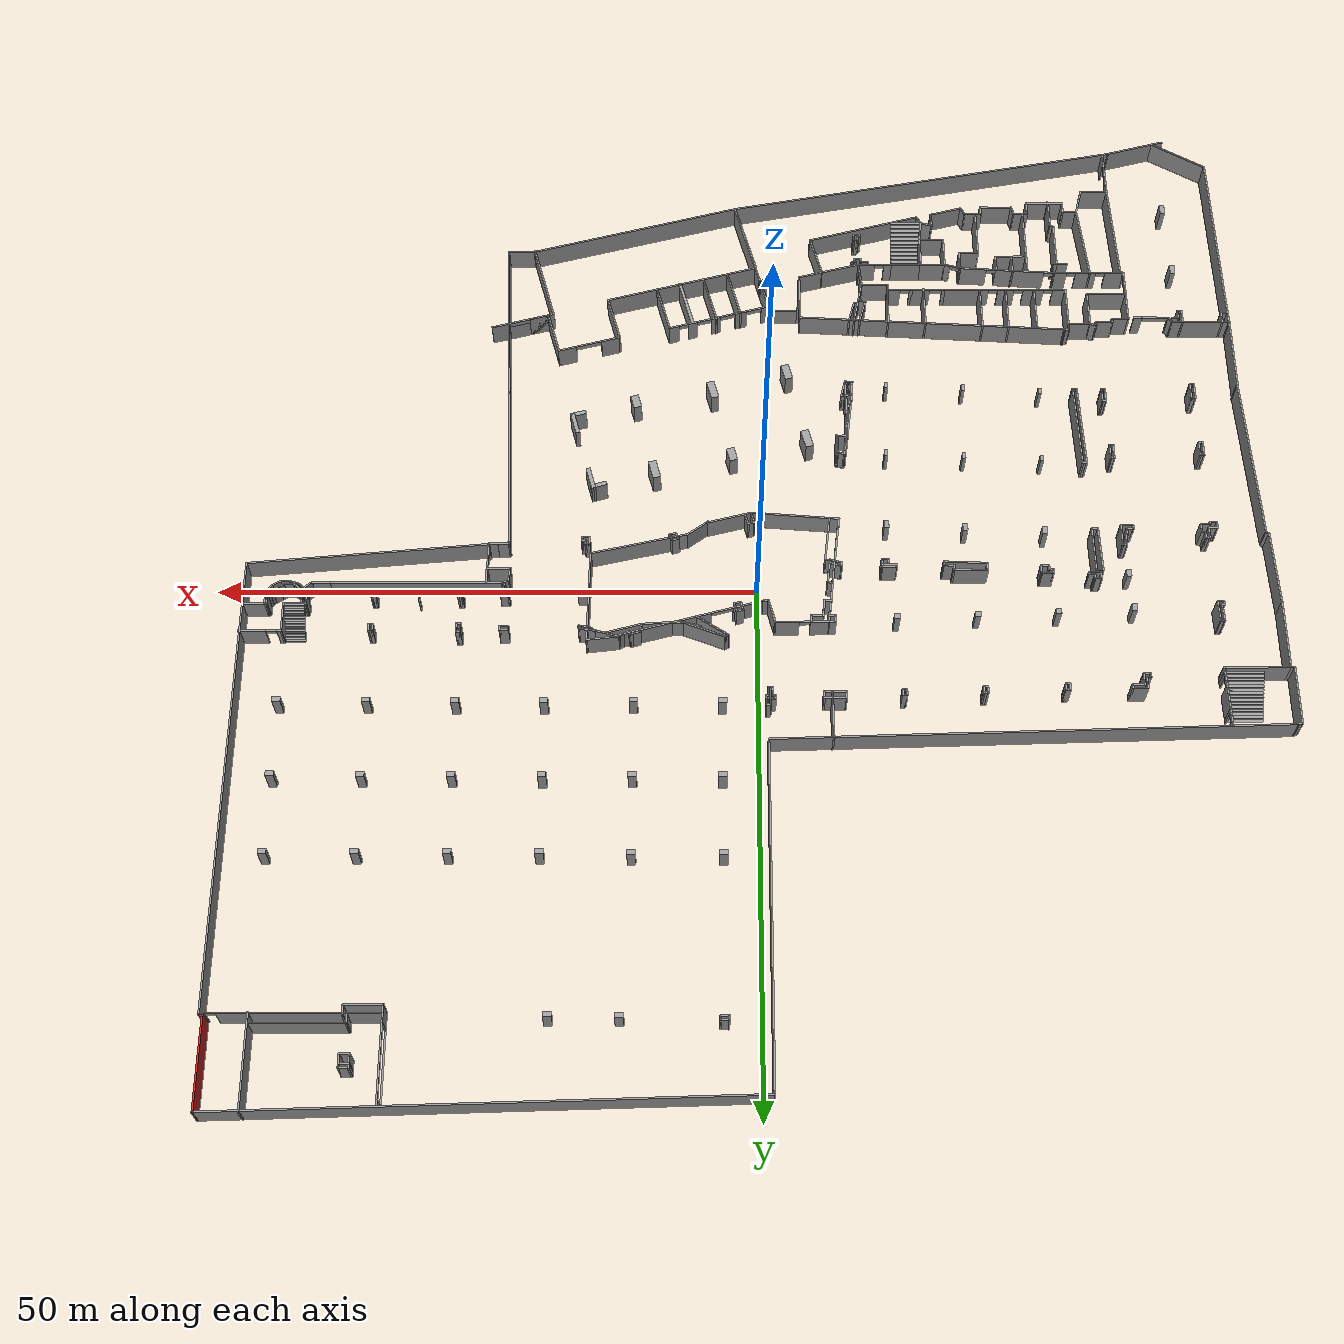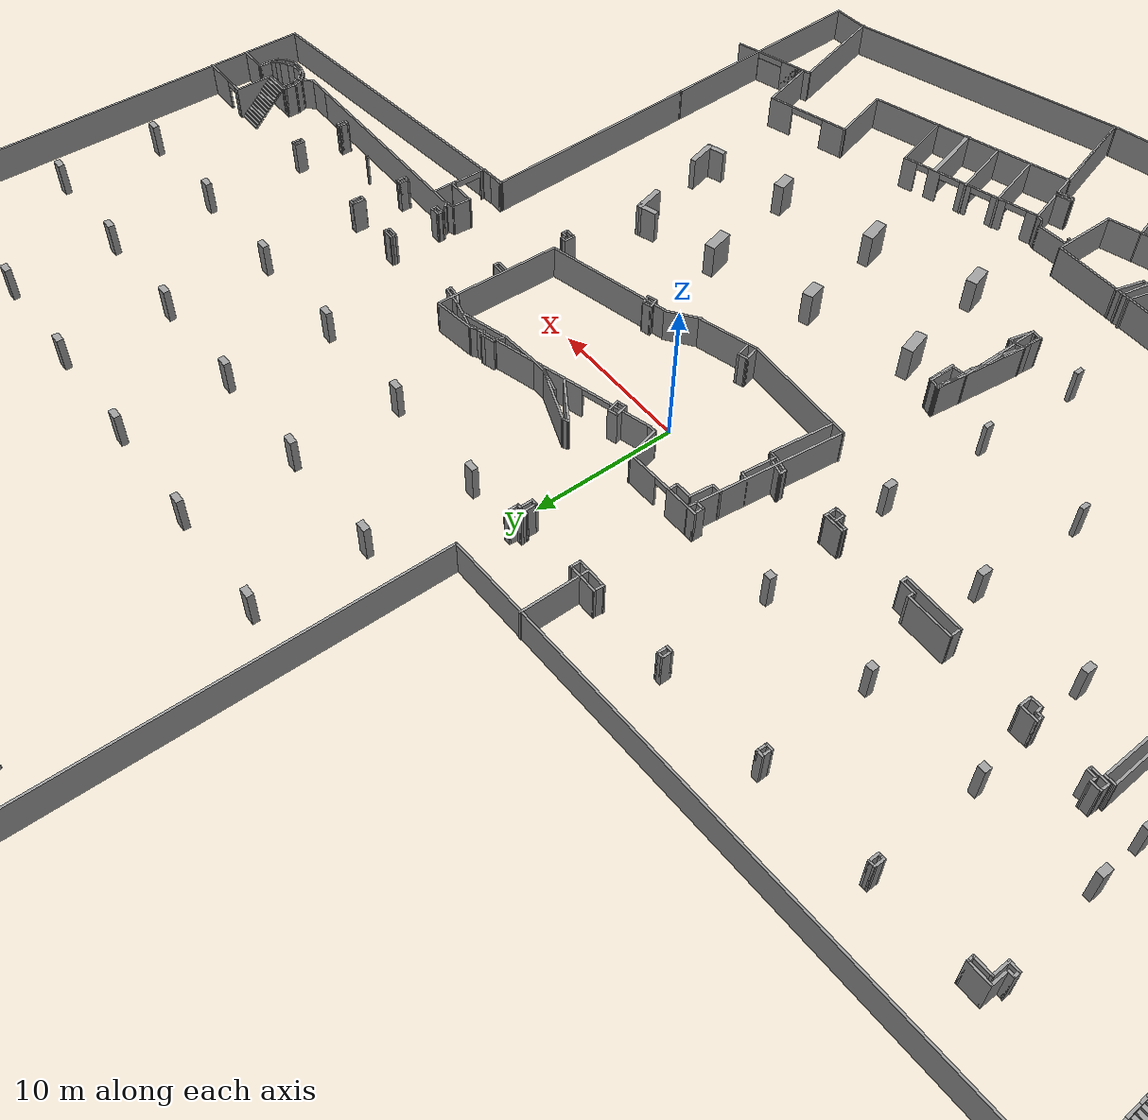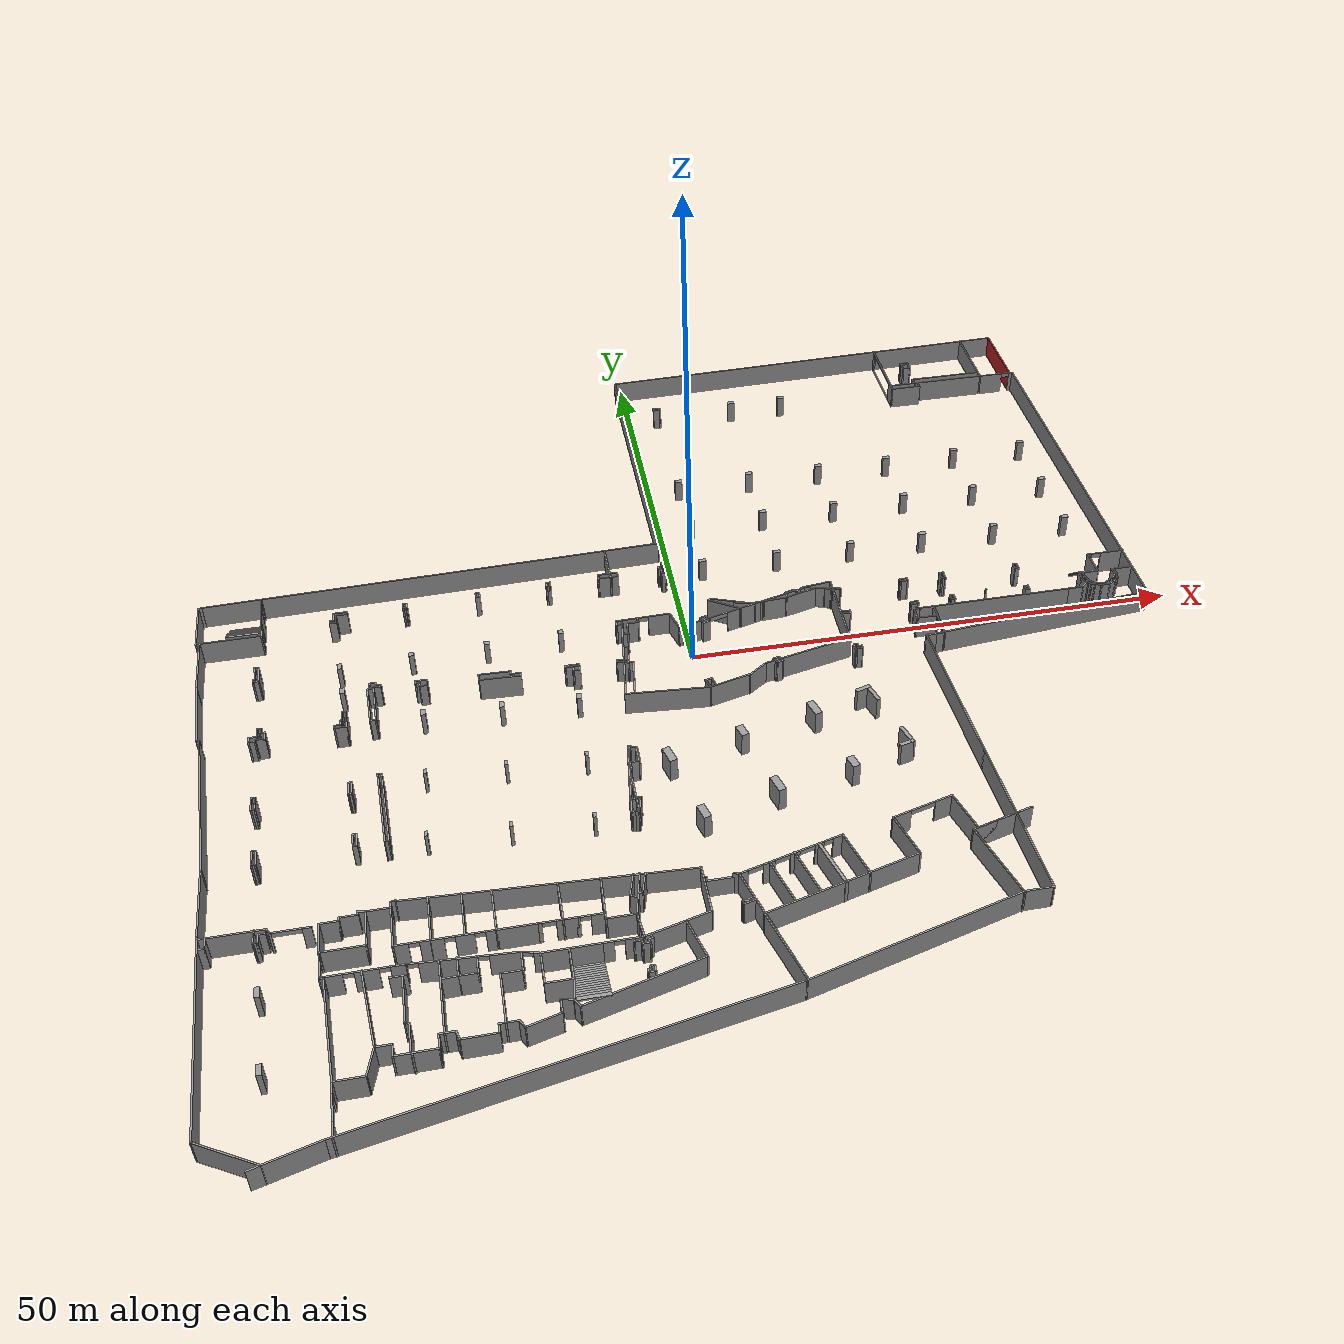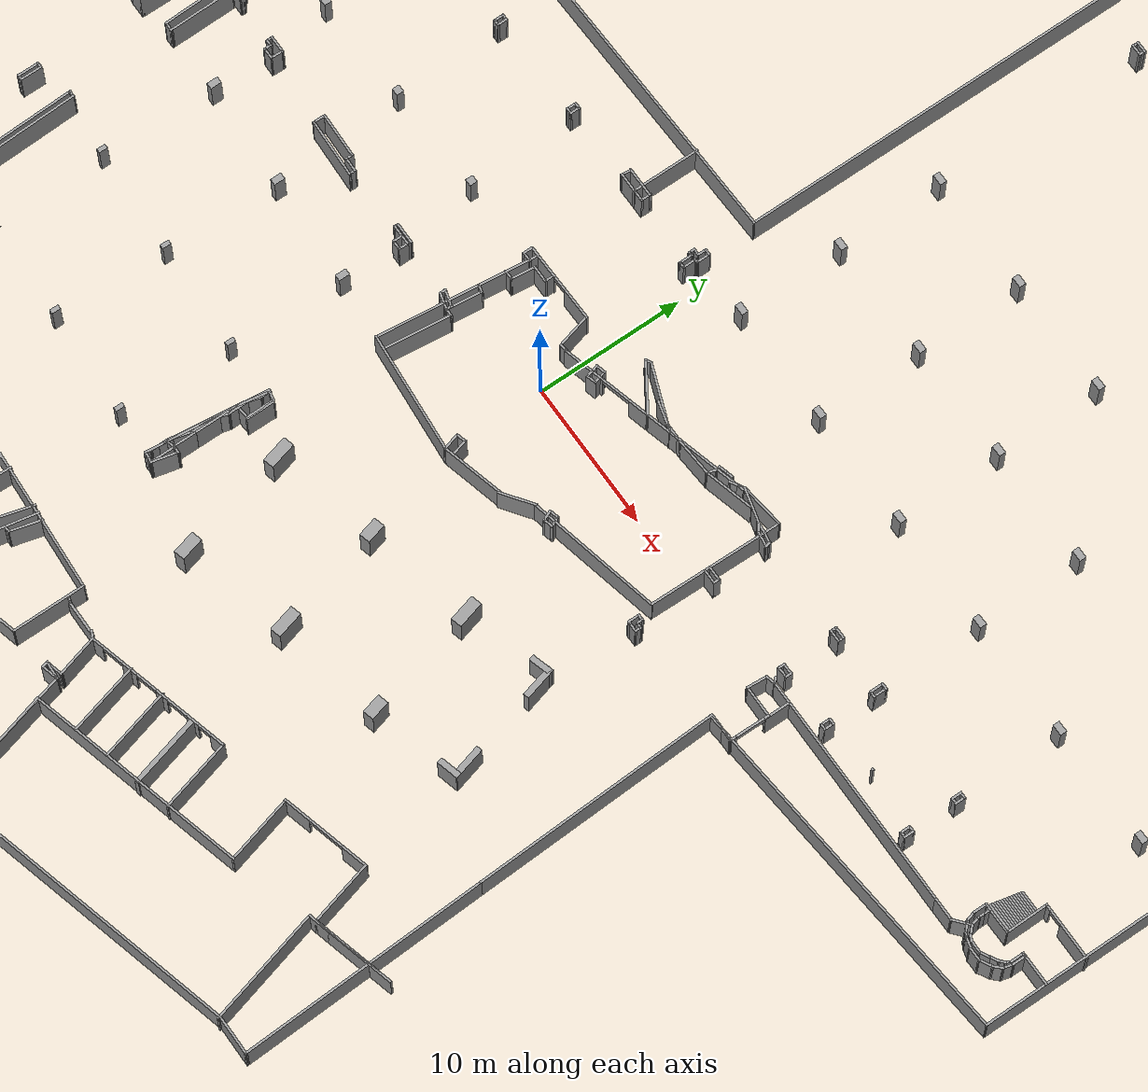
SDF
<?xml version='1.0'?>
<sdf version='1.6'>
  <model name='car_parking_underground_big_1'>
    <pose frame=''>-9.36123 -7.37411 0 0 -0 0</pose>
    <link name='Door_12'>

      <collision name='Door_12_Collision'>
        <geometry>
          <box>
            <size>2.5 0.17 2</size>
          </box>
        </geometry>
        <pose frame=''>0 0 1 0 -0 0</pose>
      </collision>
      <visual name='Door_12_Visual'>
        <pose frame=''>0 0 1 0 -0 0</pose>
        <geometry>
          <box>
            <size>2.5 0.17 2</size>
          </box>
        </geometry>
        <material>
          <script>
            <uri>file://media/materials/scripts/gazebo.material</uri>
            <name>Gazebo/Grey</name>
          </script>
        </material>
      </visual>
      <pose frame=''>6.2291 -23.2173 0 0 -0 0</pose>
    </link>
    <link name='Stairs_0'>
      <visual name='Stairs_0_Visual_0'>
        <pose frame=''>-34.4203 20.5482 0.083333 0 -0 0</pose>
        <geometry>
          <box>
            <size>3.38 0.264 0.166667</size>
          </box>
        </geometry>
        <material>
          <script>
            <uri>file://media/materials/scripts/gazebo.material</uri>
            <name>Gazebo/Grey</name>
          </script>
          <ambient>1 1 1 1</ambient>
        </material>
        <meta>
          <layer>0</layer>
        </meta>
      </visual>
      <collision name='Stairs_0_Collision_0'>
        <geometry>
          <box>
            <size>3.38 0.264 0.166667</size>
          </box>
        </geometry>
        <pose frame=''>-34.4203 20.5482 0.083333 0 -0 0</pose>
      </collision>
      <visual name='Stairs_0_Visual_1'>
        <pose frame=''>-34.4203 20.2842 0.25 0 -0 0</pose>
        <geometry>
          <box>
            <size>3.38 0.264 0.166667</size>
          </box>
        </geometry>
        <material>
          <script>
            <uri>file://media/materials/scripts/gazebo.material</uri>
            <name>Gazebo/Grey</name>
          </script>
          <ambient>1 1 1 1</ambient>
        </material>
        <meta>
          <layer>0</layer>
        </meta>
      </visual>
      <collision name='Stairs_0_Collision_1'>
        <geometry>
          <box>
            <size>3.38 0.264 0.166667</size>
          </box>
        </geometry>
        <pose frame=''>-34.4203 20.2842 0.25 0 -0 0</pose>
      </collision>
      <visual name='Stairs_0_Visual_2'>
        <pose frame=''>-34.4203 20.0202 0.416667 0 -0 0</pose>
        <geometry>
          <box>
            <size>3.38 0.264 0.166667</size>
          </box>
        </geometry>
        <material>
          <script>
            <uri>file://media/materials/scripts/gazebo.material</uri>
            <name>Gazebo/Grey</name>
          </script>
          <ambient>1 1 1 1</ambient>
        </material>
        <meta>
          <layer>0</layer>
        </meta>
      </visual>
      <collision name='Stairs_0_Collision_2'>
        <geometry>
          <box>
            <size>3.38 0.264 0.166667</size>
          </box>
        </geometry>
        <pose frame=''>-34.4203 20.0202 0.416667 0 -0 0</pose>
      </collision>
      <visual name='Stairs_0_Visual_3'>
        <pose frame=''>-34.4203 19.7562 0.583333 0 -0 0</pose>
        <geometry>
          <box>
            <size>3.38 0.264 0.166667</size>
          </box>
        </geometry>
        <material>
          <script>
            <uri>file://media/materials/scripts/gazebo.material</uri>
            <name>Gazebo/Grey</name>
          </script>
          <ambient>1 1 1 1</ambient>
        </material>
        <meta>
          <layer>0</layer>
        </meta>
      </visual>
      <collision name='Stairs_0_Collision_3'>
        <geometry>
          <box>
            <size>3.38 0.264 0.166667</size>
          </box>
        </geometry>
        <pose frame=''>-34.4203 19.7562 0.583333 0 -0 0</pose>
      </collision>
      <visual name='Stairs_0_Visual_4'>
        <pose frame=''>-34.4203 19.4922 0.75 0 -0 0</pose>
        <geometry>
          <box>
            <size>3.38 0.264 0.166667</size>
          </box>
        </geometry>
        <material>
          <script>
            <uri>file://media/materials/scripts/gazebo.material</uri>
            <name>Gazebo/Grey</name>
          </script>
          <ambient>1 1 1 1</ambient>
        </material>
        <meta>
          <layer>0</layer>
        </meta>
      </visual>
      <collision name='Stairs_0_Collision_4'>
        <geometry>
          <box>
            <size>3.38 0.264 0.166667</size>
          </box>
        </geometry>
        <pose frame=''>-34.4203 19.4922 0.75 0 -0 0</pose>
      </collision>
      <visual name='Stairs_0_Visual_5'>
        <pose frame=''>-34.4203 19.2282 0.916667 0 -0 0</pose>
        <geometry>
          <box>
            <size>3.38 0.264 0.166667</size>
          </box>
        </geometry>
        <material>
          <script>
            <uri>file://media/materials/scripts/gazebo.material</uri>
            <name>Gazebo/Grey</name>
          </script>
          <ambient>1 1 1 1</ambient>
        </material>
        <meta>
          <layer>0</layer>
        </meta>
      </visual>
      <collision name='Stairs_0_Collision_5'>
        <geometry>
          <box>
            <size>3.38 0.264 0.166667</size>
          </box>
        </geometry>
        <pose frame=''>-34.4203 19.2282 0.916667 0 -0 0</pose>
      </collision>
      <visual name='Stairs_0_Visual_6'>
        <pose frame=''>-34.4203 18.9642 1.08333 0 -0 0</pose>
        <geometry>
          <box>
            <size>3.38 0.264 0.166667</size>
          </box>
        </geometry>
        <material>
          <script>
            <uri>file://media/materials/scripts/gazebo.material</uri>
            <name>Gazebo/Grey</name>
          </script>
          <ambient>1 1 1 1</ambient>
        </material>
        <meta>
          <layer>0</layer>
        </meta>
      </visual>
      <collision name='Stairs_0_Collision_6'>
        <geometry>
          <box>
            <size>3.38 0.264 0.166667</size>
          </box>
        </geometry>
        <pose frame=''>-34.4203 18.9642 1.08333 0 -0 0</pose>
      </collision>
      <visual name='Stairs_0_Visual_7'>
        <pose frame=''>-34.4203 18.7002 1.25 0 -0 0</pose>
        <geometry>
          <box>
            <size>3.38 0.264 0.166667</size>
          </box>
        </geometry>
        <material>
          <script>
            <uri>file://media/materials/scripts/gazebo.material</uri>
            <name>Gazebo/Grey</name>
          </script>
          <ambient>1 1 1 1</ambient>
        </material>
        <meta>
          <layer>0</layer>
        </meta>
      </visual>
      <collision name='Stairs_0_Collision_7'>
        <geometry>
          <box>
            <size>3.38 0.264 0.166667</size>
          </box>
        </geometry>
        <pose frame=''>-34.4203 18.7002 1.25 0 -0 0</pose>
      </collision>
      <visual name='Stairs_0_Visual_8'>
        <pose frame=''>-34.4203 18.4362 1.41667 0 -0 0</pose>
        <geometry>
          <box>
            <size>3.38 0.264 0.166667</size>
          </box>
        </geometry>
        <material>
          <script>
            <uri>file://media/materials/scripts/gazebo.material</uri>
            <name>Gazebo/Grey</name>
          </script>
          <ambient>1 1 1 1</ambient>
        </material>
        <meta>
          <layer>0</layer>
        </meta>
      </visual>
      <collision name='Stairs_0_Collision_8'>
        <geometry>
          <box>
            <size>3.38 0.264 0.166667</size>
          </box>
        </geometry>
        <pose frame=''>-34.4203 18.4362 1.41667 0 -0 0</pose>
      </collision>
      <visual name='Stairs_0_Visual_9'>
        <pose frame=''>-34.4203 18.1722 1.58333 0 -0 0</pose>
        <geometry>
          <box>
            <size>3.38 0.264 0.166667</size>
          </box>
        </geometry>
        <material>
          <script>
            <uri>file://media/materials/scripts/gazebo.material</uri>
            <name>Gazebo/Grey</name>
          </script>
          <ambient>1 1 1 1</ambient>
        </material>
        <meta>
          <layer>0</layer>
        </meta>
      </visual>
      <collision name='Stairs_0_Collision_9'>
        <geometry>
          <box>
            <size>3.38 0.264 0.166667</size>
          </box>
        </geometry>
        <pose frame=''>-34.4203 18.1722 1.58333 0 -0 0</pose>
      </collision>
      <visual name='Stairs_0_Visual_10'>
        <pose frame=''>-34.4203 17.9082 1.75 0 -0 0</pose>
        <geometry>
          <box>
            <size>3.38 0.264 0.166667</size>
          </box>
        </geometry>
        <material>
          <script>
            <uri>file://media/materials/scripts/gazebo.material</uri>
            <name>Gazebo/Grey</name>
          </script>
          <ambient>1 1 1 1</ambient>
        </material>
        <meta>
          <layer>0</layer>
        </meta>
      </visual>
      <collision name='Stairs_0_Collision_10'>
        <geometry>
          <box>
            <size>3.38 0.264 0.166667</size>
          </box>
        </geometry>
        <pose frame=''>-34.4203 17.9082 1.75 0 -0 0</pose>
      </collision>
      <visual name='Stairs_0_Visual_11'>
        <pose frame=''>-34.4203 17.6442 1.91667 0 -0 0</pose>
        <geometry>
          <box>
            <size>3.38 0.264 0.166667</size>
          </box>
        </geometry>
        <material>
          <script>
            <uri>file://media/materials/scripts/gazebo.material</uri>
            <name>Gazebo/Grey</name>
          </script>
          <ambient>1 1 1 1</ambient>
        </material>
        <meta>
          <layer>0</layer>
        </meta>
      </visual>
      <collision name='Stairs_0_Collision_11'>
        <geometry>
          <box>
            <size>3.38 0.264 0.166667</size>
          </box>
        </geometry>
        <pose frame=''>-34.4203 17.6442 1.91667 0 -0 0</pose>
      </collision>
      <visual name='Stairs_0_Visual_12'>
        <pose frame=''>-34.4203 17.3802 2.08333 0 -0 0</pose>
        <geometry>
          <box>
            <size>3.38 0.264 0.166667</size>
          </box>
        </geometry>
        <material>
          <script>
            <uri>file://media/materials/scripts/gazebo.material</uri>
            <name>Gazebo/Grey</name>
          </script>
          <ambient>1 1 1 1</ambient>
        </material>
        <meta>
          <layer>0</layer>
        </meta>
      </visual>
      <collision name='Stairs_0_Collision_12'>
        <geometry>
          <box>
            <size>3.38 0.264 0.166667</size>
          </box>
        </geometry>
        <pose frame=''>-34.4203 17.3802 2.08333 0 -0 0</pose>
      </collision>
      <visual name='Stairs_0_Visual_13'>
        <pose frame=''>-34.4203 17.1162 2.25 0 -0 0</pose>
        <geometry>
          <box>
            <size>3.38 0.264 0.166667</size>
          </box>
        </geometry>
        <material>
          <script>
            <uri>file://media/materials/scripts/gazebo.material</uri>
            <name>Gazebo/Grey</name>
          </script>
          <ambient>1 1 1 1</ambient>
        </material>
        <meta>
          <layer>0</layer>
        </meta>
      </visual>
      <collision name='Stairs_0_Collision_13'>
        <geometry>
          <box>
            <size>3.38 0.264 0.166667</size>
          </box>
        </geometry>
        <pose frame=''>-34.4203 17.1162 2.25 0 -0 0</pose>
      </collision>
      <visual name='Stairs_0_Visual_14'>
        <pose frame=''>-34.4203 16.8522 2.41667 0 -0 0</pose>
        <geometry>
          <box>
            <size>3.38 0.264 0.166667</size>
          </box>
        </geometry>
        <material>
          <script>
            <uri>file://media/materials/scripts/gazebo.material</uri>
            <name>Gazebo/Grey</name>
          </script>
          <ambient>1 1 1 1</ambient>
        </material>
        <meta>
          <layer>0</layer>
        </meta>
      </visual>
      <collision name='Stairs_0_Collision_14'>
        <geometry>
          <box>
            <size>3.38 0.264 0.166667</size>
          </box>
        </geometry>
        <pose frame=''>-34.4203 16.8522 2.41667 0 -0 0</pose>
      </collision>
    </link>
    <link name='Stairs_1'>
      <visual name='Stairs_1_Visual_0'>
        <pose frame=''>51.7124 12.4748 0.083333 0 -0 0</pose>
        <geometry>
          <box>
            <size>1.85701 0.179697 0.166667</size>
          </box>
        </geometry>
        <material>
          <script>
            <uri>file://media/materials/scripts/gazebo.material</uri>
            <name>Gazebo/Grey</name>
          </script>
          <ambient>1 1 1 1</ambient>
        </material>
        <meta>
          <layer>0</layer>
        </meta>
      </visual>
      <collision name='Stairs_1_Collision_0'>
        <geometry>
          <box>
            <size>1.85701 0.179697 0.166667</size>
          </box>
        </geometry>
        <pose frame=''>51.7124 12.4748 0.083333 0 -0 0</pose>
      </collision>
      <visual name='Stairs_1_Visual_1'>
        <pose frame=''>51.7124 12.2951 0.25 0 -0 0</pose>
        <geometry>
          <box>
            <size>1.85701 0.179697 0.166667</size>
          </box>
        </geometry>
        <material>
          <script>
            <uri>file://media/materials/scripts/gazebo.material</uri>
            <name>Gazebo/Grey</name>
          </script>
          <ambient>1 1 1 1</ambient>
        </material>
        <meta>
          <layer>0</layer>
        </meta>
      </visual>
      <collision name='Stairs_1_Collision_1'>
        <geometry>
          <box>
            <size>1.85701 0.179697 0.166667</size>
          </box>
        </geometry>
        <pose frame=''>51.7124 12.2951 0.25 0 -0 0</pose>
      </collision>
      <visual name='Stairs_1_Visual_2'>
        <pose frame=''>51.7124 12.1154 0.416667 0 -0 0</pose>
        <geometry>
          <box>
            <size>1.85701 0.179697 0.166667</size>
          </box>
        </geometry>
        <material>
          <script>
            <uri>file://media/materials/scripts/gazebo.material</uri>
            <name>Gazebo/Grey</name>
          </script>
          <ambient>1 1 1 1</ambient>
        </material>
        <meta>
          <layer>0</layer>
        </meta>
      </visual>
      <collision name='Stairs_1_Collision_2'>
        <geometry>
          <box>
            <size>1.85701 0.179697 0.166667</size>
          </box>
        </geometry>
        <pose frame=''>51.7124 12.1154 0.416667 0 -0 0</pose>
      </collision>
      <visual name='Stairs_1_Visual_3'>
        <pose frame=''>51.7124 11.9357 0.583333 0 -0 0</pose>
        <geometry>
          <box>
            <size>1.85701 0.179697 0.166667</size>
          </box>
        </geometry>
        <material>
          <script>
            <uri>file://media/materials/scripts/gazebo.material</uri>
            <name>Gazebo/Grey</name>
          </script>
          <ambient>1 1 1 1</ambient>
        </material>
        <meta>
          <layer>0</layer>
        </meta>
      </visual>
      <collision name='Stairs_1_Collision_3'>
        <geometry>
          <box>
            <size>1.85701 0.179697 0.166667</size>
          </box>
        </geometry>
        <pose frame=''>51.7124 11.9357 0.583333 0 -0 0</pose>
      </collision>
      <visual name='Stairs_1_Visual_4'>
        <pose frame=''>51.7124 11.756 0.75 0 -0 0</pose>
        <geometry>
          <box>
            <size>1.85701 0.179697 0.166667</size>
          </box>
        </geometry>
        <material>
          <script>
            <uri>file://media/materials/scripts/gazebo.material</uri>
            <name>Gazebo/Grey</name>
          </script>
          <ambient>1 1 1 1</ambient>
        </material>
        <meta>
          <layer>0</layer>
        </meta>
      </visual>
      <collision name='Stairs_1_Collision_4'>
        <geometry>
          <box>
            <size>1.85701 0.179697 0.166667</size>
          </box>
        </geometry>
        <pose frame=''>51.7124 11.756 0.75 0 -0 0</pose>
      </collision>
      <visual name='Stairs_1_Visual_5'>
        <pose frame=''>51.7124 11.5763 0.916667 0 -0 0</pose>
        <geometry>
          <box>
            <size>1.85701 0.179697 0.166667</size>
          </box>
        </geometry>
        <material>
          <script>
            <uri>file://media/materials/scripts/gazebo.material</uri>
            <name>Gazebo/Grey</name>
          </script>
          <ambient>1 1 1 1</ambient>
        </material>
        <meta>
          <layer>0</layer>
        </meta>
      </visual>
      <collision name='Stairs_1_Collision_5'>
        <geometry>
          <box>
            <size>1.85701 0.179697 0.166667</size>
          </box>
        </geometry>
        <pose frame=''>51.7124 11.5763 0.916667 0 -0 0</pose>
      </collision>
      <visual name='Stairs_1_Visual_6'>
        <pose frame=''>51.7124 11.3966 1.08333 0 -0 0</pose>
        <geometry>
          <box>
            <size>1.85701 0.179697 0.166667</size>
          </box>
        </geometry>
        <material>
          <script>
            <uri>file://media/materials/scripts/gazebo.material</uri>
            <name>Gazebo/Grey</name>
          </script>
          <ambient>1 1 1 1</ambient>
        </material>
        <meta>
          <layer>0</layer>
        </meta>
      </visual>
      <collision name='Stairs_1_Collision_6'>
        <geometry>
          <box>
            <size>1.85701 0.179697 0.166667</size>
          </box>
        </geometry>
        <pose frame=''>51.7124 11.3966 1.08333 0 -0 0</pose>
      </collision>
      <visual name='Stairs_1_Visual_7'>
        <pose frame=''>51.7124 11.2169 1.25 0 -0 0</pose>
        <geometry>
          <box>
            <size>1.85701 0.179697 0.166667</size>
          </box>
        </geometry>
        <material>
          <script>
            <uri>file://media/materials/scripts/gazebo.material</uri>
            <name>Gazebo/Grey</name>
          </script>
          <ambient>1 1 1 1</ambient>
        </material>
        <meta>
          <layer>0</layer>
        </meta>
      </visual>
      <collision name='Stairs_1_Collision_7'>
        <geometry>
          <box>
            <size>1.85701 0.179697 0.166667</size>
          </box>
        </geometry>
        <pose frame=''>51.7124 11.2169 1.25 0 -0 0</pose>
      </collision>
      <visual name='Stairs_1_Visual_8'>
        <pose frame=''>51.7124 11.0372 1.41667 0 -0 0</pose>
        <geometry>
          <box>
            <size>1.85701 0.179697 0.166667</size>
          </box>
        </geometry>
        <material>
          <script>
            <uri>file://media/materials/scripts/gazebo.material</uri>
            <name>Gazebo/Grey</name>
          </script>
          <ambient>1 1 1 1</ambient>
        </material>
        <meta>
          <layer>0</layer>
        </meta>
      </visual>
      <collision name='Stairs_1_Collision_8'>
        <geometry>
          <box>
            <size>1.85701 0.179697 0.166667</size>
          </box>
        </geometry>
        <pose frame=''>51.7124 11.0372 1.41667 0 -0 0</pose>
      </collision>
      <visual name='Stairs_1_Visual_9'>
        <pose frame=''>51.7124 10.8575 1.58333 0 -0 0</pose>
        <geometry>
          <box>
            <size>1.85701 0.179697 0.166667</size>
          </box>
        </geometry>
        <material>
          <script>
            <uri>file://media/materials/scripts/gazebo.material</uri>
            <name>Gazebo/Grey</name>
          </script>
          <ambient>1 1 1 1</ambient>
        </material>
        <meta>
          <layer>0</layer>
        </meta>
      </visual>
      <collision name='Stairs_1_Collision_9'>
        <geometry>
          <box>
            <size>1.85701 0.179697 0.166667</size>
          </box>
        </geometry>
        <pose frame=''>51.7124 10.8575 1.58333 0 -0 0</pose>
      </collision>
      <visual name='Stairs_1_Visual_10'>
        <pose frame=''>51.7124 10.6778 1.75 0 -0 0</pose>
        <geometry>
          <box>
            <size>1.85701 0.179697 0.166667</size>
          </box>
        </geometry>
        <material>
          <script>
            <uri>file://media/materials/scripts/gazebo.material</uri>
            <name>Gazebo/Grey</name>
          </script>
          <ambient>1 1 1 1</ambient>
        </material>
        <meta>
          <layer>0</layer>
        </meta>
      </visual>
      <collision name='Stairs_1_Collision_10'>
        <geometry>
          <box>
            <size>1.85701 0.179697 0.166667</size>
          </box>
        </geometry>
        <pose frame=''>51.7124 10.6778 1.75 0 -0 0</pose>
      </collision>
      <visual name='Stairs_1_Visual_11'>
        <pose frame=''>51.7124 10.4981 1.91667 0 -0 0</pose>
        <geometry>
          <box>
            <size>1.85701 0.179697 0.166667</size>
          </box>
        </geometry>
        <material>
          <script>
            <uri>file://media/materials/scripts/gazebo.material</uri>
            <name>Gazebo/Grey</name>
          </script>
          <ambient>1 1 1 1</ambient>
        </material>
        <meta>
          <layer>0</layer>
        </meta>
      </visual>
      <collision name='Stairs_1_Collision_11'>
        <geometry>
          <box>
            <size>1.85701 0.179697 0.166667</size>
          </box>
        </geometry>
        <pose frame=''>51.7124 10.4981 1.91667 0 -0 0</pose>
      </collision>
      <visual name='Stairs_1_Visual_12'>
        <pose frame=''>51.7124 10.3184 2.08333 0 -0 0</pose>
        <geometry>
          <box>
            <size>1.85701 0.179697 0.166667</size>
          </box>
        </geometry>
        <material>
          <script>
            <uri>file://media/materials/scripts/gazebo.material</uri>
            <name>Gazebo/Grey</name>
          </script>
          <ambient>1 1 1 1</ambient>
        </material>
        <meta>
          <layer>0</layer>
        </meta>
      </visual>
      <collision name='Stairs_1_Collision_12'>
        <geometry>
          <box>
            <size>1.85701 0.179697 0.166667</size>
          </box>
        </geometry>
        <pose frame=''>51.7124 10.3184 2.08333 0 -0 0</pose>
      </collision>
      <visual name='Stairs_1_Visual_13'>
        <pose frame=''>51.7124 10.1387 2.25 0 -0 0</pose>
        <geometry>
          <box>
            <size>1.85701 0.179697 0.166667</size>
          </box>
        </geometry>
        <material>
          <script>
            <uri>file://media/materials/scripts/gazebo.material</uri>
            <name>Gazebo/Grey</name>
          </script>
          <ambient>1 1 1 1</ambient>
        </material>
        <meta>
          <layer>0</layer>
        </meta>
      </visual>
      <collision name='Stairs_1_Collision_13'>
        <geometry>
          <box>
            <size>1.85701 0.179697 0.166667</size>
          </box>
        </geometry>
        <pose frame=''>51.7124 10.1387 2.25 0 -0 0</pose>
      </collision>
      <visual name='Stairs_1_Visual_14'>
        <pose frame=''>51.7124 9.95903 2.41667 0 -0 0</pose>
        <geometry>
          <box>
            <size>1.85701 0.179697 0.166667</size>
          </box>
        </geometry>
        <material>
          <script>
            <uri>file://media/materials/scripts/gazebo.material</uri>
            <name>Gazebo/Grey</name>
          </script>
          <ambient>1 1 1 1</ambient>
        </material>
        <meta>
          <layer>0</layer>
        </meta>
      </visual>
      <collision name='Stairs_1_Collision_14'>
        <geometry>
          <box>
            <size>1.85701 0.179697 0.166667</size>
          </box>
        </geometry>
        <pose frame=''>51.7124 9.95903 2.41667 0 -0 0</pose>
      </collision>
    </link>
    <link name='Stairs_6'>
      <visual name='Stairs_6_Visual_0'>
        <pose frame=''>-5.97668 -28.6723 0.083333 0 -0 0</pose>
        <geometry>
          <box>
            <size>2.85487 0.352142 0.166667</size>
          </box>
        </geometry>
        <material>
          <script>
            <uri>file://media/materials/scripts/gazebo.material</uri>
            <name>Gazebo/Grey</name>
          </script>
          <ambient>1 1 1 1</ambient>
        </material>
        <meta>
          <layer>0</layer>
        </meta>
      </visual>
      <collision name='Stairs_6_Collision_0'>
        <geometry>
          <box>
            <size>2.85487 0.352142 0.166667</size>
          </box>
        </geometry>
        <pose frame=''>-5.97668 -28.6723 0.083333 0 -0 0</pose>
      </collision>
      <visual name='Stairs_6_Visual_1'>
        <pose frame=''>-5.97668 -29.0245 0.25 0 -0 0</pose>
        <geometry>
          <box>
            <size>2.85487 0.352142 0.166667</size>
          </box>
        </geometry>
        <material>
          <script>
            <uri>file://media/materials/scripts/gazebo.material</uri>
            <name>Gazebo/Grey</name>
          </script>
          <ambient>1 1 1 1</ambient>
        </material>
        <meta>
          <layer>0</layer>
        </meta>
      </visual>
      <collision name='Stairs_6_Collision_1'>
        <geometry>
          <box>
            <size>2.85487 0.352142 0.166667</size>
          </box>
        </geometry>
        <pose frame=''>-5.97668 -29.0245 0.25 0 -0 0</pose>
      </collision>
      <visual name='Stairs_6_Visual_2'>
        <pose frame=''>-5.97668 -29.3766 0.416667 0 -0 0</pose>
        <geometry>
          <box>
            <size>2.85487 0.352142 0.166667</size>
          </box>
        </geometry>
        <material>
          <script>
            <uri>file://media/materials/scripts/gazebo.material</uri>
            <name>Gazebo/Grey</name>
          </script>
          <ambient>1 1 1 1</ambient>
        </material>
        <meta>
          <layer>0</layer>
        </meta>
      </visual>
      <collision name='Stairs_6_Collision_2'>
        <geometry>
          <box>
            <size>2.85487 0.352142 0.166667</size>
          </box>
        </geometry>
        <pose frame=''>-5.97668 -29.3766 0.416667 0 -0 0</pose>
      </collision>
      <visual name='Stairs_6_Visual_3'>
        <pose frame=''>-5.97668 -29.7288 0.583333 0 -0 0</pose>
        <geometry>
          <box>
            <size>2.85487 0.352142 0.166667</size>
          </box>
        </geometry>
        <material>
          <script>
            <uri>file://media/materials/scripts/gazebo.material</uri>
            <name>Gazebo/Grey</name>
          </script>
          <ambient>1 1 1 1</ambient>
        </material>
        <meta>
          <layer>0</layer>
        </meta>
      </visual>
      <collision name='Stairs_6_Collision_3'>
        <geometry>
          <box>
            <size>2.85487 0.352142 0.166667</size>
          </box>
        </geometry>
        <pose frame=''>-5.97668 -29.7288 0.583333 0 -0 0</pose>
      </collision>
      <visual name='Stairs_6_Visual_4'>
        <pose frame=''>-5.97668 -30.0809 0.75 0 -0 0</pose>
        <geometry>
          <box>
            <size>2.85487 0.352142 0.166667</size>
          </box>
        </geometry>
        <material>
          <script>
            <uri>file://media/materials/scripts/gazebo.material</uri>
            <name>Gazebo/Grey</name>
          </script>
          <ambient>1 1 1 1</ambient>
        </material>
        <meta>
          <layer>0</layer>
        </meta>
      </visual>
      <collision name='Stairs_6_Collision_4'>
        <geometry>
          <box>
            <size>2.85487 0.352142 0.166667</size>
          </box>
        </geometry>
        <pose frame=''>-5.97668 -30.0809 0.75 0 -0 0</pose>
      </collision>
      <visual name='Stairs_6_Visual_5'>
        <pose frame=''>-5.97668 -30.433 0.916667 0 -0 0</pose>
        <geometry>
          <box>
            <size>2.85487 0.352142 0.166667</size>
          </box>
        </geometry>
        <material>
          <script>
            <uri>file://media/materials/scripts/gazebo.material</uri>
            <name>Gazebo/Grey</name>
          </script>
          <ambient>1 1 1 1</ambient>
        </material>
        <meta>
          <layer>0</layer>
        </meta>
      </visual>
      <collision name='Stairs_6_Collision_5'>
        <geometry>
          <box>
            <size>2.85487 0.352142 0.166667</size>
          </box>
        </geometry>
        <pose frame=''>-5.97668 -30.433 0.916667 0 -0 0</pose>
      </collision>
      <visual name='Stairs_6_Visual_6'>
        <pose frame=''>-5.97668 -30.7852 1.08333 0 -0 0</pose>
        <geometry>
          <box>
            <size>2.85487 0.352142 0.166667</size>
          </box>
        </geometry>
        <material>
          <script>
            <uri>file://media/materials/scripts/gazebo.material</uri>
            <name>Gazebo/Grey</name>
          </script>
          <ambient>1 1 1 1</ambient>
        </material>
        <meta>
          <layer>0</layer>
        </meta>
      </visual>
      <collision name='Stairs_6_Collision_6'>
        <geometry>
          <box>
            <size>2.85487 0.352142 0.166667</size>
          </box>
        </geometry>
        <pose frame=''>-5.97668 -30.7852 1.08333 0 -0 0</pose>
      </collision>
      <visual name='Stairs_6_Visual_7'>
        <pose frame=''>-5.97668 -31.1373 1.25 0 -0 0</pose>
        <geometry>
          <box>
            <size>2.85487 0.352142 0.166667</size>
          </box>
        </geometry>
        <material>
          <script>
            <uri>file://media/materials/scripts/gazebo.material</uri>
            <name>Gazebo/Grey</name>
          </script>
          <ambient>1 1 1 1</ambient>
        </material>
        <meta>
          <layer>0</layer>
        </meta>
      </visual>
      <collision name='Stairs_6_Collision_7'>
        <geometry>
          <box>
            <size>2.85487 0.352142 0.166667</size>
          </box>
        </geometry>
        <pose frame=''>-5.97668 -31.1373 1.25 0 -0 0</pose>
      </collision>
      <visual name='Stairs_6_Visual_8'>
        <pose frame=''>-5.97668 -31.4895 1.41667 0 -0 0</pose>
        <geometry>
          <box>
            <size>2.85487 0.352142 0.166667</size>
          </box>
        </geometry>
        <material>
          <script>
            <uri>file://media/materials/scripts/gazebo.material</uri>
            <name>Gazebo/Grey</name>
          </script>
          <ambient>1 1 1 1</ambient>
        </material>
        <meta>
          <layer>0</layer>
        </meta>
      </visual>
      <collision name='Stairs_6_Collision_8'>
        <geometry>
          <box>
            <size>2.85487 0.352142 0.166667</size>
          </box>
        </geometry>
        <pose frame=''>-5.97668 -31.4895 1.41667 0 -0 0</pose>
      </collision>
      <visual name='Stairs_6_Visual_9'>
        <pose frame=''>-5.97668 -31.8416 1.58333 0 -0 0</pose>
        <geometry>
          <box>
            <size>2.85487 0.352142 0.166667</size>
          </box>
        </geometry>
        <material>
          <script>
            <uri>file://media/materials/scripts/gazebo.material</uri>
            <name>Gazebo/Grey</name>
          </script>
          <ambient>1 1 1 1</ambient>
        </material>
        <meta>
          <layer>0</layer>
        </meta>
      </visual>
      <collision name='Stairs_6_Collision_9'>
        <geometry>
          <box>
            <size>2.85487 0.352142 0.166667</size>
          </box>
        </geometry>
        <pose frame=''>-5.97668 -31.8416 1.58333 0 -0 0</pose>
      </collision>
      <visual name='Stairs_6_Visual_10'>
        <pose frame=''>-5.97668 -32.1938 1.75 0 -0 0</pose>
        <geometry>
          <box>
            <size>2.85487 0.352142 0.166667</size>
          </box>
        </geometry>
        <material>
          <script>
            <uri>file://media/materials/scripts/gazebo.material</uri>
            <name>Gazebo/Grey</name>
          </script>
          <ambient>1 1 1 1</ambient>
        </material>
        <meta>
          <layer>0</layer>
        </meta>
      </visual>
      <collision name='Stairs_6_Collision_10'>
        <geometry>
          <box>
            <size>2.85487 0.352142 0.166667</size>
          </box>
        </geometry>
        <pose frame=''>-5.97668 -32.1938 1.75 0 -0 0</pose>
      </collision>
      <visual name='Stairs_6_Visual_11'>
        <pose frame=''>-5.97668 -32.5459 1.91667 0 -0 0</pose>
        <geometry>
          <box>
            <size>2.85487 0.352142 0.166667</size>
          </box>
        </geometry>
        <material>
          <script>
            <uri>file://media/materials/scripts/gazebo.material</uri>
            <name>Gazebo/Grey</name>
          </script>
          <ambient>1 1 1 1</ambient>
        </material>
        <meta>
          <layer>0</layer>
        </meta>
      </visual>
      <collision name='Stairs_6_Collision_11'>
        <geometry>
          <box>
            <size>2.85487 0.352142 0.166667</size>
          </box>
        </geometry>
        <pose frame=''>-5.97668 -32.5459 1.91667 0 -0 0</pose>
      </collision>
      <visual name='Stairs_6_Visual_12'>
        <pose frame=''>-5.97668 -32.898 2.08333 0 -0 0</pose>
        <geometry>
          <box>
            <size>2.85487 0.352142 0.166667</size>
          </box>
        </geometry>
        <material>
          <script>
            <uri>file://media/materials/scripts/gazebo.material</uri>
            <name>Gazebo/Grey</name>
          </script>
          <ambient>1 1 1 1</ambient>
        </material>
        <meta>
          <layer>0</layer>
        </meta>
      </visual>
      <collision name='Stairs_6_Collision_12'>
        <geometry>
          <box>
            <size>2.85487 0.352142 0.166667</size>
          </box>
        </geometry>
        <pose frame=''>-5.97668 -32.898 2.08333 0 -0 0</pose>
      </collision>
      <visual name='Stairs_6_Visual_13'>
        <pose frame=''>-5.97668 -33.2502 2.25 0 -0 0</pose>
        <geometry>
          <box>
            <size>2.85487 0.352142 0.166667</size>
          </box>
        </geometry>
        <material>
          <script>
            <uri>file://media/materials/scripts/gazebo.material</uri>
            <name>Gazebo/Grey</name>
          </script>
          <ambient>1 1 1 1</ambient>
        </material>
        <meta>
          <layer>0</layer>
        </meta>
      </visual>
      <collision name='Stairs_6_Collision_13'>
        <geometry>
          <box>
            <size>2.85487 0.352142 0.166667</size>
          </box>
        </geometry>
        <pose frame=''>-5.97668 -33.2502 2.25 0 -0 0</pose>
      </collision>
      <visual name='Stairs_6_Visual_14'>
        <pose frame=''>-5.97668 -33.6023 2.41667 0 -0 0</pose>
        <geometry>
          <box>
            <size>2.85487 0.352142 0.166667</size>
          </box>
        </geometry>
        <material>
          <script>
            <uri>file://media/materials/scripts/gazebo.material</uri>
            <name>Gazebo/Grey</name>
          </script>
          <ambient>1 1 1 1</ambient>
        </material>
        <meta>
          <layer>0</layer>
        </meta>
      </visual>
      <collision name='Stairs_6_Collision_14'>
        <geometry>
          <box>
            <size>2.85487 0.352142 0.166667</size>
          </box>
        </geometry>
        <pose frame=''>-5.97668 -33.6023 2.41667 0 -0 0</pose>
      </collision>
    </link>
    <link name='Wall_10'>
      <collision name='Wall_10_Collision'>
        <geometry>
          <box>
            <size>47.7736 0.15 2.5</size>
          </box>
        </geometry>
        <pose frame=''>0 0 1.25 0 -0 0</pose>
      </collision>
      <visual name='Wall_10_Visual'>
        <pose frame=''>0 0 1.25 0 -0 0</pose>
        <geometry>
          <box>
            <size>47.7736 0.15 2.5</size>
          </box>
        </geometry>
        <material>
          <script>
            <uri>file://media/materials/scripts/gazebo.material</uri>
            <name>Gazebo/Grey</name>
          </script>
          <ambient>1 1 1 1</ambient>
        </material>
        <meta>
          <layer>0</layer>
        </meta>
      </visual>
      <pose frame=''>32.3321 56.3053 0 0 -0 0.031502</pose>
    </link>
    <link name='Wall_100'>
      <collision name='Wall_100_Collision'>
        <geometry>
          <box>
            <size>2.75 0.15 2.5</size>
          </box>
        </geometry>
        <pose frame=''>0 0 1.25 0 -0 0</pose>
      </collision>
      <visual name='Wall_100_Visual'>
        <pose frame=''>0 0 1.25 0 -0 0</pose>
        <geometry>
          <box>
            <size>2.75 0.15 2.5</size>
          </box>
        </geometry>
        <material>
          <script>
            <uri>file://media/materials/scripts/gazebo.material</uri>
            <name>Gazebo/Grey</name>
          </script>
          <ambient>1 1 1 1</ambient>
        </material>
        <meta>
          <layer>0</layer>
        </meta>
      </visual>
      <pose frame=''>-23.5938 -36.292 0 0 -0 -1.8326</pose>
    </link>
    <link name='Wall_101'>
      <collision name='Wall_101_Collision'>
        <geometry>
          <box>
            <size>2.75 0.15 2.5</size>
          </box>
        </geometry>
        <pose frame=''>0 0 1.25 0 -0 0</pose>
      </collision>
      <visual name='Wall_101_Visual'>
        <pose frame=''>0 0 1.25 0 -0 0</pose>
        <geometry>
          <box>
            <size>2.75 0.15 2.5</size>
          </box>
        </geometry>
        <material>
          <script>
            <uri>file://media/materials/scripts/gazebo.material</uri>
            <name>Gazebo/Grey</name>
          </script>
          <ambient>1 1 1 1</ambient>
        </material>
        <meta>
          <layer>0</layer>
        </meta>
      </visual>
      <pose frame=''>-25.2302 -37.5477 0 0 -0 3.14159</pose>
    </link>
    <link name='Wall_104'>
      <pose frame=''>-26.5302 -39.9727 0 0 -0 -1.5708</pose>
      <visual name='Wall_104_Visual_0'>
        <pose frame=''>-1.95044 0 1.25 0 -0 0</pose>
        <geometry>
          <box>
            <size>1.09911 0.15 2.5</size>
          </box>
        </geometry>
        <material>
          <script>
            <uri>file://media/materials/scripts/gazebo.material</uri>
            <name>Gazebo/Grey</name>
          </script>
          <ambient>1 1 1 1</ambient>
        </material>
        <meta>
          <layer>0</layer>
        </meta>
      </visual>
      <collision name='Wall_104_Collision_0'>
        <geometry>
          <box>
            <size>1.09911 0.15 2.5</size>
          </box>
        </geometry>
        <pose frame=''>-1.95044 0 1.25 0 -0 0</pose>
      </collision>
      <visual name='Wall_104_Visual_1'>
        <pose frame=''>1.79956 0 1.25 0 -0 0</pose>
        <geometry>
          <box>
            <size>1.40089 0.15 2.5</size>
          </box>
        </geometry>
        <material>
          <script>
            <uri>file://media/materials/scripts/gazebo.material</uri>
            <name>Gazebo/Grey</name>
          </script>
          <ambient>1 1 1 1</ambient>
        </material>
        <meta>
          <layer>0</layer>
        </meta>
      </visual>
      <collision name='Wall_104_Collision_1'>
        <geometry>
          <box>
            <size>1.40089 0.15 2.5</size>
          </box>
        </geometry>
        <pose frame=''>1.79956 0 1.25 0 -0 0</pose>
      </collision>
      <visual name='Wall_104_Visual_2'>
        <pose frame=''>-0.150887 0 2.25 0 -0 0</pose>
        <geometry>
          <box>
            <size>2.5 0.15 0.5</size>
          </box>
        </geometry>
        <material>
          <script>
            <uri>file://media/materials/scripts/gazebo.material</uri>
            <name>Gazebo/Grey</name>
          </script>
          <ambient>1 1 1 1</ambient>
        </material>
        <meta>
          <layer>0</layer>
        </meta>
      </visual>
      <collision name='Wall_104_Collision_2'>
        <geometry>
          <box>
            <size>2.5 0.15 0.5</size>
          </box>
        </geometry>
        <pose frame=''>-0.150887 0 2.25 0 -0 0</pose>
      </collision>
    </link>
    <link name='Wall_109'>
      <collision name='Wall_109_Collision'>
        <geometry>
          <box>
            <size>5.75 0.15 2.5</size>
          </box>
        </geometry>
        <pose frame=''>0 0 1.25 0 -0 0</pose>
      </collision>
      <visual name='Wall_109_Visual'>
        <pose frame=''>0 0 1.25 0 -0 0</pose>
        <geometry>
          <box>
            <size>5.75 0.15 2.5</size>
          </box>
        </geometry>
        <material>
          <script>
            <uri>file://media/materials/scripts/gazebo.material</uri>
            <name>Gazebo/Grey</name>
          </script>
          <ambient>1 1 1 1</ambient>
        </material>
        <meta>
          <layer>0</layer>
        </meta>
      </visual>
      <pose frame=''>-38.933 19.091 0 0 -0 -1.5708</pose>
    </link>
    <link name='Wall_110'>
      <collision name='Wall_110_Collision'>
        <geometry>
          <box>
            <size>0.491037 0.15 2.5</size>
          </box>
        </geometry>
        <pose frame=''>0 0 1.25 0 -0 0</pose>
      </collision>
      <visual name='Wall_110_Visual'>
        <pose frame=''>0 0 1.25 0 -0 0</pose>
        <geometry>
          <box>
            <size>0.491037 0.15 2.5</size>
          </box>
        </geometry>
        <material>
          <script>
            <uri>file://media/materials/scripts/gazebo.material</uri>
            <name>Gazebo/Grey</name>
          </script>
          <ambient>1 1 1 1</ambient>
        </material>
        <meta>
          <layer>0</layer>
        </meta>
      </visual>
      <pose frame=''>-38.7625 16.311 0 0 -0 1.1e-05</pose>
    </link>
    <link name='Wall_111'>
      <collision name='Wall_111_Collision'>
        <geometry>
          <box>
            <size>6.75 0.15 2.5</size>
          </box>
        </geometry>
        <pose frame=''>0 0 1.25 0 -0 0</pose>
      </collision>
      <visual name='Wall_111_Visual'>
        <pose frame=''>0 0 1.25 0 -0 0</pose>
        <geometry>
          <box>
            <size>6.75 0.15 2.5</size>
          </box>
        </geometry>
        <material>
          <script>
            <uri>file://media/materials/scripts/gazebo.material</uri>
            <name>Gazebo/Grey</name>
          </script>
          <ambient>1 1 1 1</ambient>
        </material>
        <meta>
          <layer>0</layer>
        </meta>
      </visual>
      <pose frame=''>-38.592 13.011 0 0 -0 -1.5708</pose>
    </link>
    <link name='Wall_112'>
      <collision name='Wall_112_Collision'>
        <geometry>
          <box>
            <size>7.4154 0.15 2.5</size>
          </box>
        </geometry>
        <pose frame=''>0 0 1.25 0 -0 0</pose>
      </collision>
      <visual name='Wall_112_Visual'>
        <pose frame=''>0 0 1.25 0 -0 0</pose>
        <geometry>
          <box>
            <size>7.4154 0.15 2.5</size>
          </box>
        </geometry>
        <material>
          <script>
            <uri>file://media/materials/scripts/gazebo.material</uri>
            <name>Gazebo/Grey</name>
          </script>
          <ambient>1 1 1 1</ambient>
        </material>
        <meta>
          <layer>0</layer>
        </meta>
      </visual>
      <pose frame=''>-38.4259 6.08207 0 0 -0 -1.52507</pose>
    </link>
    <link name='Wall_113'>
      <collision name='Wall_113_Collision'>
        <geometry>
          <box>
            <size>0.5 0.15 2.5</size>
          </box>
        </geometry>
        <pose frame=''>0 0 1.25 0 -0 0</pose>
      </collision>
      <visual name='Wall_113_Visual'>
        <pose frame=''>0 0 1.25 0 -0 0</pose>
        <geometry>
          <box>
            <size>0.5 0.15 2.5</size>
          </box>
        </geometry>
        <material>
          <script>
            <uri>file://media/materials/scripts/gazebo.material</uri>
            <name>Gazebo/Grey</name>
          </script>
          <ambient>1 1 1 1</ambient>
        </material>
        <meta>
          <layer>0</layer>
        </meta>
      </visual>
      <pose frame=''>-38.1362 2.32942 0 0 -0 -0.785398</pose>
    </link>
    <link name='Wall_114'>
      <collision name='Wall_114_Collision'>
        <geometry>
          <box>
            <size>16.392 0.15 2.5</size>
          </box>
        </geometry>
        <pose frame=''>0 0 1.25 0 -0 0</pose>
      </collision>
      <visual name='Wall_114_Visual'>
        <pose frame=''>0 0 1.25 0 -0 0</pose>
        <geometry>
          <box>
            <size>16.392 0.15 2.5</size>
          </box>
        </geometry>
        <material>
          <script>
            <uri>file://media/materials/scripts/gazebo.material</uri>
            <name>Gazebo/Grey</name>
          </script>
          <ambient>1 1 1 1</ambient>
        </material>
        <meta>
          <layer>0</layer>
        </meta>
      </visual>
      <pose frame=''>-37.5898 -5.90433 0 0 -0 -1.51874</pose>
    </link>
    <link name='Wall_115'>
      <collision name='Wall_115_Collision'>
        <geometry>
          <box>
            <size>0.25 0.15 2.5</size>
          </box>
        </geometry>
        <pose frame=''>0 0 1.25 0 -0 0</pose>
      </collision>
      <visual name='Wall_115_Visual'>
        <pose frame=''>0 0 1.25 0 -0 0</pose>
        <geometry>
          <box>
            <size>0.25 0.15 2.5</size>
          </box>
        </geometry>
        <material>
          <script>
            <uri>file://media/materials/scripts/gazebo.material</uri>
            <name>Gazebo/Grey</name>
          </script>
          <ambient>1 1 1 1</ambient>
        </material>
        <meta>
          <layer>0</layer>
        </meta>
      </visual>
      <pose frame=''>-37.1543 -14.0626 0 0 -0 -1.309</pose>
    </link>
    <link name='Wall_116'>
      <collision name='Wall_116_Collision'>
        <geometry>
          <box>
            <size>0.25 0.15 2.5</size>
          </box>
        </geometry>
        <pose frame=''>0 0 1.25 0 -0 0</pose>
      </collision>
      <visual name='Wall_116_Visual'>
        <pose frame=''>0 0 1.25 0 -0 0</pose>
        <geometry>
          <box>
            <size>0.25 0.15 2.5</size>
          </box>
        </geometry>
        <material>
          <script>
            <uri>file://media/materials/scripts/gazebo.material</uri>
            <name>Gazebo/Grey</name>
          </script>
          <ambient>1 1 1 1</ambient>
        </material>
        <meta>
          <layer>0</layer>
        </meta>
      </visual>
      <pose frame=''>-37.1664 -14.0676 0 0 -0 2.0944</pose>
    </link>
    <link name='Wall_117'>
      <collision name='Wall_117_Collision'>
        <geometry>
          <box>
            <size>7.5 0.15 2.5</size>
          </box>
        </geometry>
        <pose frame=''>0 0 1.25 0 -0 0</pose>
      </collision>
      <visual name='Wall_117_Visual'>
        <pose frame=''>0 0 1.25 0 -0 0</pose>
        <geometry>
          <box>
            <size>7.5 0.15 2.5</size>
          </box>
        </geometry>
        <material>
          <script>
            <uri>file://media/materials/scripts/gazebo.material</uri>
            <name>Gazebo/Grey</name>
          </script>
          <ambient>1 1 1 1</ambient>
        </material>
        <meta>
          <layer>0</layer>
        </meta>
      </visual>
      <pose frame=''>-37.1914 -17.6993 0 0 -0 -1.5708</pose>
    </link>
    <link name='Wall_119'>
      <pose frame=''>54.6311 12.6385 0 0 -0 3.14159</pose>
      <visual name='Wall_119_Visual_0'>
        <pose frame=''>-0.72715 0 1.25 0 -0 0</pose>
        <geometry>
          <box>
            <size>2.5457 0.15 2.5</size>
          </box>
        </geometry>
        <material>
          <script>
            <uri>file://media/materials/scripts/gazebo.material</uri>
            <name>Gazebo/Grey</name>
          </script>
          <ambient>1 1 1 1</ambient>
        </material>
        <meta>
          <layer>0</layer>
        </meta>
      </visual>
      <collision name='Wall_119_Collision_0'>
        <geometry>
          <box>
            <size>2.5457 0.15 2.5</size>
          </box>
        </geometry>
        <pose frame=''>-0.72715 0 1.25 0 -0 0</pose>
      </collision>
      <visual name='Wall_119_Visual_1'>
        <pose frame=''>1.77285 0 1.25 0 -0 0</pose>
        <geometry>
          <box>
            <size>0.4543 0.15 2.5</size>
          </box>
        </geometry>
        <material>
          <script>
            <uri>file://media/materials/scripts/gazebo.material</uri>
            <name>Gazebo/Grey</name>
          </script>
          <ambient>1 1 1 1</ambient>
        </material>
        <meta>
          <layer>0</layer>
        </meta>
      </visual>
      <collision name='Wall_119_Collision_1'>
        <geometry>
          <box>
            <size>0.4543 0.15 2.5</size>
          </box>
        </geometry>
        <pose frame=''>1.77285 0 1.25 0 -0 0</pose>
      </collision>
      <visual name='Wall_119_Visual_2'>
        <pose frame=''>1.0457 0 2.25 0 -0 0</pose>
        <geometry>
          <box>
            <size>1 0.15 0.5</size>
          </box>
        </geometry>
        <material>
          <script>
            <uri>file://media/materials/scripts/gazebo.material</uri>
            <name>Gazebo/Grey</name>
          </script>
          <ambient>1 1 1 1</ambient>
        </material>
        <meta>
          <layer>0</layer>
        </meta>
      </visual>
      <collision name='Wall_119_Collision_2'>
        <geometry>
          <box>
            <size>1 0.15 0.5</size>
          </box>
        </geometry>
        <pose frame=''>1.0457 0 2.25 0 -0 0</pose>
      </collision>
    </link>
    <link name='Wall_12'>
      <collision name='Wall_12_Collision'>
        <geometry>
          <box>
            <size>8.5 0.15 2.5</size>
          </box>
        </geometry>
        <pose frame=''>0 0 1.25 0 -0 0</pose>
      </collision>
      <visual name='Wall_12_Visual'>
        <pose frame=''>0 0 1.25 0 -0 0</pose>
        <geometry>
          <box>
            <size>8.5 0.15 2.5</size>
          </box>
        </geometry>
        <material>
          <script>
            <uri>file://media/materials/scripts/gazebo.material</uri>
            <name>Gazebo/Red</name>
          </script>
          <ambient>1 1 1 1</ambient>
        </material>
        <meta>
          <layer>0</layer>
        </meta>
      </visual>
      <pose frame=''>56.1321 52.8803 0 0 -0 -1.5708</pose>
    </link>
    <link name='Wall_120'>
      <collision name='Wall_120_Collision'>
        <geometry>
          <box>
            <size>2.9616 0.15 2.5</size>
          </box>
        </geometry>
        <pose frame=''>0 0 1.25 0 -0 0</pose>
      </collision>
      <visual name='Wall_120_Visual'>
        <pose frame=''>0 0 1.25 0 -0 0</pose>
        <geometry>
          <box>
            <size>2.9616 0.15 2.5</size>
          </box>
        </geometry>
        <material>
          <script>
            <uri>file://media/materials/scripts/gazebo.material</uri>
            <name>Gazebo/Grey</name>
          </script>
          <ambient>1 1 1 1</ambient>
        </material>
        <meta>
          <layer>0</layer>
        </meta>
      </visual>
      <pose frame=''>52.7061 11.2327 0 0 -0 -1.56139</pose>
    </link>
    <link name='Wall_122'>
      <pose frame=''>50.3071 48.6746 0 0 -0 3.14159</pose>
      <visual name='Wall_122_Visual_0'>
        <pose frame=''>-5.96002 0 1.25 0 -0 0</pose>
        <geometry>
          <box>
            <size>0.579961 0.15 2.5</size>
          </box>
        </geometry>
        <material>
          <script>
            <uri>file://media/materials/scripts/gazebo.material</uri>
            <name>Gazebo/Grey</name>
          </script>
          <ambient>1 1 1 1</ambient>
        </material>
        <meta>
          <layer>0</layer>
        </meta>
      </visual>
      <collision name='Wall_122_Collision_0'>
        <geometry>
          <box>
            <size>0.579961 0.15 2.5</size>
          </box>
        </geometry>
        <pose frame=''>-5.96002 0 1.25 0 -0 0</pose>
      </collision>
      <visual name='Wall_122_Visual_1'>
        <pose frame=''>0.73998 0 1.25 0 -0 0</pose>
        <geometry>
          <box>
            <size>11.02 0.15 2.5</size>
          </box>
        </geometry>
        <material>
          <script>
            <uri>file://media/materials/scripts/gazebo.material</uri>
            <name>Gazebo/Grey</name>
          </script>
          <ambient>1 1 1 1</ambient>
        </material>
        <meta>
          <layer>0</layer>
        </meta>
      </visual>
      <collision name='Wall_122_Collision_1'>
        <geometry>
          <box>
            <size>11.02 0.15 2.5</size>
          </box>
        </geometry>
        <pose frame=''>0.73998 0 1.25 0 -0 0</pose>
      </collision>
      <visual name='Wall_122_Visual_2'>
        <pose frame=''>-5.22004 0 2.25 0 -0 0</pose>
        <geometry>
          <box>
            <size>0.9 0.15 0.5</size>
          </box>
        </geometry>
        <material>
          <script>
            <uri>file://media/materials/scripts/gazebo.material</uri>
            <name>Gazebo/Grey</name>
          </script>
          <ambient>1 1 1 1</ambient>
        </material>
        <meta>
          <layer>0</layer>
        </meta>
      </visual>
      <collision name='Wall_122_Collision_2'>
        <geometry>
          <box>
            <size>0.9 0.15 0.5</size>
          </box>
        </geometry>
        <pose frame=''>-5.22004 0 2.25 0 -0 0</pose>
      </collision>
    </link>
    <link name='Wall_125'>
      <collision name='Wall_125_Collision'>
        <geometry>
          <box>
            <size>1.51034 0.4 2.5</size>
          </box>
        </geometry>
        <pose frame=''>0 0 1.25 0 -0 0</pose>
      </collision>
      <visual name='Wall_125_Visual'>
        <pose frame=''>0 0 1.25 0 -0 0</pose>
        <geometry>
          <box>
            <size>1.51034 0.4 2.5</size>
          </box>
        </geometry>
        <material>
          <script>
            <uri>file://media/materials/scripts/gazebo.material</uri>
            <name>Gazebo/Grey</name>
          </script>
          <ambient>1 1 1 1</ambient>
        </material>
        <meta>
          <layer>0</layer>
        </meta>
      </visual>
      <pose frame=''>24.1368 -2.87782 0 0 -0 0.29248</pose>
    </link>
    <link name='Wall_126'>
      <collision name='Wall_126_Collision'>
        <geometry>
          <box>
            <size>2.25 0.4 2.5</size>
          </box>
        </geometry>
        <pose frame=''>0 0 1.25 0 -0 0</pose>
      </collision>
      <visual name='Wall_126_Visual'>
        <pose frame=''>0 0 1.25 0 -0 0</pose>
        <geometry>
          <box>
            <size>2.25 0.4 2.5</size>
          </box>
        </geometry>
        <material>
          <script>
            <uri>file://media/materials/scripts/gazebo.material</uri>
            <name>Gazebo/Grey</name>
          </script>
          <ambient>1 1 1 1</ambient>
        </material>
        <meta>
          <layer>0</layer>
        </meta>
      </visual>
      <pose frame=''>24.9078 -3.61123 0 0 -0 -1.309</pose>
    </link>
    <link name='Wall_129'>
      <collision name='Wall_129_Collision'>
        <geometry>
          <box>
            <size>2.25008 0.4 2.5</size>
          </box>
        </geometry>
        <pose frame=''>0 0 1.25 0 -0 0</pose>
      </collision>
      <visual name='Wall_129_Visual'>
        <pose frame=''>0 0 1.25 0 -0 0</pose>
        <geometry>
          <box>
            <size>2.25008 0.4 2.5</size>
          </box>
        </geometry>
        <material>
          <script>
            <uri>file://media/materials/scripts/gazebo.material</uri>
            <name>Gazebo/Grey</name>
          </script>
          <ambient>1 1 1 1</ambient>
        </material>
        <meta>
          <layer>0</layer>
        </meta>
      </visual>
      <pose frame=''>26.5537 -9.80539 0 0 -0 -1.30891</pose>
    </link>
    <link name='Wall_13'>
      <collision name='Wall_13_Collision'>
        <geometry>
          <box>
            <size>0.470715 0.15 2.5</size>
          </box>
        </geometry>
        <pose frame=''>0 0 1.25 0 -0 0</pose>
      </collision>
      <visual name='Wall_13_Visual'>
        <pose frame=''>0 0 1.25 0 -0 0</pose>
        <geometry>
          <box>
            <size>0.470715 0.15 2.5</size>
          </box>
        </geometry>
        <material>
          <script>
            <uri>file://media/materials/scripts/gazebo.material</uri>
            <name>Gazebo/Grey</name>
          </script>
          <ambient>1 1 1 1</ambient>
        </material>
        <meta>
          <layer>0</layer>
        </meta>
      </visual>
      <pose frame=''>56.2917 48.6899 0 0 -0 -0.096071</pose>
    </link>
    <link name='Wall_130'>
      <collision name='Wall_130_Collision'>
        <geometry>
          <box>
            <size>1.5001 0.4 2.5</size>
          </box>
        </geometry>
        <pose frame=''>0 0 1.25 0 -0 0</pose>
      </collision>
      <visual name='Wall_130_Visual'>
        <pose frame=''>0 0 1.25 0 -0 0</pose>
        <geometry>
          <box>
            <size>1.5001 0.4 2.5</size>
          </box>
        </geometry>
        <material>
          <script>
            <uri>file://media/materials/scripts/gazebo.material</uri>
            <name>Gazebo/Grey</name>
          </script>
          <ambient>1 1 1 1</ambient>
        </material>
        <meta>
          <layer>0</layer>
        </meta>
      </visual>
      <pose frame=''>26.2617 -10.8414 0 0 -0 -2.87964</pose>
    </link>
    <link name='Wall_132'>
      <collision name='Wall_132_Collision'>
        <geometry>
          <box>
            <size>1.84932 0.75 2.5</size>
          </box>
        </geometry>
        <pose frame=''>0 0 1.25 0 -0 0</pose>
      </collision>
      <visual name='Wall_132_Visual'>
        <pose frame=''>0 0 1.25 0 -0 0</pose>
        <geometry>
          <box>
            <size>1.84932 0.75 2.5</size>
          </box>
        </geometry>
        <material>
          <script>
            <uri>file://media/materials/scripts/gazebo.material</uri>
            <name>Gazebo/Grey</name>
          </script>
          <ambient>1 1 1 1</ambient>
        </material>
        <meta>
          <layer>0</layer>
        </meta>
      </visual>
      <pose frame=''>18.9252 -4.58189 0 0 -0 1.8321</pose>
    </link>
    <link name='Wall_134'>
      <collision name='Wall_134_Collision'>
        <geometry>
          <box>
            <size>1.35015 0.75 2.5</size>
          </box>
        </geometry>
        <pose frame=''>0 0 1.25 0 -0 0</pose>
      </collision>
      <visual name='Wall_134_Visual'>
        <pose frame=''>0 0 1.25 0 -0 0</pose>
        <geometry>
          <box>
            <size>1.35015 0.75 2.5</size>
          </box>
        </geometry>
        <material>
          <script>
            <uri>file://media/materials/scripts/gazebo.material</uri>
            <name>Gazebo/Grey</name>
          </script>
          <ambient>1 1 1 1</ambient>
        </material>
        <meta>
          <layer>0</layer>
        </meta>
      </visual>
      <pose frame=''>20.7487 -12.2459 0 0 -0 1.83194</pose>
    </link>
    <link name='Wall_136'>
      <collision name='Wall_136_Collision'>
        <geometry>
          <box>
            <size>1.8504 0.75 2.5</size>
          </box>
        </geometry>
        <pose frame=''>0 0 1.25 0 -0 0</pose>
      </collision>
      <visual name='Wall_136_Visual'>
        <pose frame=''>0 0 1.25 0 -0 0</pose>
        <geometry>
          <box>
            <size>1.8504 0.75 2.5</size>
          </box>
        </geometry>
        <material>
          <script>
            <uri>file://media/materials/scripts/gazebo.material</uri>
            <name>Gazebo/Grey</name>
          </script>
          <ambient>1 1 1 1</ambient>
        </material>
        <meta>
          <layer>0</layer>
        </meta>
      </visual>
      <pose frame=''>13.4057 -13.5944 0 0 -0 -1.30885</pose>
    </link>
    <link name='Wall_138'>
      <collision name='Wall_138_Collision'>
        <geometry>
          <box>
            <size>1.35061 0.75 2.5</size>
          </box>
        </geometry>
        <pose frame=''>0 0 1.25 0 -0 0</pose>
      </collision>
      <visual name='Wall_138_Visual'>
        <pose frame=''>0 0 1.25 0 -0 0</pose>
        <geometry>
          <box>
            <size>1.35061 0.75 2.5</size>
          </box>
        </geometry>
        <material>
          <script>
            <uri>file://media/materials/scripts/gazebo.material</uri>
            <name>Gazebo/Grey</name>
          </script>
          <ambient>1 1 1 1</ambient>
        </material>
        <meta>
          <layer>0</layer>
        </meta>
      </visual>
      <pose frame=''>11.6025 -6.26525 0 0 -0 1.83354</pose>
    </link>
    <link name='Wall_14'>
      <collision name='Wall_14_Collision'>
        <geometry>
          <box>
            <size>43.2195 0.15 2.5</size>
          </box>
        </geometry>
        <pose frame=''>0 0 1.25 0 -0 0</pose>
      </collision>
      <visual name='Wall_14_Visual'>
        <pose frame=''>0 0 1.25 0 -0 0</pose>
        <geometry>
          <box>
            <size>43.2195 0.15 2.5</size>
          </box>
        </geometry>
        <material>
          <script>
            <uri>file://media/materials/scripts/gazebo.material</uri>
            <name>Gazebo/Grey</name>
          </script>
          <ambient>1 1 1 1</ambient>
        </material>
        <meta>
          <layer>0</layer>
        </meta>
      </visual>
      <pose frame=''>56.4667 27.1399 0 0 -0 -1.57008</pose>
    </link>
    <link name='Wall_140'>
      <collision name='Wall_140_Collision'>
        <geometry>
          <box>
            <size>1.85027 0.75 2.5</size>
          </box>
        </geometry>
        <pose frame=''>0 0 1.25 0 -0 0</pose>
      </collision>
      <visual name='Wall_140_Visual'>
        <pose frame=''>0 0 1.25 0 -0 0</pose>
        <geometry>
          <box>
            <size>1.85027 0.75 2.5</size>
          </box>
        </geometry>
        <material>
          <script>
            <uri>file://media/materials/scripts/gazebo.material</uri>
            <name>Gazebo/Grey</name>
          </script>
          <ambient>1 1 1 1</ambient>
        </material>
        <meta>
          <layer>0</layer>
        </meta>
      </visual>
      <pose frame=''>4.43473 -8.03639 0 0 -0 -1.30885</pose>
    </link>
    <link name='Wall_142'>
      <collision name='Wall_142_Collision'>
        <geometry>
          <box>
            <size>0.75 0.15 2.5</size>
          </box>
        </geometry>
        <pose frame=''>0 0 1.25 0 -0 0</pose>
      </collision>
      <visual name='Wall_142_Visual'>
        <pose frame=''>0 0 1.25 0 -0 0</pose>
        <geometry>
          <box>
            <size>0.75 0.15 2.5</size>
          </box>
        </geometry>
        <material>
          <script>
            <uri>file://media/materials/scripts/gazebo.material</uri>
            <name>Gazebo/Grey</name>
          </script>
          <ambient>1 1 1 1</ambient>
        </material>
        <meta>
          <layer>0</layer>
        </meta>
      </visual>
      <pose frame=''>0.950509 -6.60902 0 0 -0 -1.5708</pose>
    </link>
    <link name='Wall_143'>
      <collision name='Wall_143_Collision'>
        <geometry>
          <box>
            <size>1 0.15 2.5</size>
          </box>
        </geometry>
        <pose frame=''>0 0 1.25 0 -0 0</pose>
      </collision>
      <visual name='Wall_143_Visual'>
        <pose frame=''>0 0 1.25 0 -0 0</pose>
        <geometry>
          <box>
            <size>1 0.15 2.5</size>
          </box>
        </geometry>
        <material>
          <script>
            <uri>file://media/materials/scripts/gazebo.material</uri>
            <name>Gazebo/Grey</name>
          </script>
          <ambient>1 1 1 1</ambient>
        </material>
        <meta>
          <layer>0</layer>
        </meta>
      </visual>
      <pose frame=''>0.840511 -7.31954 0 0 -0 -1.8326</pose>
    </link>
    <link name='Wall_144'>
      <collision name='Wall_144_Collision'>
        <geometry>
          <box>
            <size>1.5 0.15 2.5</size>
          </box>
        </geometry>
        <pose frame=''>0 0 1.25 0 -0 0</pose>
      </collision>
      <visual name='Wall_144_Visual'>
        <pose frame=''>0 0 1.25 0 -0 0</pose>
        <geometry>
          <box>
            <size>1.5 0.15 2.5</size>
          </box>
        </geometry>
        <material>
          <script>
            <uri>file://media/materials/scripts/gazebo.material</uri>
            <name>Gazebo/Grey</name>
          </script>
          <ambient>1 1 1 1</ambient>
        </material>
        <meta>
          <layer>0</layer>
        </meta>
      </visual>
      <pose frame=''>0.730513 -8.40506 0 0 -0 -1.5708</pose>
    </link>
    <link name='Wall_145'>
      <collision name='Wall_145_Collision'>
        <geometry>
          <box>
            <size>1.25 0.15 2.5</size>
          </box>
        </geometry>
        <pose frame=''>0 0 1.25 0 -0 0</pose>
      </collision>
      <visual name='Wall_145_Visual'>
        <pose frame=''>0 0 1.25 0 -0 0</pose>
        <geometry>
          <box>
            <size>1.25 0.15 2.5</size>
          </box>
        </geometry>
        <material>
          <script>
            <uri>file://media/materials/scripts/gazebo.material</uri>
            <name>Gazebo/Grey</name>
          </script>
          <ambient>1 1 1 1</ambient>
        </material>
        <meta>
          <layer>0</layer>
        </meta>
      </visual>
      <pose frame=''>0.588162 -9.61131 0 0 -0 -1.8326</pose>
    </link>
    <link name='Wall_146'>
      <collision name='Wall_146_Collision'>
        <geometry>
          <box>
            <size>1.5 0.15 2.5</size>
          </box>
        </geometry>
        <pose frame=''>0 0 1.25 0 -0 0</pose>
      </collision>
      <visual name='Wall_146_Visual'>
        <pose frame=''>0 0 1.25 0 -0 0</pose>
        <geometry>
          <box>
            <size>1.5 0.15 2.5</size>
          </box>
        </geometry>
        <material>
          <script>
            <uri>file://media/materials/scripts/gazebo.material</uri>
            <name>Gazebo/Grey</name>
          </script>
          <ambient>1 1 1 1</ambient>
        </material>
        <meta>
          <layer>0</layer>
        </meta>
      </visual>
      <pose frame=''>0.445812 -10.8176 0 0 -0 -1.5708</pose>
    </link>
    <link name='Wall_147'>
      <collision name='Wall_147_Collision'>
        <geometry>
          <box>
            <size>1.75 0.15 2.5</size>
          </box>
        </geometry>
        <pose frame=''>0 0 1.25 0 -0 0</pose>
      </collision>
      <visual name='Wall_147_Visual'>
        <pose frame=''>0 0 1.25 0 -0 0</pose>
        <geometry>
          <box>
            <size>1.75 0.15 2.5</size>
          </box>
        </geometry>
        <material>
          <script>
            <uri>file://media/materials/scripts/gazebo.material</uri>
            <name>Gazebo/Grey</name>
          </script>
          <ambient>1 1 1 1</ambient>
        </material>
        <meta>
          <layer>0</layer>
        </meta>
      </visual>
      <pose frame=''>0.238757 -12.2653 0 0 -0 -1.8326</pose>
    </link>
    <link name='Wall_148'>
      <collision name='Wall_148_Collision'>
        <geometry>
          <box>
            <size>1.25 0.15 2.5</size>
          </box>
        </geometry>
        <pose frame=''>0 0 1.25 0 -0 0</pose>
      </collision>
      <visual name='Wall_148_Visual'>
        <pose frame=''>0 0 1.25 0 -0 0</pose>
        <geometry>
          <box>
            <size>1.25 0.15 2.5</size>
          </box>
        </geometry>
        <material>
          <script>
            <uri>file://media/materials/scripts/gazebo.material</uri>
            <name>Gazebo/Grey</name>
          </script>
          <ambient>1 1 1 1</ambient>
        </material>
        <meta>
          <layer>0</layer>
        </meta>
      </visual>
      <pose frame=''>0.031701 -13.5881 0 0 -0 -1.5708</pose>
    </link>
    <link name='Wall_149'>
      <collision name='Wall_149_Collision'>
        <geometry>
          <box>
            <size>0.5 0.15 2.5</size>
          </box>
        </geometry>
        <pose frame=''>0 0 1.25 0 -0 0</pose>
      </collision>
      <visual name='Wall_149_Visual'>
        <pose frame=''>0 0 1.25 0 -0 0</pose>
        <geometry>
          <box>
            <size>0.5 0.15 2.5</size>
          </box>
        </geometry>
        <material>
          <script>
            <uri>file://media/materials/scripts/gazebo.material</uri>
            <name>Gazebo/Grey</name>
          </script>
          <ambient>1 1 1 1</ambient>
        </material>
        <meta>
          <layer>0</layer>
        </meta>
      </visual>
      <pose frame=''>-0.013592 -14.3071 0 0 -0 -1.8326</pose>
    </link>
    <link name='Wall_15'>
      <collision name='Wall_15_Collision'>
        <geometry>
          <box>
            <size>24.4088 0.15 2.5</size>
          </box>
        </geometry>
        <pose frame=''>0 0 1.25 0 -0 0</pose>
      </collision>
      <visual name='Wall_15_Visual'>
        <pose frame=''>0 0 1.25 0 -0 0</pose>
        <geometry>
          <box>
            <size>24.4088 0.15 2.5</size>
          </box>
        </geometry>
        <material>
          <script>
            <uri>file://media/materials/scripts/gazebo.material</uri>
            <name>Gazebo/Grey</name>
          </script>
          <ambient>1 1 1 1</ambient>
        </material>
        <meta>
          <layer>0</layer>
        </meta>
      </visual>
      <pose frame=''>44.4027 4.50585 0 0 -0 -3.05082</pose>
    </link>
    <link name='Wall_150'>
      <collision name='Wall_150_Collision'>
        <geometry>
          <box>
            <size>0.5 0.15 2.5</size>
          </box>
        </geometry>
        <pose frame=''>0 0 1.25 0 -0 0</pose>
      </collision>
      <visual name='Wall_150_Visual'>
        <pose frame=''>0 0 1.25 0 -0 0</pose>
        <geometry>
          <box>
            <size>0.5 0.15 2.5</size>
          </box>
        </geometry>
        <material>
          <script>
            <uri>file://media/materials/scripts/gazebo.material</uri>
            <name>Gazebo/Grey</name>
          </script>
          <ambient>1 1 1 1</ambient>
        </material>
        <meta>
          <layer>0</layer>
        </meta>
      </visual>
      <pose frame=''>0.116115 -14.4761 0 0 -0 0</pose>
    </link>
    <link name='Wall_151'>
      <collision name='Wall_151_Collision'>
        <geometry>
          <box>
            <size>0.5 0.15 2.5</size>
          </box>
        </geometry>
        <pose frame=''>0 0 1.25 0 -0 0</pose>
      </collision>
      <visual name='Wall_151_Visual'>
        <pose frame=''>0 0 1.25 0 -0 0</pose>
        <geometry>
          <box>
            <size>0.5 0.15 2.5</size>
          </box>
        </geometry>
        <material>
          <script>
            <uri>file://media/materials/scripts/gazebo.material</uri>
            <name>Gazebo/Grey</name>
          </script>
          <ambient>1 1 1 1</ambient>
        </material>
        <meta>
          <layer>0</layer>
        </meta>
      </visual>
      <pose frame=''>0.460152 -14.5214 0 0 -0 -0.261799</pose>
    </link>
    <link name='Wall_152'>
      <collision name='Wall_152_Collision'>
        <geometry>
          <box>
            <size>1.75 0.15 2.5</size>
          </box>
        </geometry>
        <pose frame=''>0 0 1.25 0 -0 0</pose>
      </collision>
      <visual name='Wall_152_Visual'>
        <pose frame=''>0 0 1.25 0 -0 0</pose>
        <geometry>
          <box>
            <size>1.75 0.15 2.5</size>
          </box>
        </geometry>
        <material>
          <script>
            <uri>file://media/materials/scripts/gazebo.material</uri>
            <name>Gazebo/Grey</name>
          </script>
          <ambient>1 1 1 1</ambient>
        </material>
        <meta>
          <layer>0</layer>
        </meta>
      </visual>
      <pose frame=''>0.629189 -13.7667 0 0 -0 1.5708</pose>
    </link>
    <link name='Wall_153'>
      <collision name='Wall_153_Collision'>
        <geometry>
          <box>
            <size>0.25 0.15 2.5</size>
          </box>
        </geometry>
        <pose frame=''>0 0 1.25 0 -0 0</pose>
      </collision>
      <visual name='Wall_153_Visual'>
        <pose frame=''>0 0 1.25 0 -0 0</pose>
        <geometry>
          <box>
            <size>0.25 0.15 2.5</size>
          </box>
        </geometry>
        <material>
          <script>
            <uri>file://media/materials/scripts/gazebo.material</uri>
            <name>Gazebo/Grey</name>
          </script>
          <ambient>1 1 1 1</ambient>
        </material>
        <meta>
          <layer>0</layer>
        </meta>
      </visual>
      <pose frame=''>0.654189 -12.9234 0 0 -0 1.0472</pose>
    </link>
    <link name='Wall_154'>
      <collision name='Wall_154_Collision'>
        <geometry>
          <box>
            <size>0.25 0.15 2.5</size>
          </box>
        </geometry>
        <pose frame=''>0 0 1.25 0 -0 0</pose>
      </collision>
      <visual name='Wall_154_Visual'>
        <pose frame=''>0 0 1.25 0 -0 0</pose>
        <geometry>
          <box>
            <size>0.25 0.15 2.5</size>
          </box>
        </geometry>
        <material>
          <script>
            <uri>file://media/materials/scripts/gazebo.material</uri>
            <name>Gazebo/Grey</name>
          </script>
          <ambient>1 1 1 1</ambient>
        </material>
        <meta>
          <layer>0</layer>
        </meta>
      </visual>
      <pose frame=''>0.630893 -12.8672 0 0 -0 2.87979</pose>
    </link>
    <link name='Wall_155'>
      <collision name='Wall_155_Collision'>
        <geometry>
          <box>
            <size>1.75 0.15 2.5</size>
          </box>
        </geometry>
        <pose frame=''>0 0 1.25 0 -0 0</pose>
      </collision>
      <visual name='Wall_155_Visual'>
        <pose frame=''>0 0 1.25 0 -0 0</pose>
        <geometry>
          <box>
            <size>1.75 0.15 2.5</size>
          </box>
        </geometry>
        <material>
          <script>
            <uri>file://media/materials/scripts/gazebo.material</uri>
            <name>Gazebo/Grey</name>
          </script>
          <ambient>1 1 1 1</ambient>
        </material>
        <meta>
          <layer>0</layer>
        </meta>
      </visual>
      <pose frame=''>0.582597 -12.0542 0 0 -0 1.5708</pose>
    </link>
    <link name='Wall_156'>
      <collision name='Wall_156_Collision'>
        <geometry>
          <box>
            <size>3 0.15 2.5</size>
          </box>
        </geometry>
        <pose frame=''>0 0 1.25 0 -0 0</pose>
      </collision>
      <visual name='Wall_156_Visual'>
        <pose frame=''>0 0 1.25 0 -0 0</pose>
        <geometry>
          <box>
            <size>3 0.15 2.5</size>
          </box>
        </geometry>
        <material>
          <script>
            <uri>file://media/materials/scripts/gazebo.material</uri>
            <name>Gazebo/Grey</name>
          </script>
          <ambient>1 1 1 1</ambient>
        </material>
        <meta>
          <layer>0</layer>
        </meta>
      </visual>
      <pose frame=''>0.582597 -9.82923 0 0 -0 1.5708</pose>
    </link>
    <link name='Wall_157'>
      <collision name='Wall_157_Collision'>
        <geometry>
          <box>
            <size>2.27727 0.15 2.5</size>
          </box>
        </geometry>
        <pose frame=''>0 0 1.25 0 -0 0</pose>
      </collision>
      <visual name='Wall_157_Visual'>
        <pose frame=''>0 0 1.25 0 -0 0</pose>
        <geometry>
          <box>
            <size>2.27727 0.15 2.5</size>
          </box>
        </geometry>
        <material>
          <script>
            <uri>file://media/materials/scripts/gazebo.material</uri>
            <name>Gazebo/Grey</name>
          </script>
          <ambient>1 1 1 1</ambient>
        </material>
        <meta>
          <layer>0</layer>
        </meta>
      </visual>
      <pose frame=''>0.766553 -7.35663 0 0 -0 1.39697</pose>
    </link>
    <link name='Wall_158'>
      <collision name='Wall_158_Collision'>
        <geometry>
          <box>
            <size>0.75 0.15 2.5</size>
          </box>
        </geometry>
        <pose frame=''>0 0 1.25 0 -0 0</pose>
      </collision>
      <visual name='Wall_158_Visual'>
        <pose frame=''>0 0 1.25 0 -0 0</pose>
        <geometry>
          <box>
            <size>0.75 0.15 2.5</size>
          </box>
        </geometry>
        <material>
          <script>
            <uri>file://media/materials/scripts/gazebo.material</uri>
            <name>Gazebo/Grey</name>
          </script>
          <ambient>1 1 1 1</ambient>
        </material>
        <meta>
          <layer>0</layer>
        </meta>
      </visual>
      <pose frame=''>1.24029 -6.38666 0 0 -0 -0.261799</pose>
    </link>
    <link name='Wall_159'>
      <collision name='Wall_159_Collision'>
        <geometry>
          <box>
            <size>2 0.15 2.5</size>
          </box>
        </geometry>
        <pose frame=''>0 0 1.25 0 -0 0</pose>
      </collision>
      <visual name='Wall_159_Visual'>
        <pose frame=''>0 0 1.25 0 -0 0</pose>
        <geometry>
          <box>
            <size>2 0.15 2.5</size>
          </box>
        </geometry>
        <material>
          <script>
            <uri>file://media/materials/scripts/gazebo.material</uri>
            <name>Gazebo/Grey</name>
          </script>
          <ambient>1 1 1 1</ambient>
        </material>
        <meta>
          <layer>0</layer>
        </meta>
      </visual>
      <pose frame=''>1.53007 -7.38931 0 0 -0 -1.5708</pose>
    </link>
    <link name='Wall_160'>
      <collision name='Wall_160_Collision'>
        <geometry>
          <box>
            <size>1.10173 0.15 2.5</size>
          </box>
        </geometry>
        <pose frame=''>0 0 1.25 0 -0 0</pose>
      </collision>
      <visual name='Wall_160_Visual'>
        <pose frame=''>0 0 1.25 0 -0 0</pose>
        <geometry>
          <box>
            <size>1.10173 0.15 2.5</size>
          </box>
        </geometry>
        <material>
          <script>
            <uri>file://media/materials/scripts/gazebo.material</uri>
            <name>Gazebo/Grey</name>
          </script>
          <ambient>1 1 1 1</ambient>
        </material>
        <meta>
          <layer>0</layer>
        </meta>
      </visual>
      <pose frame=''>1.05633 -8.35927 0 0 -0 -3.04697</pose>
    </link>
    <link name='Wall_161'>
      <collision name='Wall_161_Collision'>
        <geometry>
          <box>
            <size>4.81646 0.15 2.5</size>
          </box>
        </geometry>
        <pose frame=''>0 0 1.25 0 -0 0</pose>
      </collision>
      <visual name='Wall_161_Visual'>
        <pose frame=''>0 0 1.25 0 -0 0</pose>
        <geometry>
          <box>
            <size>4.81646 0.15 2.5</size>
          </box>
        </geometry>
        <material>
          <script>
            <uri>file://media/materials/scripts/gazebo.material</uri>
            <name>Gazebo/Grey</name>
          </script>
          <ambient>1 1 1 1</ambient>
        </material>
        <meta>
          <layer>0</layer>
        </meta>
      </visual>
      <pose frame=''>0.307149 -10.7211 0 0 -0 -1.68913</pose>
    </link>
    <link name='Wall_162'>
      <collision name='Wall_162_Collision'>
        <geometry>
          <box>
            <size>0.816472 0.15 2.5</size>
          </box>
        </geometry>
        <pose frame=''>0 0 1.25 0 -0 0</pose>
      </collision>
      <visual name='Wall_162_Visual'>
        <pose frame=''>0 0 1.25 0 -0 0</pose>
        <geometry>
          <box>
            <size>0.816472 0.15 2.5</size>
          </box>
        </geometry>
        <material>
          <script>
            <uri>file://media/materials/scripts/gazebo.material</uri>
            <name>Gazebo/Grey</name>
          </script>
          <ambient>1 1 1 1</ambient>
        </material>
        <meta>
          <layer>0</layer>
        </meta>
      </visual>
      <pose frame=''>0.355445 -12.9591 0 0 -0 0.239258</pose>
    </link>
    <link name='Wall_163'>
      <collision name='Wall_163_Collision'>
        <geometry>
          <box>
            <size>0.15 0.15 2.5</size>
          </box>
        </geometry>
        <pose frame=''>0 0 1.25 0 -0 0</pose>
      </collision>
      <visual name='Wall_163_Visual'>
        <pose frame=''>0 0 1.25 0 -0 0</pose>
        <geometry>
          <box>
            <size>0.15 0.15 2.5</size>
          </box>
        </geometry>
        <material>
          <script>
            <uri>file://media/materials/scripts/gazebo.material</uri>
            <name>Gazebo/Grey</name>
          </script>
          <ambient>1 1 1 1</ambient>
        </material>
        <meta>
          <layer>0</layer>
        </meta>
      </visual>
      <pose frame=''>0.679189 -12.8801 0 0 -0 0</pose>
    </link>
    <link name='Wall_164'>
      <collision name='Wall_164_Collision'>
        <geometry>
          <box>
            <size>0.5 0.15 2.5</size>
          </box>
        </geometry>
        <pose frame=''>0 0 1.25 0 -0 0</pose>
      </collision>
      <visual name='Wall_164_Visual'>
        <pose frame=''>0 0 1.25 0 -0 0</pose>
        <geometry>
          <box>
            <size>0.5 0.15 2.5</size>
          </box>
        </geometry>
        <material>
          <script>
            <uri>file://media/materials/scripts/gazebo.material</uri>
            <name>Gazebo/Grey</name>
          </script>
          <ambient>1 1 1 1</ambient>
        </material>
        <meta>
          <layer>0</layer>
        </meta>
      </visual>
      <pose frame=''>0.854189 -12.8801 0 0 -0 0</pose>
    </link>
    <link name='Wall_165'>
      <collision name='Wall_165_Collision'>
        <geometry>
          <box>
            <size>1.88339 0.15 2.5</size>
          </box>
        </geometry>
        <pose frame=''>0 0 1.25 0 -0 0</pose>
      </collision>
      <visual name='Wall_165_Visual'>
        <pose frame=''>0 0 1.25 0 -0 0</pose>
        <geometry>
          <box>
            <size>1.88339 0.15 2.5</size>
          </box>
        </geometry>
        <material>
          <script>
            <uri>file://media/materials/scripts/gazebo.material</uri>
            <name>Gazebo/Grey</name>
          </script>
          <ambient>1 1 1 1</ambient>
        </material>
        <meta>
          <layer>0</layer>
        </meta>
      </visual>
      <pose frame=''>0.829189 -13.7234 0 0 -0 -1.80366</pose>
    </link>
    <link name='Wall_167'>
      <collision name='Wall_167_Collision'>
        <geometry>
          <box>
            <size>0.25 0.15 2.5</size>
          </box>
        </geometry>
        <pose frame=''>0 0 1.25 0 -0 0</pose>
      </collision>
      <visual name='Wall_167_Visual'>
        <pose frame=''>0 0 1.25 0 -0 0</pose>
        <geometry>
          <box>
            <size>0.25 0.15 2.5</size>
          </box>
        </geometry>
        <material>
          <script>
            <uri>file://media/materials/scripts/gazebo.material</uri>
            <name>Gazebo/Grey</name>
          </script>
          <ambient>1 1 1 1</ambient>
        </material>
        <meta>
          <layer>0</layer>
        </meta>
      </visual>
      <pose frame=''>0.902213 -6.29608 0 0 -0 2.87979</pose>
    </link>
    <link name='Wall_168'>
      <collision name='Wall_168_Collision'>
        <geometry>
          <box>
            <size>2.28838 0.15 2.5</size>
          </box>
        </geometry>
        <pose frame=''>0 0 1.25 0 -0 0</pose>
      </collision>
      <visual name='Wall_168_Visual'>
        <pose frame=''>0 0 1.25 0 -0 0</pose>
        <geometry>
          <box>
            <size>2.28838 0.15 2.5</size>
          </box>
        </geometry>
        <material>
          <script>
            <uri>file://media/materials/scripts/gazebo.material</uri>
            <name>Gazebo/Grey</name>
          </script>
          <ambient>1 1 1 1</ambient>
        </material>
        <meta>
          <layer>0</layer>
        </meta>
      </visual>
      <pose frame=''>0.718256 -7.34368 0 0 -0 -1.69802</pose>
    </link>
    <link name='Wall_169'>
      <collision name='Wall_169_Collision'>
        <geometry>
          <box>
            <size>6.25569 0.15 2.5</size>
          </box>
        </geometry>
        <pose frame=''>0 0 1.25 0 -0 0</pose>
      </collision>
      <visual name='Wall_169_Visual'>
        <pose frame=''>0 0 1.25 0 -0 0</pose>
        <geometry>
          <box>
            <size>6.25569 0.15 2.5</size>
          </box>
        </geometry>
        <material>
          <script>
            <uri>file://media/materials/scripts/gazebo.material</uri>
            <name>Gazebo/Grey</name>
          </script>
          <ambient>1 1 1 1</ambient>
        </material>
        <meta>
          <layer>0</layer>
        </meta>
      </visual>
      <pose frame=''>0.261856 -11.4402 0 0 -0 -1.67605</pose>
    </link>
    <link name='Wall_171'>
      <collision name='Wall_171_Collision'>
        <geometry>
          <box>
            <size>0.25 0.15 2.5</size>
          </box>
        </geometry>
        <pose frame=''>0 0 1.25 0 -0 0</pose>
      </collision>
      <visual name='Wall_171_Visual'>
        <pose frame=''>0 0 1.25 0 -0 0</pose>
        <geometry>
          <box>
            <size>0.25 0.15 2.5</size>
          </box>
        </geometry>
        <material>
          <script>
            <uri>file://media/materials/scripts/gazebo.material</uri>
            <name>Gazebo/Grey</name>
          </script>
          <ambient>1 1 1 1</ambient>
        </material>
        <meta>
          <layer>0</layer>
        </meta>
      </visual>
      <pose frame=''>1.57337 -6.48931 0 0 -0 -0.523599</pose>
    </link>
    <link name='Wall_172'>
      <collision name='Wall_172_Collision'>
        <geometry>
          <box>
            <size>2 0.15 2.5</size>
          </box>
        </geometry>
        <pose frame=''>0 0 1.25 0 -0 0</pose>
      </collision>
      <visual name='Wall_172_Visual'>
        <pose frame=''>0 0 1.25 0 -0 0</pose>
        <geometry>
          <box>
            <size>2 0.15 2.5</size>
          </box>
        </geometry>
        <material>
          <script>
            <uri>file://media/materials/scripts/gazebo.material</uri>
            <name>Gazebo/Grey</name>
          </script>
          <ambient>1 1 1 1</ambient>
        </material>
        <meta>
          <layer>0</layer>
        </meta>
      </visual>
      <pose frame=''>1.61667 -7.43931 0 0 -0 -1.5708</pose>
    </link>
    <link name='Wall_174'>
      <collision name='Wall_174_Collision'>
        <geometry>
          <box>
            <size>1.59944 0.75 2.5</size>
          </box>
        </geometry>
        <pose frame=''>0 0 1.25 0 -0 0</pose>
      </collision>
      <visual name='Wall_174_Visual'>
        <pose frame=''>0 0 1.25 0 -0 0</pose>
        <geometry>
          <box>
            <size>1.59944 0.75 2.5</size>
          </box>
        </geometry>
        <material>
          <script>
            <uri>file://media/materials/scripts/gazebo.material</uri>
            <name>Gazebo/Grey</name>
          </script>
          <ambient>1 1 1 1</ambient>
        </material>
        <meta>
          <layer>0</layer>
        </meta>
      </visual>
      <pose frame=''>6.23223 -15.6554 0 0 -0 -1.30898</pose>
    </link>
    <link name='Wall_176'>
      <collision name='Wall_176_Collision'>
        <geometry>
          <box>
            <size>0.6 0.3 2.5</size>
          </box>
        </geometry>
        <pose frame=''>0 0 1.25 0 -0 0</pose>
      </collision>
      <visual name='Wall_176_Visual'>
        <pose frame=''>0 0 1.25 0 -0 0</pose>
        <geometry>
          <box>
            <size>0.6 0.3 2.5</size>
          </box>
        </geometry>
        <material>
          <script>
            <uri>file://media/materials/scripts/gazebo.material</uri>
            <name>Gazebo/Grey</name>
          </script>
          <ambient>1 1 1 1</ambient>
        </material>
        <meta>
          <layer>0</layer>
        </meta>
      </visual>
      <pose frame=''>-3.02477 -6.46489 0 0 -0 -1.5708</pose>
    </link>
    <link name='Wall_178'>
      <collision name='Wall_178_Collision'>
        <geometry>
          <box>
            <size>0.6 0.3 2.5</size>
          </box>
        </geometry>
        <pose frame=''>0 0 1.25 0 -0 0</pose>
      </collision>
      <visual name='Wall_178_Visual'>
        <pose frame=''>0 0 1.25 0 -0 0</pose>
        <geometry>
          <box>
            <size>0.6 0.3 2.5</size>
          </box>
        </geometry>
        <material>
          <script>
            <uri>file://media/materials/scripts/gazebo.material</uri>
            <name>Gazebo/Grey</name>
          </script>
          <ambient>1 1 1 1</ambient>
        </material>
        <meta>
          <layer>0</layer>
        </meta>
      </visual>
      <pose frame=''>-3.32656 -14.1644 0 0 -0 -1.5708</pose>
    </link>
    <link name='Wall_18'>
      <collision name='Wall_18_Collision'>
        <geometry>
          <box>
            <size>6 0.15 2.5</size>
          </box>
        </geometry>
        <pose frame=''>0 0 1.25 0 -0 0</pose>
      </collision>
      <visual name='Wall_18_Visual'>
        <pose frame=''>0 0 1.25 0 -0 0</pose>
        <geometry>
          <box>
            <size>6 0.15 2.5</size>
          </box>
        </geometry>
        <material>
          <script>
            <uri>file://media/materials/scripts/gazebo.material</uri>
            <name>Gazebo/Grey</name>
          </script>
          <ambient>1 1 1 1</ambient>
        </material>
        <meta>
          <layer>0</layer>
        </meta>
      </visual>
      <pose frame=''>-34.2044 -42.241 0 0 -0 2.61799</pose>
    </link>
    <link name='Wall_180'>
      <collision name='Wall_180_Collision'>
        <geometry>
          <box>
            <size>0.6 0.3 2.5</size>
          </box>
        </geometry>
        <pose frame=''>0 0 1.25 0 -0 0</pose>
      </collision>
      <visual name='Wall_180_Visual'>
        <pose frame=''>0 0 1.25 0 -0 0</pose>
        <geometry>
          <box>
            <size>0.6 0.3 2.5</size>
          </box>
        </geometry>
        <material>
          <script>
            <uri>file://media/materials/scripts/gazebo.material</uri>
            <name>Gazebo/Grey</name>
          </script>
          <ambient>1 1 1 1</ambient>
        </material>
        <meta>
          <layer>0</layer>
        </meta>
      </visual>
      <pose frame=''>-10.3966 -6.15368 0 0 -0 -1.5708</pose>
    </link>
    <link name='Wall_184'>
      <collision name='Wall_184_Collision'>
        <geometry>
          <box>
            <size>0.6 0.3 2.5</size>
          </box>
        </geometry>
        <pose frame=''>0 0 1.25 0 -0 0</pose>
      </collision>
      <visual name='Wall_184_Visual'>
        <pose frame=''>0 0 1.25 0 -0 0</pose>
        <geometry>
          <box>
            <size>0.6 0.3 2.5</size>
          </box>
        </geometry>
        <material>
          <script>
            <uri>file://media/materials/scripts/gazebo.material</uri>
            <name>Gazebo/Grey</name>
          </script>
          <ambient>1 1 1 1</ambient>
        </material>
        <meta>
          <layer>0</layer>
        </meta>
      </visual>
      <pose frame=''>-10.6831 -13.8534 0 0 -0 -1.5708</pose>
    </link>
    <link name='Wall_186'>
      <collision name='Wall_186_Collision'>
        <geometry>
          <box>
            <size>0.6 0.3 2.5</size>
          </box>
        </geometry>
        <pose frame=''>0 0 1.25 0 -0 0</pose>
      </collision>
      <visual name='Wall_186_Visual'>
        <pose frame=''>0 0 1.25 0 -0 0</pose>
        <geometry>
          <box>
            <size>0.6 0.3 2.5</size>
          </box>
        </geometry>
        <material>
          <script>
            <uri>file://media/materials/scripts/gazebo.material</uri>
            <name>Gazebo/Grey</name>
          </script>
          <ambient>1 1 1 1</ambient>
        </material>
        <meta>
          <layer>0</layer>
        </meta>
      </visual>
      <pose frame=''>-17.7349 -5.83126 0 0 -0 -1.5708</pose>
    </link>
    <link name='Wall_189'>
      <collision name='Wall_189_Collision'>
        <geometry>
          <box>
            <size>0.6 0.3 2.5</size>
          </box>
        </geometry>
        <pose frame=''>0 0 1.25 0 -0 0</pose>
      </collision>
      <visual name='Wall_189_Visual'>
        <pose frame=''>0 0 1.25 0 -0 0</pose>
        <geometry>
          <box>
            <size>0.6 0.3 2.5</size>
          </box>
        </geometry>
        <material>
          <script>
            <uri>file://media/materials/scripts/gazebo.material</uri>
            <name>Gazebo/Grey</name>
          </script>
          <ambient>1 1 1 1</ambient>
        </material>
        <meta>
          <layer>0</layer>
        </meta>
      </visual>
      <pose frame=''>-18.0746 -13.5004 0 0 -0 1.5708</pose>
    </link>
    <link name='Wall_19'>
      <collision name='Wall_19_Collision'>
        <geometry>
          <box>
            <size>19.6303 0.15 2.5</size>
          </box>
        </geometry>
        <pose frame=''>0 0 1.25 0 -0 0</pose>
      </collision>
      <visual name='Wall_19_Visual'>
        <pose frame=''>0 0 1.25 0 -0 0</pose>
        <geometry>
          <box>
            <size>19.6303 0.15 2.5</size>
          </box>
        </geometry>
        <material>
          <script>
            <uri>file://media/materials/scripts/gazebo.material</uri>
            <name>Gazebo/Grey</name>
          </script>
          <ambient>1 1 1 1</ambient>
        </material>
        <meta>
          <layer>0</layer>
        </meta>
      </visual>
      <pose frame=''>-36.9603 -31.0526 0 0 -0 1.59367</pose>
    </link>
    <link name='Wall_199'>
      <collision name='Wall_199_Collision'>
        <geometry>
          <box>
            <size>0.5 0.15 2.5</size>
          </box>
        </geometry>
        <pose frame=''>0 0 1.25 0 -0 0</pose>
      </collision>
      <visual name='Wall_199_Visual'>
        <pose frame=''>0 0 1.25 0 -0 0</pose>
        <geometry>
          <box>
            <size>0.5 0.15 2.5</size>
          </box>
        </geometry>
        <material>
          <script>
            <uri>file://media/materials/scripts/gazebo.material</uri>
            <name>Gazebo/Grey</name>
          </script>
          <ambient>1 1 1 1</ambient>
        </material>
        <meta>
          <layer>0</layer>
        </meta>
      </visual>
      <pose frame=''>-21.7724 -5.37202 0 0 -0 -0.029577</pose>
    </link>
    <link name='Wall_200'>
      <collision name='Wall_200_Collision'>
        <geometry>
          <box>
            <size>8.48596 0.15 2.5</size>
          </box>
        </geometry>
        <pose frame=''>0 0 1.25 0 -0 0</pose>
      </collision>
      <visual name='Wall_200_Visual'>
        <pose frame=''>0 0 1.25 0 -0 0</pose>
        <geometry>
          <box>
            <size>8.48596 0.15 2.5</size>
          </box>
        </geometry>
        <material>
          <script>
            <uri>file://media/materials/scripts/gazebo.material</uri>
            <name>Gazebo/Grey</name>
          </script>
          <ambient>1 1 1 1</ambient>
        </material>
        <meta>
          <layer>0</layer>
        </meta>
      </visual>
      <pose frame=''>-21.4361 -9.52457 0 0 -0 -1.53208</pose>
    </link>
    <link name='Wall_201'>
      <collision name='Wall_201_Collision'>
        <geometry>
          <box>
            <size>0.5 0.15 2.5</size>
          </box>
        </geometry>
        <pose frame=''>0 0 1.25 0 -0 0</pose>
      </collision>
      <visual name='Wall_201_Visual'>
        <pose frame=''>0 0 1.25 0 -0 0</pose>
        <geometry>
          <box>
            <size>0.5 0.15 2.5</size>
          </box>
        </geometry>
        <material>
          <script>
            <uri>file://media/materials/scripts/gazebo.material</uri>
            <name>Gazebo/Grey</name>
          </script>
          <ambient>1 1 1 1</ambient>
        </material>
        <meta>
          <layer>0</layer>
        </meta>
      </visual>
      <pose frame=''>-21.4323 -13.6894 0 0 -0 3.14159</pose>
    </link>
    <link name='Wall_202'>
      <collision name='Wall_202_Collision'>
        <geometry>
          <box>
            <size>8.4963 0.15 2.5</size>
          </box>
        </geometry>
        <pose frame=''>0 0 1.25 0 -0 0</pose>
      </collision>
      <visual name='Wall_202_Visual'>
        <pose frame=''>0 0 1.25 0 -0 0</pose>
        <geometry>
          <box>
            <size>8.4963 0.15 2.5</size>
          </box>
        </geometry>
        <material>
          <script>
            <uri>file://media/materials/scripts/gazebo.material</uri>
            <name>Gazebo/Grey</name>
          </script>
          <ambient>1 1 1 1</ambient>
        </material>
        <meta>
          <layer>0</layer>
        </meta>
      </visual>
      <pose frame=''>-21.786 -9.51939 0 0 -0 1.60945</pose>
    </link>
    <link name='Wall_207'>
      <collision name='Wall_207_Collision'>
        <geometry>
          <box>
            <size>0.45 0.15 2.5</size>
          </box>
        </geometry>
        <pose frame=''>0 0 1.25 0 -0 0</pose>
      </collision>
      <visual name='Wall_207_Visual'>
        <pose frame=''>0 0 1.25 0 -0 0</pose>
        <geometry>
          <box>
            <size>0.45 0.15 2.5</size>
          </box>
        </geometry>
        <material>
          <script>
            <uri>file://media/materials/scripts/gazebo.material</uri>
            <name>Gazebo/Grey</name>
          </script>
          <ambient>1 1 1 1</ambient>
        </material>
        <meta>
          <layer>0</layer>
        </meta>
      </visual>
      <pose frame=''>-24.4571 -5.91874 0 0 -0 0.024395</pose>
    </link>
    <link name='Wall_208'>
      <collision name='Wall_208_Collision'>
        <geometry>
          <box>
            <size>1.54641 0.15 2.5</size>
          </box>
        </geometry>
        <pose frame=''>0 0 1.25 0 -0 0</pose>
      </collision>
      <visual name='Wall_208_Visual'>
        <pose frame=''>0 0 1.25 0 -0 0</pose>
        <geometry>
          <box>
            <size>1.54641 0.15 2.5</size>
          </box>
        </geometry>
        <material>
          <script>
            <uri>file://media/materials/scripts/gazebo.material</uri>
            <name>Gazebo/Grey</name>
          </script>
          <ambient>1 1 1 1</ambient>
        </material>
        <meta>
          <layer>0</layer>
        </meta>
      </visual>
      <pose frame=''>-24.2965 -6.61328 0 0 -0 -1.5721</pose>
    </link>
    <link name='Wall_209'>
      <collision name='Wall_209_Collision'>
        <geometry>
          <box>
            <size>0.45 0.15 2.5</size>
          </box>
        </geometry>
        <pose frame=''>0 0 1.25 0 -0 0</pose>
      </collision>
      <visual name='Wall_209_Visual'>
        <pose frame=''>0 0 1.25 0 -0 0</pose>
        <geometry>
          <box>
            <size>0.45 0.15 2.5</size>
          </box>
        </geometry>
        <material>
          <script>
            <uri>file://media/materials/scripts/gazebo.material</uri>
            <name>Gazebo/Grey</name>
          </script>
          <ambient>1 1 1 1</ambient>
        </material>
        <meta>
          <layer>0</layer>
        </meta>
      </visual>
      <pose frame=''>-24.4589 -7.31515 0 0 -0 -3.1172</pose>
    </link>
    <link name='Wall_210'>
      <collision name='Wall_210_Collision'>
        <geometry>
          <box>
            <size>1.54641 0.15 2.5</size>
          </box>
        </geometry>
        <pose frame=''>0 0 1.25 0 -0 0</pose>
      </collision>
      <visual name='Wall_210_Visual'>
        <pose frame=''>0 0 1.25 0 -0 0</pose>
        <geometry>
          <box>
            <size>1.54641 0.15 2.5</size>
          </box>
        </geometry>
        <material>
          <script>
            <uri>file://media/materials/scripts/gazebo.material</uri>
            <name>Gazebo/Grey</name>
          </script>
          <ambient>1 1 1 1</ambient>
        </material>
        <meta>
          <layer>0</layer>
        </meta>
      </visual>
      <pose frame=''>-24.5965 -6.6206 0 0 -0 1.56949</pose>
    </link>
    <link name='Wall_212'>
      <collision name='Wall_212_Collision'>
        <geometry>
          <box>
            <size>0.45 0.15 2.5</size>
          </box>
        </geometry>
        <pose frame=''>0 0 1.25 0 -0 0</pose>
      </collision>
      <visual name='Wall_212_Visual'>
        <pose frame=''>0 0 1.25 0 -0 0</pose>
        <geometry>
          <box>
            <size>0.45 0.15 2.5</size>
          </box>
        </geometry>
        <material>
          <script>
            <uri>file://media/materials/scripts/gazebo.material</uri>
            <name>Gazebo/Grey</name>
          </script>
          <ambient>1 1 1 1</ambient>
        </material>
        <meta>
          <layer>0</layer>
        </meta>
      </visual>
      <pose frame=''>-24.2099 -12.3657 0 0 -0 0</pose>
    </link>
    <link name='Wall_213'>
      <collision name='Wall_213_Collision'>
        <geometry>
          <box>
            <size>1.48852 0.15 2.5</size>
          </box>
        </geometry>
        <pose frame=''>0 0 1.25 0 -0 0</pose>
      </collision>
      <visual name='Wall_213_Visual'>
        <pose frame=''>0 0 1.25 0 -0 0</pose>
        <geometry>
          <box>
            <size>1.48852 0.15 2.5</size>
          </box>
        </geometry>
        <material>
          <script>
            <uri>file://media/materials/scripts/gazebo.material</uri>
            <name>Gazebo/Grey</name>
          </script>
          <ambient>1 1 1 1</ambient>
        </material>
        <meta>
          <layer>0</layer>
        </meta>
      </visual>
      <pose frame=''>-24.0521 -13.0349 0 0 -0 -1.5764</pose>
    </link>
    <link name='Wall_214'>
      <collision name='Wall_214_Collision'>
        <geometry>
          <box>
            <size>0.45 0.15 2.5</size>
          </box>
        </geometry>
        <pose frame=''>0 0 1.25 0 -0 0</pose>
      </collision>
      <visual name='Wall_214_Visual'>
        <pose frame=''>0 0 1.25 0 -0 0</pose>
        <geometry>
          <box>
            <size>0.45 0.15 2.5</size>
          </box>
        </geometry>
        <material>
          <script>
            <uri>file://media/materials/scripts/gazebo.material</uri>
            <name>Gazebo/Grey</name>
          </script>
          <ambient>1 1 1 1</ambient>
        </material>
        <meta>
          <layer>0</layer>
        </meta>
      </visual>
      <pose frame=''>-24.1944 -13.7157 0 0 -0 3.14159</pose>
    </link>
    <link name='Wall_215'>
      <collision name='Wall_215_Collision'>
        <geometry>
          <box>
            <size>1.48852 0.15 2.5</size>
          </box>
        </geometry>
        <pose frame=''>0 0 1.25 0 -0 0</pose>
      </collision>
      <visual name='Wall_215_Visual'>
        <pose frame=''>0 0 1.25 0 -0 0</pose>
        <geometry>
          <box>
            <size>1.48852 0.15 2.5</size>
          </box>
        </geometry>
        <material>
          <script>
            <uri>file://media/materials/scripts/gazebo.material</uri>
            <name>Gazebo/Grey</name>
          </script>
          <ambient>1 1 1 1</ambient>
        </material>
        <meta>
          <layer>0</layer>
        </meta>
      </visual>
      <pose frame=''>-24.3521 -13.0349 0 0 -0 1.56519</pose>
    </link>
    <link name='Wall_217'>
      <collision name='Wall_217_Collision'>
        <geometry>
          <box>
            <size>0.5 0.15 2.5</size>
          </box>
        </geometry>
        <pose frame=''>0 0 1.25 0 -0 0</pose>
      </collision>
      <visual name='Wall_217_Visual'>
        <pose frame=''>0 0 1.25 0 -0 0</pose>
        <geometry>
          <box>
            <size>0.5 0.15 2.5</size>
          </box>
        </geometry>
        <material>
          <script>
            <uri>file://media/materials/scripts/gazebo.material</uri>
            <name>Gazebo/Grey</name>
          </script>
          <ambient>1 1 1 1</ambient>
        </material>
        <meta>
          <layer>0</layer>
        </meta>
      </visual>
      <pose frame=''>1.5609 5.68266 0 0 -0 -1.5708</pose>
    </link>
    <link name='Wall_218'>
      <collision name='Wall_218_Collision'>
        <geometry>
          <box>
            <size>1.25 0.15 2.5</size>
          </box>
        </geometry>
        <pose frame=''>0 0 1.25 0 -0 0</pose>
      </collision>
      <visual name='Wall_218_Visual'>
        <pose frame=''>0 0 1.25 0 -0 0</pose>
        <geometry>
          <box>
            <size>1.25 0.15 2.5</size>
          </box>
        </geometry>
        <material>
          <script>
            <uri>file://media/materials/scripts/gazebo.material</uri>
            <name>Gazebo/Grey</name>
          </script>
          <ambient>1 1 1 1</ambient>
        </material>
        <meta>
          <layer>0</layer>
        </meta>
      </visual>
      <pose frame=''>2.09216 5.36531 0 0 -0 -0.261799</pose>
    </link>
    <link name='Wall_219'>
      <collision name='Wall_219_Collision'>
        <geometry>
          <box>
            <size>0.5 0.15 2.5</size>
          </box>
        </geometry>
        <pose frame=''>0 0 1.25 0 -0 0</pose>
      </collision>
      <visual name='Wall_219_Visual'>
        <pose frame=''>0 0 1.25 0 -0 0</pose>
        <geometry>
          <box>
            <size>0.5 0.15 2.5</size>
          </box>
        </geometry>
        <material>
          <script>
            <uri>file://media/materials/scripts/gazebo.material</uri>
            <name>Gazebo/Grey</name>
          </script>
          <ambient>1 1 1 1</ambient>
        </material>
        <meta>
          <layer>0</layer>
        </meta>
      </visual>
      <pose frame=''>2.62342 5.39796 0 0 -0 1.5708</pose>
    </link>
    <link name='Wall_220'>
      <collision name='Wall_220_Collision'>
        <geometry>
          <box>
            <size>1.25 0.15 2.5</size>
          </box>
        </geometry>
        <pose frame=''>0 0 1.25 0 -0 0</pose>
      </collision>
      <visual name='Wall_220_Visual'>
        <pose frame=''>0 0 1.25 0 -0 0</pose>
        <geometry>
          <box>
            <size>1.25 0.15 2.5</size>
          </box>
        </geometry>
        <material>
          <script>
            <uri>file://media/materials/scripts/gazebo.material</uri>
            <name>Gazebo/Grey</name>
          </script>
          <ambient>1 1 1 1</ambient>
        </material>
        <meta>
          <layer>0</layer>
        </meta>
      </visual>
      <pose frame=''>2.09216 5.71531 0 0 -0 2.87979</pose>
    </link>
    <link name='Wall_223'>
      <collision name='Wall_223_Collision'>
        <geometry>
          <box>
            <size>1.75 0.15 2.5</size>
          </box>
        </geometry>
        <pose frame=''>0 0 1.25 0 -0 0</pose>
      </collision>
      <visual name='Wall_223_Visual'>
        <pose frame=''>0 0 1.25 0 -0 0</pose>
        <geometry>
          <box>
            <size>1.75 0.15 2.5</size>
          </box>
        </geometry>
        <material>
          <script>
            <uri>file://media/materials/scripts/gazebo.material</uri>
            <name>Gazebo/Grey</name>
          </script>
          <ambient>1 1 1 1</ambient>
        </material>
        <meta>
          <layer>0</layer>
        </meta>
      </visual>
      <pose frame=''>15.3498 11.9828 0 0 -0 -0.261799</pose>
    </link>
    <link name='Wall_224'>
      <collision name='Wall_224_Collision'>
        <geometry>
          <box>
            <size>1.5 0.15 2.5</size>
          </box>
        </geometry>
        <pose frame=''>0 0 1.25 0 -0 0</pose>
      </collision>
      <visual name='Wall_224_Visual'>
        <pose frame=''>0 0 1.25 0 -0 0</pose>
        <geometry>
          <box>
            <size>1.5 0.15 2.5</size>
          </box>
        </geometry>
        <material>
          <script>
            <uri>file://media/materials/scripts/gazebo.material</uri>
            <name>Gazebo/Grey</name>
          </script>
          <ambient>1 1 1 1</ambient>
        </material>
        <meta>
          <layer>0</layer>
        </meta>
      </visual>
      <pose frame=''>16.7975 11.7757 0 0 -0 0</pose>
    </link>
    <link name='Wall_225'>
      <collision name='Wall_225_Collision'>
        <geometry>
          <box>
            <size>2.58227 0.15 2.5</size>
          </box>
        </geometry>
        <pose frame=''>0 0 1.25 0 -0 0</pose>
      </collision>
      <visual name='Wall_225_Visual'>
        <pose frame=''>0 0 1.25 0 -0 0</pose>
        <geometry>
          <box>
            <size>2.58227 0.15 2.5</size>
          </box>
        </geometry>
        <material>
          <script>
            <uri>file://media/materials/scripts/gazebo.material</uri>
            <name>Gazebo/Grey</name>
          </script>
          <ambient>1 1 1 1</ambient>
        </material>
        <meta>
          <layer>0</layer>
        </meta>
      </visual>
      <pose frame=''>18.6857 11.8599 0 0 -0 0.069276</pose>
    </link>
    <link name='Wall_226'>
      <collision name='Wall_226_Collision'>
        <geometry>
          <box>
            <size>0.710661 0.15 2.5</size>
          </box>
        </geometry>
        <pose frame=''>0 0 1.25 0 -0 0</pose>
      </collision>
      <visual name='Wall_226_Visual'>
        <pose frame=''>0 0 1.25 0 -0 0</pose>
        <geometry>
          <box>
            <size>0.710661 0.15 2.5</size>
          </box>
        </geometry>
        <material>
          <script>
            <uri>file://media/materials/scripts/gazebo.material</uri>
            <name>Gazebo/Grey</name>
          </script>
          <ambient>1 1 1 1</ambient>
        </material>
        <meta>
          <layer>0</layer>
        </meta>
      </visual>
      <pose frame=''>19.9897 12.2093 0 0 -0 1.24101</pose>
    </link>
    <link name='Wall_227'>
      <collision name='Wall_227_Collision'>
        <geometry>
          <box>
            <size>0.25 0.15 2.5</size>
          </box>
        </geometry>
        <pose frame=''>0 0 1.25 0 -0 0</pose>
      </collision>
      <visual name='Wall_227_Visual'>
        <pose frame=''>0 0 1.25 0 -0 0</pose>
        <geometry>
          <box>
            <size>0.25 0.15 2.5</size>
          </box>
        </geometry>
        <material>
          <script>
            <uri>file://media/materials/scripts/gazebo.material</uri>
            <name>Gazebo/Grey</name>
          </script>
          <ambient>1 1 1 1</ambient>
        </material>
        <meta>
          <layer>0</layer>
        </meta>
      </visual>
      <pose frame=''>20.0935 12.5228 0 0 -0 1.309</pose>
    </link>
    <link name='Wall_228'>
      <collision name='Wall_228_Collision'>
        <geometry>
          <box>
            <size>0.25 0.15 2.5</size>
          </box>
        </geometry>
        <pose frame=''>0 0 1.25 0 -0 0</pose>
      </collision>
      <visual name='Wall_228_Visual'>
        <pose frame=''>0 0 1.25 0 -0 0</pose>
        <geometry>
          <box>
            <size>0.25 0.15 2.5</size>
          </box>
        </geometry>
        <material>
          <script>
            <uri>file://media/materials/scripts/gazebo.material</uri>
            <name>Gazebo/Grey</name>
          </script>
          <ambient>1 1 1 1</ambient>
        </material>
        <meta>
          <layer>0</layer>
        </meta>
      </visual>
      <pose frame=''>20.0935 12.6194 0 0 -0 1.8326</pose>
    </link>
    <link name='Wall_229'>
      <collision name='Wall_229_Collision'>
        <geometry>
          <box>
            <size>0.25 0.15 2.5</size>
          </box>
        </geometry>
        <pose frame=''>0 0 1.25 0 -0 0</pose>
      </collision>
      <visual name='Wall_229_Visual'>
        <pose frame=''>0 0 1.25 0 -0 0</pose>
        <geometry>
          <box>
            <size>0.25 0.15 2.5</size>
          </box>
        </geometry>
        <material>
          <script>
            <uri>file://media/materials/scripts/gazebo.material</uri>
            <name>Gazebo/Grey</name>
          </script>
          <ambient>1 1 1 1</ambient>
        </material>
        <meta>
          <layer>0</layer>
        </meta>
      </visual>
      <pose frame=''>20.0676 12.716 0 0 -0 1.8326</pose>
    </link>
    <link name='Wall_230'>
      <collision name='Wall_230_Collision'>
        <geometry>
          <box>
            <size>0.75 0.15 2.5</size>
          </box>
        </geometry>
        <pose frame=''>0 0 1.25 0 -0 0</pose>
      </collision>
      <visual name='Wall_230_Visual'>
        <pose frame=''>0 0 1.25 0 -0 0</pose>
        <geometry>
          <box>
            <size>0.75 0.15 2.5</size>
          </box>
        </geometry>
        <material>
          <script>
            <uri>file://media/materials/scripts/gazebo.material</uri>
            <name>Gazebo/Grey</name>
          </script>
          <ambient>1 1 1 1</ambient>
        </material>
        <meta>
          <layer>0</layer>
        </meta>
      </visual>
      <pose frame=''>20.3444 12.842 0 0 -0 0.261799</pose>
    </link>
    <link name='Wall_231'>
      <collision name='Wall_231_Collision'>
        <geometry>
          <box>
            <size>0.5 0.15 2.5</size>
          </box>
        </geometry>
        <pose frame=''>0 0 1.25 0 -0 0</pose>
      </collision>
      <visual name='Wall_231_Visual'>
        <pose frame=''>0 0 1.25 0 -0 0</pose>
        <geometry>
          <box>
            <size>0.5 0.15 2.5</size>
          </box>
        </geometry>
        <material>
          <script>
            <uri>file://media/materials/scripts/gazebo.material</uri>
            <name>Gazebo/Grey</name>
          </script>
          <ambient>1 1 1 1</ambient>
        </material>
        <meta>
          <layer>0</layer>
        </meta>
      </visual>
      <pose frame=''>20.8032 12.9649 0 0 -0 0.261799</pose>
    </link>
    <link name='Wall_232'>
      <collision name='Wall_232_Collision'>
        <geometry>
          <box>
            <size>0.5 0.15 2.5</size>
          </box>
        </geometry>
        <pose frame=''>0 0 1.25 0 -0 0</pose>
      </collision>
      <visual name='Wall_232_Visual'>
        <pose frame=''>0 0 1.25 0 -0 0</pose>
        <geometry>
          <box>
            <size>0.5 0.15 2.5</size>
          </box>
        </geometry>
        <material>
          <script>
            <uri>file://media/materials/scripts/gazebo.material</uri>
            <name>Gazebo/Grey</name>
          </script>
          <ambient>1 1 1 1</ambient>
        </material>
        <meta>
          <layer>0</layer>
        </meta>
      </visual>
      <pose frame=''>21.0598 12.8586 0 0 -0 -1.0472</pose>
    </link>
    <link name='Wall_233'>
      <collision name='Wall_233_Collision'>
        <geometry>
          <box>
            <size>1.11288 0.15 2.5</size>
          </box>
        </geometry>
        <pose frame=''>0 0 1.25 0 -0 0</pose>
      </collision>
      <visual name='Wall_233_Visual'>
        <pose frame=''>0 0 1.25 0 -0 0</pose>
        <geometry>
          <box>
            <size>1.11288 0.15 2.5</size>
          </box>
        </geometry>
        <material>
          <script>
            <uri>file://media/materials/scripts/gazebo.material</uri>
            <name>Gazebo/Grey</name>
          </script>
          <ambient>1 1 1 1</ambient>
        </material>
        <meta>
          <layer>0</layer>
        </meta>
      </visual>
      <pose frame=''>21.5578 12.9586 0 0 -0 0.549683</pose>
    </link>
    <link name='Wall_234'>
      <collision name='Wall_234_Collision'>
        <geometry>
          <box>
            <size>2.40199 0.15 2.5</size>
          </box>
        </geometry>
        <pose frame=''>0 0 1.25 0 -0 0</pose>
      </collision>
      <visual name='Wall_234_Visual'>
        <pose frame=''>0 0 1.25 0 -0 0</pose>
        <geometry>
          <box>
            <size>2.40199 0.15 2.5</size>
          </box>
        </geometry>
        <material>
          <script>
            <uri>file://media/materials/scripts/gazebo.material</uri>
            <name>Gazebo/Grey</name>
          </script>
          <ambient>1 1 1 1</ambient>
        </material>
        <meta>
          <layer>0</layer>
        </meta>
      </visual>
      <pose frame=''>23.0573 12.9238 0 0 -0 -0.257093</pose>
    </link>
    <link name='Wall_235'>
      <collision name='Wall_235_Collision'>
        <geometry>
          <box>
            <size>1.64004 0.15 2.5</size>
          </box>
        </geometry>
        <pose frame=''>0 0 1.25 0 -0 0</pose>
      </collision>
      <visual name='Wall_235_Visual'>
        <pose frame=''>0 0 1.25 0 -0 0</pose>
        <geometry>
          <box>
            <size>1.64004 0.15 2.5</size>
          </box>
        </geometry>
        <material>
          <script>
            <uri>file://media/materials/scripts/gazebo.material</uri>
            <name>Gazebo/Grey</name>
          </script>
          <ambient>1 1 1 1</ambient>
        </material>
        <meta>
          <layer>0</layer>
        </meta>
      </visual>
      <pose frame=''>24.8831 12.5269 0 0 -0 -0.149037</pose>
    </link>
    <link name='Wall_236'>
      <collision name='Wall_236_Collision'>
        <geometry>
          <box>
            <size>0.44205 0.15 2.5</size>
          </box>
        </geometry>
        <pose frame=''>0 0 1.25 0 -0 0</pose>
      </collision>
      <visual name='Wall_236_Visual'>
        <pose frame=''>0 0 1.25 0 -0 0</pose>
        <geometry>
          <box>
            <size>0.44205 0.15 2.5</size>
          </box>
        </geometry>
        <material>
          <script>
            <uri>file://media/materials/scripts/gazebo.material</uri>
            <name>Gazebo/Grey</name>
          </script>
          <ambient>1 1 1 1</ambient>
        </material>
        <meta>
          <layer>0</layer>
        </meta>
      </visual>
      <pose frame=''>25.6247 12.2724 0 0 -0 -1.39874</pose>
    </link>
    <link name='Wall_237'>
      <collision name='Wall_237_Collision'>
        <geometry>
          <box>
            <size>1.12043 0.15 2.5</size>
          </box>
        </geometry>
        <pose frame=''>0 0 1.25 0 -0 0</pose>
      </collision>
      <visual name='Wall_237_Visual'>
        <pose frame=''>0 0 1.25 0 -0 0</pose>
        <geometry>
          <box>
            <size>1.12043 0.15 2.5</size>
          </box>
        </geometry>
        <material>
          <script>
            <uri>file://media/materials/scripts/gazebo.material</uri>
            <name>Gazebo/Grey</name>
          </script>
          <ambient>1 1 1 1</ambient>
        </material>
        <meta>
          <layer>0</layer>
        </meta>
      </visual>
      <pose frame=''>25.189 12.1938 0 0 -0 3.00654</pose>
    </link>
    <link name='Wall_238'>
      <collision name='Wall_238_Collision'>
        <geometry>
          <box>
            <size>0.827415 0.15 2.5</size>
          </box>
        </geometry>
        <pose frame=''>0 0 1.25 0 -0 0</pose>
      </collision>
      <visual name='Wall_238_Visual'>
        <pose frame=''>0 0 1.25 0 -0 0</pose>
        <geometry>
          <box>
            <size>0.827415 0.15 2.5</size>
          </box>
        </geometry>
        <material>
          <script>
            <uri>file://media/materials/scripts/gazebo.material</uri>
            <name>Gazebo/Grey</name>
          </script>
          <ambient>1 1 1 1</ambient>
        </material>
        <meta>
          <layer>0</layer>
        </meta>
      </visual>
      <pose frame=''>24.4675 12.4282 0 0 -0 2.54904</pose>
    </link>
    <link name='Wall_240'>
      <collision name='Wall_240_Collision'>
        <geometry>
          <box>
            <size>1 0.15 2.5</size>
          </box>
        </geometry>
        <pose frame=''>0 0 1.25 0 -0 0</pose>
      </collision>
      <visual name='Wall_240_Visual'>
        <pose frame=''>0 0 1.25 0 -0 0</pose>
        <geometry>
          <box>
            <size>1 0.15 2.5</size>
          </box>
        </geometry>
        <material>
          <script>
            <uri>file://media/materials/scripts/gazebo.material</uri>
            <name>Gazebo/Grey</name>
          </script>
          <ambient>1 1 1 1</ambient>
        </material>
        <meta>
          <layer>0</layer>
        </meta>
      </visual>
      <pose frame=''>25.3215 8.66077 0 0 -0 0</pose>
    </link>
    <link name='Wall_241'>
      <collision name='Wall_241_Collision'>
        <geometry>
          <box>
            <size>0.5 0.15 2.5</size>
          </box>
        </geometry>
        <pose frame=''>0 0 1.25 0 -0 0</pose>
      </collision>
      <visual name='Wall_241_Visual'>
        <pose frame=''>0 0 1.25 0 -0 0</pose>
        <geometry>
          <box>
            <size>0.5 0.15 2.5</size>
          </box>
        </geometry>
        <material>
          <script>
            <uri>file://media/materials/scripts/gazebo.material</uri>
            <name>Gazebo/Grey</name>
          </script>
          <ambient>1 1 1 1</ambient>
        </material>
        <meta>
          <layer>0</layer>
        </meta>
      </visual>
      <pose frame=''>25.7465 8.48577 0 0 -0 -1.5708</pose>
    </link>
    <link name='Wall_243'>
      <collision name='Wall_243_Collision'>
        <geometry>
          <box>
            <size>0.16 0.15 2.5</size>
          </box>
        </geometry>
        <pose frame=''>0 0 1.25 0 -0 0</pose>
      </collision>
      <visual name='Wall_243_Visual'>
        <pose frame=''>0 0 1.25 0 -0 0</pose>
        <geometry>
          <box>
            <size>0.16 0.15 2.5</size>
          </box>
        </geometry>
        <material>
          <script>
            <uri>file://media/materials/scripts/gazebo.material</uri>
            <name>Gazebo/Grey</name>
          </script>
          <ambient>1 1 1 1</ambient>
        </material>
        <meta>
          <layer>0</layer>
        </meta>
      </visual>
      <pose frame=''>40.3563 9.21528 0 0 -0 0</pose>
    </link>
    <link name='Wall_245'>
      <collision name='Wall_245_Collision'>
        <geometry>
          <box>
            <size>1 0.15 2.5</size>
          </box>
        </geometry>
        <pose frame=''>0 0 1.25 0 -0 0</pose>
      </collision>
      <visual name='Wall_245_Visual'>
        <pose frame=''>0 0 1.25 0 -0 0</pose>
        <geometry>
          <box>
            <size>1 0.15 2.5</size>
          </box>
        </geometry>
        <material>
          <script>
            <uri>file://media/materials/scripts/gazebo.material</uri>
            <name>Gazebo/Grey</name>
          </script>
          <ambient>1 1 1 1</ambient>
        </material>
        <meta>
          <layer>0</layer>
        </meta>
      </visual>
      <pose frame=''>25.3215 8.31077 0 0 -0 3.14159</pose>
    </link>
    <link name='Wall_26'>
      <collision name='Wall_26_Collision'>
        <geometry>
          <box>
            <size>8.36661 0.15 2.5</size>
          </box>
        </geometry>
        <pose frame=''>0 0 1.25 0 -0 0</pose>
      </collision>
      <visual name='Wall_26_Visual'>
        <pose frame=''>0 0 1.25 0 -0 0</pose>
        <geometry>
          <box>
            <size>8.36661 0.15 2.5</size>
          </box>
        </geometry>
        <material>
          <script>
            <uri>file://media/materials/scripts/gazebo.material</uri>
            <name>Gazebo/Grey</name>
          </script>
          <ambient>1 1 1 1</ambient>
        </material>
        <meta>
          <layer>0</layer>
        </meta>
      </visual>
      <pose frame=''>5.74294 0.498476 0 0 -0 -0.077832</pose>
    </link>
    <link name='Wall_268'>
      <collision name='Wall_268_Collision'>
        <geometry>
          <box>
            <size>0.15 0.15 2.5</size>
          </box>
        </geometry>
        <pose frame=''>0 0 1.25 0 -0 0</pose>
      </collision>
      <visual name='Wall_268_Visual'>
        <pose frame=''>0 0 1.25 0 -0 0</pose>
        <geometry>
          <box>
            <size>0.15 0.15 2.5</size>
          </box>
        </geometry>
        <material>
          <script>
            <uri>file://media/materials/scripts/gazebo.material</uri>
            <name>Gazebo/Grey</name>
          </script>
          <ambient>1 1 1 1</ambient>
        </material>
        <meta>
          <layer>0</layer>
        </meta>
      </visual>
      <pose frame=''>24.9942 2.81272 0 0 -0 0</pose>
    </link>
    <link name='Wall_269'>
      <collision name='Wall_269_Collision'>
        <geometry>
          <box>
            <size>0.15 0.15 2.5</size>
          </box>
        </geometry>
        <pose frame=''>0 0 1.25 0 -0 0</pose>
      </collision>
      <visual name='Wall_269_Visual'>
        <pose frame=''>0 0 1.25 0 -0 0</pose>
        <geometry>
          <box>
            <size>0.15 0.15 2.5</size>
          </box>
        </geometry>
        <material>
          <script>
            <uri>file://media/materials/scripts/gazebo.material</uri>
            <name>Gazebo/Grey</name>
          </script>
          <ambient>1 1 1 1</ambient>
        </material>
        <meta>
          <layer>0</layer>
        </meta>
      </visual>
      <pose frame=''>24.9942 2.81272 0 0 -0 0</pose>
    </link>
    <link name='Wall_27'>
      <collision name='Wall_27_Collision'>
        <geometry>
          <box>
            <size>4.35351 0.15 2.5</size>
          </box>
        </geometry>
        <pose frame=''>0 0 1.25 0 -0 0</pose>
      </collision>
      <visual name='Wall_27_Visual'>
        <pose frame=''>0 0 1.25 0 -0 0</pose>
        <geometry>
          <box>
            <size>4.35351 0.15 2.5</size>
          </box>
        </geometry>
        <material>
          <script>
            <uri>file://media/materials/scripts/gazebo.material</uri>
            <name>Gazebo/Grey</name>
          </script>
          <ambient>1 1 1 1</ambient>
        </material>
        <meta>
          <layer>0</layer>
        </meta>
      </visual>
      <pose frame=''>11.8725 0.70962 0 0 -0 0.255207</pose>
    </link>
    <link name='Wall_270'>
      <collision name='Wall_270_Collision'>
        <geometry>
          <box>
            <size>0.15 0.15 2.5</size>
          </box>
        </geometry>
        <pose frame=''>0 0 1.25 0 -0 0</pose>
      </collision>
      <visual name='Wall_270_Visual'>
        <pose frame=''>0 0 1.25 0 -0 0</pose>
        <geometry>
          <box>
            <size>0.15 0.15 2.5</size>
          </box>
        </geometry>
        <material>
          <script>
            <uri>file://media/materials/scripts/gazebo.material</uri>
            <name>Gazebo/Grey</name>
          </script>
          <ambient>1 1 1 1</ambient>
        </material>
        <meta>
          <layer>0</layer>
        </meta>
      </visual>
      <pose frame=''>24.9942 2.81272 0 0 -0 0</pose>
    </link>
    <link name='Wall_272'>
      <collision name='Wall_272_Collision'>
        <geometry>
          <box>
            <size>0.5 0.15 2.5</size>
          </box>
        </geometry>
        <pose frame=''>0 0 1.25 0 -0 0</pose>
      </collision>
      <visual name='Wall_272_Visual'>
        <pose frame=''>0 0 1.25 0 -0 0</pose>
        <geometry>
          <box>
            <size>0.5 0.15 2.5</size>
          </box>
        </geometry>
        <material>
          <script>
            <uri>file://media/materials/scripts/gazebo.material</uri>
            <name>Gazebo/Grey</name>
          </script>
          <ambient>1 1 1 1</ambient>
        </material>
        <meta>
          <layer>0</layer>
        </meta>
      </visual>
      <pose frame=''>25.0518 3.53989 0 0 -0 0</pose>
    </link>
    <link name='Wall_273'>
      <collision name='Wall_273_Collision'>
        <geometry>
          <box>
            <size>0.5 0.15 2.5</size>
          </box>
        </geometry>
        <pose frame=''>0 0 1.25 0 -0 0</pose>
      </collision>
      <visual name='Wall_273_Visual'>
        <pose frame=''>0 0 1.25 0 -0 0</pose>
        <geometry>
          <box>
            <size>0.5 0.15 2.5</size>
          </box>
        </geometry>
        <material>
          <script>
            <uri>file://media/materials/scripts/gazebo.material</uri>
            <name>Gazebo/Grey</name>
          </script>
          <ambient>1 1 1 1</ambient>
        </material>
        <meta>
          <layer>0</layer>
        </meta>
      </visual>
      <pose frame=''>25.2268 3.36489 0 0 -0 -1.5708</pose>
    </link>
    <link name='Wall_274'>
      <collision name='Wall_274_Collision'>
        <geometry>
          <box>
            <size>0.5 0.15 2.5</size>
          </box>
        </geometry>
        <pose frame=''>0 0 1.25 0 -0 0</pose>
      </collision>
      <visual name='Wall_274_Visual'>
        <pose frame=''>0 0 1.25 0 -0 0</pose>
        <geometry>
          <box>
            <size>0.5 0.15 2.5</size>
          </box>
        </geometry>
        <material>
          <script>
            <uri>file://media/materials/scripts/gazebo.material</uri>
            <name>Gazebo/Grey</name>
          </script>
          <ambient>1 1 1 1</ambient>
        </material>
        <meta>
          <layer>0</layer>
        </meta>
      </visual>
      <pose frame=''>25.4018 3.18989 0 0 -0 0</pose>
    </link>
    <link name='Wall_275'>
      <collision name='Wall_275_Collision'>
        <geometry>
          <box>
            <size>0.506636 0.15 2.5</size>
          </box>
        </geometry>
        <pose frame=''>0 0 1.25 0 -0 0</pose>
      </collision>
      <visual name='Wall_275_Visual'>
        <pose frame=''>0 0 1.25 0 -0 0</pose>
        <geometry>
          <box>
            <size>0.506636 0.15 2.5</size>
          </box>
        </geometry>
        <material>
          <script>
            <uri>file://media/materials/scripts/gazebo.material</uri>
            <name>Gazebo/Grey</name>
          </script>
          <ambient>1 1 1 1</ambient>
        </material>
        <meta>
          <layer>0</layer>
        </meta>
      </visual>
      <pose frame=''>25.5735 3.0116 0 0 -0 -1.58923</pose>
    </link>
    <link name='Wall_276'>
      <collision name='Wall_276_Collision'>
        <geometry>
          <box>
            <size>0.75 0.15 2.5</size>
          </box>
        </geometry>
        <pose frame=''>0 0 1.25 0 -0 0</pose>
      </collision>
      <visual name='Wall_276_Visual'>
        <pose frame=''>0 0 1.25 0 -0 0</pose>
        <geometry>
          <box>
            <size>0.75 0.15 2.5</size>
          </box>
        </geometry>
        <material>
          <script>
            <uri>file://media/materials/scripts/gazebo.material</uri>
            <name>Gazebo/Grey</name>
          </script>
          <ambient>1 1 1 1</ambient>
        </material>
        <meta>
          <layer>0</layer>
        </meta>
      </visual>
      <pose frame=''>25.2703 2.83332 0 0 -0 3.14159</pose>
    </link>
    <link name='Wall_278'>
      <collision name='Wall_278_Collision'>
        <geometry>
          <box>
            <size>0.85 0.15 2.5</size>
          </box>
        </geometry>
        <pose frame=''>0 0 1.25 0 -0 0</pose>
      </collision>
      <visual name='Wall_278_Visual'>
        <pose frame=''>0 0 1.25 0 -0 0</pose>
        <geometry>
          <box>
            <size>0.85 0.15 2.5</size>
          </box>
        </geometry>
        <material>
          <script>
            <uri>file://media/materials/scripts/gazebo.material</uri>
            <name>Gazebo/Grey</name>
          </script>
          <ambient>1 1 1 1</ambient>
        </material>
        <meta>
          <layer>0</layer>
        </meta>
      </visual>
      <pose frame=''>24.8768 3.18989 0 0 -0 1.5708</pose>
    </link>
    <link name='Wall_28'>
      <collision name='Wall_28_Collision'>
        <geometry>
          <box>
            <size>2.47805 0.15 2.5</size>
          </box>
        </geometry>
        <pose frame=''>0 0 1.25 0 -0 0</pose>
      </collision>
      <visual name='Wall_28_Visual'>
        <pose frame=''>0 0 1.25 0 -0 0</pose>
        <geometry>
          <box>
            <size>2.47805 0.15 2.5</size>
          </box>
        </geometry>
        <material>
          <script>
            <uri>file://media/materials/scripts/gazebo.material</uri>
            <name>Gazebo/Grey</name>
          </script>
          <ambient>1 1 1 1</ambient>
        </material>
        <meta>
          <layer>0</layer>
        </meta>
      </visual>
      <pose frame=''>14.8476 1.85437 0 0 -0 0.628667</pose>
    </link>
    <link name='Wall_280'>
      <collision name='Wall_280_Collision'>
        <geometry>
          <box>
            <size>0.865 0.15 2.5</size>
          </box>
        </geometry>
        <pose frame=''>0 0 1.25 0 -0 0</pose>
      </collision>
      <visual name='Wall_280_Visual'>
        <pose frame=''>0 0 1.25 0 -0 0</pose>
        <geometry>
          <box>
            <size>0.865 0.15 2.5</size>
          </box>
        </geometry>
        <material>
          <script>
            <uri>file://media/materials/scripts/gazebo.material</uri>
            <name>Gazebo/Grey</name>
          </script>
          <ambient>1 1 1 1</ambient>
        </material>
        <meta>
          <layer>0</layer>
        </meta>
      </visual>
      <pose frame=''>32.4625 12.5347 0 0 -0 0</pose>
    </link>
    <link name='Wall_281'>
      <collision name='Wall_281_Collision'>
        <geometry>
          <box>
            <size>0.5 0.15 2.5</size>
          </box>
        </geometry>
        <pose frame=''>0 0 1.25 0 -0 0</pose>
      </collision>
      <visual name='Wall_281_Visual'>
        <pose frame=''>0 0 1.25 0 -0 0</pose>
        <geometry>
          <box>
            <size>0.5 0.15 2.5</size>
          </box>
        </geometry>
        <material>
          <script>
            <uri>file://media/materials/scripts/gazebo.material</uri>
            <name>Gazebo/Grey</name>
          </script>
          <ambient>1 1 1 1</ambient>
        </material>
        <meta>
          <layer>0</layer>
        </meta>
      </visual>
      <pose frame=''>32.843 12.3597 0 0 -0 -1.5708</pose>
    </link>
    <link name='Wall_282'>
      <collision name='Wall_282_Collision'>
        <geometry>
          <box>
            <size>0.865 0.15 2.5</size>
          </box>
        </geometry>
        <pose frame=''>0 0 1.25 0 -0 0</pose>
      </collision>
      <visual name='Wall_282_Visual'>
        <pose frame=''>0 0 1.25 0 -0 0</pose>
        <geometry>
          <box>
            <size>0.865 0.15 2.5</size>
          </box>
        </geometry>
        <material>
          <script>
            <uri>file://media/materials/scripts/gazebo.material</uri>
            <name>Gazebo/Grey</name>
          </script>
          <ambient>1 1 1 1</ambient>
        </material>
        <meta>
          <layer>0</layer>
        </meta>
      </visual>
      <pose frame=''>32.4625 12.1847 0 0 -0 3.14159</pose>
    </link>
    <link name='Wall_283'>
      <collision name='Wall_283_Collision'>
        <geometry>
          <box>
            <size>0.5 0.15 2.5</size>
          </box>
        </geometry>
        <pose frame=''>0 0 1.25 0 -0 0</pose>
      </collision>
      <visual name='Wall_283_Visual'>
        <pose frame=''>0 0 1.25 0 -0 0</pose>
        <geometry>
          <box>
            <size>0.5 0.15 2.5</size>
          </box>
        </geometry>
        <material>
          <script>
            <uri>file://media/materials/scripts/gazebo.material</uri>
            <name>Gazebo/Grey</name>
          </script>
          <ambient>1 1 1 1</ambient>
        </material>
        <meta>
          <layer>0</layer>
        </meta>
      </visual>
      <pose frame=''>32.105 12.3597 0 0 -0 1.5708</pose>
    </link>
    <link name='Wall_285'>
      <collision name='Wall_285_Collision'>
        <geometry>
          <box>
            <size>0.816477 0.15 2.5</size>
          </box>
        </geometry>
        <pose frame=''>0 0 1.25 0 -0 0</pose>
      </collision>
      <visual name='Wall_285_Visual'>
        <pose frame=''>0 0 1.25 0 -0 0</pose>
        <geometry>
          <box>
            <size>0.816477 0.15 2.5</size>
          </box>
        </geometry>
        <material>
          <script>
            <uri>file://media/materials/scripts/gazebo.material</uri>
            <name>Gazebo/Grey</name>
          </script>
          <ambient>1 1 1 1</ambient>
        </material>
        <meta>
          <layer>0</layer>
        </meta>
      </visual>
      <pose frame=''>32.539 8.73883 0 0 -0 0.057232</pose>
    </link>
    <link name='Wall_286'>
      <collision name='Wall_286_Collision'>
        <geometry>
          <box>
            <size>0.5 0.15 2.5</size>
          </box>
        </geometry>
        <pose frame=''>0 0 1.25 0 -0 0</pose>
      </collision>
      <visual name='Wall_286_Visual'>
        <pose frame=''>0 0 1.25 0 -0 0</pose>
        <geometry>
          <box>
            <size>0.5 0.15 2.5</size>
          </box>
        </geometry>
        <material>
          <script>
            <uri>file://media/materials/scripts/gazebo.material</uri>
            <name>Gazebo/Grey</name>
          </script>
          <ambient>1 1 1 1</ambient>
        </material>
        <meta>
          <layer>0</layer>
        </meta>
      </visual>
      <pose frame=''>32.8868 8.56777 0 0 -0 -1.5708</pose>
    </link>
    <link name='Wall_287'>
      <collision name='Wall_287_Collision'>
        <geometry>
          <box>
            <size>0.816477 0.15 2.5</size>
          </box>
        </geometry>
        <pose frame=''>0 0 1.25 0 -0 0</pose>
      </collision>
      <visual name='Wall_287_Visual'>
        <pose frame=''>0 0 1.25 0 -0 0</pose>
        <geometry>
          <box>
            <size>0.816477 0.15 2.5</size>
          </box>
        </geometry>
        <material>
          <script>
            <uri>file://media/materials/scripts/gazebo.material</uri>
            <name>Gazebo/Grey</name>
          </script>
          <ambient>1 1 1 1</ambient>
        </material>
        <meta>
          <layer>0</layer>
        </meta>
      </visual>
      <pose frame=''>32.539 8.38884 0 0 -0 -3.08436</pose>
    </link>
    <link name='Wall_288'>
      <collision name='Wall_288_Collision'>
        <geometry>
          <box>
            <size>0.5 0.15 2.5</size>
          </box>
        </geometry>
        <pose frame=''>0 0 1.25 0 -0 0</pose>
      </collision>
      <visual name='Wall_288_Visual'>
        <pose frame=''>0 0 1.25 0 -0 0</pose>
        <geometry>
          <box>
            <size>0.5 0.15 2.5</size>
          </box>
        </geometry>
        <material>
          <script>
            <uri>file://media/materials/scripts/gazebo.material</uri>
            <name>Gazebo/Grey</name>
          </script>
          <ambient>1 1 1 1</ambient>
        </material>
        <meta>
          <layer>0</layer>
        </meta>
      </visual>
      <pose frame=''>32.2063 8.56777 0 0 -0 1.5708</pose>
    </link>
    <link name='Wall_29'>
      <collision name='Wall_29_Collision'>
        <geometry>
          <box>
            <size>9.34467 0.15 2.5</size>
          </box>
        </geometry>
        <pose frame=''>0 0 1.25 0 -0 0</pose>
      </collision>
      <visual name='Wall_29_Visual'>
        <pose frame=''>0 0 1.25 0 -0 0</pose>
        <geometry>
          <box>
            <size>9.34467 0.15 2.5</size>
          </box>
        </geometry>
        <material>
          <script>
            <uri>file://media/materials/scripts/gazebo.material</uri>
            <name>Gazebo/Grey</name>
          </script>
          <ambient>1 1 1 1</ambient>
        </material>
        <meta>
          <layer>0</layer>
        </meta>
      </visual>
      <pose frame=''>20.272 3.52745 0 0 -0 0.223578</pose>
    </link>
    <link name='Wall_290'>
      <collision name='Wall_290_Collision'>
        <geometry>
          <box>
            <size>0.5 0.15 2.5</size>
          </box>
        </geometry>
        <pose frame=''>0 0 1.25 0 -0 0</pose>
      </collision>
      <visual name='Wall_290_Visual'>
        <pose frame=''>0 0 1.25 0 -0 0</pose>
        <geometry>
          <box>
            <size>0.5 0.15 2.5</size>
          </box>
        </geometry>
        <material>
          <script>
            <uri>file://media/materials/scripts/gazebo.material</uri>
            <name>Gazebo/Grey</name>
          </script>
          <ambient>1 1 1 1</ambient>
        </material>
        <meta>
          <layer>0</layer>
        </meta>
      </visual>
      <pose frame=''>36.6277 12.7413 0 0 -0 0</pose>
    </link>
    <link name='Wall_291'>
      <collision name='Wall_291_Collision'>
        <geometry>
          <box>
            <size>1 0.15 2.5</size>
          </box>
        </geometry>
        <pose frame=''>0 0 1.25 0 -0 0</pose>
      </collision>
      <visual name='Wall_291_Visual'>
        <pose frame=''>0 0 1.25 0 -0 0</pose>
        <geometry>
          <box>
            <size>1 0.15 2.5</size>
          </box>
        </geometry>
        <material>
          <script>
            <uri>file://media/materials/scripts/gazebo.material</uri>
            <name>Gazebo/Grey</name>
          </script>
          <ambient>1 1 1 1</ambient>
        </material>
        <meta>
          <layer>0</layer>
        </meta>
      </visual>
      <pose frame=''>36.8027 12.3163 0 0 -0 -1.5708</pose>
    </link>
    <link name='Wall_292'>
      <collision name='Wall_292_Collision'>
        <geometry>
          <box>
            <size>0.5 0.15 2.5</size>
          </box>
        </geometry>
        <pose frame=''>0 0 1.25 0 -0 0</pose>
      </collision>
      <visual name='Wall_292_Visual'>
        <pose frame=''>0 0 1.25 0 -0 0</pose>
        <geometry>
          <box>
            <size>0.5 0.15 2.5</size>
          </box>
        </geometry>
        <material>
          <script>
            <uri>file://media/materials/scripts/gazebo.material</uri>
            <name>Gazebo/Grey</name>
          </script>
          <ambient>1 1 1 1</ambient>
        </material>
        <meta>
          <layer>0</layer>
        </meta>
      </visual>
      <pose frame=''>36.6277 11.8913 0 0 -0 3.14159</pose>
    </link>
    <link name='Wall_293'>
      <collision name='Wall_293_Collision'>
        <geometry>
          <box>
            <size>1 0.15 2.5</size>
          </box>
        </geometry>
        <pose frame=''>0 0 1.25 0 -0 0</pose>
      </collision>
      <visual name='Wall_293_Visual'>
        <pose frame=''>0 0 1.25 0 -0 0</pose>
        <geometry>
          <box>
            <size>1 0.15 2.5</size>
          </box>
        </geometry>
        <material>
          <script>
            <uri>file://media/materials/scripts/gazebo.material</uri>
            <name>Gazebo/Grey</name>
          </script>
          <ambient>1 1 1 1</ambient>
        </material>
        <meta>
          <layer>0</layer>
        </meta>
      </visual>
      <pose frame=''>36.4527 12.3163 0 0 -0 1.5708</pose>
    </link>
    <link name='Wall_295'>
      <collision name='Wall_295_Collision'>
        <geometry>
          <box>
            <size>0.5 0.15 2.5</size>
          </box>
        </geometry>
        <pose frame=''>0 0 1.25 0 -0 0</pose>
      </collision>
      <visual name='Wall_295_Visual'>
        <pose frame=''>0 0 1.25 0 -0 0</pose>
        <geometry>
          <box>
            <size>0.5 0.15 2.5</size>
          </box>
        </geometry>
        <material>
          <script>
            <uri>file://media/materials/scripts/gazebo.material</uri>
            <name>Gazebo/Grey</name>
          </script>
          <ambient>1 1 1 1</ambient>
        </material>
        <meta>
          <layer>0</layer>
        </meta>
      </visual>
      <pose frame=''>36.6126 8.97571 0 0 -0 0</pose>
    </link>
    <link name='Wall_296'>
      <collision name='Wall_296_Collision'>
        <geometry>
          <box>
            <size>0.75 0.15 2.5</size>
          </box>
        </geometry>
        <pose frame=''>0 0 1.25 0 -0 0</pose>
      </collision>
      <visual name='Wall_296_Visual'>
        <pose frame=''>0 0 1.25 0 -0 0</pose>
        <geometry>
          <box>
            <size>0.75 0.15 2.5</size>
          </box>
        </geometry>
        <material>
          <script>
            <uri>file://media/materials/scripts/gazebo.material</uri>
            <name>Gazebo/Grey</name>
          </script>
          <ambient>1 1 1 1</ambient>
        </material>
        <meta>
          <layer>0</layer>
        </meta>
      </visual>
      <pose frame=''>36.7876 8.67571 0 0 -0 -1.5708</pose>
    </link>
    <link name='Wall_297'>
      <collision name='Wall_297_Collision'>
        <geometry>
          <box>
            <size>0.5 0.15 2.5</size>
          </box>
        </geometry>
        <pose frame=''>0 0 1.25 0 -0 0</pose>
      </collision>
      <visual name='Wall_297_Visual'>
        <pose frame=''>0 0 1.25 0 -0 0</pose>
        <geometry>
          <box>
            <size>0.5 0.15 2.5</size>
          </box>
        </geometry>
        <material>
          <script>
            <uri>file://media/materials/scripts/gazebo.material</uri>
            <name>Gazebo/Grey</name>
          </script>
          <ambient>1 1 1 1</ambient>
        </material>
        <meta>
          <layer>0</layer>
        </meta>
      </visual>
      <pose frame=''>36.6126 8.37571 0 0 -0 3.14159</pose>
    </link>
    <link name='Wall_298'>
      <collision name='Wall_298_Collision'>
        <geometry>
          <box>
            <size>0.75 0.15 2.5</size>
          </box>
        </geometry>
        <pose frame=''>0 0 1.25 0 -0 0</pose>
      </collision>
      <visual name='Wall_298_Visual'>
        <pose frame=''>0 0 1.25 0 -0 0</pose>
        <geometry>
          <box>
            <size>0.75 0.15 2.5</size>
          </box>
        </geometry>
        <material>
          <script>
            <uri>file://media/materials/scripts/gazebo.material</uri>
            <name>Gazebo/Grey</name>
          </script>
          <ambient>1 1 1 1</ambient>
        </material>
        <meta>
          <layer>0</layer>
        </meta>
      </visual>
      <pose frame=''>36.4376 8.67571 0 0 -0 1.5708</pose>
    </link>
    <link name='Wall_30'>
      <collision name='Wall_30_Collision'>
        <geometry>
          <box>
            <size>9.14217 0.15 2.5</size>
          </box>
        </geometry>
        <pose frame=''>0 0 1.25 0 -0 0</pose>
      </collision>
      <visual name='Wall_30_Visual'>
        <pose frame=''>0 0 1.25 0 -0 0</pose>
        <geometry>
          <box>
            <size>9.14217 0.15 2.5</size>
          </box>
        </geometry>
        <material>
          <script>
            <uri>file://media/materials/scripts/gazebo.material</uri>
            <name>Gazebo/Grey</name>
          </script>
          <ambient>1 1 1 1</ambient>
        </material>
        <meta>
          <layer>0</layer>
        </meta>
      </visual>
      <pose frame=''>24.8429 9.07277 0 0 -0 1.55123</pose>
    </link>
    <link name='Wall_300'>
      <collision name='Wall_300_Collision'>
        <geometry>
          <box>
            <size>0.48251 0.15 2.5</size>
          </box>
        </geometry>
        <pose frame=''>0 0 1.25 0 -0 0</pose>
      </collision>
      <visual name='Wall_300_Visual'>
        <pose frame=''>0 0 1.25 0 -0 0</pose>
        <geometry>
          <box>
            <size>0.48251 0.15 2.5</size>
          </box>
        </geometry>
        <material>
          <script>
            <uri>file://media/materials/scripts/gazebo.material</uri>
            <name>Gazebo/Grey</name>
          </script>
          <ambient>1 1 1 1</ambient>
        </material>
        <meta>
          <layer>0</layer>
        </meta>
      </visual>
      <pose frame=''>44.5888 12.5688 0 0 -0 0</pose>
    </link>
    <link name='Wall_301'>
      <collision name='Wall_301_Collision'>
        <geometry>
          <box>
            <size>0.75 0.15 2.5</size>
          </box>
        </geometry>
        <pose frame=''>0 0 1.25 0 -0 0</pose>
      </collision>
      <visual name='Wall_301_Visual'>
        <pose frame=''>0 0 1.25 0 -0 0</pose>
        <geometry>
          <box>
            <size>0.75 0.15 2.5</size>
          </box>
        </geometry>
        <material>
          <script>
            <uri>file://media/materials/scripts/gazebo.material</uri>
            <name>Gazebo/Grey</name>
          </script>
          <ambient>1 1 1 1</ambient>
        </material>
        <meta>
          <layer>0</layer>
        </meta>
      </visual>
      <pose frame=''>44.7725 12.2688 0 0 -0 -1.5708</pose>
    </link>
    <link name='Wall_302'>
      <collision name='Wall_302_Collision'>
        <geometry>
          <box>
            <size>0.48251 0.15 2.5</size>
          </box>
        </geometry>
        <pose frame=''>0 0 1.25 0 -0 0</pose>
      </collision>
      <visual name='Wall_302_Visual'>
        <pose frame=''>0 0 1.25 0 -0 0</pose>
        <geometry>
          <box>
            <size>0.48251 0.15 2.5</size>
          </box>
        </geometry>
        <material>
          <script>
            <uri>file://media/materials/scripts/gazebo.material</uri>
            <name>Gazebo/Grey</name>
          </script>
          <ambient>1 1 1 1</ambient>
        </material>
        <meta>
          <layer>0</layer>
        </meta>
      </visual>
      <pose frame=''>44.5888 11.9688 0 0 -0 -3.14159</pose>
    </link>
    <link name='Wall_303'>
      <collision name='Wall_303_Collision'>
        <geometry>
          <box>
            <size>0.75 0.15 2.5</size>
          </box>
        </geometry>
        <pose frame=''>0 0 1.25 0 -0 0</pose>
      </collision>
      <visual name='Wall_303_Visual'>
        <pose frame=''>0 0 1.25 0 -0 0</pose>
        <geometry>
          <box>
            <size>0.75 0.15 2.5</size>
          </box>
        </geometry>
        <material>
          <script>
            <uri>file://media/materials/scripts/gazebo.material</uri>
            <name>Gazebo/Grey</name>
          </script>
          <ambient>1 1 1 1</ambient>
        </material>
        <meta>
          <layer>0</layer>
        </meta>
      </visual>
      <pose frame=''>44.4225 12.2688 0 0 -0 1.5708</pose>
    </link>
    <link name='Wall_306'>
      <collision name='Wall_306_Collision'>
        <geometry>
          <box>
            <size>0.5 0.15 2.5</size>
          </box>
        </geometry>
        <pose frame=''>0 0 1.25 0 -0 0</pose>
      </collision>
      <visual name='Wall_306_Visual'>
        <pose frame=''>0 0 1.25 0 -0 0</pose>
        <geometry>
          <box>
            <size>0.5 0.15 2.5</size>
          </box>
        </geometry>
        <material>
          <script>
            <uri>file://media/materials/scripts/gazebo.material</uri>
            <name>Gazebo/Grey</name>
          </script>
          <ambient>1 1 1 1</ambient>
        </material>
        <meta>
          <layer>0</layer>
        </meta>
      </visual>
      <pose frame=''>44.5672 8.94547 0 0 -0 0</pose>
    </link>
    <link name='Wall_307'>
      <collision name='Wall_307_Collision'>
        <geometry>
          <box>
            <size>0.75 0.15 2.5</size>
          </box>
        </geometry>
        <pose frame=''>0 0 1.25 0 -0 0</pose>
      </collision>
      <visual name='Wall_307_Visual'>
        <pose frame=''>0 0 1.25 0 -0 0</pose>
        <geometry>
          <box>
            <size>0.75 0.15 2.5</size>
          </box>
        </geometry>
        <material>
          <script>
            <uri>file://media/materials/scripts/gazebo.material</uri>
            <name>Gazebo/Grey</name>
          </script>
          <ambient>1 1 1 1</ambient>
        </material>
        <meta>
          <layer>0</layer>
        </meta>
      </visual>
      <pose frame=''>44.7422 8.64547 0 0 -0 -1.5708</pose>
    </link>
    <link name='Wall_308'>
      <collision name='Wall_308_Collision'>
        <geometry>
          <box>
            <size>0.5 0.15 2.5</size>
          </box>
        </geometry>
        <pose frame=''>0 0 1.25 0 -0 0</pose>
      </collision>
      <visual name='Wall_308_Visual'>
        <pose frame=''>0 0 1.25 0 -0 0</pose>
        <geometry>
          <box>
            <size>0.5 0.15 2.5</size>
          </box>
        </geometry>
        <material>
          <script>
            <uri>file://media/materials/scripts/gazebo.material</uri>
            <name>Gazebo/Grey</name>
          </script>
          <ambient>1 1 1 1</ambient>
        </material>
        <meta>
          <layer>0</layer>
        </meta>
      </visual>
      <pose frame=''>44.5672 8.34547 0 0 -0 3.14159</pose>
    </link>
    <link name='Wall_309'>
      <collision name='Wall_309_Collision'>
        <geometry>
          <box>
            <size>0.75 0.15 2.5</size>
          </box>
        </geometry>
        <pose frame=''>0 0 1.25 0 -0 0</pose>
      </collision>
      <visual name='Wall_309_Visual'>
        <pose frame=''>0 0 1.25 0 -0 0</pose>
        <geometry>
          <box>
            <size>0.75 0.15 2.5</size>
          </box>
        </geometry>
        <material>
          <script>
            <uri>file://media/materials/scripts/gazebo.material</uri>
            <name>Gazebo/Grey</name>
          </script>
          <ambient>1 1 1 1</ambient>
        </material>
        <meta>
          <layer>0</layer>
        </meta>
      </visual>
      <pose frame=''>44.3922 8.64547 0 0 -0 1.5708</pose>
    </link>
    <link name='Wall_31'>
      <collision name='Wall_31_Collision'>
        <geometry>
          <box>
            <size>3.13406 0.15 2.5</size>
          </box>
        </geometry>
        <pose frame=''>0 0 1.25 0 -0 0</pose>
      </collision>
      <visual name='Wall_31_Visual'>
        <pose frame=''>0 0 1.25 0 -0 0</pose>
        <geometry>
          <box>
            <size>3.13406 0.15 2.5</size>
          </box>
        </geometry>
        <material>
          <script>
            <uri>file://media/materials/scripts/gazebo.material</uri>
            <name>Gazebo/Grey</name>
          </script>
          <ambient>1 1 1 1</ambient>
        </material>
        <meta>
          <layer>0</layer>
        </meta>
      </visual>
      <pose frame=''>23.4496 13.3891 0 0 -0 -3.02137</pose>
    </link>
    <link name='Wall_313'>
      <collision name='Wall_313_Collision'>
        <geometry>
          <box>
            <size>0.75 0.45 2.5</size>
          </box>
        </geometry>
        <pose frame=''>0 0 1.25 0 -0 0</pose>
      </collision>
      <visual name='Wall_313_Visual'>
        <pose frame=''>0 0 1.25 0 -0 0</pose>
        <geometry>
          <box>
            <size>0.75 0.45 2.5</size>
          </box>
        </geometry>
        <material>
          <script>
            <uri>file://media/materials/scripts/gazebo.material</uri>
            <name>Gazebo/Grey</name>
          </script>
          <ambient>1 1 1 1</ambient>
        </material>
        <meta>
          <layer>0</layer>
        </meta>
      </visual>
      <pose frame=''>52.5538 19.541 0 0 -0 3.14159</pose>
    </link>
    <link name='Wall_318'>
      <collision name='Wall_318_Collision'>
        <geometry>
          <box>
            <size>0.75 0.45 2.5</size>
          </box>
        </geometry>
        <pose frame=''>0 0 1.25 0 -0 0</pose>
      </collision>
      <visual name='Wall_318_Visual'>
        <pose frame=''>0 0 1.25 0 -0 0</pose>
        <geometry>
          <box>
            <size>0.75 0.45 2.5</size>
          </box>
        </geometry>
        <material>
          <script>
            <uri>file://media/materials/scripts/gazebo.material</uri>
            <name>Gazebo/Grey</name>
          </script>
          <ambient>1 1 1 1</ambient>
        </material>
        <meta>
          <layer>0</layer>
        </meta>
      </visual>
      <pose frame=''>52.5108 26.8208 0 0 -0 3.14159</pose>
    </link>
    <link name='Wall_32'>
      <collision name='Wall_32_Collision'>
        <geometry>
          <box>
            <size>5.75 0.15 2.5</size>
          </box>
        </geometry>
        <pose frame=''>0 0 1.25 0 -0 0</pose>
      </collision>
      <visual name='Wall_32_Visual'>
        <pose frame=''>0 0 1.25 0 -0 0</pose>
        <geometry>
          <box>
            <size>5.75 0.15 2.5</size>
          </box>
        </geometry>
        <material>
          <script>
            <uri>file://media/materials/scripts/gazebo.material</uri>
            <name>Gazebo/Grey</name>
          </script>
          <ambient>1 1 1 1</ambient>
        </material>
        <meta>
          <layer>0</layer>
        </meta>
      </visual>
      <pose frame=''>19.2637 12.3439 0 0 -0 -2.87979</pose>
    </link>
    <link name='Wall_321'>
      <collision name='Wall_321_Collision'>
        <geometry>
          <box>
            <size>0.75 0.45 2.5</size>
          </box>
        </geometry>
        <pose frame=''>0 0 1.25 0 -0 0</pose>
      </collision>
      <visual name='Wall_321_Visual'>
        <pose frame=''>0 0 1.25 0 -0 0</pose>
        <geometry>
          <box>
            <size>0.75 0.45 2.5</size>
          </box>
        </geometry>
        <material>
          <script>
            <uri>file://media/materials/scripts/gazebo.material</uri>
            <name>Gazebo/Grey</name>
          </script>
          <ambient>1 1 1 1</ambient>
        </material>
        <meta>
          <layer>0</layer>
        </meta>
      </visual>
      <pose frame=''>52.5087 34.1862 0 0 -0 0</pose>
    </link>
    <link name='Wall_327'>
      <collision name='Wall_327_Collision'>
        <geometry>
          <box>
            <size>0.75 0.45 2.5</size>
          </box>
        </geometry>
        <pose frame=''>0 0 1.25 0 -0 0</pose>
      </collision>
      <visual name='Wall_327_Visual'>
        <pose frame=''>0 0 1.25 0 -0 0</pose>
        <geometry>
          <box>
            <size>0.75 0.45 2.5</size>
          </box>
        </geometry>
        <material>
          <script>
            <uri>file://media/materials/scripts/gazebo.material</uri>
            <name>Gazebo/Grey</name>
          </script>
          <ambient>1 1 1 1</ambient>
        </material>
        <meta>
          <layer>0</layer>
        </meta>
      </visual>
      <pose frame=''>44.5437 19.5939 0 0 -0 0</pose>
    </link>
    <link name='Wall_33'>
      <collision name='Wall_33_Collision'>
        <geometry>
          <box>
            <size>4.67494 0.15 2.5</size>
          </box>
        </geometry>
        <pose frame=''>0 0 1.25 0 -0 0</pose>
      </collision>
      <visual name='Wall_33_Visual'>
        <pose frame=''>0 0 1.25 0 -0 0</pose>
        <geometry>
          <box>
            <size>4.67494 0.15 2.5</size>
          </box>
        </geometry>
        <material>
          <script>
            <uri>file://media/materials/scripts/gazebo.material</uri>
            <name>Gazebo/Grey</name>
          </script>
          <ambient>1 1 1 1</ambient>
        </material>
        <meta>
          <layer>0</layer>
        </meta>
      </visual>
      <pose frame=''>14.4486 12.4344 0 0 -0 2.773</pose>
    </link>
    <link name='Wall_332'>
      <collision name='Wall_332_Collision'>
        <geometry>
          <box>
            <size>0.75 0.45 2.5</size>
          </box>
        </geometry>
        <pose frame=''>0 0 1.25 0 -0 0</pose>
      </collision>
      <visual name='Wall_332_Visual'>
        <pose frame=''>0 0 1.25 0 -0 0</pose>
        <geometry>
          <box>
            <size>0.75 0.45 2.5</size>
          </box>
        </geometry>
        <material>
          <script>
            <uri>file://media/materials/scripts/gazebo.material</uri>
            <name>Gazebo/Grey</name>
          </script>
          <ambient>1 1 1 1</ambient>
        </material>
        <meta>
          <layer>0</layer>
        </meta>
      </visual>
      <pose frame=''>36.5671 19.6581 0 0 -0 0</pose>
    </link>
    <link name='Wall_337'>
      <collision name='Wall_337_Collision'>
        <geometry>
          <box>
            <size>0.75 0.45 2.5</size>
          </box>
        </geometry>
        <pose frame=''>0 0 1.25 0 -0 0</pose>
      </collision>
      <visual name='Wall_337_Visual'>
        <pose frame=''>0 0 1.25 0 -0 0</pose>
        <geometry>
          <box>
            <size>0.75 0.45 2.5</size>
          </box>
        </geometry>
        <material>
          <script>
            <uri>file://media/materials/scripts/gazebo.material</uri>
            <name>Gazebo/Grey</name>
          </script>
          <ambient>1 1 1 1</ambient>
        </material>
        <meta>
          <layer>0</layer>
        </meta>
      </visual>
      <pose frame=''>36.5553 26.887 0 0 -0 0</pose>
    </link>
    <link name='Wall_34'>
      <collision name='Wall_34_Collision'>
        <geometry>
          <box>
            <size>0.5 0.15 2.5</size>
          </box>
        </geometry>
        <pose frame=''>0 0 1.25 0 -0 0</pose>
      </collision>
      <visual name='Wall_34_Visual'>
        <pose frame=''>0 0 1.25 0 -0 0</pose>
        <geometry>
          <box>
            <size>0.5 0.15 2.5</size>
          </box>
        </geometry>
        <material>
          <script>
            <uri>file://media/materials/scripts/gazebo.material</uri>
            <name>Gazebo/Grey</name>
          </script>
          <ambient>1 1 1 1</ambient>
        </material>
        <meta>
          <layer>0</layer>
        </meta>
      </visual>
      <pose frame=''>12.1865 13.162 0 0 -0 -2.61799</pose>
    </link>
    <link name='Wall_342'>
      <collision name='Wall_342_Collision'>
        <geometry>
          <box>
            <size>0.75 0.45 2.5</size>
          </box>
        </geometry>
        <pose frame=''>0 0 1.25 0 -0 0</pose>
      </collision>
      <visual name='Wall_342_Visual'>
        <pose frame=''>0 0 1.25 0 -0 0</pose>
        <geometry>
          <box>
            <size>0.75 0.45 2.5</size>
          </box>
        </geometry>
        <material>
          <script>
            <uri>file://media/materials/scripts/gazebo.material</uri>
            <name>Gazebo/Grey</name>
          </script>
          <ambient>1 1 1 1</ambient>
        </material>
        <meta>
          <layer>0</layer>
        </meta>
      </visual>
      <pose frame=''>44.5437 26.8691 0 0 -0 0</pose>
    </link>
    <link name='Wall_35'>
      <collision name='Wall_35_Collision'>
        <geometry>
          <box>
            <size>3.62849 0.15 2.5</size>
          </box>
        </geometry>
        <pose frame=''>0 0 1.25 0 -0 0</pose>
      </collision>
      <visual name='Wall_35_Visual'>
        <pose frame=''>0 0 1.25 0 -0 0</pose>
        <geometry>
          <box>
            <size>3.62849 0.15 2.5</size>
          </box>
        </geometry>
        <material>
          <script>
            <uri>file://media/materials/scripts/gazebo.material</uri>
            <name>Gazebo/Grey</name>
          </script>
          <ambient>1 1 1 1</ambient>
        </material>
        <meta>
          <layer>0</layer>
        </meta>
      </visual>
      <pose frame=''>13.4916 12.1241 0 0 -0 -0.578154</pose>
    </link>
    <link name='Wall_351'>
      <collision name='Wall_351_Collision'>
        <geometry>
          <box>
            <size>0.75 0.45 2.5</size>
          </box>
        </geometry>
        <pose frame=''>0 0 1.25 0 -0 0</pose>
      </collision>
      <visual name='Wall_351_Visual'>
        <pose frame=''>0 0 1.25 0 -0 0</pose>
        <geometry>
          <box>
            <size>0.75 0.45 2.5</size>
          </box>
        </geometry>
        <material>
          <script>
            <uri>file://media/materials/scripts/gazebo.material</uri>
            <name>Gazebo/Grey</name>
          </script>
          <ambient>1 1 1 1</ambient>
        </material>
        <meta>
          <layer>0</layer>
        </meta>
      </visual>
      <pose frame=''>36.5306 34.1781 0 0 -0 0</pose>
    </link>
    <link name='Wall_356'>
      <collision name='Wall_356_Collision'>
        <geometry>
          <box>
            <size>0.75 0.45 2.5</size>
          </box>
        </geometry>
        <pose frame=''>0 0 1.25 0 -0 0</pose>
      </collision>
      <visual name='Wall_356_Visual'>
        <pose frame=''>0 0 1.25 0 -0 0</pose>
        <geometry>
          <box>
            <size>0.75 0.45 2.5</size>
          </box>
        </geometry>
        <material>
          <script>
            <uri>file://media/materials/scripts/gazebo.material</uri>
            <name>Gazebo/Grey</name>
          </script>
          <ambient>1 1 1 1</ambient>
        </material>
        <meta>
          <layer>0</layer>
        </meta>
      </visual>
      <pose frame=''>44.5337 34.1601 0 0 -0 0</pose>
    </link>
    <link name='Wall_36'>
      <pose frame=''>11.8813 10.3519 0 0 -0 -2.87979</pose>
      <visual name='Wall_36_Visual_0'>
        <pose frame=''>-2.49803 0 1.25 0 -0 0</pose>
        <geometry>
          <box>
            <size>1.50394 0.15 2.5</size>
          </box>
        </geometry>
        <material>
          <script>
            <uri>file://media/materials/scripts/gazebo.material</uri>
            <name>Gazebo/Grey</name>
          </script>
          <ambient>1 1 1 1</ambient>
        </material>
        <meta>
          <layer>0</layer>
        </meta>
      </visual>
      <collision name='Wall_36_Collision_0'>
        <geometry>
          <box>
            <size>1.50394 0.15 2.5</size>
          </box>
        </geometry>
        <pose frame=''>-2.49803 0 1.25 0 -0 0</pose>
      </collision>
      <visual name='Wall_36_Visual_1'>
        <pose frame=''>1.75197 0 1.25 0 -0 0</pose>
        <geometry>
          <box>
            <size>2.99606 0.15 2.5</size>
          </box>
        </geometry>
        <material>
          <script>
            <uri>file://media/materials/scripts/gazebo.material</uri>
            <name>Gazebo/Grey</name>
          </script>
          <ambient>1 1 1 1</ambient>
        </material>
        <meta>
          <layer>0</layer>
        </meta>
      </visual>
      <collision name='Wall_36_Collision_1'>
        <geometry>
          <box>
            <size>2.99606 0.15 2.5</size>
          </box>
        </geometry>
        <pose frame=''>1.75197 0 1.25 0 -0 0</pose>
      </collision>
      <visual name='Wall_36_Visual_2'>
        <pose frame=''>-0.746059 0 2.25 0 -0 0</pose>
        <geometry>
          <box>
            <size>2 0.15 0.5</size>
          </box>
        </geometry>
        <material>
          <script>
            <uri>file://media/materials/scripts/gazebo.material</uri>
            <name>Gazebo/Grey</name>
          </script>
          <ambient>1 1 1 1</ambient>
        </material>
        <meta>
          <layer>0</layer>
        </meta>
      </visual>
      <collision name='Wall_36_Collision_2'>
        <geometry>
          <box>
            <size>2 0.15 0.5</size>
          </box>
        </geometry>
        <pose frame=''>-0.746059 0 2.25 0 -0 0</pose>
      </collision>
    </link>
    <link name='Wall_361'>
      <collision name='Wall_361_Collision'>
        <geometry>
          <box>
            <size>0.75 0.45 2.5</size>
          </box>
        </geometry>
        <pose frame=''>0 0 1.25 0 -0 0</pose>
      </collision>
      <visual name='Wall_361_Visual'>
        <pose frame=''>0 0 1.25 0 -0 0</pose>
        <geometry>
          <box>
            <size>0.75 0.45 2.5</size>
          </box>
        </geometry>
        <material>
          <script>
            <uri>file://media/materials/scripts/gazebo.material</uri>
            <name>Gazebo/Grey</name>
          </script>
          <ambient>1 1 1 1</ambient>
        </material>
        <meta>
          <layer>0</layer>
        </meta>
      </visual>
      <pose frame=''>20.6157 34.2141 0 0 -0 0</pose>
    </link>
    <link name='Wall_366'>
      <collision name='Wall_366_Collision'>
        <geometry>
          <box>
            <size>0.75 0.45 2.5</size>
          </box>
        </geometry>
        <pose frame=''>0 0 1.25 0 -0 0</pose>
      </collision>
      <visual name='Wall_366_Visual'>
        <pose frame=''>0 0 1.25 0 -0 0</pose>
        <geometry>
          <box>
            <size>0.75 0.45 2.5</size>
          </box>
        </geometry>
        <material>
          <script>
            <uri>file://media/materials/scripts/gazebo.material</uri>
            <name>Gazebo/Grey</name>
          </script>
          <ambient>1 1 1 1</ambient>
        </material>
        <meta>
          <layer>0</layer>
        </meta>
      </visual>
      <pose frame=''>28.5785 34.1773 0 0 -0 0</pose>
    </link>
    <link name='Wall_37'>
      <collision name='Wall_37_Collision'>
        <geometry>
          <box>
            <size>0.59124 0.15 2.5</size>
          </box>
        </geometry>
        <pose frame=''>0 0 1.25 0 -0 0</pose>
      </collision>
      <visual name='Wall_37_Visual'>
        <pose frame=''>0 0 1.25 0 -0 0</pose>
        <geometry>
          <box>
            <size>0.59124 0.15 2.5</size>
          </box>
        </geometry>
        <material>
          <script>
            <uri>file://media/materials/scripts/gazebo.material</uri>
            <name>Gazebo/Grey</name>
          </script>
          <ambient>1 1 1 1</ambient>
        </material>
        <meta>
          <layer>0</layer>
        </meta>
      </visual>
      <pose frame=''>8.59658 9.53088 0 0 -0 -2.98491</pose>
    </link>
    <link name='Wall_371'>
      <collision name='Wall_371_Collision'>
        <geometry>
          <box>
            <size>0.75 0.45 2.5</size>
          </box>
        </geometry>
        <pose frame=''>0 0 1.25 0 -0 0</pose>
      </collision>
      <visual name='Wall_371_Visual'>
        <pose frame=''>0 0 1.25 0 -0 0</pose>
        <geometry>
          <box>
            <size>0.75 0.45 2.5</size>
          </box>
        </geometry>
        <material>
          <script>
            <uri>file://media/materials/scripts/gazebo.material</uri>
            <name>Gazebo/Grey</name>
          </script>
          <ambient>1 1 1 1</ambient>
        </material>
        <meta>
          <layer>0</layer>
        </meta>
      </visual>
      <pose frame=''>20.6137 26.8851 0 0 -0 0</pose>
    </link>
    <link name='Wall_376'>
      <collision name='Wall_376_Collision'>
        <geometry>
          <box>
            <size>0.75 0.45 2.5</size>
          </box>
        </geometry>
        <pose frame=''>0 0 1.25 0 -0 0</pose>
      </collision>
      <visual name='Wall_376_Visual'>
        <pose frame=''>0 0 1.25 0 -0 0</pose>
        <geometry>
          <box>
            <size>0.75 0.45 2.5</size>
          </box>
        </geometry>
        <material>
          <script>
            <uri>file://media/materials/scripts/gazebo.material</uri>
            <name>Gazebo/Grey</name>
          </script>
          <ambient>1 1 1 1</ambient>
        </material>
        <meta>
          <layer>0</layer>
        </meta>
      </visual>
      <pose frame=''>28.5674 26.8973 0 0 -0 0</pose>
    </link>
    <link name='Wall_38'>
      <collision name='Wall_38_Collision'>
        <geometry>
          <box>
            <size>2.5 0.15 2.5</size>
          </box>
        </geometry>
        <pose frame=''>0 0 1.25 0 -0 0</pose>
      </collision>
      <visual name='Wall_38_Visual'>
        <pose frame=''>0 0 1.25 0 -0 0</pose>
        <geometry>
          <box>
            <size>2.5 0.15 2.5</size>
          </box>
        </geometry>
        <material>
          <script>
            <uri>file://media/materials/scripts/gazebo.material</uri>
            <name>Gazebo/Grey</name>
          </script>
          <ambient>1 1 1 1</ambient>
        </material>
        <meta>
          <layer>0</layer>
        </meta>
      </visual>
      <pose frame=''>8.07455 10.6314 0 0 -0 1.8326</pose>
    </link>
    <link name='Wall_381'>
      <collision name='Wall_381_Collision'>
        <geometry>
          <box>
            <size>0.75 0.45 2.5</size>
          </box>
        </geometry>
        <pose frame=''>0 0 1.25 0 -0 0</pose>
      </collision>
      <visual name='Wall_381_Visual'>
        <pose frame=''>0 0 1.25 0 -0 0</pose>
        <geometry>
          <box>
            <size>0.75 0.45 2.5</size>
          </box>
        </geometry>
        <material>
          <script>
            <uri>file://media/materials/scripts/gazebo.material</uri>
            <name>Gazebo/Grey</name>
          </script>
          <ambient>1 1 1 1</ambient>
        </material>
        <meta>
          <layer>0</layer>
        </meta>
      </visual>
      <pose frame=''>20.6156 19.5968 0 0 -0 0</pose>
    </link>
    <link name='Wall_386'>
      <collision name='Wall_386_Collision'>
        <geometry>
          <box>
            <size>0.75 0.45 2.5</size>
          </box>
        </geometry>
        <pose frame=''>0 0 1.25 0 -0 0</pose>
      </collision>
      <visual name='Wall_386_Visual'>
        <pose frame=''>0 0 1.25 0 -0 0</pose>
        <geometry>
          <box>
            <size>0.75 0.45 2.5</size>
          </box>
        </geometry>
        <material>
          <script>
            <uri>file://media/materials/scripts/gazebo.material</uri>
            <name>Gazebo/Grey</name>
          </script>
          <ambient>1 1 1 1</ambient>
        </material>
        <meta>
          <layer>0</layer>
        </meta>
      </visual>
      <pose frame=''>28.6343 19.6311 0 0 -0 0</pose>
    </link>
    <link name='Wall_39'>
      <pose frame=''>5.34919 11.7136 0 0 -0 -3.12011</pose>
      <visual name='Wall_39_Visual_0'>
        <pose frame=''>-1.39099 0 1.25 0 -0 0</pose>
        <geometry>
          <box>
            <size>2.28201 0.15 2.5</size>
          </box>
        </geometry>
        <material>
          <script>
            <uri>file://media/materials/scripts/gazebo.material</uri>
            <name>Gazebo/Grey</name>
          </script>
          <ambient>1 1 1 1</ambient>
        </material>
        <meta>
          <layer>0</layer>
        </meta>
      </visual>
      <collision name='Wall_39_Collision_0'>
        <geometry>
          <box>
            <size>2.28201 0.15 2.5</size>
          </box>
        </geometry>
        <pose frame=''>-1.39099 0 1.25 0 -0 0</pose>
      </collision>
      <visual name='Wall_39_Visual_1'>
        <pose frame=''>1.64101 0 1.25 0 -0 0</pose>
        <geometry>
          <box>
            <size>1.78198 0.15 2.5</size>
          </box>
        </geometry>
        <material>
          <script>
            <uri>file://media/materials/scripts/gazebo.material</uri>
            <name>Gazebo/Grey</name>
          </script>
          <ambient>1 1 1 1</ambient>
        </material>
        <meta>
          <layer>0</layer>
        </meta>
      </visual>
      <collision name='Wall_39_Collision_1'>
        <geometry>
          <box>
            <size>1.78198 0.15 2.5</size>
          </box>
        </geometry>
        <pose frame=''>1.64101 0 1.25 0 -0 0</pose>
      </collision>
      <visual name='Wall_39_Visual_2'>
        <pose frame=''>0.250018 0 2.25 0 -0 0</pose>
        <geometry>
          <box>
            <size>1 0.15 0.5</size>
          </box>
        </geometry>
        <material>
          <script>
            <uri>file://media/materials/scripts/gazebo.material</uri>
            <name>Gazebo/Grey</name>
          </script>
          <ambient>1 1 1 1</ambient>
        </material>
        <meta>
          <layer>0</layer>
        </meta>
      </visual>
      <collision name='Wall_39_Collision_2'>
        <geometry>
          <box>
            <size>1 0.15 0.5</size>
          </box>
        </geometry>
        <pose frame=''>0.250018 0 2.25 0 -0 0</pose>
      </collision>
    </link>
    <link name='Wall_391'>
      <collision name='Wall_391_Collision'>
        <geometry>
          <box>
            <size>0.75 0.45 2.5</size>
          </box>
        </geometry>
        <pose frame=''>0 0 1.25 0 -0 0</pose>
      </collision>
      <visual name='Wall_391_Visual'>
        <pose frame=''>0 0 1.25 0 -0 0</pose>
        <geometry>
          <box>
            <size>0.75 0.45 2.5</size>
          </box>
        </geometry>
        <material>
          <script>
            <uri>file://media/materials/scripts/gazebo.material</uri>
            <name>Gazebo/Grey</name>
          </script>
          <ambient>1 1 1 1</ambient>
        </material>
        <meta>
          <layer>0</layer>
        </meta>
      </visual>
      <pose frame=''>12.6174 26.8923 0 0 -0 0</pose>
    </link>
    <link name='Wall_396'>
      <collision name='Wall_396_Collision'>
        <geometry>
          <box>
            <size>0.75 0.45 2.5</size>
          </box>
        </geometry>
        <pose frame=''>0 0 1.25 0 -0 0</pose>
      </collision>
      <visual name='Wall_396_Visual'>
        <pose frame=''>0 0 1.25 0 -0 0</pose>
        <geometry>
          <box>
            <size>0.75 0.45 2.5</size>
          </box>
        </geometry>
        <material>
          <script>
            <uri>file://media/materials/scripts/gazebo.material</uri>
            <name>Gazebo/Grey</name>
          </script>
          <ambient>1 1 1 1</ambient>
        </material>
        <meta>
          <layer>0</layer>
        </meta>
      </visual>
      <pose frame=''>12.6092 19.6331 0 0 -0 0</pose>
    </link>
    <link name='Wall_40'>
      <collision name='Wall_40_Collision'>
        <geometry>
          <box>
            <size>11.0603 0.15 2.5</size>
          </box>
        </geometry>
        <pose frame=''>0 0 1.25 0 -0 0</pose>
      </collision>
      <visual name='Wall_40_Visual'>
        <pose frame=''>0 0 1.25 0 -0 0</pose>
        <geometry>
          <box>
            <size>11.0603 0.15 2.5</size>
          </box>
        </geometry>
        <material>
          <script>
            <uri>file://media/materials/scripts/gazebo.material</uri>
            <name>Gazebo/Grey</name>
          </script>
          <ambient>1 1 1 1</ambient>
        </material>
        <meta>
          <layer>0</layer>
        </meta>
      </visual>
      <pose frame=''>2.2875 6.23938 0 0 -0 -1.68198</pose>
    </link>
    <link name='Wall_401'>
      <collision name='Wall_401_Collision'>
        <geometry>
          <box>
            <size>0.5 0.15 2.5</size>
          </box>
        </geometry>
        <pose frame=''>0 0 1.25 0 -0 0</pose>
      </collision>
      <visual name='Wall_401_Visual'>
        <pose frame=''>0 0 1.25 0 -0 0</pose>
        <geometry>
          <box>
            <size>0.5 0.15 2.5</size>
          </box>
        </geometry>
        <material>
          <script>
            <uri>file://media/materials/scripts/gazebo.material</uri>
            <name>Gazebo/Grey</name>
          </script>
          <ambient>1 1 1 1</ambient>
        </material>
        <meta>
          <layer>0</layer>
        </meta>
      </visual>
      <pose frame=''>8.49677 20.0573 0 0 -0 0</pose>
    </link>
    <link name='Wall_402'>
      <collision name='Wall_402_Collision'>
        <geometry>
          <box>
            <size>1.02589 0.15 2.5</size>
          </box>
        </geometry>
        <pose frame=''>0 0 1.25 0 -0 0</pose>
      </collision>
      <visual name='Wall_402_Visual'>
        <pose frame=''>0 0 1.25 0 -0 0</pose>
        <geometry>
          <box>
            <size>1.02589 0.15 2.5</size>
          </box>
        </geometry>
        <material>
          <script>
            <uri>file://media/materials/scripts/gazebo.material</uri>
            <name>Gazebo/Grey</name>
          </script>
          <ambient>1 1 1 1</ambient>
        </material>
        <meta>
          <layer>0</layer>
        </meta>
      </visual>
      <pose frame=''>8.67347 19.6193 0 0 -0 -1.56691</pose>
    </link>
    <link name='Wall_403'>
      <collision name='Wall_403_Collision'>
        <geometry>
          <box>
            <size>0.25 0.15 2.5</size>
          </box>
        </geometry>
        <pose frame=''>0 0 1.25 0 -0 0</pose>
      </collision>
      <visual name='Wall_403_Visual'>
        <pose frame=''>0 0 1.25 0 -0 0</pose>
        <geometry>
          <box>
            <size>0.25 0.15 2.5</size>
          </box>
        </geometry>
        <material>
          <script>
            <uri>file://media/materials/scripts/gazebo.material</uri>
            <name>Gazebo/Grey</name>
          </script>
          <ambient>1 1 1 1</ambient>
        </material>
        <meta>
          <layer>0</layer>
        </meta>
      </visual>
      <pose frame=''>8.62517 19.1814 0 0 -0 3.14159</pose>
    </link>
    <link name='Wall_404'>
      <collision name='Wall_404_Collision'>
        <geometry>
          <box>
            <size>0.25 0.15 2.5</size>
          </box>
        </geometry>
        <pose frame=''>0 0 1.25 0 -0 0</pose>
      </collision>
      <visual name='Wall_404_Visual'>
        <pose frame=''>0 0 1.25 0 -0 0</pose>
        <geometry>
          <box>
            <size>0.25 0.15 2.5</size>
          </box>
        </geometry>
        <material>
          <script>
            <uri>file://media/materials/scripts/gazebo.material</uri>
            <name>Gazebo/Grey</name>
          </script>
          <ambient>1 1 1 1</ambient>
        </material>
        <meta>
          <layer>0</layer>
        </meta>
      </visual>
      <pose frame=''>8.52517 19.1814 0 0 -0 3.14159</pose>
    </link>
    <link name='Wall_405'>
      <collision name='Wall_405_Collision'>
        <geometry>
          <box>
            <size>1 0.15 2.5</size>
          </box>
        </geometry>
        <pose frame=''>0 0 1.25 0 -0 0</pose>
      </collision>
      <visual name='Wall_405_Visual'>
        <pose frame=''>0 0 1.25 0 -0 0</pose>
        <geometry>
          <box>
            <size>1 0.15 2.5</size>
          </box>
        </geometry>
        <material>
          <script>
            <uri>file://media/materials/scripts/gazebo.material</uri>
            <name>Gazebo/Grey</name>
          </script>
          <ambient>1 1 1 1</ambient>
        </material>
        <meta>
          <layer>0</layer>
        </meta>
      </visual>
      <pose frame=''>8.47517 18.7564 0 0 -0 -1.5708</pose>
    </link>
    <link name='Wall_406'>
      <collision name='Wall_406_Collision'>
        <geometry>
          <box>
            <size>0.5 0.15 2.5</size>
          </box>
        </geometry>
        <pose frame=''>0 0 1.25 0 -0 0</pose>
      </collision>
      <visual name='Wall_406_Visual'>
        <pose frame=''>0 0 1.25 0 -0 0</pose>
        <geometry>
          <box>
            <size>0.5 0.15 2.5</size>
          </box>
        </geometry>
        <material>
          <script>
            <uri>file://media/materials/scripts/gazebo.material</uri>
            <name>Gazebo/Grey</name>
          </script>
          <ambient>1 1 1 1</ambient>
        </material>
        <meta>
          <layer>0</layer>
        </meta>
      </visual>
      <pose frame=''>8.30017 18.3314 0 0 -0 3.14159</pose>
    </link>
    <link name='Wall_407'>
      <collision name='Wall_407_Collision'>
        <geometry>
          <box>
            <size>1 0.15 2.5</size>
          </box>
        </geometry>
        <pose frame=''>0 0 1.25 0 -0 0</pose>
      </collision>
      <visual name='Wall_407_Visual'>
        <pose frame=''>0 0 1.25 0 -0 0</pose>
        <geometry>
          <box>
            <size>1 0.15 2.5</size>
          </box>
        </geometry>
        <material>
          <script>
            <uri>file://media/materials/scripts/gazebo.material</uri>
            <name>Gazebo/Grey</name>
          </script>
          <ambient>1 1 1 1</ambient>
        </material>
        <meta>
          <layer>0</layer>
        </meta>
      </visual>
      <pose frame=''>8.12517 18.7564 0 0 -0 1.5708</pose>
    </link>
    <link name='Wall_408'>
      <collision name='Wall_408_Collision'>
        <geometry>
          <box>
            <size>0.369827 0.15 2.5</size>
          </box>
        </geometry>
        <pose frame=''>0 0 1.25 0 -0 0</pose>
      </collision>
      <visual name='Wall_408_Visual'>
        <pose frame=''>0 0 1.25 0 -0 0</pose>
        <geometry>
          <box>
            <size>0.369827 0.15 2.5</size>
          </box>
        </geometry>
        <material>
          <script>
            <uri>file://media/materials/scripts/gazebo.material</uri>
            <name>Gazebo/Grey</name>
          </script>
          <ambient>1 1 1 1</ambient>
        </material>
        <meta>
          <layer>0</layer>
        </meta>
      </visual>
      <pose frame=''>8.01542 19.1754 0 0 -0 -3.08731</pose>
    </link>
    <link name='Wall_409'>
      <collision name='Wall_409_Collision'>
        <geometry>
          <box>
            <size>0.5 0.15 2.5</size>
          </box>
        </geometry>
        <pose frame=''>0 0 1.25 0 -0 0</pose>
      </collision>
      <visual name='Wall_409_Visual'>
        <pose frame=''>0 0 1.25 0 -0 0</pose>
        <geometry>
          <box>
            <size>0.5 0.15 2.5</size>
          </box>
        </geometry>
        <material>
          <script>
            <uri>file://media/materials/scripts/gazebo.material</uri>
            <name>Gazebo/Grey</name>
          </script>
          <ambient>1 1 1 1</ambient>
        </material>
        <meta>
          <layer>0</layer>
        </meta>
      </visual>
      <pose frame=''>7.90567 19.3445 0 0 -0 1.5708</pose>
    </link>
    <link name='Wall_410'>
      <collision name='Wall_410_Collision'>
        <geometry>
          <box>
            <size>0.570358 0.15 2.5</size>
          </box>
        </geometry>
        <pose frame=''>0 0 1.25 0 -0 0</pose>
      </collision>
      <visual name='Wall_410_Visual'>
        <pose frame=''>0 0 1.25 0 -0 0</pose>
        <geometry>
          <box>
            <size>0.570358 0.15 2.5</size>
          </box>
        </geometry>
        <material>
          <script>
            <uri>file://media/materials/scripts/gazebo.material</uri>
            <name>Gazebo/Grey</name>
          </script>
          <ambient>1 1 1 1</ambient>
        </material>
        <meta>
          <layer>0</layer>
        </meta>
      </visual>
      <pose frame=''>8.09826 19.5195 0 0 -0 0</pose>
    </link>
    <link name='Wall_411'>
      <collision name='Wall_411_Collision'>
        <geometry>
          <box>
            <size>0.687973 0.15 2.5</size>
          </box>
        </geometry>
        <pose frame=''>0 0 1.25 0 -0 0</pose>
      </collision>
      <visual name='Wall_411_Visual'>
        <pose frame=''>0 0 1.25 0 -0 0</pose>
        <geometry>
          <box>
            <size>0.687973 0.15 2.5</size>
          </box>
        </geometry>
        <material>
          <script>
            <uri>file://media/materials/scripts/gazebo.material</uri>
            <name>Gazebo/Grey</name>
          </script>
          <ambient>1 1 1 1</ambient>
        </material>
        <meta>
          <layer>0</layer>
        </meta>
      </visual>
      <pose frame=''>8.3151 19.7884 0 0 -0 1.54602</pose>
    </link>
    <link name='Wall_413'>
      <collision name='Wall_413_Collision'>
        <geometry>
          <box>
            <size>4.71462 0.15 2.5</size>
          </box>
        </geometry>
        <pose frame=''>0 0 1.25 0 -0 0</pose>
      </collision>
      <visual name='Wall_413_Visual'>
        <pose frame=''>0 0 1.25 0 -0 0</pose>
        <geometry>
          <box>
            <size>4.71462 0.15 2.5</size>
          </box>
        </geometry>
        <material>
          <script>
            <uri>file://media/materials/scripts/gazebo.material</uri>
            <name>Gazebo/Grey</name>
          </script>
          <ambient>1 1 1 1</ambient>
        </material>
        <meta>
          <layer>0</layer>
        </meta>
      </visual>
      <pose frame=''>2.76177 21.0549 0 0 -0 -1.5708</pose>
    </link>
    <link name='Wall_414'>
      <collision name='Wall_414_Collision'>
        <geometry>
          <box>
            <size>0.889164 0.15 2.5</size>
          </box>
        </geometry>
        <pose frame=''>0 0 1.25 0 -0 0</pose>
      </collision>
      <visual name='Wall_414_Visual'>
        <pose frame=''>0 0 1.25 0 -0 0</pose>
        <geometry>
          <box>
            <size>0.889164 0.15 2.5</size>
          </box>
        </geometry>
        <material>
          <script>
            <uri>file://media/materials/scripts/gazebo.material</uri>
            <name>Gazebo/Grey</name>
          </script>
          <ambient>1 1 1 1</ambient>
        </material>
        <meta>
          <layer>0</layer>
        </meta>
      </visual>
      <pose frame=''>3.13135 18.7726 0 0 -0 0</pose>
    </link>
    <link name='Wall_415'>
      <collision name='Wall_415_Collision'>
        <geometry>
          <box>
            <size>0.75 0.15 2.5</size>
          </box>
        </geometry>
        <pose frame=''>0 0 1.25 0 -0 0</pose>
      </collision>
      <visual name='Wall_415_Visual'>
        <pose frame=''>0 0 1.25 0 -0 0</pose>
        <geometry>
          <box>
            <size>0.75 0.15 2.5</size>
          </box>
        </geometry>
        <material>
          <script>
            <uri>file://media/materials/scripts/gazebo.material</uri>
            <name>Gazebo/Grey</name>
          </script>
          <ambient>1 1 1 1</ambient>
        </material>
        <meta>
          <layer>0</layer>
        </meta>
      </visual>
      <pose frame=''>3.50093 19.108 0 0 -0 1.5708</pose>
    </link>
    <link name='Wall_416'>
      <collision name='Wall_416_Collision'>
        <geometry>
          <box>
            <size>2.13446 0.15 2.5</size>
          </box>
        </geometry>
        <pose frame=''>0 0 1.25 0 -0 0</pose>
      </collision>
      <visual name='Wall_416_Visual'>
        <pose frame=''>0 0 1.25 0 -0 0</pose>
        <geometry>
          <box>
            <size>2.13446 0.15 2.5</size>
          </box>
        </geometry>
        <material>
          <script>
            <uri>file://media/materials/scripts/gazebo.material</uri>
            <name>Gazebo/Grey</name>
          </script>
          <ambient>1 1 1 1</ambient>
        </material>
        <meta>
          <layer>0</layer>
        </meta>
      </visual>
      <pose frame=''>2.5087 19.3726 0 0 -0 3.14159</pose>
    </link>
    <link name='Wall_417'>
      <collision name='Wall_417_Collision'>
        <geometry>
          <box>
            <size>0.753991 0.15 2.5</size>
          </box>
        </geometry>
        <pose frame=''>0 0 1.25 0 -0 0</pose>
      </collision>
      <visual name='Wall_417_Visual'>
        <pose frame=''>0 0 1.25 0 -0 0</pose>
        <geometry>
          <box>
            <size>0.753991 0.15 2.5</size>
          </box>
        </geometry>
        <material>
          <script>
            <uri>file://media/materials/scripts/gazebo.material</uri>
            <name>Gazebo/Grey</name>
          </script>
          <ambient>1 1 1 1</ambient>
        </material>
        <meta>
          <layer>0</layer>
        </meta>
      </visual>
      <pose frame=''>1.51719 19.0726 0 0 -0 -1.68582</pose>
    </link>
    <link name='Wall_418'>
      <collision name='Wall_418_Collision'>
        <geometry>
          <box>
            <size>1.5 0.15 2.5</size>
          </box>
        </geometry>
        <pose frame=''>0 0 1.25 0 -0 0</pose>
      </collision>
      <visual name='Wall_418_Visual'>
        <pose frame=''>0 0 1.25 0 -0 0</pose>
        <geometry>
          <box>
            <size>1.5 0.15 2.5</size>
          </box>
        </geometry>
        <material>
          <script>
            <uri>file://media/materials/scripts/gazebo.material</uri>
            <name>Gazebo/Grey</name>
          </script>
          <ambient>1 1 1 1</ambient>
        </material>
        <meta>
          <layer>0</layer>
        </meta>
      </visual>
      <pose frame=''>2.15752 18.7726 0 0 -0 0</pose>
    </link>
    <link name='Wall_420'>
      <collision name='Wall_420_Collision'>
        <geometry>
          <box>
            <size>0.5 0.15 2.5</size>
          </box>
        </geometry>
        <pose frame=''>0 0 1.25 0 -0 0</pose>
      </collision>
      <visual name='Wall_420_Visual'>
        <pose frame=''>0 0 1.25 0 -0 0</pose>
        <geometry>
          <box>
            <size>0.5 0.15 2.5</size>
          </box>
        </geometry>
        <material>
          <script>
            <uri>file://media/materials/scripts/gazebo.material</uri>
            <name>Gazebo/Grey</name>
          </script>
          <ambient>1 1 1 1</ambient>
        </material>
        <meta>
          <layer>0</layer>
        </meta>
      </visual>
      <pose frame=''>-3.72323 19.1373 0 0 -0 0</pose>
    </link>
    <link name='Wall_421'>
      <collision name='Wall_421_Collision'>
        <geometry>
          <box>
            <size>0.75 0.15 2.5</size>
          </box>
        </geometry>
        <pose frame=''>0 0 1.25 0 -0 0</pose>
      </collision>
      <visual name='Wall_421_Visual'>
        <pose frame=''>0 0 1.25 0 -0 0</pose>
        <geometry>
          <box>
            <size>0.75 0.15 2.5</size>
          </box>
        </geometry>
        <material>
          <script>
            <uri>file://media/materials/scripts/gazebo.material</uri>
            <name>Gazebo/Grey</name>
          </script>
          <ambient>1 1 1 1</ambient>
        </material>
        <meta>
          <layer>0</layer>
        </meta>
      </visual>
      <pose frame=''>-3.54823 18.8373 0 0 -0 -1.5708</pose>
    </link>
    <link name='Wall_422'>
      <collision name='Wall_422_Collision'>
        <geometry>
          <box>
            <size>0.5 0.15 2.5</size>
          </box>
        </geometry>
        <pose frame=''>0 0 1.25 0 -0 0</pose>
      </collision>
      <visual name='Wall_422_Visual'>
        <pose frame=''>0 0 1.25 0 -0 0</pose>
        <geometry>
          <box>
            <size>0.5 0.15 2.5</size>
          </box>
        </geometry>
        <material>
          <script>
            <uri>file://media/materials/scripts/gazebo.material</uri>
            <name>Gazebo/Grey</name>
          </script>
          <ambient>1 1 1 1</ambient>
        </material>
        <meta>
          <layer>0</layer>
        </meta>
      </visual>
      <pose frame=''>-3.72323 18.5373 0 0 -0 3.14159</pose>
    </link>
    <link name='Wall_423'>
      <collision name='Wall_423_Collision'>
        <geometry>
          <box>
            <size>0.75 0.15 2.5</size>
          </box>
        </geometry>
        <pose frame=''>0 0 1.25 0 -0 0</pose>
      </collision>
      <visual name='Wall_423_Visual'>
        <pose frame=''>0 0 1.25 0 -0 0</pose>
        <geometry>
          <box>
            <size>0.75 0.15 2.5</size>
          </box>
        </geometry>
        <material>
          <script>
            <uri>file://media/materials/scripts/gazebo.material</uri>
            <name>Gazebo/Grey</name>
          </script>
          <ambient>1 1 1 1</ambient>
        </material>
        <meta>
          <layer>0</layer>
        </meta>
      </visual>
      <pose frame=''>-3.89823 18.8373 0 0 -0 1.5708</pose>
    </link>
    <link name='Wall_425'>
      <collision name='Wall_425_Collision'>
        <geometry>
          <box>
            <size>0.5 0.15 2.5</size>
          </box>
        </geometry>
        <pose frame=''>0 0 1.25 0 -0 0</pose>
      </collision>
      <visual name='Wall_425_Visual'>
        <pose frame=''>0 0 1.25 0 -0 0</pose>
        <geometry>
          <box>
            <size>0.5 0.15 2.5</size>
          </box>
        </geometry>
        <material>
          <script>
            <uri>file://media/materials/scripts/gazebo.material</uri>
            <name>Gazebo/Grey</name>
          </script>
          <ambient>1 1 1 1</ambient>
        </material>
        <meta>
          <layer>0</layer>
        </meta>
      </visual>
      <pose frame=''>-11.0032 18.8573 0 0 -0 0</pose>
    </link>
    <link name='Wall_426'>
      <collision name='Wall_426_Collision'>
        <geometry>
          <box>
            <size>0.75 0.15 2.5</size>
          </box>
        </geometry>
        <pose frame=''>0 0 1.25 0 -0 0</pose>
      </collision>
      <visual name='Wall_426_Visual'>
        <pose frame=''>0 0 1.25 0 -0 0</pose>
        <geometry>
          <box>
            <size>0.75 0.15 2.5</size>
          </box>
        </geometry>
        <material>
          <script>
            <uri>file://media/materials/scripts/gazebo.material</uri>
            <name>Gazebo/Grey</name>
          </script>
          <ambient>1 1 1 1</ambient>
        </material>
        <meta>
          <layer>0</layer>
        </meta>
      </visual>
      <pose frame=''>-10.8282 18.5573 0 0 -0 -1.5708</pose>
    </link>
    <link name='Wall_427'>
      <collision name='Wall_427_Collision'>
        <geometry>
          <box>
            <size>0.5 0.15 2.5</size>
          </box>
        </geometry>
        <pose frame=''>0 0 1.25 0 -0 0</pose>
      </collision>
      <visual name='Wall_427_Visual'>
        <pose frame=''>0 0 1.25 0 -0 0</pose>
        <geometry>
          <box>
            <size>0.5 0.15 2.5</size>
          </box>
        </geometry>
        <material>
          <script>
            <uri>file://media/materials/scripts/gazebo.material</uri>
            <name>Gazebo/Grey</name>
          </script>
          <ambient>1 1 1 1</ambient>
        </material>
        <meta>
          <layer>0</layer>
        </meta>
      </visual>
      <pose frame=''>-11.0032 18.2573 0 0 -0 3.14159</pose>
    </link>
    <link name='Wall_428'>
      <collision name='Wall_428_Collision'>
        <geometry>
          <box>
            <size>0.75 0.15 2.5</size>
          </box>
        </geometry>
        <pose frame=''>0 0 1.25 0 -0 0</pose>
      </collision>
      <visual name='Wall_428_Visual'>
        <pose frame=''>0 0 1.25 0 -0 0</pose>
        <geometry>
          <box>
            <size>0.75 0.15 2.5</size>
          </box>
        </geometry>
        <material>
          <script>
            <uri>file://media/materials/scripts/gazebo.material</uri>
            <name>Gazebo/Grey</name>
          </script>
          <ambient>1 1 1 1</ambient>
        </material>
        <meta>
          <layer>0</layer>
        </meta>
      </visual>
      <pose frame=''>-11.1782 18.5573 0 0 -0 1.5708</pose>
    </link>
    <link name='Wall_430'>
      <collision name='Wall_430_Collision'>
        <geometry>
          <box>
            <size>0.5 0.15 2.5</size>
          </box>
        </geometry>
        <pose frame=''>0 0 1.25 0 -0 0</pose>
      </collision>
      <visual name='Wall_430_Visual'>
        <pose frame=''>0 0 1.25 0 -0 0</pose>
        <geometry>
          <box>
            <size>0.5 0.15 2.5</size>
          </box>
        </geometry>
        <material>
          <script>
            <uri>file://media/materials/scripts/gazebo.material</uri>
            <name>Gazebo/Grey</name>
          </script>
          <ambient>1 1 1 1</ambient>
        </material>
        <meta>
          <layer>0</layer>
        </meta>
      </visual>
      <pose frame=''>-18.3832 18.5773 0 0 -0 0</pose>
    </link>
    <link name='Wall_431'>
      <collision name='Wall_431_Collision'>
        <geometry>
          <box>
            <size>0.75 0.15 2.5</size>
          </box>
        </geometry>
        <pose frame=''>0 0 1.25 0 -0 0</pose>
      </collision>
      <visual name='Wall_431_Visual'>
        <pose frame=''>0 0 1.25 0 -0 0</pose>
        <geometry>
          <box>
            <size>0.75 0.15 2.5</size>
          </box>
        </geometry>
        <material>
          <script>
            <uri>file://media/materials/scripts/gazebo.material</uri>
            <name>Gazebo/Grey</name>
          </script>
          <ambient>1 1 1 1</ambient>
        </material>
        <meta>
          <layer>0</layer>
        </meta>
      </visual>
      <pose frame=''>-18.2082 18.2773 0 0 -0 -1.5708</pose>
    </link>
    <link name='Wall_432'>
      <collision name='Wall_432_Collision'>
        <geometry>
          <box>
            <size>0.25 0.15 2.5</size>
          </box>
        </geometry>
        <pose frame=''>0 0 1.25 0 -0 0</pose>
      </collision>
      <visual name='Wall_432_Visual'>
        <pose frame=''>0 0 1.25 0 -0 0</pose>
        <geometry>
          <box>
            <size>0.25 0.15 2.5</size>
          </box>
        </geometry>
        <material>
          <script>
            <uri>file://media/materials/scripts/gazebo.material</uri>
            <name>Gazebo/Grey</name>
          </script>
          <ambient>1 1 1 1</ambient>
        </material>
        <meta>
          <layer>0</layer>
        </meta>
      </visual>
      <pose frame=''>-18.2582 17.9773 0 0 -0 3.14159</pose>
    </link>
    <link name='Wall_433'>
      <collision name='Wall_433_Collision'>
        <geometry>
          <box>
            <size>0.4 0.15 2.5</size>
          </box>
        </geometry>
        <pose frame=''>0 0 1.25 0 -0 0</pose>
      </collision>
      <visual name='Wall_433_Visual'>
        <pose frame=''>0 0 1.25 0 -0 0</pose>
        <geometry>
          <box>
            <size>0.4 0.15 2.5</size>
          </box>
        </geometry>
        <material>
          <script>
            <uri>file://media/materials/scripts/gazebo.material</uri>
            <name>Gazebo/Grey</name>
          </script>
          <ambient>1 1 1 1</ambient>
        </material>
        <meta>
          <layer>0</layer>
        </meta>
      </visual>
      <pose frame=''>-18.4332 17.9773 0 0 -0 3.14159</pose>
    </link>
    <link name='Wall_434'>
      <collision name='Wall_434_Collision'>
        <geometry>
          <box>
            <size>0.75 0.15 2.5</size>
          </box>
        </geometry>
        <pose frame=''>0 0 1.25 0 -0 0</pose>
      </collision>
      <visual name='Wall_434_Visual'>
        <pose frame=''>0 0 1.25 0 -0 0</pose>
        <geometry>
          <box>
            <size>0.75 0.15 2.5</size>
          </box>
        </geometry>
        <material>
          <script>
            <uri>file://media/materials/scripts/gazebo.material</uri>
            <name>Gazebo/Grey</name>
          </script>
          <ambient>1 1 1 1</ambient>
        </material>
        <meta>
          <layer>0</layer>
        </meta>
      </visual>
      <pose frame=''>-18.5582 18.2773 0 0 -0 1.5708</pose>
    </link>
    <link name='Wall_436'>
      <collision name='Wall_436_Collision'>
        <geometry>
          <box>
            <size>1.5 0.15 2.5</size>
          </box>
        </geometry>
        <pose frame=''>0 0 1.25 0 -0 0</pose>
      </collision>
      <visual name='Wall_436_Visual'>
        <pose frame=''>0 0 1.25 0 -0 0</pose>
        <geometry>
          <box>
            <size>1.5 0.15 2.5</size>
          </box>
        </geometry>
        <material>
          <script>
            <uri>file://media/materials/scripts/gazebo.material</uri>
            <name>Gazebo/Grey</name>
          </script>
          <ambient>1 1 1 1</ambient>
        </material>
        <meta>
          <layer>0</layer>
        </meta>
      </visual>
      <pose frame=''>-24.8632 18.4373 0 0 -0 0</pose>
    </link>
    <link name='Wall_437'>
      <collision name='Wall_437_Collision'>
        <geometry>
          <box>
            <size>0.5 0.15 2.5</size>
          </box>
        </geometry>
        <pose frame=''>0 0 1.25 0 -0 0</pose>
      </collision>
      <visual name='Wall_437_Visual'>
        <pose frame=''>0 0 1.25 0 -0 0</pose>
        <geometry>
          <box>
            <size>0.5 0.15 2.5</size>
          </box>
        </geometry>
        <material>
          <script>
            <uri>file://media/materials/scripts/gazebo.material</uri>
            <name>Gazebo/Grey</name>
          </script>
          <ambient>1 1 1 1</ambient>
        </material>
        <meta>
          <layer>0</layer>
        </meta>
      </visual>
      <pose frame=''>-24.1882 18.2623 0 0 -0 -1.5708</pose>
    </link>
    <link name='Wall_438'>
      <collision name='Wall_438_Collision'>
        <geometry>
          <box>
            <size>1.25 0.15 2.5</size>
          </box>
        </geometry>
        <pose frame=''>0 0 1.25 0 -0 0</pose>
      </collision>
      <visual name='Wall_438_Visual'>
        <pose frame=''>0 0 1.25 0 -0 0</pose>
        <geometry>
          <box>
            <size>1.25 0.15 2.5</size>
          </box>
        </geometry>
        <material>
          <script>
            <uri>file://media/materials/scripts/gazebo.material</uri>
            <name>Gazebo/Grey</name>
          </script>
          <ambient>1 1 1 1</ambient>
        </material>
        <meta>
          <layer>0</layer>
        </meta>
      </visual>
      <pose frame=''>-24.7382 18.0873 0 0 -0 3.14159</pose>
    </link>
    <link name='Wall_439'>
      <collision name='Wall_439_Collision'>
        <geometry>
          <box>
            <size>1.25 0.15 2.5</size>
          </box>
        </geometry>
        <pose frame=''>0 0 1.25 0 -0 0</pose>
      </collision>
      <visual name='Wall_439_Visual'>
        <pose frame=''>0 0 1.25 0 -0 0</pose>
        <geometry>
          <box>
            <size>1.25 0.15 2.5</size>
          </box>
        </geometry>
        <material>
          <script>
            <uri>file://media/materials/scripts/gazebo.material</uri>
            <name>Gazebo/Grey</name>
          </script>
          <ambient>1 1 1 1</ambient>
        </material>
        <meta>
          <layer>0</layer>
        </meta>
      </visual>
      <pose frame=''>-25.2882 17.5373 0 0 -0 -1.5708</pose>
    </link>
    <link name='Wall_44'>
      <collision name='Wall_44_Collision'>
        <geometry>
          <box>
            <size>1.75 0.15 2.5</size>
          </box>
        </geometry>
        <pose frame=''>0 0 1.25 0 -0 0</pose>
      </collision>
      <visual name='Wall_44_Visual'>
        <pose frame=''>0 0 1.25 0 -0 0</pose>
        <geometry>
          <box>
            <size>1.75 0.15 2.5</size>
          </box>
        </geometry>
        <material>
          <script>
            <uri>file://media/materials/scripts/gazebo.material</uri>
            <name>Gazebo/Grey</name>
          </script>
          <ambient>1 1 1 1</ambient>
        </material>
        <meta>
          <layer>0</layer>
        </meta>
      </visual>
      <pose frame=''>49.4642 7.62976 0 0 -0 3.14159</pose>
    </link>
    <link name='Wall_440'>
      <collision name='Wall_440_Collision'>
        <geometry>
          <box>
            <size>0.75 0.15 2.5</size>
          </box>
        </geometry>
        <pose frame=''>0 0 1.25 0 -0 0</pose>
      </collision>
      <visual name='Wall_440_Visual'>
        <pose frame=''>0 0 1.25 0 -0 0</pose>
        <geometry>
          <box>
            <size>0.75 0.15 2.5</size>
          </box>
        </geometry>
        <material>
          <script>
            <uri>file://media/materials/scripts/gazebo.material</uri>
            <name>Gazebo/Grey</name>
          </script>
          <ambient>1 1 1 1</ambient>
        </material>
        <meta>
          <layer>0</layer>
        </meta>
      </visual>
      <pose frame=''>-25.5882 16.9873 0 0 -0 3.14159</pose>
    </link>
    <link name='Wall_441'>
      <collision name='Wall_441_Collision'>
        <geometry>
          <box>
            <size>0.5 0.15 2.5</size>
          </box>
        </geometry>
        <pose frame=''>0 0 1.25 0 -0 0</pose>
      </collision>
      <visual name='Wall_441_Visual'>
        <pose frame=''>0 0 1.25 0 -0 0</pose>
        <geometry>
          <box>
            <size>0.5 0.15 2.5</size>
          </box>
        </geometry>
        <material>
          <script>
            <uri>file://media/materials/scripts/gazebo.material</uri>
            <name>Gazebo/Grey</name>
          </script>
          <ambient>1 1 1 1</ambient>
        </material>
        <meta>
          <layer>0</layer>
        </meta>
      </visual>
      <pose frame=''>-25.8882 17.1623 0 0 -0 1.5708</pose>
    </link>
    <link name='Wall_442'>
      <collision name='Wall_442_Collision'>
        <geometry>
          <box>
            <size>0.5 0.15 2.5</size>
          </box>
        </geometry>
        <pose frame=''>0 0 1.25 0 -0 0</pose>
      </collision>
      <visual name='Wall_442_Visual'>
        <pose frame=''>0 0 1.25 0 -0 0</pose>
        <geometry>
          <box>
            <size>0.5 0.15 2.5</size>
          </box>
        </geometry>
        <material>
          <script>
            <uri>file://media/materials/scripts/gazebo.material</uri>
            <name>Gazebo/Grey</name>
          </script>
          <ambient>1 1 1 1</ambient>
        </material>
        <meta>
          <layer>0</layer>
        </meta>
      </visual>
      <pose frame=''>-25.7132 17.3373 0 0 -0 0</pose>
    </link>
    <link name='Wall_443'>
      <collision name='Wall_443_Collision'>
        <geometry>
          <box>
            <size>1.25 0.15 2.5</size>
          </box>
        </geometry>
        <pose frame=''>0 0 1.25 0 -0 0</pose>
      </collision>
      <visual name='Wall_443_Visual'>
        <pose frame=''>0 0 1.25 0 -0 0</pose>
        <geometry>
          <box>
            <size>1.25 0.15 2.5</size>
          </box>
        </geometry>
        <material>
          <script>
            <uri>file://media/materials/scripts/gazebo.material</uri>
            <name>Gazebo/Grey</name>
          </script>
          <ambient>1 1 1 1</ambient>
        </material>
        <meta>
          <layer>0</layer>
        </meta>
      </visual>
      <pose frame=''>-25.5382 17.8873 0 0 -0 1.5708</pose>
    </link>
    <link name='Wall_445'>
      <pose frame=''>-32.7182 21.2973 0 0 -0 -1.5708</pose>
      <visual name='Wall_445_Visual_0'>
        <pose frame=''>-0.642378 0 1.25 0 -0 0</pose>
        <geometry>
          <box>
            <size>0.465243 0.15 2.5</size>
          </box>
        </geometry>
        <material>
          <script>
            <uri>file://media/materials/scripts/gazebo.material</uri>
            <name>Gazebo/Grey</name>
          </script>
          <ambient>1 1 1 1</ambient>
        </material>
        <meta>
          <layer>0</layer>
        </meta>
      </visual>
      <collision name='Wall_445_Collision_0'>
        <geometry>
          <box>
            <size>0.465243 0.15 2.5</size>
          </box>
        </geometry>
        <pose frame=''>-0.642378 0 1.25 0 -0 0</pose>
      </collision>
      <visual name='Wall_445_Visual_1'>
        <pose frame=''>0.682622 0 1.25 0 -0 0</pose>
        <geometry>
          <box>
            <size>0.384757 0.15 2.5</size>
          </box>
        </geometry>
        <material>
          <script>
            <uri>file://media/materials/scripts/gazebo.material</uri>
            <name>Gazebo/Grey</name>
          </script>
          <ambient>1 1 1 1</ambient>
        </material>
        <meta>
          <layer>0</layer>
        </meta>
      </visual>
      <collision name='Wall_445_Collision_1'>
        <geometry>
          <box>
            <size>0.384757 0.15 2.5</size>
          </box>
        </geometry>
        <pose frame=''>0.682622 0 1.25 0 -0 0</pose>
      </collision>
      <visual name='Wall_445_Visual_2'>
        <pose frame=''>0.040243 0 2.25 0 -0 0</pose>
        <geometry>
          <box>
            <size>0.9 0.15 0.5</size>
          </box>
        </geometry>
        <material>
          <script>
            <uri>file://media/materials/scripts/gazebo.material</uri>
            <name>Gazebo/Grey</name>
          </script>
          <ambient>1 1 1 1</ambient>
        </material>
        <meta>
          <layer>0</layer>
        </meta>
      </visual>
      <collision name='Wall_445_Collision_2'>
        <geometry>
          <box>
            <size>0.9 0.15 0.5</size>
          </box>
        </geometry>
        <pose frame=''>0.040243 0 2.25 0 -0 0</pose>
      </collision>
    </link>
    <link name='Wall_447'>
      <collision name='Wall_447_Collision'>
        <geometry>
          <box>
            <size>0.5 0.15 2.5</size>
          </box>
        </geometry>
        <pose frame=''>0 0 1.25 0 -0 0</pose>
      </collision>
      <visual name='Wall_447_Visual'>
        <pose frame=''>0 0 1.25 0 -0 0</pose>
        <geometry>
          <box>
            <size>0.5 0.15 2.5</size>
          </box>
        </geometry>
        <material>
          <script>
            <uri>file://media/materials/scripts/gazebo.material</uri>
            <name>Gazebo/Grey</name>
          </script>
          <ambient>1 1 1 1</ambient>
        </material>
        <meta>
          <layer>0</layer>
        </meta>
      </visual>
      <pose frame=''>-32.5982 16.5423 0 0 -0 -1.5708</pose>
    </link>
    <link name='Wall_448'>
      <collision name='Wall_448_Collision'>
        <geometry>
          <box>
            <size>6.144 0.15 2.5</size>
          </box>
        </geometry>
        <pose frame=''>0 0 1.25 0 -0 0</pose>
      </collision>
      <visual name='Wall_448_Visual'>
        <pose frame=''>0 0 1.25 0 -0 0</pose>
        <geometry>
          <box>
            <size>6.144 0.15 2.5</size>
          </box>
        </geometry>
        <material>
          <script>
            <uri>file://media/materials/scripts/gazebo.material</uri>
            <name>Gazebo/Grey</name>
          </script>
          <ambient>1 1 1 1</ambient>
        </material>
        <meta>
          <layer>0</layer>
        </meta>
      </visual>
      <pose frame=''>-35.5951 16.3391 0 0 -0 -3.1322</pose>
    </link>
    <link name='Wall_45'>
      <collision name='Wall_45_Collision'>
        <geometry>
          <box>
            <size>16 0.15 2.5</size>
          </box>
        </geometry>
        <pose frame=''>0 0 1.25 0 -0 0</pose>
      </collision>
      <visual name='Wall_45_Visual'>
        <pose frame=''>0 0 1.25 0 -0 0</pose>
        <geometry>
          <box>
            <size>16 0.15 2.5</size>
          </box>
        </geometry>
        <material>
          <script>
            <uri>file://media/materials/scripts/gazebo.material</uri>
            <name>Gazebo/Grey</name>
          </script>
          <ambient>1 1 1 1</ambient>
        </material>
        <meta>
          <layer>0</layer>
        </meta>
      </visual>
      <pose frame=''>40.7392 7.62976 0 0 -0 3.14159</pose>
    </link>
    <link name='Wall_450'>
      <collision name='Wall_450_Collision'>
        <geometry>
          <box>
            <size>1.5 0.15 2.5</size>
          </box>
        </geometry>
        <pose frame=''>0 0 1.25 0 -0 0</pose>
      </collision>
      <visual name='Wall_450_Visual'>
        <pose frame=''>0 0 1.25 0 -0 0</pose>
        <geometry>
          <box>
            <size>1.5 0.15 2.5</size>
          </box>
        </geometry>
        <material>
          <script>
            <uri>file://media/materials/scripts/gazebo.material</uri>
            <name>Gazebo/Grey</name>
          </script>
          <ambient>1 1 1 1</ambient>
        </material>
        <meta>
          <layer>0</layer>
        </meta>
      </visual>
      <pose frame=''>-32.6445 -22.2111 0 0 -0 -1.5708</pose>
    </link>
    <link name='Wall_451'>
      <collision name='Wall_451_Collision'>
        <geometry>
          <box>
            <size>0.5 0.15 2.5</size>
          </box>
        </geometry>
        <pose frame=''>0 0 1.25 0 -0 0</pose>
      </collision>
      <visual name='Wall_451_Visual'>
        <pose frame=''>0 0 1.25 0 -0 0</pose>
        <geometry>
          <box>
            <size>0.5 0.15 2.5</size>
          </box>
        </geometry>
        <material>
          <script>
            <uri>file://media/materials/scripts/gazebo.material</uri>
            <name>Gazebo/Grey</name>
          </script>
          <ambient>1 1 1 1</ambient>
        </material>
        <meta>
          <layer>0</layer>
        </meta>
      </visual>
      <pose frame=''>-32.4695 -22.8861 0 0 -0 0</pose>
    </link>
    <link name='Wall_452'>
      <collision name='Wall_452_Collision'>
        <geometry>
          <box>
            <size>1 0.15 2.5</size>
          </box>
        </geometry>
        <pose frame=''>0 0 1.25 0 -0 0</pose>
      </collision>
      <visual name='Wall_452_Visual'>
        <pose frame=''>0 0 1.25 0 -0 0</pose>
        <geometry>
          <box>
            <size>1 0.15 2.5</size>
          </box>
        </geometry>
        <material>
          <script>
            <uri>file://media/materials/scripts/gazebo.material</uri>
            <name>Gazebo/Grey</name>
          </script>
          <ambient>1 1 1 1</ambient>
        </material>
        <meta>
          <layer>0</layer>
        </meta>
      </visual>
      <pose frame=''>-32.2945 -22.4611 0 0 -0 1.5708</pose>
    </link>
    <link name='Wall_453'>
      <collision name='Wall_453_Collision'>
        <geometry>
          <box>
            <size>0.75 0.15 2.5</size>
          </box>
        </geometry>
        <pose frame=''>0 0 1.25 0 -0 0</pose>
      </collision>
      <visual name='Wall_453_Visual'>
        <pose frame=''>0 0 1.25 0 -0 0</pose>
        <geometry>
          <box>
            <size>0.75 0.15 2.5</size>
          </box>
        </geometry>
        <material>
          <script>
            <uri>file://media/materials/scripts/gazebo.material</uri>
            <name>Gazebo/Grey</name>
          </script>
          <ambient>1 1 1 1</ambient>
        </material>
        <meta>
          <layer>0</layer>
        </meta>
      </visual>
      <pose frame=''>-31.9945 -22.0361 0 0 -0 0</pose>
    </link>
    <link name='Wall_457'>
      <collision name='Wall_457_Collision'>
        <geometry>
          <box>
            <size>10.0585 0.15 2.5</size>
          </box>
        </geometry>
        <pose frame=''>0 0 1.25 0 -0 0</pose>
      </collision>
      <visual name='Wall_457_Visual'>
        <pose frame=''>0 0 1.25 0 -0 0</pose>
        <geometry>
          <box>
            <size>10.0585 0.15 2.5</size>
          </box>
        </geometry>
        <material>
          <script>
            <uri>file://media/materials/scripts/gazebo.material</uri>
            <name>Gazebo/Grey</name>
          </script>
          <ambient>1 1 1 1</ambient>
        </material>
        <meta>
          <layer>0</layer>
        </meta>
      </visual>
      <pose frame=''>-26.7892 -32.6002 0 0 -0 1.62309</pose>
    </link>
    <link name='Wall_458'>
      <collision name='Wall_458_Collision'>
        <geometry>
          <box>
            <size>0.5 0.15 2.5</size>
          </box>
        </geometry>
        <pose frame=''>0 0 1.25 0 -0 0</pose>
      </collision>
      <visual name='Wall_458_Visual'>
        <pose frame=''>0 0 1.25 0 -0 0</pose>
        <geometry>
          <box>
            <size>0.5 0.15 2.5</size>
          </box>
        </geometry>
        <material>
          <script>
            <uri>file://media/materials/scripts/gazebo.material</uri>
            <name>Gazebo/Grey</name>
          </script>
          <ambient>1 1 1 1</ambient>
        </material>
        <meta>
          <layer>0</layer>
        </meta>
      </visual>
      <pose frame=''>-27.1997 -27.5652 0 0 -0 2.61799</pose>
    </link>
    <link name='Wall_459'>
      <pose frame=''>-27.3513 -24.6777 0 0 -0 1.5708</pose>
      <visual name='Wall_459_Visual_0'>
        <pose frame=''>-2.87461 0 1.25 0 -0 0</pose>
        <geometry>
          <box>
            <size>0.000771 0.15 2.5</size>
          </box>
        </geometry>
        <material>
          <script>
            <uri>file://media/materials/scripts/gazebo.material</uri>
            <name>Gazebo/Grey</name>
          </script>
          <ambient>1 1 1 1</ambient>
        </material>
        <meta>
          <layer>0</layer>
        </meta>
      </visual>
      <collision name='Wall_459_Collision_0'>
        <geometry>
          <box>
            <size>0.000771 0.15 2.5</size>
          </box>
        </geometry>
        <pose frame=''>-2.87461 0 1.25 0 -0 0</pose>
      </collision>
      <visual name='Wall_459_Visual_1'>
        <pose frame=''>1.25039 0 1.25 0 -0 0</pose>
        <geometry>
          <box>
            <size>3.24923 0.15 2.5</size>
          </box>
        </geometry>
        <material>
          <script>
            <uri>file://media/materials/scripts/gazebo.material</uri>
            <name>Gazebo/Grey</name>
          </script>
          <ambient>1 1 1 1</ambient>
        </material>
        <meta>
          <layer>0</layer>
        </meta>
      </visual>
      <collision name='Wall_459_Collision_1'>
        <geometry>
          <box>
            <size>3.24923 0.15 2.5</size>
          </box>
        </geometry>
        <pose frame=''>1.25039 0 1.25 0 -0 0</pose>
      </collision>
      <visual name='Wall_459_Visual_2'>
        <pose frame=''>-2.87461 0 2.25 0 -0 0</pose>
        <geometry>
          <box>
            <size>0.000771 0.15 0.5</size>
          </box>
        </geometry>
        <material>
          <script>
            <uri>file://media/materials/scripts/gazebo.material</uri>
            <name>Gazebo/Grey</name>
          </script>
          <ambient>1 1 1 1</ambient>
        </material>
        <meta>
          <layer>0</layer>
        </meta>
      </visual>
      <collision name='Wall_459_Collision_2'>
        <geometry>
          <box>
            <size>0.000771 0.15 0.5</size>
          </box>
        </geometry>
        <pose frame=''>-2.87461 0 2.25 0 -0 0</pose>
      </collision>
      <visual name='Wall_459_Visual_3'>
        <pose frame=''>-1.62423 0 2.25 0 -0 0</pose>
        <geometry>
          <box>
            <size>2.5 0.15 0.5</size>
          </box>
        </geometry>
        <material>
          <script>
            <uri>file://media/materials/scripts/gazebo.material</uri>
            <name>Gazebo/Grey</name>
          </script>
          <ambient>1 1 1 1</ambient>
        </material>
        <meta>
          <layer>0</layer>
        </meta>
      </visual>
      <collision name='Wall_459_Collision_3'>
        <geometry>
          <box>
            <size>2.5 0.15 0.5</size>
          </box>
        </geometry>
        <pose frame=''>-1.62423 0 2.25 0 -0 0</pose>
      </collision>
    </link>
    <link name='Wall_465'>
      <collision name='Wall_465_Collision'>
        <geometry>
          <box>
            <size>0.5 0.15 2.5</size>
          </box>
        </geometry>
        <pose frame=''>0 0 1.25 0 -0 0</pose>
      </collision>
      <visual name='Wall_465_Visual'>
        <pose frame=''>0 0 1.25 0 -0 0</pose>
        <geometry>
          <box>
            <size>0.5 0.15 2.5</size>
          </box>
        </geometry>
        <material>
          <script>
            <uri>file://media/materials/scripts/gazebo.material</uri>
            <name>Gazebo/Grey</name>
          </script>
          <ambient>1 1 1 1</ambient>
        </material>
        <meta>
          <layer>0</layer>
        </meta>
      </visual>
      <pose frame=''>7.57373 -26.5683 0 0 -0 -1.309</pose>
    </link>
    <link name='Wall_466'>
      <collision name='Wall_466_Collision'>
        <geometry>
          <box>
            <size>1.25 0.15 2.5</size>
          </box>
        </geometry>
        <pose frame=''>0 0 1.25 0 -0 0</pose>
      </collision>
      <visual name='Wall_466_Visual'>
        <pose frame=''>0 0 1.25 0 -0 0</pose>
        <geometry>
          <box>
            <size>1.25 0.15 2.5</size>
          </box>
        </geometry>
        <material>
          <script>
            <uri>file://media/materials/scripts/gazebo.material</uri>
            <name>Gazebo/Grey</name>
          </script>
          <ambient>1 1 1 1</ambient>
        </material>
        <meta>
          <layer>0</layer>
        </meta>
      </visual>
      <pose frame=''>8.15028 -26.595 0 0 -0 0.261799</pose>
    </link>
    <link name='Wall_468'>
      <collision name='Wall_468_Collision'>
        <geometry>
          <box>
            <size>1.80929 0.15 2.5</size>
          </box>
        </geometry>
        <pose frame=''>0 0 1.25 0 -0 0</pose>
      </collision>
      <visual name='Wall_468_Visual'>
        <pose frame=''>0 0 1.25 0 -0 0</pose>
        <geometry>
          <box>
            <size>1.80929 0.15 2.5</size>
          </box>
        </geometry>
        <material>
          <script>
            <uri>file://media/materials/scripts/gazebo.material</uri>
            <name>Gazebo/Grey</name>
          </script>
          <ambient>1 1 1 1</ambient>
        </material>
        <meta>
          <layer>0</layer>
        </meta>
      </visual>
      <pose frame=''>51.8897 9.81705 0 0 -0 -3.1297</pose>
    </link>
    <link name='Wall_469'>
      <collision name='Wall_469_Collision'>
        <geometry>
          <box>
            <size>0.441492 0.15 2.5</size>
          </box>
        </geometry>
        <pose frame=''>0 0 1.25 0 -0 0</pose>
      </collision>
      <visual name='Wall_469_Visual'>
        <pose frame=''>0 0 1.25 0 -0 0</pose>
        <geometry>
          <box>
            <size>0.441492 0.15 2.5</size>
          </box>
        </geometry>
        <material>
          <script>
            <uri>file://media/materials/scripts/gazebo.material</uri>
            <name>Gazebo/Grey</name>
          </script>
          <ambient>1 1 1 1</ambient>
        </material>
        <meta>
          <layer>0</layer>
        </meta>
      </visual>
      <pose frame=''>50.9147 9.81705 0 0 -0 3.07387</pose>
    </link>
    <link name='Wall_470'>
      <collision name='Wall_470_Collision'>
        <geometry>
          <box>
            <size>0.15 0.15 2.5</size>
          </box>
        </geometry>
        <pose frame=''>0 0 1.25 0 -0 0</pose>
      </collision>
      <visual name='Wall_470_Visual'>
        <pose frame=''>0 0 1.25 0 -0 0</pose>
        <geometry>
          <box>
            <size>0.15 0.15 2.5</size>
          </box>
        </geometry>
        <material>
          <script>
            <uri>file://media/materials/scripts/gazebo.material</uri>
            <name>Gazebo/Grey</name>
          </script>
          <ambient>1 1 1 1</ambient>
        </material>
        <meta>
          <layer>0</layer>
        </meta>
      </visual>
      <pose frame=''>50.7693 9.82691 0 0 -0 0</pose>
    </link>
    <link name='Wall_471'>
      <collision name='Wall_471_Collision'>
        <geometry>
          <box>
            <size>0.25 0.15 2.5</size>
          </box>
        </geometry>
        <pose frame=''>0 0 1.25 0 -0 0</pose>
      </collision>
      <visual name='Wall_471_Visual'>
        <pose frame=''>0 0 1.25 0 -0 0</pose>
        <geometry>
          <box>
            <size>0.25 0.15 2.5</size>
          </box>
        </geometry>
        <material>
          <script>
            <uri>file://media/materials/scripts/gazebo.material</uri>
            <name>Gazebo/Grey</name>
          </script>
          <ambient>1 1 1 1</ambient>
        </material>
        <meta>
          <layer>0</layer>
        </meta>
      </visual>
      <pose frame=''>50.7193 9.82691 0 0 -0 3.14159</pose>
    </link>
    <link name='Wall_472'>
      <collision name='Wall_472_Collision'>
        <geometry>
          <box>
            <size>1 0.15 2.5</size>
          </box>
        </geometry>
        <pose frame=''>0 0 1.25 0 -0 0</pose>
      </collision>
      <visual name='Wall_472_Visual'>
        <pose frame=''>0 0 1.25 0 -0 0</pose>
        <geometry>
          <box>
            <size>1 0.15 2.5</size>
          </box>
        </geometry>
        <material>
          <script>
            <uri>file://media/materials/scripts/gazebo.material</uri>
            <name>Gazebo/Grey</name>
          </script>
          <ambient>1 1 1 1</ambient>
        </material>
        <meta>
          <layer>0</layer>
        </meta>
      </visual>
      <pose frame=''>50.6693 9.40191 0 0 -0 -1.5708</pose>
    </link>
    <link name='Wall_473'>
      <collision name='Wall_473_Collision'>
        <geometry>
          <box>
            <size>0.75 0.15 2.5</size>
          </box>
        </geometry>
        <pose frame=''>0 0 1.25 0 -0 0</pose>
      </collision>
      <visual name='Wall_473_Visual'>
        <pose frame=''>0 0 1.25 0 -0 0</pose>
        <geometry>
          <box>
            <size>0.75 0.15 2.5</size>
          </box>
        </geometry>
        <material>
          <script>
            <uri>file://media/materials/scripts/gazebo.material</uri>
            <name>Gazebo/Grey</name>
          </script>
          <ambient>1 1 1 1</ambient>
        </material>
        <meta>
          <layer>0</layer>
        </meta>
      </visual>
      <pose frame=''>50.7469 8.68713 0 0 -0 -1.309</pose>
    </link>
    <link name='Wall_474'>
      <collision name='Wall_474_Collision'>
        <geometry>
          <box>
            <size>0.5 0.15 2.5</size>
          </box>
        </geometry>
        <pose frame=''>0 0 1.25 0 -0 0</pose>
      </collision>
      <visual name='Wall_474_Visual'>
        <pose frame=''>0 0 1.25 0 -0 0</pose>
        <geometry>
          <box>
            <size>0.5 0.15 2.5</size>
          </box>
        </geometry>
        <material>
          <script>
            <uri>file://media/materials/scripts/gazebo.material</uri>
            <name>Gazebo/Grey</name>
          </script>
          <ambient>1 1 1 1</ambient>
        </material>
        <meta>
          <layer>0</layer>
        </meta>
      </visual>
      <pose frame=''>50.9483 8.27361 0 0 -0 -0.785398</pose>
    </link>
    <link name='Wall_475'>
      <collision name='Wall_475_Collision'>
        <geometry>
          <box>
            <size>0.5 0.15 2.5</size>
          </box>
        </geometry>
        <pose frame=''>0 0 1.25 0 -0 0</pose>
      </collision>
      <visual name='Wall_475_Visual'>
        <pose frame=''>0 0 1.25 0 -0 0</pose>
        <geometry>
          <box>
            <size>0.5 0.15 2.5</size>
          </box>
        </geometry>
        <material>
          <script>
            <uri>file://media/materials/scripts/gazebo.material</uri>
            <name>Gazebo/Grey</name>
          </script>
          <ambient>1 1 1 1</ambient>
        </material>
        <meta>
          <layer>0</layer>
        </meta>
      </visual>
      <pose frame=''>51.1958 8.02613 0 0 -0 -0.785398</pose>
    </link>
    <link name='Wall_476'>
      <collision name='Wall_476_Collision'>
        <geometry>
          <box>
            <size>0.5 0.15 2.5</size>
          </box>
        </geometry>
        <pose frame=''>0 0 1.25 0 -0 0</pose>
      </collision>
      <visual name='Wall_476_Visual'>
        <pose frame=''>0 0 1.25 0 -0 0</pose>
        <geometry>
          <box>
            <size>0.5 0.15 2.5</size>
          </box>
        </geometry>
        <material>
          <script>
            <uri>file://media/materials/scripts/gazebo.material</uri>
            <name>Gazebo/Grey</name>
          </script>
          <ambient>1 1 1 1</ambient>
        </material>
        <meta>
          <layer>0</layer>
        </meta>
      </visual>
      <pose frame=''>51.4711 7.81488 0 0 -0 -0.523599</pose>
    </link>
    <link name='Wall_477'>
      <collision name='Wall_477_Collision'>
        <geometry>
          <box>
            <size>0.75 0.15 2.5</size>
          </box>
        </geometry>
        <pose frame=''>0 0 1.25 0 -0 0</pose>
      </collision>
      <visual name='Wall_477_Visual'>
        <pose frame=''>0 0 1.25 0 -0 0</pose>
        <geometry>
          <box>
            <size>0.75 0.15 2.5</size>
          </box>
        </geometry>
        <material>
          <script>
            <uri>file://media/materials/scripts/gazebo.material</uri>
            <name>Gazebo/Grey</name>
          </script>
          <ambient>1 1 1 1</ambient>
        </material>
        <meta>
          <layer>0</layer>
        </meta>
      </visual>
      <pose frame=''>51.9124 7.64974 0 0 -0 -0.261799</pose>
    </link>
    <link name='Wall_478'>
      <collision name='Wall_478_Collision'>
        <geometry>
          <box>
            <size>0.25 0.15 2.5</size>
          </box>
        </geometry>
        <pose frame=''>0 0 1.25 0 -0 0</pose>
      </collision>
      <visual name='Wall_478_Visual'>
        <pose frame=''>0 0 1.25 0 -0 0</pose>
        <geometry>
          <box>
            <size>0.25 0.15 2.5</size>
          </box>
        </geometry>
        <material>
          <script>
            <uri>file://media/materials/scripts/gazebo.material</uri>
            <name>Gazebo/Grey</name>
          </script>
          <ambient>1 1 1 1</ambient>
        </material>
        <meta>
          <layer>0</layer>
        </meta>
      </visual>
      <pose frame=''>52.2455 7.54709 0 0 -0 -0.523599</pose>
    </link>
    <link name='Wall_479'>
      <collision name='Wall_479_Collision'>
        <geometry>
          <box>
            <size>1 0.15 2.5</size>
          </box>
        </geometry>
        <pose frame=''>0 0 1.25 0 -0 0</pose>
      </collision>
      <visual name='Wall_479_Visual'>
        <pose frame=''>0 0 1.25 0 -0 0</pose>
        <geometry>
          <box>
            <size>1 0.15 2.5</size>
          </box>
        </geometry>
        <material>
          <script>
            <uri>file://media/materials/scripts/gazebo.material</uri>
            <name>Gazebo/Grey</name>
          </script>
          <ambient>1 1 1 1</ambient>
        </material>
        <meta>
          <layer>0</layer>
        </meta>
      </visual>
      <pose frame=''>52.7138 7.52209 0 0 -0 0</pose>
    </link>
    <link name='Wall_48'>
      <collision name='Wall_48_Collision'>
        <geometry>
          <box>
            <size>0.503553 0.15 2.5</size>
          </box>
        </geometry>
        <pose frame=''>0 0 1.25 0 -0 0</pose>
      </collision>
      <visual name='Wall_48_Visual'>
        <pose frame=''>0 0 1.25 0 -0 0</pose>
        <geometry>
          <box>
            <size>0.503553 0.15 2.5</size>
          </box>
        </geometry>
        <material>
          <script>
            <uri>file://media/materials/scripts/gazebo.material</uri>
            <name>Gazebo/Grey</name>
          </script>
          <ambient>1 1 1 1</ambient>
        </material>
        <meta>
          <layer>0</layer>
        </meta>
      </visual>
      <pose frame=''>32.6892 7.75476 0 0 -0 -0.785398</pose>
    </link>
    <link name='Wall_480'>
      <collision name='Wall_480_Collision'>
        <geometry>
          <box>
            <size>1 0.15 2.5</size>
          </box>
        </geometry>
        <pose frame=''>0 0 1.25 0 -0 0</pose>
      </collision>
      <visual name='Wall_480_Visual'>
        <pose frame=''>0 0 1.25 0 -0 0</pose>
        <geometry>
          <box>
            <size>1 0.15 2.5</size>
          </box>
        </geometry>
        <material>
          <script>
            <uri>file://media/materials/scripts/gazebo.material</uri>
            <name>Gazebo/Grey</name>
          </script>
          <ambient>1 1 1 1</ambient>
        </material>
        <meta>
          <layer>0</layer>
        </meta>
      </visual>
      <pose frame=''>53.5069 7.73459 0 0 -0 0.523599</pose>
    </link>
    <link name='Wall_481'>
      <collision name='Wall_481_Collision'>
        <geometry>
          <box>
            <size>0.75 0.15 2.5</size>
          </box>
        </geometry>
        <pose frame=''>0 0 1.25 0 -0 0</pose>
      </collision>
      <visual name='Wall_481_Visual'>
        <pose frame=''>0 0 1.25 0 -0 0</pose>
        <geometry>
          <box>
            <size>0.75 0.15 2.5</size>
          </box>
        </geometry>
        <material>
          <script>
            <uri>file://media/materials/scripts/gazebo.material</uri>
            <name>Gazebo/Grey</name>
          </script>
          <ambient>1 1 1 1</ambient>
        </material>
        <meta>
          <layer>0</layer>
        </meta>
      </visual>
      <pose frame=''>54.0871 8.15922 0 0 -0 0.785398</pose>
    </link>
    <link name='Wall_482'>
      <collision name='Wall_482_Collision'>
        <geometry>
          <box>
            <size>0.75 0.15 2.5</size>
          </box>
        </geometry>
        <pose frame=''>0 0 1.25 0 -0 0</pose>
      </collision>
      <visual name='Wall_482_Visual'>
        <pose frame=''>0 0 1.25 0 -0 0</pose>
        <geometry>
          <box>
            <size>0.75 0.15 2.5</size>
          </box>
        </geometry>
        <material>
          <script>
            <uri>file://media/materials/scripts/gazebo.material</uri>
            <name>Gazebo/Grey</name>
          </script>
          <ambient>1 1 1 1</ambient>
        </material>
        <meta>
          <layer>0</layer>
        </meta>
      </visual>
      <pose frame=''>54.3768 8.66113 0 0 -0 1.309</pose>
    </link>
    <link name='Wall_483'>
      <collision name='Wall_483_Collision'>
        <geometry>
          <box>
            <size>1.02589 0.15 2.5</size>
          </box>
        </geometry>
        <pose frame=''>0 0 1.25 0 -0 0</pose>
      </collision>
      <visual name='Wall_483_Visual'>
        <pose frame=''>0 0 1.25 0 -0 0</pose>
        <geometry>
          <box>
            <size>1.02589 0.15 2.5</size>
          </box>
        </geometry>
        <material>
          <script>
            <uri>file://media/materials/scripts/gazebo.material</uri>
            <name>Gazebo/Grey</name>
          </script>
          <ambient>1 1 1 1</ambient>
        </material>
        <meta>
          <layer>0</layer>
        </meta>
      </visual>
      <pose frame=''>54.4562 9.38885 0 0 -0 1.56691</pose>
    </link>
    <link name='Wall_484'>
      <collision name='Wall_484_Collision'>
        <geometry>
          <box>
            <size>0.25 0.15 2.5</size>
          </box>
        </geometry>
        <pose frame=''>0 0 1.25 0 -0 0</pose>
      </collision>
      <visual name='Wall_484_Visual'>
        <pose frame=''>0 0 1.25 0 -0 0</pose>
        <geometry>
          <box>
            <size>0.25 0.15 2.5</size>
          </box>
        </geometry>
        <material>
          <script>
            <uri>file://media/materials/scripts/gazebo.material</uri>
            <name>Gazebo/Grey</name>
          </script>
          <ambient>1 1 1 1</ambient>
        </material>
        <meta>
          <layer>0</layer>
        </meta>
      </visual>
      <pose frame=''>54.4079 9.82679 0 0 -0 3.14159</pose>
    </link>
    <link name='Wall_485'>
      <collision name='Wall_485_Collision'>
        <geometry>
          <box>
            <size>0.25 0.15 2.5</size>
          </box>
        </geometry>
        <pose frame=''>0 0 1.25 0 -0 0</pose>
      </collision>
      <visual name='Wall_485_Visual'>
        <pose frame=''>0 0 1.25 0 -0 0</pose>
        <geometry>
          <box>
            <size>0.25 0.15 2.5</size>
          </box>
        </geometry>
        <material>
          <script>
            <uri>file://media/materials/scripts/gazebo.material</uri>
            <name>Gazebo/Grey</name>
          </script>
          <ambient>1 1 1 1</ambient>
        </material>
        <meta>
          <layer>0</layer>
        </meta>
      </visual>
      <pose frame=''>54.3079 9.82679 0 0 -0 3.14159</pose>
    </link>
    <link name='Wall_486'>
      <collision name='Wall_486_Collision'>
        <geometry>
          <box>
            <size>1 0.15 2.5</size>
          </box>
        </geometry>
        <pose frame=''>0 0 1.25 0 -0 0</pose>
      </collision>
      <visual name='Wall_486_Visual'>
        <pose frame=''>0 0 1.25 0 -0 0</pose>
        <geometry>
          <box>
            <size>1 0.15 2.5</size>
          </box>
        </geometry>
        <material>
          <script>
            <uri>file://media/materials/scripts/gazebo.material</uri>
            <name>Gazebo/Grey</name>
          </script>
          <ambient>1 1 1 1</ambient>
        </material>
        <meta>
          <layer>0</layer>
        </meta>
      </visual>
      <pose frame=''>54.2579 9.40179 0 0 -0 -1.5708</pose>
    </link>
    <link name='Wall_487'>
      <collision name='Wall_487_Collision'>
        <geometry>
          <box>
            <size>0.5 0.15 2.5</size>
          </box>
        </geometry>
        <pose frame=''>0 0 1.25 0 -0 0</pose>
      </collision>
      <visual name='Wall_487_Visual'>
        <pose frame=''>0 0 1.25 0 -0 0</pose>
        <geometry>
          <box>
            <size>0.5 0.15 2.5</size>
          </box>
        </geometry>
        <material>
          <script>
            <uri>file://media/materials/scripts/gazebo.material</uri>
            <name>Gazebo/Grey</name>
          </script>
          <ambient>1 1 1 1</ambient>
        </material>
        <meta>
          <layer>0</layer>
        </meta>
      </visual>
      <pose frame=''>54.1704 8.82524 0 0 -0 -2.0944</pose>
    </link>
    <link name='Wall_488'>
      <collision name='Wall_488_Collision'>
        <geometry>
          <box>
            <size>0.5 0.15 2.5</size>
          </box>
        </geometry>
        <pose frame=''>0 0 1.25 0 -0 0</pose>
      </collision>
      <visual name='Wall_488_Visual'>
        <pose frame=''>0 0 1.25 0 -0 0</pose>
        <geometry>
          <box>
            <size>0.5 0.15 2.5</size>
          </box>
        </geometry>
        <material>
          <script>
            <uri>file://media/materials/scripts/gazebo.material</uri>
            <name>Gazebo/Grey</name>
          </script>
          <ambient>1 1 1 1</ambient>
        </material>
        <meta>
          <layer>0</layer>
        </meta>
      </visual>
      <pose frame=''>53.9592 8.54994 0 0 -0 -2.35619</pose>
    </link>
    <link name='Wall_489'>
      <collision name='Wall_489_Collision'>
        <geometry>
          <box>
            <size>0.75 0.15 2.5</size>
          </box>
        </geometry>
        <pose frame=''>0 0 1.25 0 -0 0</pose>
      </collision>
      <visual name='Wall_489_Visual'>
        <pose frame=''>0 0 1.25 0 -0 0</pose>
        <geometry>
          <box>
            <size>0.75 0.15 2.5</size>
          </box>
        </geometry>
        <material>
          <script>
            <uri>file://media/materials/scripts/gazebo.material</uri>
            <name>Gazebo/Grey</name>
          </script>
          <ambient>1 1 1 1</ambient>
        </material>
        <meta>
          <layer>0</layer>
        </meta>
      </visual>
      <pose frame=''>53.5756 8.2762 0 0 -0 -2.61799</pose>
    </link>
    <link name='Wall_49'>
      <collision name='Wall_49_Collision'>
        <geometry>
          <box>
            <size>0.75 0.15 2.5</size>
          </box>
        </geometry>
        <pose frame=''>0 0 1.25 0 -0 0</pose>
      </collision>
      <visual name='Wall_49_Visual'>
        <pose frame=''>0 0 1.25 0 -0 0</pose>
        <geometry>
          <box>
            <size>0.75 0.15 2.5</size>
          </box>
        </geometry>
        <material>
          <script>
            <uri>file://media/materials/scripts/gazebo.material</uri>
            <name>Gazebo/Grey</name>
          </script>
          <ambient>1 1 1 1</ambient>
        </material>
        <meta>
          <layer>0</layer>
        </meta>
      </visual>
      <pose frame=''>32.5244 7.55211 0 0 -0 -2.87979</pose>
    </link>
    <link name='Wall_490'>
      <collision name='Wall_490_Collision'>
        <geometry>
          <box>
            <size>0.75 0.15 2.5</size>
          </box>
        </geometry>
        <pose frame=''>0 0 1.25 0 -0 0</pose>
      </collision>
      <visual name='Wall_490_Visual'>
        <pose frame=''>0 0 1.25 0 -0 0</pose>
        <geometry>
          <box>
            <size>0.75 0.15 2.5</size>
          </box>
        </geometry>
        <material>
          <script>
            <uri>file://media/materials/scripts/gazebo.material</uri>
            <name>Gazebo/Grey</name>
          </script>
          <ambient>1 1 1 1</ambient>
        </material>
        <meta>
          <layer>0</layer>
        </meta>
      </visual>
      <pose frame=''>53.056 7.9762 0 0 -0 -2.61799</pose>
    </link>
    <link name='Wall_491'>
      <collision name='Wall_491_Collision'>
        <geometry>
          <box>
            <size>1 0.15 2.5</size>
          </box>
        </geometry>
        <pose frame=''>0 0 1.25 0 -0 0</pose>
      </collision>
      <visual name='Wall_491_Visual'>
        <pose frame=''>0 0 1.25 0 -0 0</pose>
        <geometry>
          <box>
            <size>1 0.15 2.5</size>
          </box>
        </geometry>
        <material>
          <script>
            <uri>file://media/materials/scripts/gazebo.material</uri>
            <name>Gazebo/Grey</name>
          </script>
          <ambient>1 1 1 1</ambient>
        </material>
        <meta>
          <layer>0</layer>
        </meta>
      </visual>
      <pose frame=''>52.3712 7.8262 0 0 -0 3.14159</pose>
    </link>
    <link name='Wall_492'>
      <collision name='Wall_492_Collision'>
        <geometry>
          <box>
            <size>0.5 0.15 2.5</size>
          </box>
        </geometry>
        <pose frame=''>0 0 1.25 0 -0 0</pose>
      </collision>
      <visual name='Wall_492_Visual'>
        <pose frame=''>0 0 1.25 0 -0 0</pose>
        <geometry>
          <box>
            <size>0.5 0.15 2.5</size>
          </box>
        </geometry>
        <material>
          <script>
            <uri>file://media/materials/scripts/gazebo.material</uri>
            <name>Gazebo/Grey</name>
          </script>
          <ambient>1 1 1 1</ambient>
        </material>
        <meta>
          <layer>0</layer>
        </meta>
      </visual>
      <pose frame=''>51.7946 7.9137 0 0 -0 2.61799</pose>
    </link>
    <link name='Wall_493'>
      <collision name='Wall_493_Collision'>
        <geometry>
          <box>
            <size>0.75 0.15 2.5</size>
          </box>
        </geometry>
        <pose frame=''>0 0 1.25 0 -0 0</pose>
      </collision>
      <visual name='Wall_493_Visual'>
        <pose frame=''>0 0 1.25 0 -0 0</pose>
        <geometry>
          <box>
            <size>0.75 0.15 2.5</size>
          </box>
        </geometry>
        <material>
          <script>
            <uri>file://media/materials/scripts/gazebo.material</uri>
            <name>Gazebo/Grey</name>
          </script>
          <ambient>1 1 1 1</ambient>
        </material>
        <meta>
          <layer>0</layer>
        </meta>
      </visual>
      <pose frame=''>51.4309 8.21333 0 0 -0 2.35619</pose>
    </link>
    <link name='Wall_494'>
      <collision name='Wall_494_Collision'>
        <geometry>
          <box>
            <size>0.75 0.15 2.5</size>
          </box>
        </geometry>
        <pose frame=''>0 0 1.25 0 -0 0</pose>
      </collision>
      <visual name='Wall_494_Visual'>
        <pose frame=''>0 0 1.25 0 -0 0</pose>
        <geometry>
          <box>
            <size>0.75 0.15 2.5</size>
          </box>
        </geometry>
        <material>
          <script>
            <uri>file://media/materials/scripts/gazebo.material</uri>
            <name>Gazebo/Grey</name>
          </script>
          <ambient>1 1 1 1</ambient>
        </material>
        <meta>
          <layer>0</layer>
        </meta>
      </visual>
      <pose frame=''>51.1412 8.71524 0 0 -0 1.8326</pose>
    </link>
    <link name='Wall_495'>
      <collision name='Wall_495_Collision'>
        <geometry>
          <box>
            <size>0.15 0.15 2.5</size>
          </box>
        </geometry>
        <pose frame=''>0 0 1.25 0 -0 0</pose>
      </collision>
      <visual name='Wall_495_Visual'>
        <pose frame=''>0 0 1.25 0 -0 0</pose>
        <geometry>
          <box>
            <size>0.15 0.15 2.5</size>
          </box>
        </geometry>
        <material>
          <script>
            <uri>file://media/materials/scripts/gazebo.material</uri>
            <name>Gazebo/Grey</name>
          </script>
          <ambient>1 1 1 1</ambient>
        </material>
        <meta>
          <layer>0</layer>
        </meta>
      </visual>
      <pose frame=''>51.0635 9.00502 0 0 -0 0</pose>
    </link>
    <link name='Wall_496'>
      <collision name='Wall_496_Collision'>
        <geometry>
          <box>
            <size>0.602182 0.15 2.5</size>
          </box>
        </geometry>
        <pose frame=''>0 0 1.25 0 -0 0</pose>
      </collision>
      <visual name='Wall_496_Visual'>
        <pose frame=''>0 0 1.25 0 -0 0</pose>
        <geometry>
          <box>
            <size>0.602182 0.15 2.5</size>
          </box>
        </geometry>
        <material>
          <script>
            <uri>file://media/materials/scripts/gazebo.material</uri>
            <name>Gazebo/Grey</name>
          </script>
          <ambient>1 1 1 1</ambient>
        </material>
        <meta>
          <layer>0</layer>
        </meta>
      </visual>
      <pose frame=''>51.0618 9.2311 0 0 -0 1.57834</pose>
    </link>
    <link name='Wall_497'>
      <collision name='Wall_497_Collision'>
        <geometry>
          <box>
            <size>0.5 0.15 2.5</size>
          </box>
        </geometry>
        <pose frame=''>0 0 1.25 0 -0 0</pose>
      </collision>
      <visual name='Wall_497_Visual'>
        <pose frame=''>0 0 1.25 0 -0 0</pose>
        <geometry>
          <box>
            <size>0.5 0.15 2.5</size>
          </box>
        </geometry>
        <material>
          <script>
            <uri>file://media/materials/scripts/gazebo.material</uri>
            <name>Gazebo/Grey</name>
          </script>
          <ambient>1 1 1 1</ambient>
        </material>
        <meta>
          <layer>0</layer>
        </meta>
      </visual>
      <pose frame=''>51.0667 9.63219 0 0 -0 1.5708</pose>
    </link>
    <link name='Wall_499'>
      <collision name='Wall_499_Collision'>
        <geometry>
          <box>
            <size>2.25 0.15 2.5</size>
          </box>
        </geometry>
        <pose frame=''>0 0 1.25 0 -0 0</pose>
      </collision>
      <visual name='Wall_499_Visual'>
        <pose frame=''>0 0 1.25 0 -0 0</pose>
        <geometry>
          <box>
            <size>2.25 0.15 2.5</size>
          </box>
        </geometry>
        <material>
          <script>
            <uri>file://media/materials/scripts/gazebo.material</uri>
            <name>Gazebo/Grey</name>
          </script>
          <ambient>1 1 1 1</ambient>
        </material>
        <meta>
          <layer>0</layer>
        </meta>
      </visual>
      <pose frame=''>55.4079 9.82679 0 0 -0 0</pose>
    </link>
    <link name='Wall_5'>
      <collision name='Wall_5_Collision'>
        <geometry>
          <box>
            <size>47.3001 0.15 2.5</size>
          </box>
        </geometry>
        <pose frame=''>0 0 1.25 0 -0 0</pose>
      </collision>
      <visual name='Wall_5_Visual'>
        <pose frame=''>0 0 1.25 0 -0 0</pose>
        <geometry>
          <box>
            <size>47.3001 0.15 2.5</size>
          </box>
        </geometry>
        <material>
          <script>
            <uri>file://media/materials/scripts/gazebo.material</uri>
            <name>Gazebo/Grey</name>
          </script>
          <ambient>1 1 1 1</ambient>
        </material>
        <meta>
          <layer>0</layer>
        </meta>
      </visual>
      <pose frame=''>-15.0314 22.7184 0 0 -0 0.031262</pose>
    </link>
    <link name='Wall_50'>
      <collision name='Wall_50_Collision'>
        <geometry>
          <box>
            <size>1.45778 0.15 2.5</size>
          </box>
        </geometry>
        <pose frame=''>0 0 1.25 0 -0 0</pose>
      </collision>
      <visual name='Wall_50_Visual'>
        <pose frame=''>0 0 1.25 0 -0 0</pose>
        <geometry>
          <box>
            <size>1.45778 0.15 2.5</size>
          </box>
        </geometry>
        <material>
          <script>
            <uri>file://media/materials/scripts/gazebo.material</uri>
            <name>Gazebo/Grey</name>
          </script>
          <ambient>1 1 1 1</ambient>
        </material>
        <meta>
          <layer>0</layer>
        </meta>
      </visual>
      <pose frame=''>32.1849 6.82246 0 0 -0 -1.64688</pose>
    </link>
    <link name='Wall_502'>
      <collision name='Wall_502_Collision'>
        <geometry>
          <box>
            <size>0.75 0.45 2.5</size>
          </box>
        </geometry>
        <pose frame=''>0 0 1.25 0 -0 0</pose>
      </collision>
      <visual name='Wall_502_Visual'>
        <pose frame=''>0 0 1.25 0 -0 0</pose>
        <geometry>
          <box>
            <size>0.75 0.45 2.5</size>
          </box>
        </geometry>
        <material>
          <script>
            <uri>file://media/materials/scripts/gazebo.material</uri>
            <name>Gazebo/Grey</name>
          </script>
          <ambient>1 1 1 1</ambient>
        </material>
        <meta>
          <layer>0</layer>
        </meta>
      </visual>
      <pose frame=''>12.578 34.2231 0 0 -0 0</pose>
    </link>
    <link name='Wall_504'>
      <collision name='Wall_504_Collision'>
        <geometry>
          <box>
            <size>8.5 0.15 2.5</size>
          </box>
        </geometry>
        <pose frame=''>0 0 1.25 0 -0 0</pose>
      </collision>
      <visual name='Wall_504_Visual'>
        <pose frame=''>0 0 1.25 0 -0 0</pose>
        <geometry>
          <box>
            <size>8.5 0.15 2.5</size>
          </box>
        </geometry>
        <material>
          <script>
            <uri>file://media/materials/scripts/gazebo.material</uri>
            <name>Gazebo/Grey</name>
          </script>
          <ambient>1 1 1 1</ambient>
        </material>
        <meta>
          <layer>0</layer>
        </meta>
      </visual>
      <pose frame=''>52.3668 52.8201 0 0 -0 -1.5708</pose>
    </link>
    <link name='Wall_51'>
      <collision name='Wall_51_Collision'>
        <geometry>
          <box>
            <size>2.25 0.15 2.5</size>
          </box>
        </geometry>
        <pose frame=''>0 0 1.25 0 -0 0</pose>
      </collision>
      <visual name='Wall_51_Visual'>
        <pose frame=''>0 0 1.25 0 -0 0</pose>
        <geometry>
          <box>
            <size>2.25 0.15 2.5</size>
          </box>
        </geometry>
        <material>
          <script>
            <uri>file://media/materials/scripts/gazebo.material</uri>
            <name>Gazebo/Grey</name>
          </script>
          <ambient>1 1 1 1</ambient>
        </material>
        <meta>
          <layer>0</layer>
        </meta>
      </visual>
      <pose frame=''>33.1852 6.17046 0 0 -0 0</pose>
    </link>
    <link name='Wall_510'>
      <collision name='Wall_510_Collision'>
        <geometry>
          <box>
            <size>1 0.15 2.5</size>
          </box>
        </geometry>
        <pose frame=''>0 0 1.25 0 -0 0</pose>
      </collision>
      <visual name='Wall_510_Visual'>
        <pose frame=''>0 0 1.25 0 -0 0</pose>
        <geometry>
          <box>
            <size>1 0.15 2.5</size>
          </box>
        </geometry>
        <material>
          <script>
            <uri>file://media/materials/scripts/gazebo.material</uri>
            <name>Gazebo/Grey</name>
          </script>
          <ambient>1 1 1 1</ambient>
        </material>
        <meta>
          <layer>0</layer>
        </meta>
      </visual>
      <pose frame=''>44.0736 52.9761 0 0 -0 3.14159</pose>
    </link>
    <link name='Wall_511'>
      <collision name='Wall_511_Collision'>
        <geometry>
          <box>
            <size>0.5 0.15 2.5</size>
          </box>
        </geometry>
        <pose frame=''>0 0 1.25 0 -0 0</pose>
      </collision>
      <visual name='Wall_511_Visual'>
        <pose frame=''>0 0 1.25 0 -0 0</pose>
        <geometry>
          <box>
            <size>0.5 0.15 2.5</size>
          </box>
        </geometry>
        <material>
          <script>
            <uri>file://media/materials/scripts/gazebo.material</uri>
            <name>Gazebo/Grey</name>
          </script>
          <ambient>1 1 1 1</ambient>
        </material>
        <meta>
          <layer>0</layer>
        </meta>
      </visual>
      <pose frame=''>43.6486 53.1511 0 0 -0 1.5708</pose>
    </link>
    <link name='Wall_512'>
      <collision name='Wall_512_Collision'>
        <geometry>
          <box>
            <size>1 0.15 2.5</size>
          </box>
        </geometry>
        <pose frame=''>0 0 1.25 0 -0 0</pose>
      </collision>
      <visual name='Wall_512_Visual'>
        <pose frame=''>0 0 1.25 0 -0 0</pose>
        <geometry>
          <box>
            <size>1 0.15 2.5</size>
          </box>
        </geometry>
        <material>
          <script>
            <uri>file://media/materials/scripts/gazebo.material</uri>
            <name>Gazebo/Grey</name>
          </script>
          <ambient>1 1 1 1</ambient>
        </material>
        <meta>
          <layer>0</layer>
        </meta>
      </visual>
      <pose frame=''>44.0736 53.3261 0 0 -0 0</pose>
    </link>
    <link name='Wall_513'>
      <collision name='Wall_513_Collision'>
        <geometry>
          <box>
            <size>0.5 0.15 2.5</size>
          </box>
        </geometry>
        <pose frame=''>0 0 1.25 0 -0 0</pose>
      </collision>
      <visual name='Wall_513_Visual'>
        <pose frame=''>0 0 1.25 0 -0 0</pose>
        <geometry>
          <box>
            <size>0.5 0.15 2.5</size>
          </box>
        </geometry>
        <material>
          <script>
            <uri>file://media/materials/scripts/gazebo.material</uri>
            <name>Gazebo/Grey</name>
          </script>
          <ambient>1 1 1 1</ambient>
        </material>
        <meta>
          <layer>0</layer>
        </meta>
      </visual>
      <pose frame=''>44.4986 53.1511 0 0 -0 -1.5708</pose>
    </link>
    <link name='Wall_515'>
      <collision name='Wall_515_Collision'>
        <geometry>
          <box>
            <size>1 0.15 2.5</size>
          </box>
        </geometry>
        <pose frame=''>0 0 1.25 0 -0 0</pose>
      </collision>
      <visual name='Wall_515_Visual'>
        <pose frame=''>0 0 1.25 0 -0 0</pose>
        <geometry>
          <box>
            <size>1 0.15 2.5</size>
          </box>
        </geometry>
        <material>
          <script>
            <uri>file://media/materials/scripts/gazebo.material</uri>
            <name>Gazebo/Grey</name>
          </script>
          <ambient>1 1 1 1</ambient>
        </material>
        <meta>
          <layer>0</layer>
        </meta>
      </visual>
      <pose frame=''>43.6486 52.5511 0 0 -0 -1.5708</pose>
    </link>
    <link name='Wall_516'>
      <collision name='Wall_516_Collision'>
        <geometry>
          <box>
            <size>1 0.15 2.5</size>
          </box>
        </geometry>
        <pose frame=''>0 0 1.25 0 -0 0</pose>
      </collision>
      <visual name='Wall_516_Visual'>
        <pose frame=''>0 0 1.25 0 -0 0</pose>
        <geometry>
          <box>
            <size>1 0.15 2.5</size>
          </box>
        </geometry>
        <material>
          <script>
            <uri>file://media/materials/scripts/gazebo.material</uri>
            <name>Gazebo/Grey</name>
          </script>
          <ambient>1 1 1 1</ambient>
        </material>
        <meta>
          <layer>0</layer>
        </meta>
      </visual>
      <pose frame=''>44.0736 52.1261 0 0 -0 0</pose>
    </link>
    <link name='Wall_517'>
      <collision name='Wall_517_Collision'>
        <geometry>
          <box>
            <size>1 0.15 2.5</size>
          </box>
        </geometry>
        <pose frame=''>0 0 1.25 0 -0 0</pose>
      </collision>
      <visual name='Wall_517_Visual'>
        <pose frame=''>0 0 1.25 0 -0 0</pose>
        <geometry>
          <box>
            <size>1 0.15 2.5</size>
          </box>
        </geometry>
        <material>
          <script>
            <uri>file://media/materials/scripts/gazebo.material</uri>
            <name>Gazebo/Grey</name>
          </script>
          <ambient>1 1 1 1</ambient>
        </material>
        <meta>
          <layer>0</layer>
        </meta>
      </visual>
      <pose frame=''>44.4986 52.5511 0 0 -0 1.5708</pose>
    </link>
    <link name='Wall_519'>
      <collision name='Wall_519_Collision'>
        <geometry>
          <box>
            <size>1.00661 0.15 2.5</size>
          </box>
        </geometry>
        <pose frame=''>0 0 1.25 0 -0 0</pose>
      </collision>
      <visual name='Wall_519_Visual'>
        <pose frame=''>0 0 1.25 0 -0 0</pose>
        <geometry>
          <box>
            <size>1.00661 0.15 2.5</size>
          </box>
        </geometry>
        <material>
          <script>
            <uri>file://media/materials/scripts/gazebo.material</uri>
            <name>Gazebo/Grey</name>
          </script>
          <ambient>1 1 1 1</ambient>
        </material>
        <meta>
          <layer>0</layer>
        </meta>
      </visual>
      <pose frame=''>44.1154 49.1025 0 0 -0 -1.5318</pose>
    </link>
    <link name='Wall_52'>
      <pose frame=''>34.2176 4.83529 0 0 -0 -1.58397</pose>
      <visual name='Wall_52_Visual_0'>
        <pose frame=''>-1.22434 0 1.25 0 -0 0</pose>
        <geometry>
          <box>
            <size>0.371915 0.15 2.5</size>
          </box>
        </geometry>
        <material>
          <script>
            <uri>file://media/materials/scripts/gazebo.material</uri>
            <name>Gazebo/Grey</name>
          </script>
          <ambient>1 1 1 1</ambient>
        </material>
        <meta>
          <layer>0</layer>
        </meta>
      </visual>
      <collision name='Wall_52_Collision_0'>
        <geometry>
          <box>
            <size>0.371915 0.15 2.5</size>
          </box>
        </geometry>
        <pose frame=''>-1.22434 0 1.25 0 -0 0</pose>
      </collision>
      <visual name='Wall_52_Visual_1'>
        <pose frame=''>1.18596 0 1.25 0 -0 0</pose>
        <geometry>
          <box>
            <size>0.448674 0.15 2.5</size>
          </box>
        </geometry>
        <material>
          <script>
            <uri>file://media/materials/scripts/gazebo.material</uri>
            <name>Gazebo/Grey</name>
          </script>
          <ambient>1 1 1 1</ambient>
        </material>
        <meta>
          <layer>0</layer>
        </meta>
      </visual>
      <collision name='Wall_52_Collision_1'>
        <geometry>
          <box>
            <size>0.448674 0.15 2.5</size>
          </box>
        </geometry>
        <pose frame=''>1.18596 0 1.25 0 -0 0</pose>
      </collision>
      <visual name='Wall_52_Visual_2'>
        <pose frame=''>-0.03838 0 2.25 0 -0 0</pose>
        <geometry>
          <box>
            <size>2 0.15 0.5</size>
          </box>
        </geometry>
        <material>
          <script>
            <uri>file://media/materials/scripts/gazebo.material</uri>
            <name>Gazebo/Grey</name>
          </script>
          <ambient>1 1 1 1</ambient>
        </material>
        <meta>
          <layer>0</layer>
        </meta>
      </visual>
      <collision name='Wall_52_Collision_2'>
        <geometry>
          <box>
            <size>2 0.15 0.5</size>
          </box>
        </geometry>
        <pose frame=''>-0.03838 0 2.25 0 -0 0</pose>
      </collision>
    </link>
    <link name='Wall_520'>
      <collision name='Wall_520_Collision'>
        <geometry>
          <box>
            <size>0.16 0.15 2.5</size>
          </box>
        </geometry>
        <pose frame=''>0 0 1.25 0 -0 0</pose>
      </collision>
      <visual name='Wall_520_Visual'>
        <pose frame=''>0 0 1.25 0 -0 0</pose>
        <geometry>
          <box>
            <size>0.16 0.15 2.5</size>
          </box>
        </geometry>
        <material>
          <script>
            <uri>file://media/materials/scripts/gazebo.material</uri>
            <name>Gazebo/Grey</name>
          </script>
          <ambient>1 1 1 1</ambient>
        </material>
        <meta>
          <layer>0</layer>
        </meta>
      </visual>
      <pose frame=''>44.1371 48.6746 0 0 -0 0</pose>
    </link>
    <link name='Wall_522'>
      <collision name='Wall_522_Collision'>
        <geometry>
          <box>
            <size>8.25 0.15 2.5</size>
          </box>
        </geometry>
        <pose frame=''>0 0 1.25 0 -0 0</pose>
      </collision>
      <visual name='Wall_522_Visual'>
        <pose frame=''>0 0 1.25 0 -0 0</pose>
        <geometry>
          <box>
            <size>8.25 0.15 2.5</size>
          </box>
        </geometry>
        <material>
          <script>
            <uri>file://media/materials/scripts/gazebo.material</uri>
            <name>Gazebo/Grey</name>
          </script>
          <ambient>1 1 1 1</ambient>
        </material>
        <meta>
          <layer>0</layer>
        </meta>
      </visual>
      <pose frame=''>48.1487 49.5305 0 0 -0 0</pose>
    </link>
    <link name='Wall_524'>
      <collision name='Wall_524_Collision'>
        <geometry>
          <box>
            <size>0.75 0.15 2.5</size>
          </box>
        </geometry>
        <pose frame=''>0 0 1.25 0 -0 0</pose>
      </collision>
      <visual name='Wall_524_Visual'>
        <pose frame=''>0 0 1.25 0 -0 0</pose>
        <geometry>
          <box>
            <size>0.75 0.15 2.5</size>
          </box>
        </geometry>
        <material>
          <script>
            <uri>file://media/materials/scripts/gazebo.material</uri>
            <name>Gazebo/Grey</name>
          </script>
          <ambient>1 1 1 1</ambient>
        </material>
        <meta>
          <layer>0</layer>
        </meta>
      </visual>
      <pose frame=''>16.8856 3.06383 0 0 -0 0.261799</pose>
    </link>
    <link name='Wall_525'>
      <collision name='Wall_525_Collision'>
        <geometry>
          <box>
            <size>0.799386 0.15 2.5</size>
          </box>
        </geometry>
        <pose frame=''>0 0 1.25 0 -0 0</pose>
      </collision>
      <visual name='Wall_525_Visual'>
        <pose frame=''>0 0 1.25 0 -0 0</pose>
        <geometry>
          <box>
            <size>0.799386 0.15 2.5</size>
          </box>
        </geometry>
        <material>
          <script>
            <uri>file://media/materials/scripts/gazebo.material</uri>
            <name>Gazebo/Grey</name>
          </script>
          <ambient>1 1 1 1</ambient>
        </material>
        <meta>
          <layer>0</layer>
        </meta>
      </visual>
      <pose frame=''>17.3219 2.84405 0 0 -0 -1.15541</pose>
    </link>
    <link name='Wall_526'>
      <collision name='Wall_526_Collision'>
        <geometry>
          <box>
            <size>0.75 0.15 2.5</size>
          </box>
        </geometry>
        <pose frame=''>0 0 1.25 0 -0 0</pose>
      </collision>
      <visual name='Wall_526_Visual'>
        <pose frame=''>0 0 1.25 0 -0 0</pose>
        <geometry>
          <box>
            <size>0.75 0.15 2.5</size>
          </box>
        </geometry>
        <material>
          <script>
            <uri>file://media/materials/scripts/gazebo.material</uri>
            <name>Gazebo/Grey</name>
          </script>
          <ambient>1 1 1 1</ambient>
        </material>
        <meta>
          <layer>0</layer>
        </meta>
      </visual>
      <pose frame=''>17.148 2.46897 0 0 -0 -2.87979</pose>
    </link>
    <link name='Wall_527'>
      <collision name='Wall_527_Collision'>
        <geometry>
          <box>
            <size>0.799386 0.15 2.5</size>
          </box>
        </geometry>
        <pose frame=''>0 0 1.25 0 -0 0</pose>
      </collision>
      <visual name='Wall_527_Visual'>
        <pose frame=''>0 0 1.25 0 -0 0</pose>
        <geometry>
          <box>
            <size>0.799386 0.15 2.5</size>
          </box>
        </geometry>
        <material>
          <script>
            <uri>file://media/materials/scripts/gazebo.material</uri>
            <name>Gazebo/Grey</name>
          </script>
          <ambient>1 1 1 1</ambient>
        </material>
        <meta>
          <layer>0</layer>
        </meta>
      </visual>
      <pose frame=''>16.7423 2.68875 0 0 -0 1.98618</pose>
    </link>
    <link name='Wall_529'>
      <collision name='Wall_529_Collision'>
        <geometry>
          <box>
            <size>1.5 0.15 2.5</size>
          </box>
        </geometry>
        <pose frame=''>0 0 1.25 0 -0 0</pose>
      </collision>
      <visual name='Wall_529_Visual'>
        <pose frame=''>0 0 1.25 0 -0 0</pose>
        <geometry>
          <box>
            <size>1.5 0.15 2.5</size>
          </box>
        </geometry>
        <material>
          <script>
            <uri>file://media/materials/scripts/gazebo.material</uri>
            <name>Gazebo/Grey</name>
          </script>
          <ambient>1 1 1 1</ambient>
        </material>
        <meta>
          <layer>0</layer>
        </meta>
      </visual>
      <pose frame=''>-2.8333 5.939 0 0 -0 0</pose>
    </link>
    <link name='Wall_53'>
      <collision name='Wall_53_Collision'>
        <geometry>
          <box>
            <size>0.285179 0.15 2.5</size>
          </box>
        </geometry>
        <pose frame=''>0 0 1.25 0 -0 0</pose>
      </collision>
      <visual name='Wall_53_Visual'>
        <pose frame=''>0 0 1.25 0 -0 0</pose>
        <geometry>
          <box>
            <size>0.285179 0.15 2.5</size>
          </box>
        </geometry>
        <material>
          <script>
            <uri>file://media/materials/scripts/gazebo.material</uri>
            <name>Gazebo/Grey</name>
          </script>
          <ambient>1 1 1 1</ambient>
        </material>
        <meta>
          <layer>0</layer>
        </meta>
      </visual>
      <pose frame=''>34.2 3.5677 0 0 -0 1.5708</pose>
    </link>
    <link name='Wall_530'>
      <collision name='Wall_530_Collision'>
        <geometry>
          <box>
            <size>0.353779 0.15 2.5</size>
          </box>
        </geometry>
        <pose frame=''>0 0 1.25 0 -0 0</pose>
      </collision>
      <visual name='Wall_530_Visual'>
        <pose frame=''>0 0 1.25 0 -0 0</pose>
        <geometry>
          <box>
            <size>0.353779 0.15 2.5</size>
          </box>
        </geometry>
        <material>
          <script>
            <uri>file://media/materials/scripts/gazebo.material</uri>
            <name>Gazebo/Grey</name>
          </script>
          <ambient>1 1 1 1</ambient>
        </material>
        <meta>
          <layer>0</layer>
        </meta>
      </visual>
      <pose frame=''>-2.17124 5.83793 0 0 -0 -1.69815</pose>
    </link>
    <link name='Wall_531'>
      <collision name='Wall_531_Collision'>
        <geometry>
          <box>
            <size>1.5 0.15 2.5</size>
          </box>
        </geometry>
        <pose frame=''>0 0 1.25 0 -0 0</pose>
      </collision>
      <visual name='Wall_531_Visual'>
        <pose frame=''>0 0 1.25 0 -0 0</pose>
        <geometry>
          <box>
            <size>1.5 0.15 2.5</size>
          </box>
        </geometry>
        <material>
          <script>
            <uri>file://media/materials/scripts/gazebo.material</uri>
            <name>Gazebo/Grey</name>
          </script>
          <ambient>1 1 1 1</ambient>
        </material>
        <meta>
          <layer>0</layer>
        </meta>
      </visual>
      <pose frame=''>-2.85919 5.71928 0 0 -0 3.14159</pose>
    </link>
    <link name='Wall_533'>
      <collision name='Wall_533_Collision'>
        <geometry>
          <box>
            <size>0.371237 0.15 2.5</size>
          </box>
        </geometry>
        <pose frame=''>0 0 1.25 0 -0 0</pose>
      </collision>
      <visual name='Wall_533_Visual'>
        <pose frame=''>0 0 1.25 0 -0 0</pose>
        <geometry>
          <box>
            <size>0.371237 0.15 2.5</size>
          </box>
        </geometry>
        <material>
          <script>
            <uri>file://media/materials/scripts/gazebo.material</uri>
            <name>Gazebo/Grey</name>
          </script>
          <ambient>1 1 1 1</ambient>
        </material>
        <meta>
          <layer>0</layer>
        </meta>
      </visual>
      <pose frame=''>-3.52124 5.82914 0 0 -0 -1.68805</pose>
    </link>
    <link name='Wall_535'>
      <collision name='Wall_535_Collision'>
        <geometry>
          <box>
            <size>0.75 0.15 2.5</size>
          </box>
        </geometry>
        <pose frame=''>0 0 1.25 0 -0 0</pose>
      </collision>
      <visual name='Wall_535_Visual'>
        <pose frame=''>0 0 1.25 0 -0 0</pose>
        <geometry>
          <box>
            <size>0.75 0.15 2.5</size>
          </box>
        </geometry>
        <material>
          <script>
            <uri>file://media/materials/scripts/gazebo.material</uri>
            <name>Gazebo/Grey</name>
          </script>
          <ambient>1 1 1 1</ambient>
        </material>
        <meta>
          <layer>0</layer>
        </meta>
      </visual>
      <pose frame=''>-2.78418 5.41928 0 0 -0 -1.5708</pose>
    </link>
    <link name='Wall_536'>
      <collision name='Wall_536_Collision'>
        <geometry>
          <box>
            <size>0.75 0.15 2.5</size>
          </box>
        </geometry>
        <pose frame=''>0 0 1.25 0 -0 0</pose>
      </collision>
      <visual name='Wall_536_Visual'>
        <pose frame=''>0 0 1.25 0 -0 0</pose>
        <geometry>
          <box>
            <size>0.75 0.15 2.5</size>
          </box>
        </geometry>
        <material>
          <script>
            <uri>file://media/materials/scripts/gazebo.material</uri>
            <name>Gazebo/Grey</name>
          </script>
          <ambient>1 1 1 1</ambient>
        </material>
        <meta>
          <layer>0</layer>
        </meta>
      </visual>
      <pose frame=''>-2.48419 5.11928 0 0 -0 0</pose>
    </link>
    <link name='Wall_537'>
      <collision name='Wall_537_Collision'>
        <geometry>
          <box>
            <size>0.75 0.15 2.5</size>
          </box>
        </geometry>
        <pose frame=''>0 0 1.25 0 -0 0</pose>
      </collision>
      <visual name='Wall_537_Visual'>
        <pose frame=''>0 0 1.25 0 -0 0</pose>
        <geometry>
          <box>
            <size>0.75 0.15 2.5</size>
          </box>
        </geometry>
        <material>
          <script>
            <uri>file://media/materials/scripts/gazebo.material</uri>
            <name>Gazebo/Grey</name>
          </script>
          <ambient>1 1 1 1</ambient>
        </material>
        <meta>
          <layer>0</layer>
        </meta>
      </visual>
      <pose frame=''>-2.18418 5.41928 0 0 -0 1.5708</pose>
    </link>
    <link name='Wall_539'>
      <collision name='Wall_539_Collision'>
        <geometry>
          <box>
            <size>0.894464 0.15 2.5</size>
          </box>
        </geometry>
        <pose frame=''>0 0 1.25 0 -0 0</pose>
      </collision>
      <visual name='Wall_539_Visual'>
        <pose frame=''>0 0 1.25 0 -0 0</pose>
        <geometry>
          <box>
            <size>0.894464 0.15 2.5</size>
          </box>
        </geometry>
        <material>
          <script>
            <uri>file://media/materials/scripts/gazebo.material</uri>
            <name>Gazebo/Grey</name>
          </script>
          <ambient>1 1 1 1</ambient>
        </material>
        <meta>
          <layer>0</layer>
        </meta>
      </visual>
      <pose frame=''>-11.8851 5.92409 0 0 -0 -1.5708</pose>
    </link>
    <link name='Wall_54'>
      <collision name='Wall_54_Collision'>
        <geometry>
          <box>
            <size>0.25 0.15 2.5</size>
          </box>
        </geometry>
        <pose frame=''>0 0 1.25 0 -0 0</pose>
      </collision>
      <visual name='Wall_54_Visual'>
        <pose frame=''>0 0 1.25 0 -0 0</pose>
        <geometry>
          <box>
            <size>0.25 0.15 2.5</size>
          </box>
        </geometry>
        <material>
          <script>
            <uri>file://media/materials/scripts/gazebo.material</uri>
            <name>Gazebo/Grey</name>
          </script>
          <ambient>1 1 1 1</ambient>
        </material>
        <meta>
          <layer>0</layer>
        </meta>
      </visual>
      <pose frame=''>34.2 3.58529 0 0 -0 -1.5708</pose>
    </link>
    <link name='Wall_540'>
      <collision name='Wall_540_Collision'>
        <geometry>
          <box>
            <size>4.1432 0.15 2.5</size>
          </box>
        </geometry>
        <pose frame=''>0 0 1.25 0 -0 0</pose>
      </collision>
      <visual name='Wall_540_Visual'>
        <pose frame=''>0 0 1.25 0 -0 0</pose>
        <geometry>
          <box>
            <size>4.1432 0.15 2.5</size>
          </box>
        </geometry>
        <material>
          <script>
            <uri>file://media/materials/scripts/gazebo.material</uri>
            <name>Gazebo/Grey</name>
          </script>
          <ambient>1 1 1 1</ambient>
        </material>
        <meta>
          <layer>0</layer>
        </meta>
      </visual>
      <pose frame=''>-9.88972 5.4815 0 0 -0 -0.035246</pose>
    </link>
    <link name='Wall_541'>
      <collision name='Wall_541_Collision'>
        <geometry>
          <box>
            <size>0.5 0.15 2.5</size>
          </box>
        </geometry>
        <pose frame=''>0 0 1.25 0 -0 0</pose>
      </collision>
      <visual name='Wall_541_Visual'>
        <pose frame=''>0 0 1.25 0 -0 0</pose>
        <geometry>
          <box>
            <size>0.5 0.15 2.5</size>
          </box>
        </geometry>
        <material>
          <script>
            <uri>file://media/materials/scripts/gazebo.material</uri>
            <name>Gazebo/Grey</name>
          </script>
          <ambient>1 1 1 1</ambient>
        </material>
        <meta>
          <layer>0</layer>
        </meta>
      </visual>
      <pose frame=''>-7.89436 5.62132 0 0 -0 1.5708</pose>
    </link>
    <link name='Wall_542'>
      <collision name='Wall_542_Collision'>
        <geometry>
          <box>
            <size>1.0856 0.15 2.5</size>
          </box>
        </geometry>
        <pose frame=''>0 0 1.25 0 -0 0</pose>
      </collision>
      <visual name='Wall_542_Visual'>
        <pose frame=''>0 0 1.25 0 -0 0</pose>
        <geometry>
          <box>
            <size>1.0856 0.15 2.5</size>
          </box>
        </geometry>
        <material>
          <script>
            <uri>file://media/materials/scripts/gazebo.material</uri>
            <name>Gazebo/Grey</name>
          </script>
          <ambient>1 1 1 1</ambient>
        </material>
        <meta>
          <layer>0</layer>
        </meta>
      </visual>
      <pose frame=''>-8.36202 5.80795 0 0 -0 3.11674</pose>
    </link>
    <link name='Wall_543'>
      <collision name='Wall_543_Collision'>
        <geometry>
          <box>
            <size>0.556499 0.15 2.5</size>
          </box>
        </geometry>
        <pose frame=''>0 0 1.25 0 -0 0</pose>
      </collision>
      <visual name='Wall_543_Visual'>
        <pose frame=''>0 0 1.25 0 -0 0</pose>
        <geometry>
          <box>
            <size>0.556499 0.15 2.5</size>
          </box>
        </geometry>
        <material>
          <script>
            <uri>file://media/materials/scripts/gazebo.material</uri>
            <name>Gazebo/Grey</name>
          </script>
          <ambient>1 1 1 1</ambient>
        </material>
        <meta>
          <layer>0</layer>
        </meta>
      </visual>
      <pose frame=''>-8.80738 6.04036 0 0 -0 1.54764</pose>
    </link>
    <link name='Wall_544'>
      <collision name='Wall_544_Collision'>
        <geometry>
          <box>
            <size>3.21608 0.15 2.5</size>
          </box>
        </geometry>
        <pose frame=''>0 0 1.25 0 -0 0</pose>
      </collision>
      <visual name='Wall_544_Visual'>
        <pose frame=''>0 0 1.25 0 -0 0</pose>
        <geometry>
          <box>
            <size>3.21608 0.15 2.5</size>
          </box>
        </geometry>
        <material>
          <script>
            <uri>file://media/materials/scripts/gazebo.material</uri>
            <name>Gazebo/Grey</name>
          </script>
          <ambient>1 1 1 1</ambient>
        </material>
        <meta>
          <layer>0</layer>
        </meta>
      </visual>
      <pose frame=''>-10.3527 6.26994 0 0 -0 3.11291</pose>
    </link>
    <link name='Wall_548'>
      <collision name='Wall_548_Collision'>
        <geometry>
          <box>
            <size>1.25 0.15 2.5</size>
          </box>
        </geometry>
        <pose frame=''>0 0 1.25 0 -0 0</pose>
      </collision>
      <visual name='Wall_548_Visual'>
        <pose frame=''>0 0 1.25 0 -0 0</pose>
        <geometry>
          <box>
            <size>1.25 0.15 2.5</size>
          </box>
        </geometry>
        <material>
          <script>
            <uri>file://media/materials/scripts/gazebo.material</uri>
            <name>Gazebo/Grey</name>
          </script>
          <ambient>1 1 1 1</ambient>
        </material>
        <meta>
          <layer>0</layer>
        </meta>
      </visual>
      <pose frame=''>-17.3848 6.59436 0 0 -0 0</pose>
    </link>
    <link name='Wall_549'>
      <collision name='Wall_549_Collision'>
        <geometry>
          <box>
            <size>0.928661 0.15 2.5</size>
          </box>
        </geometry>
        <pose frame=''>0 0 1.25 0 -0 0</pose>
      </collision>
      <visual name='Wall_549_Visual'>
        <pose frame=''>0 0 1.25 0 -0 0</pose>
        <geometry>
          <box>
            <size>0.928661 0.15 2.5</size>
          </box>
        </geometry>
        <material>
          <script>
            <uri>file://media/materials/scripts/gazebo.material</uri>
            <name>Gazebo/Grey</name>
          </script>
          <ambient>1 1 1 1</ambient>
        </material>
        <meta>
          <layer>0</layer>
        </meta>
      </visual>
      <pose frame=''>-16.8441 6.20503 0 0 -0 -1.59464</pose>
    </link>
    <link name='Wall_55'>
      <collision name='Wall_55_Collision'>
        <geometry>
          <box>
            <size>2.02705 0.15 2.5</size>
          </box>
        </geometry>
        <pose frame=''>0 0 1.25 0 -0 0</pose>
      </collision>
      <visual name='Wall_55_Visual'>
        <pose frame=''>0 0 1.25 0 -0 0</pose>
        <geometry>
          <box>
            <size>2.02705 0.15 2.5</size>
          </box>
        </geometry>
        <material>
          <script>
            <uri>file://media/materials/scripts/gazebo.material</uri>
            <name>Gazebo/Grey</name>
          </script>
          <ambient>1 1 1 1</ambient>
        </material>
        <meta>
          <layer>0</layer>
        </meta>
      </visual>
      <pose frame=''>33.2616 3.50324 0 0 -0 3.13825</pose>
    </link>
    <link name='Wall_550'>
      <collision name='Wall_550_Collision'>
        <geometry>
          <box>
            <size>0.85 0.15 2.5</size>
          </box>
        </geometry>
        <pose frame=''>0 0 1.25 0 -0 0</pose>
      </collision>
      <visual name='Wall_550_Visual'>
        <pose frame=''>0 0 1.25 0 -0 0</pose>
        <geometry>
          <box>
            <size>0.85 0.15 2.5</size>
          </box>
        </geometry>
        <material>
          <script>
            <uri>file://media/materials/scripts/gazebo.material</uri>
            <name>Gazebo/Grey</name>
          </script>
          <ambient>1 1 1 1</ambient>
        </material>
        <meta>
          <layer>0</layer>
        </meta>
      </visual>
      <pose frame=''>-17.2034 5.8157 0 0 -0 3.14159</pose>
    </link>
    <link name='Wall_551'>
      <collision name='Wall_551_Collision'>
        <geometry>
          <box>
            <size>0.579811 0.15 2.5</size>
          </box>
        </geometry>
        <pose frame=''>0 0 1.25 0 -0 0</pose>
      </collision>
      <visual name='Wall_551_Visual'>
        <pose frame=''>0 0 1.25 0 -0 0</pose>
        <geometry>
          <box>
            <size>0.579811 0.15 2.5</size>
          </box>
        </geometry>
        <material>
          <script>
            <uri>file://media/materials/scripts/gazebo.material</uri>
            <name>Gazebo/Grey</name>
          </script>
          <ambient>1 1 1 1</ambient>
        </material>
        <meta>
          <layer>0</layer>
        </meta>
      </visual>
      <pose frame=''>-17.5691 6.03003 0 0 -0 1.64398</pose>
    </link>
    <link name='Wall_552'>
      <collision name='Wall_552_Collision'>
        <geometry>
          <box>
            <size>0.5 0.15 2.5</size>
          </box>
        </geometry>
        <pose frame=''>0 0 1.25 0 -0 0</pose>
      </collision>
      <visual name='Wall_552_Visual'>
        <pose frame=''>0 0 1.25 0 -0 0</pose>
        <geometry>
          <box>
            <size>0.5 0.15 2.5</size>
          </box>
        </geometry>
        <material>
          <script>
            <uri>file://media/materials/scripts/gazebo.material</uri>
            <name>Gazebo/Grey</name>
          </script>
          <ambient>1 1 1 1</ambient>
        </material>
        <meta>
          <layer>0</layer>
        </meta>
      </visual>
      <pose frame=''>-17.7598 6.24436 0 0 -0 3.14159</pose>
    </link>
    <link name='Wall_553'>
      <collision name='Wall_553_Collision'>
        <geometry>
          <box>
            <size>0.5 0.15 2.5</size>
          </box>
        </geometry>
        <pose frame=''>0 0 1.25 0 -0 0</pose>
      </collision>
      <visual name='Wall_553_Visual'>
        <pose frame=''>0 0 1.25 0 -0 0</pose>
        <geometry>
          <box>
            <size>0.5 0.15 2.5</size>
          </box>
        </geometry>
        <material>
          <script>
            <uri>file://media/materials/scripts/gazebo.material</uri>
            <name>Gazebo/Grey</name>
          </script>
          <ambient>1 1 1 1</ambient>
        </material>
        <meta>
          <layer>0</layer>
        </meta>
      </visual>
      <pose frame=''>-17.9348 6.41936 0 0 -0 1.5708</pose>
    </link>
    <link name='Wall_555'>
      <collision name='Wall_555_Collision'>
        <geometry>
          <box>
            <size>0.75 0.15 2.5</size>
          </box>
        </geometry>
        <pose frame=''>0 0 1.25 0 -0 0</pose>
      </collision>
      <visual name='Wall_555_Visual'>
        <pose frame=''>0 0 1.25 0 -0 0</pose>
        <geometry>
          <box>
            <size>0.75 0.15 2.5</size>
          </box>
        </geometry>
        <material>
          <script>
            <uri>file://media/materials/scripts/gazebo.material</uri>
            <name>Gazebo/Grey</name>
          </script>
          <ambient>1 1 1 1</ambient>
        </material>
        <meta>
          <layer>0</layer>
        </meta>
      </visual>
      <pose frame=''>-22.0211 7.11097 0 0 -0 0</pose>
    </link>
    <link name='Wall_556'>
      <collision name='Wall_556_Collision'>
        <geometry>
          <box>
            <size>0.558389 0.15 2.5</size>
          </box>
        </geometry>
        <pose frame=''>0 0 1.25 0 -0 0</pose>
      </collision>
      <visual name='Wall_556_Visual'>
        <pose frame=''>0 0 1.25 0 -0 0</pose>
        <geometry>
          <box>
            <size>0.558389 0.15 2.5</size>
          </box>
        </geometry>
        <material>
          <script>
            <uri>file://media/materials/scripts/gazebo.material</uri>
            <name>Gazebo/Grey</name>
          </script>
          <ambient>1 1 1 1</ambient>
        </material>
        <meta>
          <layer>0</layer>
        </meta>
      </visual>
      <pose frame=''>-21.7253 6.90681 0 0 -0 -1.59113</pose>
    </link>
    <link name='Wall_557'>
      <collision name='Wall_557_Collision'>
        <geometry>
          <box>
            <size>0.65 0.15 2.5</size>
          </box>
        </geometry>
        <pose frame=''>0 0 1.25 0 -0 0</pose>
      </collision>
      <visual name='Wall_557_Visual'>
        <pose frame=''>0 0 1.25 0 -0 0</pose>
        <geometry>
          <box>
            <size>0.65 0.15 2.5</size>
          </box>
        </geometry>
        <material>
          <script>
            <uri>file://media/materials/scripts/gazebo.material</uri>
            <name>Gazebo/Grey</name>
          </script>
          <ambient>1 1 1 1</ambient>
        </material>
        <meta>
          <layer>0</layer>
        </meta>
      </visual>
      <pose frame=''>-21.4794 6.73784 0 0 -0 0</pose>
    </link>
    <link name='Wall_558'>
      <collision name='Wall_558_Collision'>
        <geometry>
          <box>
            <size>0.34192 0.15 2.5</size>
          </box>
        </geometry>
        <pose frame=''>0 0 1.25 0 -0 0</pose>
      </collision>
      <visual name='Wall_558_Visual'>
        <pose frame=''>0 0 1.25 0 -0 0</pose>
        <geometry>
          <box>
            <size>0.34192 0.15 2.5</size>
          </box>
        </geometry>
        <material>
          <script>
            <uri>file://media/materials/scripts/gazebo.material</uri>
            <name>Gazebo/Grey</name>
          </script>
          <ambient>1 1 1 1</ambient>
        </material>
        <meta>
          <layer>0</layer>
        </meta>
      </visual>
      <pose frame=''>-21.2341 6.60682 0 0 -0 -1.61919</pose>
    </link>
    <link name='Wall_559'>
      <collision name='Wall_559_Collision'>
        <geometry>
          <box>
            <size>1.25 0.15 2.5</size>
          </box>
        </geometry>
        <pose frame=''>0 0 1.25 0 -0 0</pose>
      </collision>
      <visual name='Wall_559_Visual'>
        <pose frame=''>0 0 1.25 0 -0 0</pose>
        <geometry>
          <box>
            <size>1.25 0.15 2.5</size>
          </box>
        </geometry>
        <material>
          <script>
            <uri>file://media/materials/scripts/gazebo.material</uri>
            <name>Gazebo/Grey</name>
          </script>
          <ambient>1 1 1 1</ambient>
        </material>
        <meta>
          <layer>0</layer>
        </meta>
      </visual>
      <pose frame=''>-21.7887 6.51097 0 0 -0 3.14159</pose>
    </link>
    <link name='Wall_56'>
      <collision name='Wall_56_Collision'>
        <geometry>
          <box>
            <size>0.25 0.15 2.5</size>
          </box>
        </geometry>
        <pose frame=''>0 0 1.25 0 -0 0</pose>
      </collision>
      <visual name='Wall_56_Visual'>
        <pose frame=''>0 0 1.25 0 -0 0</pose>
        <geometry>
          <box>
            <size>0.25 0.15 2.5</size>
          </box>
        </geometry>
        <material>
          <script>
            <uri>file://media/materials/scripts/gazebo.material</uri>
            <name>Gazebo/Grey</name>
          </script>
          <ambient>1 1 1 1</ambient>
        </material>
        <meta>
          <layer>0</layer>
        </meta>
      </visual>
      <pose frame=''>32.3232 3.45638 0 0 -0 -1.5708</pose>
    </link>
    <link name='Wall_560'>
      <collision name='Wall_560_Collision'>
        <geometry>
          <box>
            <size>0.75103 0.15 2.5</size>
          </box>
        </geometry>
        <pose frame=''>0 0 1.25 0 -0 0</pose>
      </collision>
      <visual name='Wall_560_Visual'>
        <pose frame=''>0 0 1.25 0 -0 0</pose>
        <geometry>
          <box>
            <size>0.75103 0.15 2.5</size>
          </box>
        </geometry>
        <material>
          <script>
            <uri>file://media/materials/scripts/gazebo.material</uri>
            <name>Gazebo/Grey</name>
          </script>
          <ambient>1 1 1 1</ambient>
        </material>
        <meta>
          <layer>0</layer>
        </meta>
      </visual>
      <pose frame=''>-22.3211 6.81097 0 0 -0 1.51223</pose>
    </link>
    <link name='Wall_562'>
      <collision name='Wall_562_Collision'>
        <geometry>
          <box>
            <size>0.75 0.45 2.5</size>
          </box>
        </geometry>
        <pose frame=''>0 0 1.25 0 -0 0</pose>
      </collision>
      <visual name='Wall_562_Visual'>
        <pose frame=''>0 0 1.25 0 -0 0</pose>
        <geometry>
          <box>
            <size>0.75 0.45 2.5</size>
          </box>
        </geometry>
        <material>
          <script>
            <uri>file://media/materials/scripts/gazebo.material</uri>
            <name>Gazebo/Grey</name>
          </script>
          <ambient>1 1 1 1</ambient>
        </material>
        <meta>
          <layer>0</layer>
        </meta>
      </visual>
      <pose frame=''>-24.8834 6.60345 0 0 -0 -1.5708</pose>
    </link>
    <link name='Wall_564'>
      <collision name='Wall_564_Collision'>
        <geometry>
          <box>
            <size>0.75 0.45 2.5</size>
          </box>
        </geometry>
        <pose frame=''>0 0 1.25 0 -0 0</pose>
      </collision>
      <visual name='Wall_564_Visual'>
        <pose frame=''>0 0 1.25 0 -0 0</pose>
        <geometry>
          <box>
            <size>0.75 0.45 2.5</size>
          </box>
        </geometry>
        <material>
          <script>
            <uri>file://media/materials/scripts/gazebo.material</uri>
            <name>Gazebo/Grey</name>
          </script>
          <ambient>1 1 1 1</ambient>
        </material>
        <meta>
          <layer>0</layer>
        </meta>
      </visual>
      <pose frame=''>-25.0769 10.1919 0 0 -0 -1.5708</pose>
    </link>
    <link name='Wall_566'>
      <collision name='Wall_566_Collision'>
        <geometry>
          <box>
            <size>0.51 0.5 2.5</size>
          </box>
        </geometry>
        <pose frame=''>0 0 1.25 0 -0 0</pose>
      </collision>
      <visual name='Wall_566_Visual'>
        <pose frame=''>0 0 1.25 0 -0 0</pose>
        <geometry>
          <box>
            <size>0.51 0.5 2.5</size>
          </box>
        </geometry>
        <material>
          <script>
            <uri>file://media/materials/scripts/gazebo.material</uri>
            <name>Gazebo/Grey</name>
          </script>
          <ambient>1 1 1 1</ambient>
        </material>
        <meta>
          <layer>0</layer>
        </meta>
      </visual>
      <pose frame=''>-18.1167 10.6233 0 0 -0 3.14159</pose>
    </link>
    <link name='Wall_568'>
      <collision name='Wall_568_Collision'>
        <geometry>
          <box>
            <size>0.51 0.5 2.5</size>
          </box>
        </geometry>
        <pose frame=''>0 0 1.25 0 -0 0</pose>
      </collision>
      <visual name='Wall_568_Visual'>
        <pose frame=''>0 0 1.25 0 -0 0</pose>
        <geometry>
          <box>
            <size>0.51 0.5 2.5</size>
          </box>
        </geometry>
        <material>
          <script>
            <uri>file://media/materials/scripts/gazebo.material</uri>
            <name>Gazebo/Grey</name>
          </script>
          <ambient>1 1 1 1</ambient>
        </material>
        <meta>
          <layer>0</layer>
        </meta>
      </visual>
      <pose frame=''>-10.7367 10.8691 0 0 -0 0</pose>
    </link>
    <link name='Wall_570'>
      <collision name='Wall_570_Collision'>
        <geometry>
          <box>
            <size>0.51 0.5 2.5</size>
          </box>
        </geometry>
        <pose frame=''>0 0 1.25 0 -0 0</pose>
      </collision>
      <visual name='Wall_570_Visual'>
        <pose frame=''>0 0 1.25 0 -0 0</pose>
        <geometry>
          <box>
            <size>0.51 0.5 2.5</size>
          </box>
        </geometry>
        <material>
          <script>
            <uri>file://media/materials/scripts/gazebo.material</uri>
            <name>Gazebo/Grey</name>
          </script>
          <ambient>1 1 1 1</ambient>
        </material>
        <meta>
          <layer>0</layer>
        </meta>
      </visual>
      <pose frame=''>-3.35423 11.146 0 0 -0 -1.5708</pose>
    </link>
    <link name='Wall_572'>
      <collision name='Wall_572_Collision'>
        <geometry>
          <box>
            <size>0.75 0.15 2.5</size>
          </box>
        </geometry>
        <pose frame=''>0 0 1.25 0 -0 0</pose>
      </collision>
      <visual name='Wall_572_Visual'>
        <pose frame=''>0 0 1.25 0 -0 0</pose>
        <geometry>
          <box>
            <size>0.75 0.15 2.5</size>
          </box>
        </geometry>
        <material>
          <script>
            <uri>file://media/materials/scripts/gazebo.material</uri>
            <name>Gazebo/Grey</name>
          </script>
          <ambient>1 1 1 1</ambient>
        </material>
        <meta>
          <layer>0</layer>
        </meta>
      </visual>
      <pose frame=''>2.59276 11.6608 0 0 -0 3.14159</pose>
    </link>
    <link name='Wall_573'>
      <collision name='Wall_573_Collision'>
        <geometry>
          <box>
            <size>0.75 0.15 2.5</size>
          </box>
        </geometry>
        <pose frame=''>0 0 1.25 0 -0 0</pose>
      </collision>
      <visual name='Wall_573_Visual'>
        <pose frame=''>0 0 1.25 0 -0 0</pose>
        <geometry>
          <box>
            <size>0.75 0.15 2.5</size>
          </box>
        </geometry>
        <material>
          <script>
            <uri>file://media/materials/scripts/gazebo.material</uri>
            <name>Gazebo/Grey</name>
          </script>
          <ambient>1 1 1 1</ambient>
        </material>
        <meta>
          <layer>0</layer>
        </meta>
      </visual>
      <pose frame=''>2.29276 11.3608 0 0 -0 -1.5708</pose>
    </link>
    <link name='Wall_574'>
      <collision name='Wall_574_Collision'>
        <geometry>
          <box>
            <size>0.75 0.15 2.5</size>
          </box>
        </geometry>
        <pose frame=''>0 0 1.25 0 -0 0</pose>
      </collision>
      <visual name='Wall_574_Visual'>
        <pose frame=''>0 0 1.25 0 -0 0</pose>
        <geometry>
          <box>
            <size>0.75 0.15 2.5</size>
          </box>
        </geometry>
        <material>
          <script>
            <uri>file://media/materials/scripts/gazebo.material</uri>
            <name>Gazebo/Grey</name>
          </script>
          <ambient>1 1 1 1</ambient>
        </material>
        <meta>
          <layer>0</layer>
        </meta>
      </visual>
      <pose frame=''>2.59276 11.0608 0 0 -0 0</pose>
    </link>
    <link name='Wall_576'>
      <collision name='Wall_576_Collision'>
        <geometry>
          <box>
            <size>0.75 0.15 2.5</size>
          </box>
        </geometry>
        <pose frame=''>0 0 1.25 0 -0 0</pose>
      </collision>
      <visual name='Wall_576_Visual'>
        <pose frame=''>0 0 1.25 0 -0 0</pose>
        <geometry>
          <box>
            <size>0.75 0.15 2.5</size>
          </box>
        </geometry>
        <material>
          <script>
            <uri>file://media/materials/scripts/gazebo.material</uri>
            <name>Gazebo/Grey</name>
          </script>
          <ambient>1 1 1 1</ambient>
        </material>
        <meta>
          <layer>0</layer>
        </meta>
      </visual>
      <pose frame=''>4.48796 11.3758 0 0 -0 -1.5708</pose>
    </link>
    <link name='Wall_577'>
      <collision name='Wall_577_Collision'>
        <geometry>
          <box>
            <size>1.25 0.15 2.5</size>
          </box>
        </geometry>
        <pose frame=''>0 0 1.25 0 -0 0</pose>
      </collision>
      <visual name='Wall_577_Visual'>
        <pose frame=''>0 0 1.25 0 -0 0</pose>
        <geometry>
          <box>
            <size>1.25 0.15 2.5</size>
          </box>
        </geometry>
        <material>
          <script>
            <uri>file://media/materials/scripts/gazebo.material</uri>
            <name>Gazebo/Grey</name>
          </script>
          <ambient>1 1 1 1</ambient>
        </material>
        <meta>
          <layer>0</layer>
        </meta>
      </visual>
      <pose frame=''>3.93796 11.0758 0 0 -0 3.14159</pose>
    </link>
    <link name='Wall_578'>
      <collision name='Wall_578_Collision'>
        <geometry>
          <box>
            <size>1.73459 0.15 2.5</size>
          </box>
        </geometry>
        <pose frame=''>0 0 1.25 0 -0 0</pose>
      </collision>
      <visual name='Wall_578_Visual'>
        <pose frame=''>0 0 1.25 0 -0 0</pose>
        <geometry>
          <box>
            <size>1.73459 0.15 2.5</size>
          </box>
        </geometry>
        <material>
          <script>
            <uri>file://media/materials/scripts/gazebo.material</uri>
            <name>Gazebo/Grey</name>
          </script>
          <ambient>1 1 1 1</ambient>
        </material>
        <meta>
          <layer>0</layer>
        </meta>
      </visual>
      <pose frame=''>3.30591 10.2878 0 0 -0 -1.67455</pose>
    </link>
    <link name='Wall_579'>
      <collision name='Wall_579_Collision'>
        <geometry>
          <box>
            <size>0.75 0.15 2.5</size>
          </box>
        </geometry>
        <pose frame=''>0 0 1.25 0 -0 0</pose>
      </collision>
      <visual name='Wall_579_Visual'>
        <pose frame=''>0 0 1.25 0 -0 0</pose>
        <geometry>
          <box>
            <size>0.75 0.15 2.5</size>
          </box>
        </geometry>
        <material>
          <script>
            <uri>file://media/materials/scripts/gazebo.material</uri>
            <name>Gazebo/Grey</name>
          </script>
          <ambient>1 1 1 1</ambient>
        </material>
        <meta>
          <layer>0</layer>
        </meta>
      </visual>
      <pose frame=''>2.92385 9.51506 0 0 -0 3.14159</pose>
    </link>
    <link name='Wall_58'>
      <pose frame=''>25.3947 -18.9136 0 0 -0 0.261799</pose>
      <visual name='Wall_58_Visual_0'>
        <pose frame=''>-2.17076 0 1.25 0 -0 0</pose>
        <geometry>
          <box>
            <size>1.90848 0.15 2.5</size>
          </box>
        </geometry>
        <material>
          <script>
            <uri>file://media/materials/scripts/gazebo.material</uri>
            <name>Gazebo/Grey</name>
          </script>
          <ambient>1 1 1 1</ambient>
        </material>
        <meta>
          <layer>0</layer>
        </meta>
      </visual>
      <collision name='Wall_58_Collision_0'>
        <geometry>
          <box>
            <size>1.90848 0.15 2.5</size>
          </box>
        </geometry>
        <pose frame=''>-2.17076 0 1.25 0 -0 0</pose>
      </collision>
      <visual name='Wall_58_Visual_1'>
        <pose frame=''>2.20424 0 1.25 0 -0 0</pose>
        <geometry>
          <box>
            <size>1.84152 0.15 2.5</size>
          </box>
        </geometry>
        <material>
          <script>
            <uri>file://media/materials/scripts/gazebo.material</uri>
            <name>Gazebo/Grey</name>
          </script>
          <ambient>1 1 1 1</ambient>
        </material>
        <meta>
          <layer>0</layer>
        </meta>
      </visual>
      <collision name='Wall_58_Collision_1'>
        <geometry>
          <box>
            <size>1.84152 0.15 2.5</size>
          </box>
        </geometry>
        <pose frame=''>2.20424 0 1.25 0 -0 0</pose>
      </collision>
      <visual name='Wall_58_Visual_2'>
        <pose frame=''>0.03348 0 2.25 0 -0 0</pose>
        <geometry>
          <box>
            <size>2.5 0.15 0.5</size>
          </box>
        </geometry>
        <material>
          <script>
            <uri>file://media/materials/scripts/gazebo.material</uri>
            <name>Gazebo/Grey</name>
          </script>
          <ambient>1 1 1 1</ambient>
        </material>
        <meta>
          <layer>0</layer>
        </meta>
      </visual>
      <collision name='Wall_58_Collision_2'>
        <geometry>
          <box>
            <size>2.5 0.15 0.5</size>
          </box>
        </geometry>
        <pose frame=''>0.03348 0 2.25 0 -0 0</pose>
      </collision>
    </link>
    <link name='Wall_581'>
      <collision name='Wall_581_Collision'>
        <geometry>
          <box>
            <size>0.6 0.15 2.5</size>
          </box>
        </geometry>
        <pose frame=''>0 0 1.25 0 -0 0</pose>
      </collision>
      <visual name='Wall_581_Visual'>
        <pose frame=''>0 0 1.25 0 -0 0</pose>
        <geometry>
          <box>
            <size>0.6 0.15 2.5</size>
          </box>
        </geometry>
        <material>
          <script>
            <uri>file://media/materials/scripts/gazebo.material</uri>
            <name>Gazebo/Grey</name>
          </script>
          <ambient>1 1 1 1</ambient>
        </material>
        <meta>
          <layer>0</layer>
        </meta>
      </visual>
      <pose frame=''>2.67103 7.63044 0 0 -0 -0.261799</pose>
    </link>
    <link name='Wall_582'>
      <collision name='Wall_582_Collision'>
        <geometry>
          <box>
            <size>2.51414 0.15 2.5</size>
          </box>
        </geometry>
        <pose frame=''>0 0 1.25 0 -0 0</pose>
      </collision>
      <visual name='Wall_582_Visual'>
        <pose frame=''>0 0 1.25 0 -0 0</pose>
        <geometry>
          <box>
            <size>2.51414 0.15 2.5</size>
          </box>
        </geometry>
        <material>
          <script>
            <uri>file://media/materials/scripts/gazebo.material</uri>
            <name>Gazebo/Grey</name>
          </script>
          <ambient>1 1 1 1</ambient>
        </material>
        <meta>
          <layer>0</layer>
        </meta>
      </visual>
      <pose frame=''>2.75589 6.39759 0 0 -0 -1.6831</pose>
    </link>
    <link name='Wall_583'>
      <collision name='Wall_583_Collision'>
        <geometry>
          <box>
            <size>0.6 0.15 2.5</size>
          </box>
        </geometry>
        <pose frame=''>0 0 1.25 0 -0 0</pose>
      </collision>
      <visual name='Wall_583_Visual'>
        <pose frame=''>0 0 1.25 0 -0 0</pose>
        <geometry>
          <box>
            <size>0.6 0.15 2.5</size>
          </box>
        </geometry>
        <material>
          <script>
            <uri>file://media/materials/scripts/gazebo.material</uri>
            <name>Gazebo/Grey</name>
          </script>
          <ambient>1 1 1 1</ambient>
        </material>
        <meta>
          <layer>0</layer>
        </meta>
      </visual>
      <pose frame=''>2.84842 5.22296 0 0 -0 0</pose>
    </link>
    <link name='Wall_584'>
      <collision name='Wall_584_Collision'>
        <geometry>
          <box>
            <size>4.62079 0.15 2.5</size>
          </box>
        </geometry>
        <pose frame=''>0 0 1.25 0 -0 0</pose>
      </collision>
      <visual name='Wall_584_Visual'>
        <pose frame=''>0 0 1.25 0 -0 0</pose>
        <geometry>
          <box>
            <size>4.62079 0.15 2.5</size>
          </box>
        </geometry>
        <material>
          <script>
            <uri>file://media/materials/scripts/gazebo.material</uri>
            <name>Gazebo/Grey</name>
          </script>
          <ambient>1 1 1 1</ambient>
        </material>
        <meta>
          <layer>0</layer>
        </meta>
      </visual>
      <pose frame=''>2.81403 3.00267 0 0 -0 -1.6871</pose>
    </link>
    <link name='Wall_586'>
      <collision name='Wall_586_Collision'>
        <geometry>
          <box>
            <size>1.23523 0.15 2.5</size>
          </box>
        </geometry>
        <pose frame=''>0 0 1.25 0 -0 0</pose>
      </collision>
      <visual name='Wall_586_Visual'>
        <pose frame=''>0 0 1.25 0 -0 0</pose>
        <geometry>
          <box>
            <size>1.23523 0.15 2.5</size>
          </box>
        </geometry>
        <material>
          <script>
            <uri>file://media/materials/scripts/gazebo.material</uri>
            <name>Gazebo/Grey</name>
          </script>
          <ambient>1 1 1 1</ambient>
        </material>
        <meta>
          <layer>0</layer>
        </meta>
      </visual>
      <pose frame=''>9.69645 0.702652 0 0 -0 1.83624</pose>
    </link>
    <link name='Wall_587'>
      <collision name='Wall_587_Collision'>
        <geometry>
          <box>
            <size>0.75 0.15 2.5</size>
          </box>
        </geometry>
        <pose frame=''>0 0 1.25 0 -0 0</pose>
      </collision>
      <visual name='Wall_587_Visual'>
        <pose frame=''>0 0 1.25 0 -0 0</pose>
        <geometry>
          <box>
            <size>0.75 0.15 2.5</size>
          </box>
        </geometry>
        <material>
          <script>
            <uri>file://media/materials/scripts/gazebo.material</uri>
            <name>Gazebo/Grey</name>
          </script>
          <ambient>1 1 1 1</ambient>
        </material>
        <meta>
          <layer>0</layer>
        </meta>
      </visual>
      <pose frame=''>9.84388 1.30391 0 0 -0 0.261799</pose>
    </link>
    <link name='Wall_588'>
      <collision name='Wall_588_Collision'>
        <geometry>
          <box>
            <size>1.25 0.15 2.5</size>
          </box>
        </geometry>
        <pose frame=''>0 0 1.25 0 -0 0</pose>
      </collision>
      <visual name='Wall_588_Visual'>
        <pose frame=''>0 0 1.25 0 -0 0</pose>
        <geometry>
          <box>
            <size>1.25 0.15 2.5</size>
          </box>
        </geometry>
        <material>
          <script>
            <uri>file://media/materials/scripts/gazebo.material</uri>
            <name>Gazebo/Grey</name>
          </script>
          <ambient>1 1 1 1</ambient>
        </material>
        <meta>
          <layer>0</layer>
        </meta>
      </visual>
      <pose frame=''>10.276 0.865592 0 0 -0 -1.309</pose>
    </link>
    <link name='Wall_59'>
      <collision name='Wall_59_Collision'>
        <geometry>
          <box>
            <size>4.5 0.15 2.5</size>
          </box>
        </geometry>
        <pose frame=''>0 0 1.25 0 -0 0</pose>
      </collision>
      <visual name='Wall_59_Visual'>
        <pose frame=''>0 0 1.25 0 -0 0</pose>
        <geometry>
          <box>
            <size>4.5 0.15 2.5</size>
          </box>
        </geometry>
        <material>
          <script>
            <uri>file://media/materials/scripts/gazebo.material</uri>
            <name>Gazebo/Grey</name>
          </script>
          <ambient>1 1 1 1</ambient>
        </material>
        <meta>
          <layer>0</layer>
        </meta>
      </visual>
      <pose frame=''>28.9037 -20.2251 0 0 -0 -1.309</pose>
    </link>
    <link name='Wall_590'>
      <collision name='Wall_590_Collision'>
        <geometry>
          <box>
            <size>0.75 0.15 2.5</size>
          </box>
        </geometry>
        <pose frame=''>0 0 1.25 0 -0 0</pose>
      </collision>
      <visual name='Wall_590_Visual'>
        <pose frame=''>0 0 1.25 0 -0 0</pose>
        <geometry>
          <box>
            <size>0.75 0.15 2.5</size>
          </box>
        </geometry>
        <material>
          <script>
            <uri>file://media/materials/scripts/gazebo.material</uri>
            <name>Gazebo/Grey</name>
          </script>
          <ambient>1 1 1 1</ambient>
        </material>
        <meta>
          <layer>0</layer>
        </meta>
      </visual>
      <pose frame=''>10.9775 10.5599 0 0 -0 0.261799</pose>
    </link>
    <link name='Wall_591'>
      <collision name='Wall_591_Collision'>
        <geometry>
          <box>
            <size>1 0.15 2.5</size>
          </box>
        </geometry>
        <pose frame=''>0 0 1.25 0 -0 0</pose>
      </collision>
      <visual name='Wall_591_Visual'>
        <pose frame=''>0 0 1.25 0 -0 0</pose>
        <geometry>
          <box>
            <size>1 0.15 2.5</size>
          </box>
        </geometry>
        <material>
          <script>
            <uri>file://media/materials/scripts/gazebo.material</uri>
            <name>Gazebo/Grey</name>
          </script>
          <ambient>1 1 1 1</ambient>
        </material>
        <meta>
          <layer>0</layer>
        </meta>
      </visual>
      <pose frame=''>11.3773 10.227 0 0 -0 -1.309</pose>
    </link>
    <link name='Wall_592'>
      <collision name='Wall_592_Collision'>
        <geometry>
          <box>
            <size>0.75 0.15 2.5</size>
          </box>
        </geometry>
        <pose frame=''>0 0 1.25 0 -0 0</pose>
      </collision>
      <visual name='Wall_592_Visual'>
        <pose frame=''>0 0 1.25 0 -0 0</pose>
        <geometry>
          <box>
            <size>0.75 0.15 2.5</size>
          </box>
        </geometry>
        <material>
          <script>
            <uri>file://media/materials/scripts/gazebo.material</uri>
            <name>Gazebo/Grey</name>
          </script>
          <ambient>1 1 1 1</ambient>
        </material>
        <meta>
          <layer>0</layer>
        </meta>
      </visual>
      <pose frame=''>11.1975 9.73881 0 0 -0 -2.87979</pose>
    </link>
    <link name='Wall_593'>
      <collision name='Wall_593_Collision'>
        <geometry>
          <box>
            <size>1 0.15 2.5</size>
          </box>
        </geometry>
        <pose frame=''>0 0 1.25 0 -0 0</pose>
      </collision>
      <visual name='Wall_593_Visual'>
        <pose frame=''>0 0 1.25 0 -0 0</pose>
        <geometry>
          <box>
            <size>1 0.15 2.5</size>
          </box>
        </geometry>
        <material>
          <script>
            <uri>file://media/materials/scripts/gazebo.material</uri>
            <name>Gazebo/Grey</name>
          </script>
          <ambient>1 1 1 1</ambient>
        </material>
        <meta>
          <layer>0</layer>
        </meta>
      </visual>
      <pose frame=''>10.7977 10.0717 0 0 -0 1.8326</pose>
    </link>
    <link name='Wall_595'>
      <collision name='Wall_595_Collision'>
        <geometry>
          <box>
            <size>3.5 0.15 2.5</size>
          </box>
        </geometry>
        <pose frame=''>0 0 1.25 0 -0 0</pose>
      </collision>
      <visual name='Wall_595_Visual'>
        <pose frame=''>0 0 1.25 0 -0 0</pose>
        <geometry>
          <box>
            <size>3.5 0.15 2.5</size>
          </box>
        </geometry>
        <material>
          <script>
            <uri>file://media/materials/scripts/gazebo.material</uri>
            <name>Gazebo/Grey</name>
          </script>
          <ambient>1 1 1 1</ambient>
        </material>
        <meta>
          <layer>0</layer>
        </meta>
      </visual>
      <pose frame=''>21.5169 12.3776 0 0 -0 -2.87979</pose>
    </link>
    <link name='Wall_598'>
      <collision name='Wall_598_Collision'>
        <geometry>
          <box>
            <size>1.82149 0.15 2.5</size>
          </box>
        </geometry>
        <pose frame=''>0 0 1.25 0 -0 0</pose>
      </collision>
      <visual name='Wall_598_Visual'>
        <pose frame=''>0 0 1.25 0 -0 0</pose>
        <geometry>
          <box>
            <size>1.82149 0.15 2.5</size>
          </box>
        </geometry>
        <material>
          <script>
            <uri>file://media/materials/scripts/gazebo.material</uri>
            <name>Gazebo/Grey</name>
          </script>
          <ambient>1 1 1 1</ambient>
        </material>
        <meta>
          <layer>0</layer>
        </meta>
      </visual>
      <pose frame=''>15.7536 11.3964 0 0 -0 0.269841</pose>
    </link>
    <link name='Wall_6'>
      <collision name='Wall_6_Collision'>
        <geometry>
          <box>
            <size>32.25 0.15 2.5</size>
          </box>
        </geometry>
        <pose frame=''>0 0 1.25 0 -0 0</pose>
      </collision>
      <visual name='Wall_6_Visual'>
        <pose frame=''>0 0 1.25 0 -0 0</pose>
        <geometry>
          <box>
            <size>32.25 0.15 2.5</size>
          </box>
        </geometry>
        <material>
          <script>
            <uri>file://media/materials/scripts/gazebo.material</uri>
            <name>Gazebo/Grey</name>
          </script>
          <ambient>1 1 1 1</ambient>
        </material>
        <meta>
          <layer>0</layer>
        </meta>
      </visual>
      <pose frame=''>8.53211 39.5053 0 0 -0 1.5708</pose>
    </link>
    <link name='Wall_60'>
      <collision name='Wall_60_Collision'>
        <geometry>
          <box>
            <size>5.75 0.15 2.5</size>
          </box>
        </geometry>
        <pose frame=''>0 0 1.25 0 -0 0</pose>
      </collision>
      <visual name='Wall_60_Visual'>
        <pose frame=''>0 0 1.25 0 -0 0</pose>
        <geometry>
          <box>
            <size>5.75 0.15 2.5</size>
          </box>
        </geometry>
        <material>
          <script>
            <uri>file://media/materials/scripts/gazebo.material</uri>
            <name>Gazebo/Grey</name>
          </script>
          <ambient>1 1 1 1</ambient>
        </material>
        <meta>
          <layer>0</layer>
        </meta>
      </visual>
      <pose frame=''>32.1712 -21.6013 0 0 -0 0.261799</pose>
    </link>
    <link name='Wall_600'>
      <collision name='Wall_600_Collision'>
        <geometry>
          <box>
            <size>1.39276 0.15 2.5</size>
          </box>
        </geometry>
        <pose frame=''>0 0 1.25 0 -0 0</pose>
      </collision>
      <visual name='Wall_600_Visual'>
        <pose frame=''>0 0 1.25 0 -0 0</pose>
        <geometry>
          <box>
            <size>1.39276 0.15 2.5</size>
          </box>
        </geometry>
        <material>
          <script>
            <uri>file://media/materials/scripts/gazebo.material</uri>
            <name>Gazebo/Grey</name>
          </script>
          <ambient>1 1 1 1</ambient>
        </material>
        <meta>
          <layer>0</layer>
        </meta>
      </visual>
      <pose frame=''>50.7415 8.02761 0 0 -0 0.694854</pose>
    </link>
    <link name='Wall_602'>
      <collision name='Wall_602_Collision'>
        <geometry>
          <box>
            <size>0.75 0.45 2.5</size>
          </box>
        </geometry>
        <pose frame=''>0 0 1.25 0 -0 0</pose>
      </collision>
      <visual name='Wall_602_Visual'>
        <pose frame=''>0 0 1.25 0 -0 0</pose>
        <geometry>
          <box>
            <size>0.75 0.45 2.5</size>
          </box>
        </geometry>
        <material>
          <script>
            <uri>file://media/materials/scripts/gazebo.material</uri>
            <name>Gazebo/Grey</name>
          </script>
          <ambient>1 1 1 1</ambient>
        </material>
        <meta>
          <layer>0</layer>
        </meta>
      </visual>
      <pose frame=''>-17.4543 2.06234 0 0 -0 -1.5708</pose>
    </link>
    <link name='Wall_604'>
      <collision name='Wall_604_Collision'>
        <geometry>
          <box>
            <size>0.75 0.45 2.5</size>
          </box>
        </geometry>
        <pose frame=''>0 0 1.25 0 -0 0</pose>
      </collision>
      <visual name='Wall_604_Visual'>
        <pose frame=''>0 0 1.25 0 -0 0</pose>
        <geometry>
          <box>
            <size>0.75 0.45 2.5</size>
          </box>
        </geometry>
        <material>
          <script>
            <uri>file://media/materials/scripts/gazebo.material</uri>
            <name>Gazebo/Grey</name>
          </script>
          <ambient>1 1 1 1</ambient>
        </material>
        <meta>
          <layer>0</layer>
        </meta>
      </visual>
      <pose frame=''>-10.0709 1.69356 0 0 -0 1.5708</pose>
    </link>
    <link name='Wall_606'>
      <collision name='Wall_606_Collision'>
        <geometry>
          <box>
            <size>0.75 0.45 2.5</size>
          </box>
        </geometry>
        <pose frame=''>0 0 1.25 0 -0 0</pose>
      </collision>
      <visual name='Wall_606_Visual'>
        <pose frame=''>0 0 1.25 0 -0 0</pose>
        <geometry>
          <box>
            <size>0.75 0.45 2.5</size>
          </box>
        </geometry>
        <material>
          <script>
            <uri>file://media/materials/scripts/gazebo.material</uri>
            <name>Gazebo/Grey</name>
          </script>
          <ambient>1 1 1 1</ambient>
        </material>
        <meta>
          <layer>0</layer>
        </meta>
      </visual>
      <pose frame=''>-2.74108 1.39356 0 0 -0 -1.5708</pose>
    </link>
    <link name='Wall_61'>
      <pose frame=''>31.9297 -21.666 0 0 -0 -2.87979</pose>
      <visual name='Wall_61_Visual_0'>
        <pose frame=''>-2.23536 0 1.25 0 -0 0</pose>
        <geometry>
          <box>
            <size>1.77929 0.15 2.5</size>
          </box>
        </geometry>
        <material>
          <script>
            <uri>file://media/materials/scripts/gazebo.material</uri>
            <name>Gazebo/Grey</name>
          </script>
          <ambient>1 1 1 1</ambient>
        </material>
        <meta>
          <layer>0</layer>
        </meta>
      </visual>
      <collision name='Wall_61_Collision_0'>
        <geometry>
          <box>
            <size>1.77929 0.15 2.5</size>
          </box>
        </geometry>
        <pose frame=''>-2.23536 0 1.25 0 -0 0</pose>
      </collision>
      <visual name='Wall_61_Visual_1'>
        <pose frame=''>1.88964 0 1.25 0 -0 0</pose>
        <geometry>
          <box>
            <size>2.47072 0.15 2.5</size>
          </box>
        </geometry>
        <material>
          <script>
            <uri>file://media/materials/scripts/gazebo.material</uri>
            <name>Gazebo/Grey</name>
          </script>
          <ambient>1 1 1 1</ambient>
        </material>
        <meta>
          <layer>0</layer>
        </meta>
      </visual>
      <collision name='Wall_61_Collision_1'>
        <geometry>
          <box>
            <size>2.47072 0.15 2.5</size>
          </box>
        </geometry>
        <pose frame=''>1.88964 0 1.25 0 -0 0</pose>
      </collision>
      <visual name='Wall_61_Visual_2'>
        <pose frame=''>-0.345715 0 2.25 0 -0 0</pose>
        <geometry>
          <box>
            <size>2 0.15 0.5</size>
          </box>
        </geometry>
        <material>
          <script>
            <uri>file://media/materials/scripts/gazebo.material</uri>
            <name>Gazebo/Grey</name>
          </script>
          <ambient>1 1 1 1</ambient>
        </material>
        <meta>
          <layer>0</layer>
        </meta>
      </visual>
      <collision name='Wall_61_Collision_2'>
        <geometry>
          <box>
            <size>2 0.15 0.5</size>
          </box>
        </geometry>
        <pose frame=''>-0.345715 0 2.25 0 -0 0</pose>
      </collision>
    </link>
    <link name='Wall_610'>
      <collision name='Wall_610_Collision'>
        <geometry>
          <box>
            <size>0.75 0.15 2.5</size>
          </box>
        </geometry>
        <pose frame=''>0 0 1.25 0 -0 0</pose>
      </collision>
      <visual name='Wall_610_Visual'>
        <pose frame=''>0 0 1.25 0 -0 0</pose>
        <geometry>
          <box>
            <size>0.75 0.15 2.5</size>
          </box>
        </geometry>
        <material>
          <script>
            <uri>file://media/materials/scripts/gazebo.material</uri>
            <name>Gazebo/Grey</name>
          </script>
          <ambient>1 1 1 1</ambient>
        </material>
        <meta>
          <layer>0</layer>
        </meta>
      </visual>
      <pose frame=''>-22.23 6.30529 0 0 -0 0</pose>
    </link>
    <link name='Wall_611'>
      <collision name='Wall_611_Collision'>
        <geometry>
          <box>
            <size>4.57 0.15 2.5</size>
          </box>
        </geometry>
        <pose frame=''>0 0 1.25 0 -0 0</pose>
      </collision>
      <visual name='Wall_611_Visual'>
        <pose frame=''>0 0 1.25 0 -0 0</pose>
        <geometry>
          <box>
            <size>4.57 0.15 2.5</size>
          </box>
        </geometry>
        <material>
          <script>
            <uri>file://media/materials/scripts/gazebo.material</uri>
            <name>Gazebo/Grey</name>
          </script>
          <ambient>1 1 1 1</ambient>
        </material>
        <meta>
          <layer>0</layer>
        </meta>
      </visual>
      <pose frame=''>-21.8843 4.09576 0 0 -0 -1.5501</pose>
    </link>
    <link name='Wall_612'>
      <collision name='Wall_612_Collision'>
        <geometry>
          <box>
            <size>0.7 0.15 2.5</size>
          </box>
        </geometry>
        <pose frame=''>0 0 1.25 0 -0 0</pose>
      </collision>
      <visual name='Wall_612_Visual'>
        <pose frame=''>0 0 1.25 0 -0 0</pose>
        <geometry>
          <box>
            <size>0.7 0.15 2.5</size>
          </box>
        </geometry>
        <material>
          <script>
            <uri>file://media/materials/scripts/gazebo.material</uri>
            <name>Gazebo/Grey</name>
          </script>
          <ambient>1 1 1 1</ambient>
        </material>
        <meta>
          <layer>0</layer>
        </meta>
      </visual>
      <pose frame=''>-22.1135 1.88623 0 0 -0 3.14159</pose>
    </link>
    <link name='Wall_613'>
      <collision name='Wall_613_Collision'>
        <geometry>
          <box>
            <size>4.57132 0.15 2.5</size>
          </box>
        </geometry>
        <pose frame=''>0 0 1.25 0 -0 0</pose>
      </collision>
      <visual name='Wall_613_Visual'>
        <pose frame=''>0 0 1.25 0 -0 0</pose>
        <geometry>
          <box>
            <size>4.57132 0.15 2.5</size>
          </box>
        </geometry>
        <material>
          <script>
            <uri>file://media/materials/scripts/gazebo.material</uri>
            <name>Gazebo/Grey</name>
          </script>
          <ambient>1 1 1 1</ambient>
        </material>
        <meta>
          <layer>0</layer>
        </meta>
      </visual>
      <pose frame=''>-22.4593 4.09576 0 0 -0 1.6028</pose>
    </link>
    <link name='Wall_615'>
      <collision name='Wall_615_Collision'>
        <geometry>
          <box>
            <size>0.5 0.15 2.5</size>
          </box>
        </geometry>
        <pose frame=''>0 0 1.25 0 -0 0</pose>
      </collision>
      <visual name='Wall_615_Visual'>
        <pose frame=''>0 0 1.25 0 -0 0</pose>
        <geometry>
          <box>
            <size>0.5 0.15 2.5</size>
          </box>
        </geometry>
        <material>
          <script>
            <uri>file://media/materials/scripts/gazebo.material</uri>
            <name>Gazebo/Grey</name>
          </script>
          <ambient>1 1 1 1</ambient>
        </material>
        <meta>
          <layer>0</layer>
        </meta>
      </visual>
      <pose frame=''>-24.7696 3.60341 0 0 -0 0</pose>
    </link>
    <link name='Wall_616'>
      <collision name='Wall_616_Collision'>
        <geometry>
          <box>
            <size>2.25 0.15 2.5</size>
          </box>
        </geometry>
        <pose frame=''>0 0 1.25 0 -0 0</pose>
      </collision>
      <visual name='Wall_616_Visual'>
        <pose frame=''>0 0 1.25 0 -0 0</pose>
        <geometry>
          <box>
            <size>2.25 0.15 2.5</size>
          </box>
        </geometry>
        <material>
          <script>
            <uri>file://media/materials/scripts/gazebo.material</uri>
            <name>Gazebo/Grey</name>
          </script>
          <ambient>1 1 1 1</ambient>
        </material>
        <meta>
          <layer>0</layer>
        </meta>
      </visual>
      <pose frame=''>-24.5946 2.55341 0 0 -0 -1.5708</pose>
    </link>
    <link name='Wall_617'>
      <collision name='Wall_617_Collision'>
        <geometry>
          <box>
            <size>1.25 0.15 2.5</size>
          </box>
        </geometry>
        <pose frame=''>0 0 1.25 0 -0 0</pose>
      </collision>
      <visual name='Wall_617_Visual'>
        <pose frame=''>0 0 1.25 0 -0 0</pose>
        <geometry>
          <box>
            <size>1.25 0.15 2.5</size>
          </box>
        </geometry>
        <material>
          <script>
            <uri>file://media/materials/scripts/gazebo.material</uri>
            <name>Gazebo/Grey</name>
          </script>
          <ambient>1 1 1 1</ambient>
        </material>
        <meta>
          <layer>0</layer>
        </meta>
      </visual>
      <pose frame=''>-25.1446 1.50341 0 0 -0 3.14159</pose>
    </link>
    <link name='Wall_618'>
      <collision name='Wall_618_Collision'>
        <geometry>
          <box>
            <size>0.5 0.15 2.5</size>
          </box>
        </geometry>
        <pose frame=''>0 0 1.25 0 -0 0</pose>
      </collision>
      <visual name='Wall_618_Visual'>
        <pose frame=''>0 0 1.25 0 -0 0</pose>
        <geometry>
          <box>
            <size>0.5 0.15 2.5</size>
          </box>
        </geometry>
        <material>
          <script>
            <uri>file://media/materials/scripts/gazebo.material</uri>
            <name>Gazebo/Grey</name>
          </script>
          <ambient>1 1 1 1</ambient>
        </material>
        <meta>
          <layer>0</layer>
        </meta>
      </visual>
      <pose frame=''>-25.6946 1.67841 0 0 -0 1.5708</pose>
    </link>
    <link name='Wall_619'>
      <collision name='Wall_619_Collision'>
        <geometry>
          <box>
            <size>0.75 0.15 2.5</size>
          </box>
        </geometry>
        <pose frame=''>0 0 1.25 0 -0 0</pose>
      </collision>
      <visual name='Wall_619_Visual'>
        <pose frame=''>0 0 1.25 0 -0 0</pose>
        <geometry>
          <box>
            <size>0.75 0.15 2.5</size>
          </box>
        </geometry>
        <material>
          <script>
            <uri>file://media/materials/scripts/gazebo.material</uri>
            <name>Gazebo/Grey</name>
          </script>
          <ambient>1 1 1 1</ambient>
        </material>
        <meta>
          <layer>0</layer>
        </meta>
      </visual>
      <pose frame=''>-25.3946 1.85341 0 0 -0 0</pose>
    </link>
    <link name='Wall_62'>
      <collision name='Wall_62_Collision'>
        <geometry>
          <box>
            <size>8 0.15 2.5</size>
          </box>
        </geometry>
        <pose frame=''>0 0 1.25 0 -0 0</pose>
      </collision>
      <visual name='Wall_62_Visual'>
        <pose frame=''>0 0 1.25 0 -0 0</pose>
        <geometry>
          <box>
            <size>8 0.15 2.5</size>
          </box>
        </geometry>
        <material>
          <script>
            <uri>file://media/materials/scripts/gazebo.material</uri>
            <name>Gazebo/Grey</name>
          </script>
          <ambient>1 1 1 1</ambient>
        </material>
        <meta>
          <layer>0</layer>
        </meta>
      </visual>
      <pose frame=''>29.9995 -26.2467 0 0 -0 -1.309</pose>
    </link>
    <link name='Wall_620'>
      <collision name='Wall_620_Collision'>
        <geometry>
          <box>
            <size>0.75 0.15 2.5</size>
          </box>
        </geometry>
        <pose frame=''>0 0 1.25 0 -0 0</pose>
      </collision>
      <visual name='Wall_620_Visual'>
        <pose frame=''>0 0 1.25 0 -0 0</pose>
        <geometry>
          <box>
            <size>0.75 0.15 2.5</size>
          </box>
        </geometry>
        <material>
          <script>
            <uri>file://media/materials/scripts/gazebo.material</uri>
            <name>Gazebo/Grey</name>
          </script>
          <ambient>1 1 1 1</ambient>
        </material>
        <meta>
          <layer>0</layer>
        </meta>
      </visual>
      <pose frame=''>-25.0946 2.15341 0 0 -0 1.5708</pose>
    </link>
    <link name='Wall_621'>
      <collision name='Wall_621_Collision'>
        <geometry>
          <box>
            <size>0.25 0.15 2.5</size>
          </box>
        </geometry>
        <pose frame=''>0 0 1.25 0 -0 0</pose>
      </collision>
      <visual name='Wall_621_Visual'>
        <pose frame=''>0 0 1.25 0 -0 0</pose>
        <geometry>
          <box>
            <size>0.25 0.15 2.5</size>
          </box>
        </geometry>
        <material>
          <script>
            <uri>file://media/materials/scripts/gazebo.material</uri>
            <name>Gazebo/Grey</name>
          </script>
          <ambient>1 1 1 1</ambient>
        </material>
        <meta>
          <layer>0</layer>
        </meta>
      </visual>
      <pose frame=''>-25.0463 2.44047 0 0 -0 -0.261799</pose>
    </link>
    <link name='Wall_622'>
      <collision name='Wall_622_Collision'>
        <geometry>
          <box>
            <size>1.32709 0.15 2.5</size>
          </box>
        </geometry>
        <pose frame=''>0 0 1.25 0 -0 0</pose>
      </collision>
      <visual name='Wall_622_Visual'>
        <pose frame=''>0 0 1.25 0 -0 0</pose>
        <geometry>
          <box>
            <size>1.32709 0.15 2.5</size>
          </box>
        </geometry>
        <material>
          <script>
            <uri>file://media/materials/scripts/gazebo.material</uri>
            <name>Gazebo/Grey</name>
          </script>
          <ambient>1 1 1 1</ambient>
        </material>
        <meta>
          <layer>0</layer>
        </meta>
      </visual>
      <pose frame=''>-24.9713 3.01547 0 0 -0 1.52541</pose>
    </link>
    <link name='Wall_624'>
      <collision name='Wall_624_Collision'>
        <geometry>
          <box>
            <size>0.5 0.15 2.5</size>
          </box>
        </geometry>
        <pose frame=''>0 0 1.25 0 -0 0</pose>
      </collision>
      <visual name='Wall_624_Visual'>
        <pose frame=''>0 0 1.25 0 -0 0</pose>
        <geometry>
          <box>
            <size>0.5 0.15 2.5</size>
          </box>
        </geometry>
        <material>
          <script>
            <uri>file://media/materials/scripts/gazebo.material</uri>
            <name>Gazebo/Grey</name>
          </script>
          <ambient>1 1 1 1</ambient>
        </material>
        <meta>
          <layer>0</layer>
        </meta>
      </visual>
      <pose frame=''>-32.581 2.81011 0 0 -0 0</pose>
    </link>
    <link name='Wall_625'>
      <collision name='Wall_625_Collision'>
        <geometry>
          <box>
            <size>0.75 0.15 2.5</size>
          </box>
        </geometry>
        <pose frame=''>0 0 1.25 0 -0 0</pose>
      </collision>
      <visual name='Wall_625_Visual'>
        <pose frame=''>0 0 1.25 0 -0 0</pose>
        <geometry>
          <box>
            <size>0.75 0.15 2.5</size>
          </box>
        </geometry>
        <material>
          <script>
            <uri>file://media/materials/scripts/gazebo.material</uri>
            <name>Gazebo/Grey</name>
          </script>
          <ambient>1 1 1 1</ambient>
        </material>
        <meta>
          <layer>0</layer>
        </meta>
      </visual>
      <pose frame=''>-32.406 2.51011 0 0 -0 -1.5708</pose>
    </link>
    <link name='Wall_626'>
      <collision name='Wall_626_Collision'>
        <geometry>
          <box>
            <size>0.5 0.15 2.5</size>
          </box>
        </geometry>
        <pose frame=''>0 0 1.25 0 -0 0</pose>
      </collision>
      <visual name='Wall_626_Visual'>
        <pose frame=''>0 0 1.25 0 -0 0</pose>
        <geometry>
          <box>
            <size>0.5 0.15 2.5</size>
          </box>
        </geometry>
        <material>
          <script>
            <uri>file://media/materials/scripts/gazebo.material</uri>
            <name>Gazebo/Grey</name>
          </script>
          <ambient>1 1 1 1</ambient>
        </material>
        <meta>
          <layer>0</layer>
        </meta>
      </visual>
      <pose frame=''>-32.231 2.21011 0 0 -0 0</pose>
    </link>
    <link name='Wall_627'>
      <collision name='Wall_627_Collision'>
        <geometry>
          <box>
            <size>1 0.15 2.5</size>
          </box>
        </geometry>
        <pose frame=''>0 0 1.25 0 -0 0</pose>
      </collision>
      <visual name='Wall_627_Visual'>
        <pose frame=''>0 0 1.25 0 -0 0</pose>
        <geometry>
          <box>
            <size>1 0.15 2.5</size>
          </box>
        </geometry>
        <material>
          <script>
            <uri>file://media/materials/scripts/gazebo.material</uri>
            <name>Gazebo/Grey</name>
          </script>
          <ambient>1 1 1 1</ambient>
        </material>
        <meta>
          <layer>0</layer>
        </meta>
      </visual>
      <pose frame=''>-32.056 1.78511 0 0 -0 -1.5708</pose>
    </link>
    <link name='Wall_628'>
      <collision name='Wall_628_Collision'>
        <geometry>
          <box>
            <size>1 0.15 2.5</size>
          </box>
        </geometry>
        <pose frame=''>0 0 1.25 0 -0 0</pose>
      </collision>
      <visual name='Wall_628_Visual'>
        <pose frame=''>0 0 1.25 0 -0 0</pose>
        <geometry>
          <box>
            <size>1 0.15 2.5</size>
          </box>
        </geometry>
        <material>
          <script>
            <uri>file://media/materials/scripts/gazebo.material</uri>
            <name>Gazebo/Grey</name>
          </script>
          <ambient>1 1 1 1</ambient>
        </material>
        <meta>
          <layer>0</layer>
        </meta>
      </visual>
      <pose frame=''>-32.481 1.36011 0 0 -0 3.14159</pose>
    </link>
    <link name='Wall_629'>
      <collision name='Wall_629_Collision'>
        <geometry>
          <box>
            <size>0.355236 0.15 2.5</size>
          </box>
        </geometry>
        <pose frame=''>0 0 1.25 0 -0 0</pose>
      </collision>
      <visual name='Wall_629_Visual'>
        <pose frame=''>0 0 1.25 0 -0 0</pose>
        <geometry>
          <box>
            <size>0.355236 0.15 2.5</size>
          </box>
        </geometry>
        <material>
          <script>
            <uri>file://media/materials/scripts/gazebo.material</uri>
            <name>Gazebo/Grey</name>
          </script>
          <ambient>1 1 1 1</ambient>
        </material>
        <meta>
          <layer>0</layer>
        </meta>
      </visual>
      <pose frame=''>-32.9189 1.25831 0 0 -0 -1.69724</pose>
    </link>
    <link name='Wall_63'>
      <collision name='Wall_63_Collision'>
        <geometry>
          <box>
            <size>0.25 0.15 2.5</size>
          </box>
        </geometry>
        <pose frame=''>0 0 1.25 0 -0 0</pose>
      </collision>
      <visual name='Wall_63_Visual'>
        <pose frame=''>0 0 1.25 0 -0 0</pose>
        <geometry>
          <box>
            <size>0.25 0.15 2.5</size>
          </box>
        </geometry>
        <material>
          <script>
            <uri>file://media/materials/scripts/gazebo.material</uri>
            <name>Gazebo/Grey</name>
          </script>
          <ambient>1 1 1 1</ambient>
        </material>
        <meta>
          <layer>0</layer>
        </meta>
      </visual>
      <pose frame=''>31.0283 -30.0862 0 0 -0 -1.309</pose>
    </link>
    <link name='Wall_630'>
      <collision name='Wall_630_Collision'>
        <geometry>
          <box>
            <size>0.75 0.15 2.5</size>
          </box>
        </geometry>
        <pose frame=''>0 0 1.25 0 -0 0</pose>
      </collision>
      <visual name='Wall_630_Visual'>
        <pose frame=''>0 0 1.25 0 -0 0</pose>
        <geometry>
          <box>
            <size>0.75 0.15 2.5</size>
          </box>
        </geometry>
        <material>
          <script>
            <uri>file://media/materials/scripts/gazebo.material</uri>
            <name>Gazebo/Grey</name>
          </script>
          <ambient>1 1 1 1</ambient>
        </material>
        <meta>
          <layer>0</layer>
        </meta>
      </visual>
      <pose frame=''>-33.2319 1.18326 0 0 -0 3.14159</pose>
    </link>
    <link name='Wall_631'>
      <collision name='Wall_631_Collision'>
        <geometry>
          <box>
            <size>0.75 0.15 2.5</size>
          </box>
        </geometry>
        <pose frame=''>0 0 1.25 0 -0 0</pose>
      </collision>
      <visual name='Wall_631_Visual'>
        <pose frame=''>0 0 1.25 0 -0 0</pose>
        <geometry>
          <box>
            <size>0.75 0.15 2.5</size>
          </box>
        </geometry>
        <material>
          <script>
            <uri>file://media/materials/scripts/gazebo.material</uri>
            <name>Gazebo/Grey</name>
          </script>
          <ambient>1 1 1 1</ambient>
        </material>
        <meta>
          <layer>0</layer>
        </meta>
      </visual>
      <pose frame=''>-33.5319 1.45651 0 0 -0 1.5708</pose>
    </link>
    <link name='Wall_632'>
      <collision name='Wall_632_Collision'>
        <geometry>
          <box>
            <size>0.926131 0.15 2.5</size>
          </box>
        </geometry>
        <pose frame=''>0 0 1.25 0 -0 0</pose>
      </collision>
      <visual name='Wall_632_Visual'>
        <pose frame=''>0 0 1.25 0 -0 0</pose>
        <geometry>
          <box>
            <size>0.926131 0.15 2.5</size>
          </box>
        </geometry>
        <material>
          <script>
            <uri>file://media/materials/scripts/gazebo.material</uri>
            <name>Gazebo/Grey</name>
          </script>
          <ambient>1 1 1 1</ambient>
        </material>
        <meta>
          <layer>0</layer>
        </meta>
      </visual>
      <pose frame=''>-33.1439 1.74669 0 0 -0 -0.025322</pose>
    </link>
    <link name='Wall_633'>
      <collision name='Wall_633_Collision'>
        <geometry>
          <box>
            <size>1.22325 0.15 2.5</size>
          </box>
        </geometry>
        <pose frame=''>0 0 1.25 0 -0 0</pose>
      </collision>
      <visual name='Wall_633_Visual'>
        <pose frame=''>0 0 1.25 0 -0 0</pose>
        <geometry>
          <box>
            <size>1.22325 0.15 2.5</size>
          </box>
        </geometry>
        <material>
          <script>
            <uri>file://media/materials/scripts/gazebo.material</uri>
            <name>Gazebo/Grey</name>
          </script>
          <ambient>1 1 1 1</ambient>
        </material>
        <meta>
          <layer>0</layer>
        </meta>
      </visual>
      <pose frame=''>-32.756 2.27349 0 0 -0 1.5708</pose>
    </link>
    <link name='Wall_635'>
      <collision name='Wall_635_Collision'>
        <geometry>
          <box>
            <size>0.5 0.15 2.5</size>
          </box>
        </geometry>
        <pose frame=''>0 0 1.25 0 -0 0</pose>
      </collision>
      <visual name='Wall_635_Visual'>
        <pose frame=''>0 0 1.25 0 -0 0</pose>
        <geometry>
          <box>
            <size>0.5 0.15 2.5</size>
          </box>
        </geometry>
        <material>
          <script>
            <uri>file://media/materials/scripts/gazebo.material</uri>
            <name>Gazebo/Grey</name>
          </script>
          <ambient>1 1 1 1</ambient>
        </material>
        <meta>
          <layer>0</layer>
        </meta>
      </visual>
      <pose frame=''>-32.9555 -6.18755 0 0 -0 0</pose>
    </link>
    <link name='Wall_636'>
      <collision name='Wall_636_Collision'>
        <geometry>
          <box>
            <size>1.56883 0.15 2.5</size>
          </box>
        </geometry>
        <pose frame=''>0 0 1.25 0 -0 0</pose>
      </collision>
      <visual name='Wall_636_Visual'>
        <pose frame=''>0 0 1.25 0 -0 0</pose>
        <geometry>
          <box>
            <size>1.56883 0.15 2.5</size>
          </box>
        </geometry>
        <material>
          <script>
            <uri>file://media/materials/scripts/gazebo.material</uri>
            <name>Gazebo/Grey</name>
          </script>
          <ambient>1 1 1 1</ambient>
        </material>
        <meta>
          <layer>0</layer>
        </meta>
      </visual>
      <pose frame=''>-32.7805 -6.89696 0 0 -0 -1.5708</pose>
    </link>
    <link name='Wall_637'>
      <collision name='Wall_637_Collision'>
        <geometry>
          <box>
            <size>0.5 0.15 2.5</size>
          </box>
        </geometry>
        <pose frame=''>0 0 1.25 0 -0 0</pose>
      </collision>
      <visual name='Wall_637_Visual'>
        <pose frame=''>0 0 1.25 0 -0 0</pose>
        <geometry>
          <box>
            <size>0.5 0.15 2.5</size>
          </box>
        </geometry>
        <material>
          <script>
            <uri>file://media/materials/scripts/gazebo.material</uri>
            <name>Gazebo/Grey</name>
          </script>
          <ambient>1 1 1 1</ambient>
        </material>
        <meta>
          <layer>0</layer>
        </meta>
      </visual>
      <pose frame=''>-32.9555 -7.60637 0 0 -0 3.14159</pose>
    </link>
    <link name='Wall_638'>
      <collision name='Wall_638_Collision'>
        <geometry>
          <box>
            <size>1.56883 0.15 2.5</size>
          </box>
        </geometry>
        <pose frame=''>0 0 1.25 0 -0 0</pose>
      </collision>
      <visual name='Wall_638_Visual'>
        <pose frame=''>0 0 1.25 0 -0 0</pose>
        <geometry>
          <box>
            <size>1.56883 0.15 2.5</size>
          </box>
        </geometry>
        <material>
          <script>
            <uri>file://media/materials/scripts/gazebo.material</uri>
            <name>Gazebo/Grey</name>
          </script>
          <ambient>1 1 1 1</ambient>
        </material>
        <meta>
          <layer>0</layer>
        </meta>
      </visual>
      <pose frame=''>-33.1305 -6.89696 0 0 -0 1.5708</pose>
    </link>
    <link name='Wall_640'>
      <collision name='Wall_640_Collision'>
        <geometry>
          <box>
            <size>0.5 0.15 2.5</size>
          </box>
        </geometry>
        <pose frame=''>0 0 1.25 0 -0 0</pose>
      </collision>
      <visual name='Wall_640_Visual'>
        <pose frame=''>0 0 1.25 0 -0 0</pose>
        <geometry>
          <box>
            <size>0.5 0.15 2.5</size>
          </box>
        </geometry>
        <material>
          <script>
            <uri>file://media/materials/scripts/gazebo.material</uri>
            <name>Gazebo/Grey</name>
          </script>
          <ambient>1 1 1 1</ambient>
        </material>
        <meta>
          <layer>0</layer>
        </meta>
      </visual>
      <pose frame=''>-32.795 -12.6346 0 0 -0 0</pose>
    </link>
    <link name='Wall_641'>
      <collision name='Wall_641_Collision'>
        <geometry>
          <box>
            <size>1.75 0.15 2.5</size>
          </box>
        </geometry>
        <pose frame=''>0 0 1.25 0 -0 0</pose>
      </collision>
      <visual name='Wall_641_Visual'>
        <pose frame=''>0 0 1.25 0 -0 0</pose>
        <geometry>
          <box>
            <size>1.75 0.15 2.5</size>
          </box>
        </geometry>
        <material>
          <script>
            <uri>file://media/materials/scripts/gazebo.material</uri>
            <name>Gazebo/Grey</name>
          </script>
          <ambient>1 1 1 1</ambient>
        </material>
        <meta>
          <layer>0</layer>
        </meta>
      </visual>
      <pose frame=''>-32.62 -13.4346 0 0 -0 -1.5708</pose>
    </link>
    <link name='Wall_642'>
      <collision name='Wall_642_Collision'>
        <geometry>
          <box>
            <size>0.5 0.15 2.5</size>
          </box>
        </geometry>
        <pose frame=''>0 0 1.25 0 -0 0</pose>
      </collision>
      <visual name='Wall_642_Visual'>
        <pose frame=''>0 0 1.25 0 -0 0</pose>
        <geometry>
          <box>
            <size>0.5 0.15 2.5</size>
          </box>
        </geometry>
        <material>
          <script>
            <uri>file://media/materials/scripts/gazebo.material</uri>
            <name>Gazebo/Grey</name>
          </script>
          <ambient>1 1 1 1</ambient>
        </material>
        <meta>
          <layer>0</layer>
        </meta>
      </visual>
      <pose frame=''>-32.795 -14.2346 0 0 -0 3.14159</pose>
    </link>
    <link name='Wall_643'>
      <collision name='Wall_643_Collision'>
        <geometry>
          <box>
            <size>1.75 0.15 2.5</size>
          </box>
        </geometry>
        <pose frame=''>0 0 1.25 0 -0 0</pose>
      </collision>
      <visual name='Wall_643_Visual'>
        <pose frame=''>0 0 1.25 0 -0 0</pose>
        <geometry>
          <box>
            <size>1.75 0.15 2.5</size>
          </box>
        </geometry>
        <material>
          <script>
            <uri>file://media/materials/scripts/gazebo.material</uri>
            <name>Gazebo/Grey</name>
          </script>
          <ambient>1 1 1 1</ambient>
        </material>
        <meta>
          <layer>0</layer>
        </meta>
      </visual>
      <pose frame=''>-32.97 -13.4346 0 0 -0 1.5708</pose>
    </link>
    <link name='Wall_649'>
      <collision name='Wall_649_Collision'>
        <geometry>
          <box>
            <size>16.9273 0.15 2.5</size>
          </box>
        </geometry>
        <pose frame=''>0 0 1.25 0 -0 0</pose>
      </collision>
      <visual name='Wall_649_Visual'>
        <pose frame=''>0 0 1.25 0 -0 0</pose>
        <geometry>
          <box>
            <size>16.9273 0.15 2.5</size>
          </box>
        </geometry>
        <material>
          <script>
            <uri>file://media/materials/scripts/gazebo.material</uri>
            <name>Gazebo/Grey</name>
          </script>
          <ambient>1 1 1 1</ambient>
        </material>
        <meta>
          <layer>0</layer>
        </meta>
      </visual>
      <pose frame=''>32.6467 -4.87603 0 0 -0 -1.53222</pose>
    </link>
    <link name='Wall_65'>
      <collision name='Wall_65_Collision'>
        <geometry>
          <box>
            <size>4.75 0.15 2.5</size>
          </box>
        </geometry>
        <pose frame=''>0 0 1.25 0 -0 0</pose>
      </collision>
      <visual name='Wall_65_Visual'>
        <pose frame=''>0 0 1.25 0 -0 0</pose>
        <geometry>
          <box>
            <size>4.75 0.15 2.5</size>
          </box>
        </geometry>
        <material>
          <script>
            <uri>file://media/materials/scripts/gazebo.material</uri>
            <name>Gazebo/Grey</name>
          </script>
          <ambient>1 1 1 1</ambient>
        </material>
        <meta>
          <layer>0</layer>
        </meta>
      </visual>
      <pose frame=''>23.0439 -21.9246 0 0 -0 -1.309</pose>
    </link>
    <link name='Wall_650'>
      <collision name='Wall_650_Collision'>
        <geometry>
          <box>
            <size>16.9366 0.15 2.5</size>
          </box>
        </geometry>
        <pose frame=''>0 0 1.25 0 -0 0</pose>
      </collision>
      <visual name='Wall_650_Visual'>
        <pose frame=''>0 0 1.25 0 -0 0</pose>
        <geometry>
          <box>
            <size>16.9366 0.15 2.5</size>
          </box>
        </geometry>
        <material>
          <script>
            <uri>file://media/materials/scripts/gazebo.material</uri>
            <name>Gazebo/Grey</name>
          </script>
          <ambient>1 1 1 1</ambient>
        </material>
        <meta>
          <layer>0</layer>
        </meta>
      </visual>
      <pose frame=''>33.3199 -21.6444 0 0 -0 -1.52913</pose>
    </link>
    <link name='Wall_652'>
      <collision name='Wall_652_Collision'>
        <geometry>
          <box>
            <size>6 0.15 2.5</size>
          </box>
        </geometry>
        <pose frame=''>0 0 1.25 0 -0 0</pose>
      </collision>
      <visual name='Wall_652_Visual'>
        <pose frame=''>0 0 1.25 0 -0 0</pose>
        <geometry>
          <box>
            <size>6 0.15 2.5</size>
          </box>
        </geometry>
        <material>
          <script>
            <uri>file://media/materials/scripts/gazebo.material</uri>
            <name>Gazebo/Grey</name>
          </script>
          <ambient>1 1 1 1</ambient>
        </material>
        <meta>
          <layer>0</layer>
        </meta>
      </visual>
      <pose frame=''>-29.9002 -43.2359 0 0 -0 0.261799</pose>
    </link>
    <link name='Wall_653'>
      <collision name='Wall_653_Collision'>
        <geometry>
          <box>
            <size>38.8036 0.15 2.5</size>
          </box>
        </geometry>
        <pose frame=''>0 0 1.25 0 -0 0</pose>
      </collision>
      <visual name='Wall_653_Visual'>
        <pose frame=''>0 0 1.25 0 -0 0</pose>
        <geometry>
          <box>
            <size>38.8036 0.15 2.5</size>
          </box>
        </geometry>
        <material>
          <script>
            <uri>file://media/materials/scripts/gazebo.material</uri>
            <name>Gazebo/Grey</name>
          </script>
          <ambient>1 1 1 1</ambient>
        </material>
        <meta>
          <layer>0</layer>
        </meta>
      </visual>
      <pose frame=''>-8.07245 -38.9528 0 0 -0 0.18347</pose>
    </link>
    <link name='Wall_654'>
      <collision name='Wall_654_Collision'>
        <geometry>
          <box>
            <size>21 0.15 2.5</size>
          </box>
        </geometry>
        <pose frame=''>0 0 1.25 0 -0 0</pose>
      </collision>
      <visual name='Wall_654_Visual'>
        <pose frame=''>0 0 1.25 0 -0 0</pose>
        <geometry>
          <box>
            <size>21 0.15 2.5</size>
          </box>
        </geometry>
        <material>
          <script>
            <uri>file://media/materials/scripts/gazebo.material</uri>
            <name>Gazebo/Grey</name>
          </script>
          <ambient>1 1 1 1</ambient>
        </material>
        <meta>
          <layer>0</layer>
        </meta>
      </visual>
      <pose frame=''>20.9998 -32.7286 0 0 -0 0.261799</pose>
    </link>
    <link name='Wall_655'>
      <collision name='Wall_655_Collision'>
        <geometry>
          <box>
            <size>2.75 0.15 2.5</size>
          </box>
        </geometry>
        <pose frame=''>0 0 1.25 0 -0 0</pose>
      </collision>
      <visual name='Wall_655_Visual'>
        <pose frame=''>0 0 1.25 0 -0 0</pose>
        <geometry>
          <box>
            <size>2.75 0.15 2.5</size>
          </box>
        </geometry>
        <material>
          <script>
            <uri>file://media/materials/scripts/gazebo.material</uri>
            <name>Gazebo/Grey</name>
          </script>
          <ambient>1 1 1 1</ambient>
        </material>
        <meta>
          <layer>0</layer>
        </meta>
      </visual>
      <pose frame=''>32.3695 -30.0304 0 0 -0 0</pose>
    </link>
    <link name='Wall_657'>
      <collision name='Wall_657_Collision'>
        <geometry>
          <box>
            <size>0.607886 0.15 2.5</size>
          </box>
        </geometry>
        <pose frame=''>0 0 1.25 0 -0 0</pose>
      </collision>
      <visual name='Wall_657_Visual'>
        <pose frame=''>0 0 1.25 0 -0 0</pose>
        <geometry>
          <box>
            <size>0.607886 0.15 2.5</size>
          </box>
        </geometry>
        <material>
          <script>
            <uri>file://media/materials/scripts/gazebo.material</uri>
            <name>Gazebo/Grey</name>
          </script>
          <ambient>1 1 1 1</ambient>
        </material>
        <meta>
          <layer>0</layer>
        </meta>
      </visual>
      <pose frame=''>7.61724 -23.3111 0 0 -0 -0.422049</pose>
    </link>
    <link name='Wall_659'>
      <collision name='Wall_659_Collision'>
        <geometry>
          <box>
            <size>0.25 0.15 2.5</size>
          </box>
        </geometry>
        <pose frame=''>0 0 1.25 0 -0 0</pose>
      </collision>
      <visual name='Wall_659_Visual'>
        <pose frame=''>0 0 1.25 0 -0 0</pose>
        <geometry>
          <box>
            <size>0.25 0.15 2.5</size>
          </box>
        </geometry>
        <material>
          <script>
            <uri>file://media/materials/scripts/gazebo.material</uri>
            <name>Gazebo/Grey</name>
          </script>
          <ambient>1 1 1 1</ambient>
        </material>
        <meta>
          <layer>0</layer>
        </meta>
      </visual>
      <pose frame=''>5.00152 -23.1808 0 0 -0 2.87979</pose>
    </link>
    <link name='Wall_66'>
      <collision name='Wall_66_Collision'>
        <geometry>
          <box>
            <size>15.25 0.15 2.5</size>
          </box>
        </geometry>
        <pose frame=''>0 0 1.25 0 -0 0</pose>
      </collision>
      <visual name='Wall_66_Visual'>
        <pose frame=''>0 0 1.25 0 -0 0</pose>
        <geometry>
          <box>
            <size>15.25 0.15 2.5</size>
          </box>
        </geometry>
        <material>
          <script>
            <uri>file://media/materials/scripts/gazebo.material</uri>
            <name>Gazebo/Grey</name>
          </script>
          <ambient>1 1 1 1</ambient>
        </material>
        <meta>
          <layer>0</layer>
        </meta>
      </visual>
      <pose frame=''>16.3464 -26.1003 0 0 -0 -2.87979</pose>
    </link>
    <link name='Wall_660'>
      <collision name='Wall_660_Collision'>
        <geometry>
          <box>
            <size>0.25 0.15 2.5</size>
          </box>
        </geometry>
        <pose frame=''>0 0 1.25 0 -0 0</pose>
      </collision>
      <visual name='Wall_660_Visual'>
        <pose frame=''>0 0 1.25 0 -0 0</pose>
        <geometry>
          <box>
            <size>0.25 0.15 2.5</size>
          </box>
        </geometry>
        <material>
          <script>
            <uri>file://media/materials/scripts/gazebo.material</uri>
            <name>Gazebo/Grey</name>
          </script>
          <ambient>1 1 1 1</ambient>
        </material>
        <meta>
          <layer>0</layer>
        </meta>
      </visual>
      <pose frame=''>5.00152 -23.1808 0 0 -0 -0.261799</pose>
    </link>
    <link name='Wall_662'>
      <collision name='Wall_662_Collision'>
        <geometry>
          <box>
            <size>5 0.15 2.5</size>
          </box>
        </geometry>
        <pose frame=''>0 0 1.25 0 -0 0</pose>
      </collision>
      <visual name='Wall_662_Visual'>
        <pose frame=''>0 0 1.25 0 -0 0</pose>
        <geometry>
          <box>
            <size>5 0.15 2.5</size>
          </box>
        </geometry>
        <material>
          <script>
            <uri>file://media/materials/scripts/gazebo.material</uri>
            <name>Gazebo/Grey</name>
          </script>
          <ambient>1 1 1 1</ambient>
        </material>
        <meta>
          <layer>0</layer>
        </meta>
      </visual>
      <pose frame=''>11.2851 -24.9439 0 0 -0 -1.309</pose>
    </link>
    <link name='Wall_664'>
      <collision name='Wall_664_Collision'>
        <geometry>
          <box>
            <size>5 0.15 2.5</size>
          </box>
        </geometry>
        <pose frame=''>0 0 1.25 0 -0 0</pose>
      </collision>
      <visual name='Wall_664_Visual'>
        <pose frame=''>0 0 1.25 0 -0 0</pose>
        <geometry>
          <box>
            <size>5 0.15 2.5</size>
          </box>
        </geometry>
        <material>
          <script>
            <uri>file://media/materials/scripts/gazebo.material</uri>
            <name>Gazebo/Grey</name>
          </script>
          <ambient>1 1 1 1</ambient>
        </material>
        <meta>
          <layer>0</layer>
        </meta>
      </visual>
      <pose frame=''>13.6201 -24.2835 0 0 -0 -1.309</pose>
    </link>
    <link name='Wall_666'>
      <collision name='Wall_666_Collision'>
        <geometry>
          <box>
            <size>5 0.3 2.5</size>
          </box>
        </geometry>
        <pose frame=''>0 0 1.25 0 -0 0</pose>
      </collision>
      <visual name='Wall_666_Visual'>
        <pose frame=''>0 0 1.25 0 -0 0</pose>
        <geometry>
          <box>
            <size>5 0.3 2.5</size>
          </box>
        </geometry>
        <material>
          <script>
            <uri>file://media/materials/scripts/gazebo.material</uri>
            <name>Gazebo/Grey</name>
          </script>
          <ambient>1 1 1 1</ambient>
        </material>
        <meta>
          <layer>0</layer>
        </meta>
      </visual>
      <pose frame=''>15.9592 -23.7627 0 0 -0 -1.309</pose>
    </link>
    <link name='Wall_67'>
      <collision name='Wall_67_Collision'>
        <geometry>
          <box>
            <size>7.60665 0.15 2.5</size>
          </box>
        </geometry>
        <pose frame=''>0 0 1.25 0 -0 0</pose>
      </collision>
      <visual name='Wall_67_Visual'>
        <pose frame=''>0 0 1.25 0 -0 0</pose>
        <geometry>
          <box>
            <size>7.60665 0.15 2.5</size>
          </box>
        </geometry>
        <material>
          <script>
            <uri>file://media/materials/scripts/gazebo.material</uri>
            <name>Gazebo/Grey</name>
          </script>
          <ambient>1 1 1 1</ambient>
        </material>
        <meta>
          <layer>0</layer>
        </meta>
      </visual>
      <pose frame=''>10.0452 -31.6485 0 0 -0 -1.3016</pose>
    </link>
    <link name='Wall_671'>
      <collision name='Wall_671_Collision'>
        <geometry>
          <box>
            <size>1.75 0.15 2.5</size>
          </box>
        </geometry>
        <pose frame=''>0 0 1.25 0 -0 0</pose>
      </collision>
      <visual name='Wall_671_Visual'>
        <pose frame=''>0 0 1.25 0 -0 0</pose>
        <geometry>
          <box>
            <size>1.75 0.15 2.5</size>
          </box>
        </geometry>
        <material>
          <script>
            <uri>file://media/materials/scripts/gazebo.material</uri>
            <name>Gazebo/Grey</name>
          </script>
          <ambient>1 1 1 1</ambient>
        </material>
        <meta>
          <layer>0</layer>
        </meta>
      </visual>
      <pose frame=''>34.2803 6.74315 0 0 -0 -1.5708</pose>
    </link>
    <link name='Wall_673'>
      <collision name='Wall_673_Collision'>
        <geometry>
          <box>
            <size>0.15 0.15 2.5</size>
          </box>
        </geometry>
        <pose frame=''>0 0 1.25 0 -0 0</pose>
      </collision>
      <visual name='Wall_673_Visual'>
        <pose frame=''>0 0 1.25 0 -0 0</pose>
        <geometry>
          <box>
            <size>0.15 0.15 2.5</size>
          </box>
        </geometry>
        <material>
          <script>
            <uri>file://media/materials/scripts/gazebo.material</uri>
            <name>Gazebo/Grey</name>
          </script>
          <ambient>1 1 1 1</ambient>
        </material>
        <meta>
          <layer>0</layer>
        </meta>
      </visual>
      <pose frame=''>34.2437 5.94315 0 0 -0 0</pose>
    </link>
    <link name='Wall_678'>
      <pose frame=''>-32.6593 18.4118 0 0 -0 -1.54254</pose>
      <visual name='Wall_678_Visual_0'>
        <pose frame=''>-0.945562 0 1.25 0 -0 0</pose>
        <geometry>
          <box>
            <size>2.4315 0.15 2.5</size>
          </box>
        </geometry>
        <material>
          <script>
            <uri>file://media/materials/scripts/gazebo.material</uri>
            <name>Gazebo/Grey</name>
          </script>
          <ambient>1 1 1 1</ambient>
        </material>
        <meta>
          <layer>0</layer>
        </meta>
      </visual>
      <collision name='Wall_678_Collision_0'>
        <geometry>
          <box>
            <size>2.4315 0.15 2.5</size>
          </box>
        </geometry>
        <pose frame=''>-0.945562 0 1.25 0 -0 0</pose>
      </collision>
      <visual name='Wall_678_Visual_1'>
        <pose frame=''>1.66575 0 1.25 0 -0 0</pose>
        <geometry>
          <box>
            <size>0.991124 0.15 2.5</size>
          </box>
        </geometry>
        <material>
          <script>
            <uri>file://media/materials/scripts/gazebo.material</uri>
            <name>Gazebo/Grey</name>
          </script>
          <ambient>1 1 1 1</ambient>
        </material>
        <meta>
          <layer>0</layer>
        </meta>
      </visual>
      <collision name='Wall_678_Collision_1'>
        <geometry>
          <box>
            <size>0.991124 0.15 2.5</size>
          </box>
        </geometry>
        <pose frame=''>1.66575 0 1.25 0 -0 0</pose>
      </collision>
      <visual name='Wall_678_Visual_2'>
        <pose frame=''>0.720187 0 2.25 0 -0 0</pose>
        <geometry>
          <box>
            <size>0.9 0.15 0.5</size>
          </box>
        </geometry>
        <material>
          <script>
            <uri>file://media/materials/scripts/gazebo.material</uri>
            <name>Gazebo/Grey</name>
          </script>
          <ambient>1 1 1 1</ambient>
        </material>
        <meta>
          <layer>0</layer>
        </meta>
      </visual>
      <collision name='Wall_678_Collision_2'>
        <geometry>
          <box>
            <size>0.9 0.15 0.5</size>
          </box>
        </geometry>
        <pose frame=''>0.720187 0 2.25 0 -0 0</pose>
      </collision>
    </link>
    <link name='Wall_68'>
      <collision name='Wall_68_Collision'>
        <geometry>
          <box>
            <size>9.25 0.15 2.5</size>
          </box>
        </geometry>
        <pose frame=''>0 0 1.25 0 -0 0</pose>
      </collision>
      <visual name='Wall_68_Visual'>
        <pose frame=''>0 0 1.25 0 -0 0</pose>
        <geometry>
          <box>
            <size>9.25 0.15 2.5</size>
          </box>
        </geometry>
        <material>
          <script>
            <uri>file://media/materials/scripts/gazebo.material</uri>
            <name>Gazebo/Grey</name>
          </script>
          <ambient>1 1 1 1</ambient>
        </material>
        <meta>
          <layer>0</layer>
        </meta>
      </visual>
      <pose frame=''>9.85917 -30.8476 0 0 -0 1.8326</pose>
    </link>
    <link name='Wall_680'>
      <collision name='Wall_680_Collision'>
        <geometry>
          <box>
            <size>0.5 0.15 2.5</size>
          </box>
        </geometry>
        <pose frame=''>0 0 1.25 0 -0 0</pose>
      </collision>
      <visual name='Wall_680_Visual'>
        <pose frame=''>0 0 1.25 0 -0 0</pose>
        <geometry>
          <box>
            <size>0.5 0.15 2.5</size>
          </box>
        </geometry>
        <material>
          <script>
            <uri>file://media/materials/scripts/gazebo.material</uri>
            <name>Gazebo/Grey</name>
          </script>
          <ambient>1 1 1 1</ambient>
        </material>
        <meta>
          <layer>0</layer>
        </meta>
      </visual>
      <pose frame=''>-32.9839 11.5909 0 0 -0 0</pose>
    </link>
    <link name='Wall_681'>
      <collision name='Wall_681_Collision'>
        <geometry>
          <box>
            <size>2.16744 0.15 2.5</size>
          </box>
        </geometry>
        <pose frame=''>0 0 1.25 0 -0 0</pose>
      </collision>
      <visual name='Wall_681_Visual'>
        <pose frame=''>0 0 1.25 0 -0 0</pose>
        <geometry>
          <box>
            <size>2.16744 0.15 2.5</size>
          </box>
        </geometry>
        <material>
          <script>
            <uri>file://media/materials/scripts/gazebo.material</uri>
            <name>Gazebo/Grey</name>
          </script>
          <ambient>1 1 1 1</ambient>
        </material>
        <meta>
          <layer>0</layer>
        </meta>
      </visual>
      <pose frame=''>-32.7713 10.5826 0 0 -0 -1.53351</pose>
    </link>
    <link name='Wall_682'>
      <collision name='Wall_682_Collision'>
        <geometry>
          <box>
            <size>0.694204 0.15 2.5</size>
          </box>
        </geometry>
        <pose frame=''>0 0 1.25 0 -0 0</pose>
      </collision>
      <visual name='Wall_682_Visual'>
        <pose frame=''>0 0 1.25 0 -0 0</pose>
        <geometry>
          <box>
            <size>0.694204 0.15 2.5</size>
          </box>
        </geometry>
        <material>
          <script>
            <uri>file://media/materials/scripts/gazebo.material</uri>
            <name>Gazebo/Grey</name>
          </script>
          <ambient>1 1 1 1</ambient>
        </material>
        <meta>
          <layer>0</layer>
        </meta>
      </visual>
      <pose frame=''>-33.0175 9.56253 0 0 -0 -3.09791</pose>
    </link>
    <link name='Wall_683'>
      <collision name='Wall_683_Collision'>
        <geometry>
          <box>
            <size>0.5 0.15 2.5</size>
          </box>
        </geometry>
        <pose frame=''>0 0 1.25 0 -0 0</pose>
      </collision>
      <visual name='Wall_683_Visual'>
        <pose frame=''>0 0 1.25 0 -0 0</pose>
        <geometry>
          <box>
            <size>0.5 0.15 2.5</size>
          </box>
        </geometry>
        <material>
          <script>
            <uri>file://media/materials/scripts/gazebo.material</uri>
            <name>Gazebo/Grey</name>
          </script>
          <ambient>1 1 1 1</ambient>
        </material>
        <meta>
          <layer>0</layer>
        </meta>
      </visual>
      <pose frame=''>-33.2893 9.71369 0 0 -0 1.5708</pose>
    </link>
    <link name='Wall_684'>
      <collision name='Wall_684_Collision'>
        <geometry>
          <box>
            <size>0.35 0.15 2.5</size>
          </box>
        </geometry>
        <pose frame=''>0 0 1.25 0 -0 0</pose>
      </collision>
      <visual name='Wall_684_Visual'>
        <pose frame=''>0 0 1.25 0 -0 0</pose>
        <geometry>
          <box>
            <size>0.35 0.15 2.5</size>
          </box>
        </geometry>
        <material>
          <script>
            <uri>file://media/materials/scripts/gazebo.material</uri>
            <name>Gazebo/Grey</name>
          </script>
          <ambient>1 1 1 1</ambient>
        </material>
        <meta>
          <layer>0</layer>
        </meta>
      </visual>
      <pose frame=''>-33.1893 9.88869 0 0 -0 0</pose>
    </link>
    <link name='Wall_685'>
      <collision name='Wall_685_Collision'>
        <geometry>
          <box>
            <size>1.85359 0.15 2.5</size>
          </box>
        </geometry>
        <pose frame=''>0 0 1.25 0 -0 0</pose>
      </collision>
      <visual name='Wall_685_Visual'>
        <pose frame=''>0 0 1.25 0 -0 0</pose>
        <geometry>
          <box>
            <size>1.85359 0.15 2.5</size>
          </box>
        </geometry>
        <material>
          <script>
            <uri>file://media/materials/scripts/gazebo.material</uri>
            <name>Gazebo/Grey</name>
          </script>
          <ambient>1 1 1 1</ambient>
        </material>
        <meta>
          <layer>0</layer>
        </meta>
      </visual>
      <pose frame=''>-33.1241 10.7398 0 0 -0 1.61164</pose>
    </link>
    <link name='Wall_687'>
      <collision name='Wall_687_Collision'>
        <geometry>
          <box>
            <size>1.05022 0.45 2.5</size>
          </box>
        </geometry>
        <pose frame=''>0 0 1.25 0 -0 0</pose>
      </collision>
      <visual name='Wall_687_Visual'>
        <pose frame=''>0 0 1.25 0 -0 0</pose>
        <geometry>
          <box>
            <size>1.05022 0.45 2.5</size>
          </box>
        </geometry>
        <material>
          <script>
            <uri>file://media/materials/scripts/gazebo.material</uri>
            <name>Gazebo/Grey</name>
          </script>
          <ambient>1 1 1 1</ambient>
        </material>
        <meta>
          <layer>0</layer>
        </meta>
      </visual>
      <pose frame=''>-32.2333 -27.9329 0 0 -0 -1.5708</pose>
    </link>
    <link name='Wall_689'>
      <collision name='Wall_689_Collision'>
        <geometry>
          <box>
            <size>1.05 0.45 2.5</size>
          </box>
        </geometry>
        <pose frame=''>0 0 1.25 0 -0 0</pose>
      </collision>
      <visual name='Wall_689_Visual'>
        <pose frame=''>0 0 1.25 0 -0 0</pose>
        <geometry>
          <box>
            <size>1.05 0.45 2.5</size>
          </box>
        </geometry>
        <material>
          <script>
            <uri>file://media/materials/scripts/gazebo.material</uri>
            <name>Gazebo/Grey</name>
          </script>
          <ambient>1 1 1 1</ambient>
        </material>
        <meta>
          <layer>0</layer>
        </meta>
      </visual>
      <pose frame=''>-31.9473 -35.3724 0 0 -0 -1.5708</pose>
    </link>
    <link name='Wall_69'>
      <collision name='Wall_69_Collision'>
        <geometry>
          <box>
            <size>1.30434 0.15 2.5</size>
          </box>
        </geometry>
        <pose frame=''>0 0 1.25 0 -0 0</pose>
      </collision>
      <visual name='Wall_69_Visual'>
        <pose frame=''>0 0 1.25 0 -0 0</pose>
        <geometry>
          <box>
            <size>1.30434 0.15 2.5</size>
          </box>
        </geometry>
        <material>
          <script>
            <uri>file://media/materials/scripts/gazebo.material</uri>
            <name>Gazebo/Grey</name>
          </script>
          <ambient>1 1 1 1</ambient>
        </material>
        <meta>
          <layer>0</layer>
        </meta>
      </visual>
      <pose frame=''>8.10499 -26.4259 0 0 -0 3.09534</pose>
    </link>
    <link name='Wall_695'>
      <collision name='Wall_695_Collision'>
        <geometry>
          <box>
            <size>4 0.15 2.5</size>
          </box>
        </geometry>
        <pose frame=''>0 0 1.25 0 -0 0</pose>
      </collision>
      <visual name='Wall_695_Visual'>
        <pose frame=''>0 0 1.25 0 -0 0</pose>
        <geometry>
          <box>
            <size>4 0.15 2.5</size>
          </box>
        </geometry>
        <material>
          <script>
            <uri>file://media/materials/scripts/gazebo.material</uri>
            <name>Gazebo/Grey</name>
          </script>
          <ambient>1 1 1 1</ambient>
        </material>
        <meta>
          <layer>0</layer>
        </meta>
      </visual>
      <pose frame=''>-25.4723 -24.8956 0 0 -0 0</pose>
    </link>
    <link name='Wall_696'>
      <collision name='Wall_696_Collision'>
        <geometry>
          <box>
            <size>3.75 0.15 2.5</size>
          </box>
        </geometry>
        <pose frame=''>0 0 1.25 0 -0 0</pose>
      </collision>
      <visual name='Wall_696_Visual'>
        <pose frame=''>0 0 1.25 0 -0 0</pose>
        <geometry>
          <box>
            <size>3.75 0.15 2.5</size>
          </box>
        </geometry>
        <material>
          <script>
            <uri>file://media/materials/scripts/gazebo.material</uri>
            <name>Gazebo/Grey</name>
          </script>
          <ambient>1 1 1 1</ambient>
        </material>
        <meta>
          <layer>0</layer>
        </meta>
      </visual>
      <pose frame=''>-23.5473 -23.0956 0 0 -0 1.5708</pose>
    </link>
    <link name='Wall_698'>
      <pose frame=''>-23.9263 -27.4777 0 0 -0 0</pose>
      <visual name='Wall_698_Visual_0'>
        <pose frame=''>-2.55593 0 1.25 0 -0 0</pose>
        <geometry>
          <box>
            <size>1.88815 0.15 2.5</size>
          </box>
        </geometry>
        <material>
          <script>
            <uri>file://media/materials/scripts/gazebo.material</uri>
            <name>Gazebo/Grey</name>
          </script>
          <ambient>1 1 1 1</ambient>
        </material>
        <meta>
          <layer>0</layer>
        </meta>
      </visual>
      <collision name='Wall_698_Collision_0'>
        <geometry>
          <box>
            <size>1.88815 0.15 2.5</size>
          </box>
        </geometry>
        <pose frame=''>-2.55593 0 1.25 0 -0 0</pose>
      </collision>
      <visual name='Wall_698_Visual_1'>
        <pose frame=''>0.293776 0 1.25 0 -0 0</pose>
        <geometry>
          <box>
            <size>2.01126 0.15 2.5</size>
          </box>
        </geometry>
        <material>
          <script>
            <uri>file://media/materials/scripts/gazebo.material</uri>
            <name>Gazebo/Grey</name>
          </script>
          <ambient>1 1 1 1</ambient>
        </material>
        <meta>
          <layer>0</layer>
        </meta>
      </visual>
      <collision name='Wall_698_Collision_1'>
        <geometry>
          <box>
            <size>2.01126 0.15 2.5</size>
          </box>
        </geometry>
        <pose frame=''>0.293776 0 1.25 0 -0 0</pose>
      </collision>
      <visual name='Wall_698_Visual_2'>
        <pose frame=''>2.8497 0 1.25 0 -0 0</pose>
        <geometry>
          <box>
            <size>1.30059 0.15 2.5</size>
          </box>
        </geometry>
        <material>
          <script>
            <uri>file://media/materials/scripts/gazebo.material</uri>
            <name>Gazebo/Grey</name>
          </script>
          <ambient>1 1 1 1</ambient>
        </material>
        <meta>
          <layer>0</layer>
        </meta>
      </visual>
      <collision name='Wall_698_Collision_2'>
        <geometry>
          <box>
            <size>1.30059 0.15 2.5</size>
          </box>
        </geometry>
        <pose frame=''>2.8497 0 1.25 0 -0 0</pose>
      </collision>
      <visual name='Wall_698_Visual_3'>
        <pose frame=''>-1.16185 0 2.25 0 -0 0</pose>
        <geometry>
          <box>
            <size>0.9 0.15 0.5</size>
          </box>
        </geometry>
        <material>
          <script>
            <uri>file://media/materials/scripts/gazebo.material</uri>
            <name>Gazebo/Grey</name>
          </script>
          <ambient>1 1 1 1</ambient>
        </material>
        <meta>
          <layer>0</layer>
        </meta>
      </visual>
      <collision name='Wall_698_Collision_3'>
        <geometry>
          <box>
            <size>0.9 0.15 0.5</size>
          </box>
        </geometry>
        <pose frame=''>-1.16185 0 2.25 0 -0 0</pose>
      </collision>
      <visual name='Wall_698_Visual_4'>
        <pose frame=''>1.74941 0 2.25 0 -0 0</pose>
        <geometry>
          <box>
            <size>0.9 0.15 0.5</size>
          </box>
        </geometry>
        <material>
          <script>
            <uri>file://media/materials/scripts/gazebo.material</uri>
            <name>Gazebo/Grey</name>
          </script>
          <ambient>1 1 1 1</ambient>
        </material>
        <meta>
          <layer>0</layer>
        </meta>
      </visual>
      <collision name='Wall_698_Collision_4'>
        <geometry>
          <box>
            <size>0.9 0.15 0.5</size>
          </box>
        </geometry>
        <pose frame=''>1.74941 0 2.25 0 -0 0</pose>
      </collision>
    </link>
    <link name='Wall_699'>
      <pose frame=''>-15.8646 -27.7688 0 0 -0 -0.062715</pose>
      <visual name='Wall_699_Visual_0'>
        <pose frame=''>-4.63374 0 1.25 0 -0 0</pose>
        <geometry>
          <box>
            <size>0.174125 0.15 2.5</size>
          </box>
        </geometry>
        <material>
          <script>
            <uri>file://media/materials/scripts/gazebo.material</uri>
            <name>Gazebo/Grey</name>
          </script>
          <ambient>1 1 1 1</ambient>
        </material>
        <meta>
          <layer>0</layer>
        </meta>
      </visual>
      <collision name='Wall_699_Collision_0'>
        <geometry>
          <box>
            <size>0.174125 0.15 2.5</size>
          </box>
        </geometry>
        <pose frame=''>-4.63374 0 1.25 0 -0 0</pose>
      </collision>
      <visual name='Wall_699_Visual_1'>
        <pose frame=''>-1.24354 0 1.25 0 -0 0</pose>
        <geometry>
          <box>
            <size>4.80628 0.15 2.5</size>
          </box>
        </geometry>
        <material>
          <script>
            <uri>file://media/materials/scripts/gazebo.material</uri>
            <name>Gazebo/Grey</name>
          </script>
          <ambient>1 1 1 1</ambient>
        </material>
        <meta>
          <layer>0</layer>
        </meta>
      </visual>
      <collision name='Wall_699_Collision_1'>
        <geometry>
          <box>
            <size>4.80628 0.15 2.5</size>
          </box>
        </geometry>
        <pose frame=''>-1.24354 0 1.25 0 -0 0</pose>
      </collision>
      <visual name='Wall_699_Visual_2'>
        <pose frame=''>3.3902 0 1.25 0 -0 0</pose>
        <geometry>
          <box>
            <size>2.6612 0.15 2.5</size>
          </box>
        </geometry>
        <material>
          <script>
            <uri>file://media/materials/scripts/gazebo.material</uri>
            <name>Gazebo/Grey</name>
          </script>
          <ambient>1 1 1 1</ambient>
        </material>
        <meta>
          <layer>0</layer>
        </meta>
      </visual>
      <collision name='Wall_699_Collision_2'>
        <geometry>
          <box>
            <size>2.6612 0.15 2.5</size>
          </box>
        </geometry>
        <pose frame=''>3.3902 0 1.25 0 -0 0</pose>
      </collision>
      <visual name='Wall_699_Visual_3'>
        <pose frame=''>-4.09668 0 2.25 0 -0 0</pose>
        <geometry>
          <box>
            <size>0.9 0.15 0.5</size>
          </box>
        </geometry>
        <material>
          <script>
            <uri>file://media/materials/scripts/gazebo.material</uri>
            <name>Gazebo/Grey</name>
          </script>
          <ambient>1 1 1 1</ambient>
        </material>
        <meta>
          <layer>0</layer>
        </meta>
      </visual>
      <collision name='Wall_699_Collision_3'>
        <geometry>
          <box>
            <size>0.9 0.15 0.5</size>
          </box>
        </geometry>
        <pose frame=''>-4.09668 0 2.25 0 -0 0</pose>
      </collision>
      <visual name='Wall_699_Visual_4'>
        <pose frame=''>1.6096 0 2.25 0 -0 0</pose>
        <geometry>
          <box>
            <size>0.9 0.15 0.5</size>
          </box>
        </geometry>
        <material>
          <script>
            <uri>file://media/materials/scripts/gazebo.material</uri>
            <name>Gazebo/Grey</name>
          </script>
          <ambient>1 1 1 1</ambient>
        </material>
        <meta>
          <layer>0</layer>
        </meta>
      </visual>
      <collision name='Wall_699_Collision_4'>
        <geometry>
          <box>
            <size>0.9 0.15 0.5</size>
          </box>
        </geometry>
        <pose frame=''>1.6096 0 2.25 0 -0 0</pose>
      </collision>
    </link>
    <link name='Wall_70'>
      <collision name='Wall_70_Collision'>
        <geometry>
          <box>
            <size>1.25 0.15 2.5</size>
          </box>
        </geometry>
        <pose frame=''>0 0 1.25 0 -0 0</pose>
      </collision>
      <visual name='Wall_70_Visual'>
        <pose frame=''>0 0 1.25 0 -0 0</pose>
        <geometry>
          <box>
            <size>1.25 0.15 2.5</size>
          </box>
        </geometry>
        <material>
          <script>
            <uri>file://media/materials/scripts/gazebo.material</uri>
            <name>Gazebo/Grey</name>
          </script>
          <ambient>1 1 1 1</ambient>
        </material>
        <meta>
          <layer>0</layer>
        </meta>
      </visual>
      <pose frame=''>8.05969 -26.2569 0 0 -0 0.261799</pose>
    </link>
    <link name='Wall_700'>
      <pose frame=''>-10.4552 -28.2671 0 0 -0 -0.261799</pose>
      <visual name='Wall_700_Visual_0'>
        <pose frame=''>-0.768246 0 1.25 0 -0 0</pose>
        <geometry>
          <box>
            <size>0.213508 0.15 2.5</size>
          </box>
        </geometry>
        <material>
          <script>
            <uri>file://media/materials/scripts/gazebo.material</uri>
            <name>Gazebo/Grey</name>
          </script>
          <ambient>1 1 1 1</ambient>
        </material>
        <meta>
          <layer>0</layer>
        </meta>
      </visual>
      <collision name='Wall_700_Collision_0'>
        <geometry>
          <box>
            <size>0.213508 0.15 2.5</size>
          </box>
        </geometry>
        <pose frame=''>-0.768246 0 1.25 0 -0 0</pose>
      </collision>
      <visual name='Wall_700_Visual_1'>
        <pose frame=''>0.556754 0 1.25 0 -0 0</pose>
        <geometry>
          <box>
            <size>0.636492 0.15 2.5</size>
          </box>
        </geometry>
        <material>
          <script>
            <uri>file://media/materials/scripts/gazebo.material</uri>
            <name>Gazebo/Grey</name>
          </script>
          <ambient>1 1 1 1</ambient>
        </material>
        <meta>
          <layer>0</layer>
        </meta>
      </visual>
      <collision name='Wall_700_Collision_1'>
        <geometry>
          <box>
            <size>0.636492 0.15 2.5</size>
          </box>
        </geometry>
        <pose frame=''>0.556754 0 1.25 0 -0 0</pose>
      </collision>
      <visual name='Wall_700_Visual_2'>
        <pose frame=''>-0.211492 0 2.25 0 -0 0</pose>
        <geometry>
          <box>
            <size>0.9 0.15 0.5</size>
          </box>
        </geometry>
        <material>
          <script>
            <uri>file://media/materials/scripts/gazebo.material</uri>
            <name>Gazebo/Grey</name>
          </script>
          <ambient>1 1 1 1</ambient>
        </material>
        <meta>
          <layer>0</layer>
        </meta>
      </visual>
      <collision name='Wall_700_Collision_2'>
        <geometry>
          <box>
            <size>0.9 0.15 0.5</size>
          </box>
        </geometry>
        <pose frame=''>-0.211492 0 2.25 0 -0 0</pose>
      </collision>
    </link>
    <link name='Wall_701'>
      <collision name='Wall_701_Collision'>
        <geometry>
          <box>
            <size>2.5 0.15 2.5</size>
          </box>
        </geometry>
        <pose frame=''>0 0 1.25 0 -0 0</pose>
      </collision>
      <visual name='Wall_701_Visual'>
        <pose frame=''>0 0 1.25 0 -0 0</pose>
        <geometry>
          <box>
            <size>2.5 0.15 2.5</size>
          </box>
        </geometry>
        <material>
          <script>
            <uri>file://media/materials/scripts/gazebo.material</uri>
            <name>Gazebo/Grey</name>
          </script>
          <ambient>1 1 1 1</ambient>
        </material>
        <meta>
          <layer>0</layer>
        </meta>
      </visual>
      <pose frame=''>-8.50746 -28.4741 0 0 -0 0</pose>
    </link>
    <link name='Wall_702'>
      <collision name='Wall_702_Collision'>
        <geometry>
          <box>
            <size>3 0.15 2.5</size>
          </box>
        </geometry>
        <pose frame=''>0 0 1.25 0 -0 0</pose>
      </collision>
      <visual name='Wall_702_Visual'>
        <pose frame=''>0 0 1.25 0 -0 0</pose>
        <geometry>
          <box>
            <size>3 0.15 2.5</size>
          </box>
        </geometry>
        <material>
          <script>
            <uri>file://media/materials/scripts/gazebo.material</uri>
            <name>Gazebo/Grey</name>
          </script>
          <ambient>1 1 1 1</ambient>
        </material>
        <meta>
          <layer>0</layer>
        </meta>
      </visual>
      <pose frame=''>-5.90745 -28.4741 0 0 -0 0</pose>
    </link>
    <link name='Wall_703'>
      <pose frame=''>-2.80746 -28.4741 0 0 -0 0</pose>
      <visual name='Wall_703_Visual_0'>
        <pose frame=''>-1.29346 0 1.25 0 -0 0</pose>
        <geometry>
          <box>
            <size>0.913086 0.15 2.5</size>
          </box>
        </geometry>
        <material>
          <script>
            <uri>file://media/materials/scripts/gazebo.material</uri>
            <name>Gazebo/Grey</name>
          </script>
          <ambient>1 1 1 1</ambient>
        </material>
        <meta>
          <layer>0</layer>
        </meta>
      </visual>
      <collision name='Wall_703_Collision_0'>
        <geometry>
          <box>
            <size>0.913086 0.15 2.5</size>
          </box>
        </geometry>
        <pose frame=''>-1.29346 0 1.25 0 -0 0</pose>
      </collision>
      <visual name='Wall_703_Visual_1'>
        <pose frame=''>0.906543 0 1.25 0 -0 0</pose>
        <geometry>
          <box>
            <size>1.68691 0.15 2.5</size>
          </box>
        </geometry>
        <material>
          <script>
            <uri>file://media/materials/scripts/gazebo.material</uri>
            <name>Gazebo/Grey</name>
          </script>
          <ambient>1 1 1 1</ambient>
        </material>
        <meta>
          <layer>0</layer>
        </meta>
      </visual>
      <collision name='Wall_703_Collision_1'>
        <geometry>
          <box>
            <size>1.68691 0.15 2.5</size>
          </box>
        </geometry>
        <pose frame=''>0.906543 0 1.25 0 -0 0</pose>
      </collision>
      <visual name='Wall_703_Visual_2'>
        <pose frame=''>-0.386914 0 2.25 0 -0 0</pose>
        <geometry>
          <box>
            <size>0.9 0.15 0.5</size>
          </box>
        </geometry>
        <material>
          <script>
            <uri>file://media/materials/scripts/gazebo.material</uri>
            <name>Gazebo/Grey</name>
          </script>
          <ambient>1 1 1 1</ambient>
        </material>
        <meta>
          <layer>0</layer>
        </meta>
      </visual>
      <collision name='Wall_703_Collision_2'>
        <geometry>
          <box>
            <size>0.9 0.15 0.5</size>
          </box>
        </geometry>
        <pose frame=''>-0.386914 0 2.25 0 -0 0</pose>
      </collision>
    </link>
    <link name='Wall_704'>
      <collision name='Wall_704_Collision'>
        <geometry>
          <box>
            <size>3.9327 0.15 2.5</size>
          </box>
        </geometry>
        <pose frame=''>0 0 1.25 0 -0 0</pose>
      </collision>
      <visual name='Wall_704_Visual'>
        <pose frame=''>0 0 1.25 0 -0 0</pose>
        <geometry>
          <box>
            <size>3.9327 0.15 2.5</size>
          </box>
        </geometry>
        <material>
          <script>
            <uri>file://media/materials/scripts/gazebo.material</uri>
            <name>Gazebo/Grey</name>
          </script>
          <ambient>1 1 1 1</ambient>
        </material>
        <meta>
          <layer>0</layer>
        </meta>
      </visual>
      <pose frame=''>0.698873 -28.0014 0 0 -0 0.252608</pose>
    </link>
    <link name='Wall_706'>
      <collision name='Wall_706_Collision'>
        <geometry>
          <box>
            <size>7.78016 0.15 2.5</size>
          </box>
        </geometry>
        <pose frame=''>0 0 1.25 0 -0 0</pose>
      </collision>
      <visual name='Wall_706_Visual'>
        <pose frame=''>0 0 1.25 0 -0 0</pose>
        <geometry>
          <box>
            <size>7.78016 0.15 2.5</size>
          </box>
        </geometry>
        <material>
          <script>
            <uri>file://media/materials/scripts/gazebo.material</uri>
            <name>Gazebo/Grey</name>
          </script>
          <ambient>1 1 1 1</ambient>
        </material>
        <meta>
          <layer>0</layer>
        </meta>
      </visual>
      <pose frame=''>-23.6459 -31.241 0 0 -0 -1.46877</pose>
    </link>
    <link name='Wall_708'>
      <collision name='Wall_708_Collision'>
        <geometry>
          <box>
            <size>1.5 0.15 2.5</size>
          </box>
        </geometry>
        <pose frame=''>0 0 1.25 0 -0 0</pose>
      </collision>
      <visual name='Wall_708_Visual'>
        <pose frame=''>0 0 1.25 0 -0 0</pose>
        <geometry>
          <box>
            <size>1.5 0.15 2.5</size>
          </box>
        </geometry>
        <material>
          <script>
            <uri>file://media/materials/scripts/gazebo.material</uri>
            <name>Gazebo/Grey</name>
          </script>
          <ambient>1 1 1 1</ambient>
        </material>
        <meta>
          <layer>0</layer>
        </meta>
      </visual>
      <pose frame=''>-21.1409 -28.5732 0 0 -0 0</pose>
    </link>
    <link name='Wall_709'>
      <collision name='Wall_709_Collision'>
        <geometry>
          <box>
            <size>0.5 0.15 2.5</size>
          </box>
        </geometry>
        <pose frame=''>0 0 1.25 0 -0 0</pose>
      </collision>
      <visual name='Wall_709_Visual'>
        <pose frame=''>0 0 1.25 0 -0 0</pose>
        <geometry>
          <box>
            <size>0.5 0.15 2.5</size>
          </box>
        </geometry>
        <material>
          <script>
            <uri>file://media/materials/scripts/gazebo.material</uri>
            <name>Gazebo/Grey</name>
          </script>
          <ambient>1 1 1 1</ambient>
        </material>
        <meta>
          <layer>0</layer>
        </meta>
      </visual>
      <pose frame=''>-20.6409 -28.5732 0 0 -0 3.14159</pose>
    </link>
    <link name='Wall_71'>
      <collision name='Wall_71_Collision'>
        <geometry>
          <box>
            <size>2.96555 0.15 2.5</size>
          </box>
        </geometry>
        <pose frame=''>0 0 1.25 0 -0 0</pose>
      </collision>
      <visual name='Wall_71_Visual'>
        <pose frame=''>0 0 1.25 0 -0 0</pose>
        <geometry>
          <box>
            <size>2.96555 0.15 2.5</size>
          </box>
        </geometry>
        <material>
          <script>
            <uri>file://media/materials/scripts/gazebo.material</uri>
            <name>Gazebo/Grey</name>
          </script>
          <ambient>1 1 1 1</ambient>
        </material>
        <meta>
          <layer>0</layer>
        </meta>
      </visual>
      <pose frame=''>8.20852 -24.7597 0 0 -0 1.84591</pose>
    </link>
    <link name='Wall_710'>
      <collision name='Wall_710_Collision'>
        <geometry>
          <box>
            <size>4.75 0.15 2.5</size>
          </box>
        </geometry>
        <pose frame=''>0 0 1.25 0 -0 0</pose>
      </collision>
      <visual name='Wall_710_Visual'>
        <pose frame=''>0 0 1.25 0 -0 0</pose>
        <geometry>
          <box>
            <size>4.75 0.15 2.5</size>
          </box>
        </geometry>
        <material>
          <script>
            <uri>file://media/materials/scripts/gazebo.material</uri>
            <name>Gazebo/Grey</name>
          </script>
          <ambient>1 1 1 1</ambient>
        </material>
        <meta>
          <layer>0</layer>
        </meta>
      </visual>
      <pose frame=''>-20.8159 -30.8732 0 0 -0 -1.5708</pose>
    </link>
    <link name='Wall_711'>
      <collision name='Wall_711_Collision'>
        <geometry>
          <box>
            <size>0.5 0.15 2.5</size>
          </box>
        </geometry>
        <pose frame=''>0 0 1.25 0 -0 0</pose>
      </collision>
      <visual name='Wall_711_Visual'>
        <pose frame=''>0 0 1.25 0 -0 0</pose>
        <geometry>
          <box>
            <size>0.5 0.15 2.5</size>
          </box>
        </geometry>
        <material>
          <script>
            <uri>file://media/materials/scripts/gazebo.material</uri>
            <name>Gazebo/Grey</name>
          </script>
          <ambient>1 1 1 1</ambient>
        </material>
        <meta>
          <layer>0</layer>
        </meta>
      </visual>
      <pose frame=''>-20.6643 -33.2607 0 0 -0 -0.523599</pose>
    </link>
    <link name='Wall_712'>
      <collision name='Wall_712_Collision'>
        <geometry>
          <box>
            <size>2.75 0.15 2.5</size>
          </box>
        </geometry>
        <pose frame=''>0 0 1.25 0 -0 0</pose>
      </collision>
      <visual name='Wall_712_Visual'>
        <pose frame=''>0 0 1.25 0 -0 0</pose>
        <geometry>
          <box>
            <size>2.75 0.15 2.5</size>
          </box>
        </geometry>
        <material>
          <script>
            <uri>file://media/materials/scripts/gazebo.material</uri>
            <name>Gazebo/Grey</name>
          </script>
          <ambient>1 1 1 1</ambient>
        </material>
        <meta>
          <layer>0</layer>
        </meta>
      </visual>
      <pose frame=''>-20.5127 -34.6482 0 0 -0 -1.5708</pose>
    </link>
    <link name='Wall_713'>
      <collision name='Wall_713_Collision'>
        <geometry>
          <box>
            <size>0.5 0.15 2.5</size>
          </box>
        </geometry>
        <pose frame=''>0 0 1.25 0 -0 0</pose>
      </collision>
      <visual name='Wall_713_Visual'>
        <pose frame=''>0 0 1.25 0 -0 0</pose>
        <geometry>
          <box>
            <size>0.5 0.15 2.5</size>
          </box>
        </geometry>
        <material>
          <script>
            <uri>file://media/materials/scripts/gazebo.material</uri>
            <name>Gazebo/Grey</name>
          </script>
          <ambient>1 1 1 1</ambient>
        </material>
        <meta>
          <layer>0</layer>
        </meta>
      </visual>
      <pose frame=''>-20.4674 -36.1173 0 0 -0 -1.309</pose>
    </link>
    <link name='Wall_715'>
      <collision name='Wall_715_Collision'>
        <geometry>
          <box>
            <size>7.25 0.15 2.5</size>
          </box>
        </geometry>
        <pose frame=''>0 0 1.25 0 -0 0</pose>
      </collision>
      <visual name='Wall_715_Visual'>
        <pose frame=''>0 0 1.25 0 -0 0</pose>
        <geometry>
          <box>
            <size>7.25 0.15 2.5</size>
          </box>
        </geometry>
        <material>
          <script>
            <uri>file://media/materials/scripts/gazebo.material</uri>
            <name>Gazebo/Grey</name>
          </script>
          <ambient>1 1 1 1</ambient>
        </material>
        <meta>
          <layer>0</layer>
        </meta>
      </visual>
      <pose frame=''>-17.8515 -31.2425 0 0 -0 1.5708</pose>
    </link>
    <link name='Wall_717'>
      <collision name='Wall_717_Collision'>
        <geometry>
          <box>
            <size>2 0.15 2.5</size>
          </box>
        </geometry>
        <pose frame=''>0 0 1.25 0 -0 0</pose>
      </collision>
      <visual name='Wall_717_Visual'>
        <pose frame=''>0 0 1.25 0 -0 0</pose>
        <geometry>
          <box>
            <size>2 0.15 2.5</size>
          </box>
        </geometry>
        <material>
          <script>
            <uri>file://media/materials/scripts/gazebo.material</uri>
            <name>Gazebo/Grey</name>
          </script>
          <ambient>1 1 1 1</ambient>
        </material>
        <meta>
          <layer>0</layer>
        </meta>
      </visual>
      <pose frame=''>-16.3967 -28.5526 0 0 -0 -1.5708</pose>
    </link>
    <link name='Wall_718'>
      <collision name='Wall_718_Collision'>
        <geometry>
          <box>
            <size>1.75 0.15 2.5</size>
          </box>
        </geometry>
        <pose frame=''>0 0 1.25 0 -0 0</pose>
      </collision>
      <visual name='Wall_718_Visual'>
        <pose frame=''>0 0 1.25 0 -0 0</pose>
        <geometry>
          <box>
            <size>1.75 0.15 2.5</size>
          </box>
        </geometry>
        <material>
          <script>
            <uri>file://media/materials/scripts/gazebo.material</uri>
            <name>Gazebo/Grey</name>
          </script>
          <ambient>1 1 1 1</ambient>
        </material>
        <meta>
          <layer>0</layer>
        </meta>
      </visual>
      <pose frame=''>-15.5967 -29.4776 0 0 -0 0</pose>
    </link>
    <link name='Wall_719'>
      <collision name='Wall_719_Collision'>
        <geometry>
          <box>
            <size>1.75 0.15 2.5</size>
          </box>
        </geometry>
        <pose frame=''>0 0 1.25 0 -0 0</pose>
      </collision>
      <visual name='Wall_719_Visual'>
        <pose frame=''>0 0 1.25 0 -0 0</pose>
        <geometry>
          <box>
            <size>1.75 0.15 2.5</size>
          </box>
        </geometry>
        <material>
          <script>
            <uri>file://media/materials/scripts/gazebo.material</uri>
            <name>Gazebo/Grey</name>
          </script>
          <ambient>1 1 1 1</ambient>
        </material>
        <meta>
          <layer>0</layer>
        </meta>
      </visual>
      <pose frame=''>-14.7967 -28.6776 0 0 -0 1.5708</pose>
    </link>
    <link name='Wall_72'>
      <pose frame=''>12.704 -22.0978 0 0 -0 0.261799</pose>
      <visual name='Wall_72_Visual_0'>
        <pose frame=''>-4.67337 0 1.25 0 -0 0</pose>
        <geometry>
          <box>
            <size>0.903265 0.15 2.5</size>
          </box>
        </geometry>
        <material>
          <script>
            <uri>file://media/materials/scripts/gazebo.material</uri>
            <name>Gazebo/Grey</name>
          </script>
          <ambient>1 1 1 1</ambient>
        </material>
        <meta>
          <layer>0</layer>
        </meta>
      </visual>
      <collision name='Wall_72_Collision_0'>
        <geometry>
          <box>
            <size>0.903265 0.15 2.5</size>
          </box>
        </geometry>
        <pose frame=''>-4.67337 0 1.25 0 -0 0</pose>
      </collision>
      <visual name='Wall_72_Visual_1'>
        <pose frame=''>-2.16357 0 1.25 0 -0 0</pose>
        <geometry>
          <box>
            <size>1.11634 0.15 2.5</size>
          </box>
        </geometry>
        <material>
          <script>
            <uri>file://media/materials/scripts/gazebo.material</uri>
            <name>Gazebo/Grey</name>
          </script>
          <ambient>1 1 1 1</ambient>
        </material>
        <meta>
          <layer>0</layer>
        </meta>
      </visual>
      <collision name='Wall_72_Collision_1'>
        <geometry>
          <box>
            <size>1.11634 0.15 2.5</size>
          </box>
        </geometry>
        <pose frame=''>-2.16357 0 1.25 0 -0 0</pose>
      </collision>
      <visual name='Wall_72_Visual_2'>
        <pose frame=''>0.340794 0 1.25 0 -0 0</pose>
        <geometry>
          <box>
            <size>0.892378 0.15 2.5</size>
          </box>
        </geometry>
        <material>
          <script>
            <uri>file://media/materials/scripts/gazebo.material</uri>
            <name>Gazebo/Grey</name>
          </script>
          <ambient>1 1 1 1</ambient>
        </material>
        <meta>
          <layer>0</layer>
        </meta>
      </visual>
      <collision name='Wall_72_Collision_2'>
        <geometry>
          <box>
            <size>0.892378 0.15 2.5</size>
          </box>
        </geometry>
        <pose frame=''>0.340794 0 1.25 0 -0 0</pose>
      </collision>
      <visual name='Wall_72_Visual_3'>
        <pose frame=''>2.7287 0 1.25 0 -0 0</pose>
        <geometry>
          <box>
            <size>0.88343 0.15 2.5</size>
          </box>
        </geometry>
        <material>
          <script>
            <uri>file://media/materials/scripts/gazebo.material</uri>
            <name>Gazebo/Grey</name>
          </script>
          <ambient>1 1 1 1</ambient>
        </material>
        <meta>
          <layer>0</layer>
        </meta>
      </visual>
      <collision name='Wall_72_Collision_3'>
        <geometry>
          <box>
            <size>0.88343 0.15 2.5</size>
          </box>
        </geometry>
        <pose frame=''>2.7287 0 1.25 0 -0 0</pose>
      </collision>
      <visual name='Wall_72_Visual_4'>
        <pose frame=''>4.59771 0 1.25 0 -0 0</pose>
        <geometry>
          <box>
            <size>1.05459 0.15 2.5</size>
          </box>
        </geometry>
        <material>
          <script>
            <uri>file://media/materials/scripts/gazebo.material</uri>
            <name>Gazebo/Grey</name>
          </script>
          <ambient>1 1 1 1</ambient>
        </material>
        <meta>
          <layer>0</layer>
        </meta>
      </visual>
      <collision name='Wall_72_Collision_4'>
        <geometry>
          <box>
            <size>1.05459 0.15 2.5</size>
          </box>
        </geometry>
        <pose frame=''>4.59771 0 1.25 0 -0 0</pose>
      </collision>
      <visual name='Wall_72_Visual_5'>
        <pose frame=''>-3.47173 0 2.25 0 -0 0</pose>
        <geometry>
          <box>
            <size>1.5 0.15 0.5</size>
          </box>
        </geometry>
        <material>
          <script>
            <uri>file://media/materials/scripts/gazebo.material</uri>
            <name>Gazebo/Grey</name>
          </script>
          <ambient>1 1 1 1</ambient>
        </material>
        <meta>
          <layer>0</layer>
        </meta>
      </visual>
      <collision name='Wall_72_Collision_5'>
        <geometry>
          <box>
            <size>1.5 0.15 0.5</size>
          </box>
        </geometry>
        <pose frame=''>-3.47173 0 2.25 0 -0 0</pose>
      </collision>
      <visual name='Wall_72_Visual_6'>
        <pose frame=''>-0.855395 0 2.25 0 -0 0</pose>
        <geometry>
          <box>
            <size>1.5 0.15 0.5</size>
          </box>
        </geometry>
        <material>
          <script>
            <uri>file://media/materials/scripts/gazebo.material</uri>
            <name>Gazebo/Grey</name>
          </script>
          <ambient>1 1 1 1</ambient>
        </material>
        <meta>
          <layer>0</layer>
        </meta>
      </visual>
      <collision name='Wall_72_Collision_6'>
        <geometry>
          <box>
            <size>1.5 0.15 0.5</size>
          </box>
        </geometry>
        <pose frame=''>-0.855395 0 2.25 0 -0 0</pose>
      </collision>
      <visual name='Wall_72_Visual_7'>
        <pose frame=''>1.53698 0 2.25 0 -0 0</pose>
        <geometry>
          <box>
            <size>1.5 0.15 0.5</size>
          </box>
        </geometry>
        <material>
          <script>
            <uri>file://media/materials/scripts/gazebo.material</uri>
            <name>Gazebo/Grey</name>
          </script>
          <ambient>1 1 1 1</ambient>
        </material>
        <meta>
          <layer>0</layer>
        </meta>
      </visual>
      <collision name='Wall_72_Collision_7'>
        <geometry>
          <box>
            <size>1.5 0.15 0.5</size>
          </box>
        </geometry>
        <pose frame=''>1.53698 0 2.25 0 -0 0</pose>
      </collision>
      <visual name='Wall_72_Visual_8'>
        <pose frame=''>3.62041 0 2.25 0 -0 0</pose>
        <geometry>
          <box>
            <size>0.9 0.15 0.5</size>
          </box>
        </geometry>
        <material>
          <script>
            <uri>file://media/materials/scripts/gazebo.material</uri>
            <name>Gazebo/Grey</name>
          </script>
          <ambient>1 1 1 1</ambient>
        </material>
        <meta>
          <layer>0</layer>
        </meta>
      </visual>
      <collision name='Wall_72_Collision_8'>
        <geometry>
          <box>
            <size>0.9 0.15 0.5</size>
          </box>
        </geometry>
        <pose frame=''>3.62041 0 2.25 0 -0 0</pose>
      </collision>
    </link>
    <link name='Wall_721'>
      <collision name='Wall_721_Collision'>
        <geometry>
          <box>
            <size>1.49632 0.15 2.5</size>
          </box>
        </geometry>
        <pose frame=''>0 0 1.25 0 -0 0</pose>
      </collision>
      <visual name='Wall_721_Visual'>
        <pose frame=''>0 0 1.25 0 -0 0</pose>
        <geometry>
          <box>
            <size>1.49632 0.15 2.5</size>
          </box>
        </geometry>
        <material>
          <script>
            <uri>file://media/materials/scripts/gazebo.material</uri>
            <name>Gazebo/Grey</name>
          </script>
          <ambient>1 1 1 1</ambient>
        </material>
        <meta>
          <layer>0</layer>
        </meta>
      </visual>
      <pose frame=''>-17.0696 -29.4982 0 0 -0 0.03064</pose>
    </link>
    <link name='Wall_724'>
      <collision name='Wall_724_Collision'>
        <geometry>
          <box>
            <size>2 0.15 2.5</size>
          </box>
        </geometry>
        <pose frame=''>0 0 1.25 0 -0 0</pose>
      </collision>
      <visual name='Wall_724_Visual'>
        <pose frame=''>0 0 1.25 0 -0 0</pose>
        <geometry>
          <box>
            <size>2 0.15 2.5</size>
          </box>
        </geometry>
        <material>
          <script>
            <uri>file://media/materials/scripts/gazebo.material</uri>
            <name>Gazebo/Grey</name>
          </script>
          <ambient>1 1 1 1</ambient>
        </material>
        <meta>
          <layer>0</layer>
        </meta>
      </visual>
      <pose frame=''>-11.2279 -28.985 0 0 -0 -1.5708</pose>
    </link>
    <link name='Wall_725'>
      <collision name='Wall_725_Collision'>
        <geometry>
          <box>
            <size>2 0.15 2.5</size>
          </box>
        </geometry>
        <pose frame=''>0 0 1.25 0 -0 0</pose>
      </collision>
      <visual name='Wall_725_Visual'>
        <pose frame=''>0 0 1.25 0 -0 0</pose>
        <geometry>
          <box>
            <size>2 0.15 2.5</size>
          </box>
        </geometry>
        <material>
          <script>
            <uri>file://media/materials/scripts/gazebo.material</uri>
            <name>Gazebo/Grey</name>
          </script>
          <ambient>1 1 1 1</ambient>
        </material>
        <meta>
          <layer>0</layer>
        </meta>
      </visual>
      <pose frame=''>-12.1529 -29.91 0 0 -0 3.14159</pose>
    </link>
    <link name='Wall_726'>
      <collision name='Wall_726_Collision'>
        <geometry>
          <box>
            <size>5 0.15 2.5</size>
          </box>
        </geometry>
        <pose frame=''>0 0 1.25 0 -0 0</pose>
      </collision>
      <visual name='Wall_726_Visual'>
        <pose frame=''>0 0 1.25 0 -0 0</pose>
        <geometry>
          <box>
            <size>5 0.15 2.5</size>
          </box>
        </geometry>
        <material>
          <script>
            <uri>file://media/materials/scripts/gazebo.material</uri>
            <name>Gazebo/Grey</name>
          </script>
          <ambient>1 1 1 1</ambient>
        </material>
        <meta>
          <layer>0</layer>
        </meta>
      </visual>
      <pose frame=''>-13.0779 -32.335 0 0 -0 -1.5708</pose>
    </link>
    <link name='Wall_728'>
      <collision name='Wall_728_Collision'>
        <geometry>
          <box>
            <size>3.25 0.15 2.5</size>
          </box>
        </geometry>
        <pose frame=''>0 0 1.25 0 -0 0</pose>
      </collision>
      <visual name='Wall_728_Visual'>
        <pose frame=''>0 0 1.25 0 -0 0</pose>
        <geometry>
          <box>
            <size>3.25 0.15 2.5</size>
          </box>
        </geometry>
        <material>
          <script>
            <uri>file://media/materials/scripts/gazebo.material</uri>
            <name>Gazebo/Grey</name>
          </script>
          <ambient>1 1 1 1</ambient>
        </material>
        <meta>
          <layer>0</layer>
        </meta>
      </visual>
      <pose frame=''>-9.68245 -30.0241 0 0 -0 -1.5708</pose>
    </link>
    <link name='Wall_729'>
      <collision name='Wall_729_Collision'>
        <geometry>
          <box>
            <size>2.5 0.15 2.5</size>
          </box>
        </geometry>
        <pose frame=''>0 0 1.25 0 -0 0</pose>
      </collision>
      <visual name='Wall_729_Visual'>
        <pose frame=''>0 0 1.25 0 -0 0</pose>
        <geometry>
          <box>
            <size>2.5 0.15 2.5</size>
          </box>
        </geometry>
        <material>
          <script>
            <uri>file://media/materials/scripts/gazebo.material</uri>
            <name>Gazebo/Grey</name>
          </script>
          <ambient>1 1 1 1</ambient>
        </material>
        <meta>
          <layer>0</layer>
        </meta>
      </visual>
      <pose frame=''>-8.50746 -31.5741 0 0 -0 0</pose>
    </link>
    <link name='Wall_73'>
      <collision name='Wall_73_Collision'>
        <geometry>
          <box>
            <size>5 0.15 2.5</size>
          </box>
        </geometry>
        <pose frame=''>0 0 1.25 0 -0 0</pose>
      </collision>
      <visual name='Wall_73_Visual'>
        <pose frame=''>0 0 1.25 0 -0 0</pose>
        <geometry>
          <box>
            <size>5 0.15 2.5</size>
          </box>
        </geometry>
        <material>
          <script>
            <uri>file://media/materials/scripts/gazebo.material</uri>
            <name>Gazebo/Grey</name>
          </script>
          <ambient>1 1 1 1</ambient>
        </material>
        <meta>
          <layer>0</layer>
        </meta>
      </visual>
      <pose frame=''>18.2096 -23.1332 0 0 -0 -1.309</pose>
    </link>
    <link name='Wall_730'>
      <collision name='Wall_730_Collision'>
        <geometry>
          <box>
            <size>3.25 0.15 2.5</size>
          </box>
        </geometry>
        <pose frame=''>0 0 1.25 0 -0 0</pose>
      </collision>
      <visual name='Wall_730_Visual'>
        <pose frame=''>0 0 1.25 0 -0 0</pose>
        <geometry>
          <box>
            <size>3.25 0.15 2.5</size>
          </box>
        </geometry>
        <material>
          <script>
            <uri>file://media/materials/scripts/gazebo.material</uri>
            <name>Gazebo/Grey</name>
          </script>
          <ambient>1 1 1 1</ambient>
        </material>
        <meta>
          <layer>0</layer>
        </meta>
      </visual>
      <pose frame=''>-7.33246 -30.0241 0 0 -0 1.5708</pose>
    </link>
    <link name='Wall_732'>
      <collision name='Wall_732_Collision'>
        <geometry>
          <box>
            <size>2.21374 0.15 2.5</size>
          </box>
        </geometry>
        <pose frame=''>0 0 1.25 0 -0 0</pose>
      </collision>
      <visual name='Wall_732_Visual'>
        <pose frame=''>0 0 1.25 0 -0 0</pose>
        <geometry>
          <box>
            <size>2.21374 0.15 2.5</size>
          </box>
        </geometry>
        <material>
          <script>
            <uri>file://media/materials/scripts/gazebo.material</uri>
            <name>Gazebo/Grey</name>
          </script>
          <ambient>1 1 1 1</ambient>
        </material>
        <meta>
          <layer>0</layer>
        </meta>
      </visual>
      <pose frame=''>-7.44394 -32.5999 0 0 -0 -1.67905</pose>
    </link>
    <link name='Wall_736'>
      <collision name='Wall_736_Collision'>
        <geometry>
          <box>
            <size>0.25 0.15 2.5</size>
          </box>
        </geometry>
        <pose frame=''>0 0 1.25 0 -0 0</pose>
      </collision>
      <visual name='Wall_736_Visual'>
        <pose frame=''>0 0 1.25 0 -0 0</pose>
        <geometry>
          <box>
            <size>0.25 0.15 2.5</size>
          </box>
        </geometry>
        <material>
          <script>
            <uri>file://media/materials/scripts/gazebo.material</uri>
            <name>Gazebo/Grey</name>
          </script>
          <ambient>1 1 1 1</ambient>
        </material>
        <meta>
          <layer>0</layer>
        </meta>
      </visual>
      <pose frame=''>-1.94848 -28.54 0 0 -0 -1.8326</pose>
    </link>
    <link name='Wall_742'>
      <collision name='Wall_742_Collision'>
        <geometry>
          <box>
            <size>0.5 0.15 2.5</size>
          </box>
        </geometry>
        <pose frame=''>0 0 1.25 0 -0 0</pose>
      </collision>
      <visual name='Wall_742_Visual'>
        <pose frame=''>0 0 1.25 0 -0 0</pose>
        <geometry>
          <box>
            <size>0.5 0.15 2.5</size>
          </box>
        </geometry>
        <material>
          <script>
            <uri>file://media/materials/scripts/gazebo.material</uri>
            <name>Gazebo/Grey</name>
          </script>
          <ambient>1 1 1 1</ambient>
        </material>
        <meta>
          <layer>0</layer>
        </meta>
      </visual>
      <pose frame=''>-1.98083 -28.6607 0 0 -0 -1.8326</pose>
    </link>
    <link name='Wall_743'>
      <collision name='Wall_743_Collision'>
        <geometry>
          <box>
            <size>0.75 0.15 2.5</size>
          </box>
        </geometry>
        <pose frame=''>0 0 1.25 0 -0 0</pose>
      </collision>
      <visual name='Wall_743_Visual'>
        <pose frame=''>0 0 1.25 0 -0 0</pose>
        <geometry>
          <box>
            <size>0.75 0.15 2.5</size>
          </box>
        </geometry>
        <material>
          <script>
            <uri>file://media/materials/scripts/gazebo.material</uri>
            <name>Gazebo/Grey</name>
          </script>
          <ambient>1 1 1 1</ambient>
        </material>
        <meta>
          <layer>0</layer>
        </meta>
      </visual>
      <pose frame=''>-1.72613 -28.8298 0 0 -0 0</pose>
    </link>
    <link name='Wall_744'>
      <collision name='Wall_744_Collision'>
        <geometry>
          <box>
            <size>0.5 0.15 2.5</size>
          </box>
        </geometry>
        <pose frame=''>0 0 1.25 0 -0 0</pose>
      </collision>
      <visual name='Wall_744_Visual'>
        <pose frame=''>0 0 1.25 0 -0 0</pose>
        <geometry>
          <box>
            <size>0.5 0.15 2.5</size>
          </box>
        </geometry>
        <material>
          <script>
            <uri>file://media/materials/scripts/gazebo.material</uri>
            <name>Gazebo/Grey</name>
          </script>
          <ambient>1 1 1 1</ambient>
        </material>
        <meta>
          <layer>0</layer>
        </meta>
      </visual>
      <pose frame=''>-1.38083 -28.9988 0 0 -0 -1.309</pose>
    </link>
    <link name='Wall_745'>
      <collision name='Wall_745_Collision'>
        <geometry>
          <box>
            <size>0.75 0.15 2.5</size>
          </box>
        </geometry>
        <pose frame=''>0 0 1.25 0 -0 0</pose>
      </collision>
      <visual name='Wall_745_Visual'>
        <pose frame=''>0 0 1.25 0 -0 0</pose>
        <geometry>
          <box>
            <size>0.75 0.15 2.5</size>
          </box>
        </geometry>
        <material>
          <script>
            <uri>file://media/materials/scripts/gazebo.material</uri>
            <name>Gazebo/Grey</name>
          </script>
          <ambient>1 1 1 1</ambient>
        </material>
        <meta>
          <layer>0</layer>
        </meta>
      </visual>
      <pose frame=''>-1.03554 -29.1678 0 0 -0 0</pose>
    </link>
    <link name='Wall_746'>
      <collision name='Wall_746_Collision'>
        <geometry>
          <box>
            <size>0.5 0.15 2.5</size>
          </box>
        </geometry>
        <pose frame=''>0 0 1.25 0 -0 0</pose>
      </collision>
      <visual name='Wall_746_Visual'>
        <pose frame=''>0 0 1.25 0 -0 0</pose>
        <geometry>
          <box>
            <size>0.5 0.15 2.5</size>
          </box>
        </geometry>
        <material>
          <script>
            <uri>file://media/materials/scripts/gazebo.material</uri>
            <name>Gazebo/Grey</name>
          </script>
          <ambient>1 1 1 1</ambient>
        </material>
        <meta>
          <layer>0</layer>
        </meta>
      </visual>
      <pose frame=''>-0.780833 -28.9988 0 0 -0 1.8326</pose>
    </link>
    <link name='Wall_747'>
      <collision name='Wall_747_Collision'>
        <geometry>
          <box>
            <size>0.5 0.15 2.5</size>
          </box>
        </geometry>
        <pose frame=''>0 0 1.25 0 -0 0</pose>
      </collision>
      <visual name='Wall_747_Visual'>
        <pose frame=''>0 0 1.25 0 -0 0</pose>
        <geometry>
          <box>
            <size>0.5 0.15 2.5</size>
          </box>
        </geometry>
        <material>
          <script>
            <uri>file://media/materials/scripts/gazebo.material</uri>
            <name>Gazebo/Grey</name>
          </script>
          <ambient>1 1 1 1</ambient>
        </material>
        <meta>
          <layer>0</layer>
        </meta>
      </visual>
      <pose frame=''>-0.65709 -28.7845 0 0 -0 0.261799</pose>
    </link>
    <link name='Wall_748'>
      <collision name='Wall_748_Collision'>
        <geometry>
          <box>
            <size>0.5 0.15 2.5</size>
          </box>
        </geometry>
        <pose frame=''>0 0 1.25 0 -0 0</pose>
      </collision>
      <visual name='Wall_748_Visual'>
        <pose frame=''>0 0 1.25 0 -0 0</pose>
        <geometry>
          <box>
            <size>0.5 0.15 2.5</size>
          </box>
        </geometry>
        <material>
          <script>
            <uri>file://media/materials/scripts/gazebo.material</uri>
            <name>Gazebo/Grey</name>
          </script>
          <ambient>1 1 1 1</ambient>
        </material>
        <meta>
          <layer>0</layer>
        </meta>
      </visual>
      <pose frame=''>-0.533346 -28.5701 0 0 -0 1.8326</pose>
    </link>
    <link name='Wall_75'>
      <collision name='Wall_75_Collision'>
        <geometry>
          <box>
            <size>25.9637 0.15 2.5</size>
          </box>
        </geometry>
        <pose frame=''>0 0 1.25 0 -0 0</pose>
      </collision>
      <visual name='Wall_75_Visual'>
        <pose frame=''>0 0 1.25 0 -0 0</pose>
        <geometry>
          <box>
            <size>25.9637 0.15 2.5</size>
          </box>
        </geometry>
        <material>
          <script>
            <uri>file://media/materials/scripts/gazebo.material</uri>
            <name>Gazebo/Grey</name>
          </script>
          <ambient>1 1 1 1</ambient>
        </material>
        <meta>
          <layer>0</layer>
        </meta>
      </visual>
      <pose frame=''>-8.08769 -21.3698 0 0 -0 3.08728</pose>
    </link>
    <link name='Wall_750'>
      <collision name='Wall_750_Collision'>
        <geometry>
          <box>
            <size>0.5 0.15 2.5</size>
          </box>
        </geometry>
        <pose frame=''>0 0 1.25 0 -0 0</pose>
      </collision>
      <visual name='Wall_750_Visual'>
        <pose frame=''>0 0 1.25 0 -0 0</pose>
        <geometry>
          <box>
            <size>0.5 0.15 2.5</size>
          </box>
        </geometry>
        <material>
          <script>
            <uri>file://media/materials/scripts/gazebo.material</uri>
            <name>Gazebo/Grey</name>
          </script>
          <ambient>1 1 1 1</ambient>
        </material>
        <meta>
          <layer>0</layer>
        </meta>
      </visual>
      <pose frame=''>-0.946835 -31.5295 0 0 -0 0</pose>
    </link>
    <link name='Wall_751'>
      <collision name='Wall_751_Collision'>
        <geometry>
          <box>
            <size>0.75 0.15 2.5</size>
          </box>
        </geometry>
        <pose frame=''>0 0 1.25 0 -0 0</pose>
      </collision>
      <visual name='Wall_751_Visual'>
        <pose frame=''>0 0 1.25 0 -0 0</pose>
        <geometry>
          <box>
            <size>0.75 0.15 2.5</size>
          </box>
        </geometry>
        <material>
          <script>
            <uri>file://media/materials/scripts/gazebo.material</uri>
            <name>Gazebo/Grey</name>
          </script>
          <ambient>1 1 1 1</ambient>
        </material>
        <meta>
          <layer>0</layer>
        </meta>
      </visual>
      <pose frame=''>-0.771834 -31.8295 0 0 -0 -1.5708</pose>
    </link>
    <link name='Wall_752'>
      <collision name='Wall_752_Collision'>
        <geometry>
          <box>
            <size>0.75 0.15 2.5</size>
          </box>
        </geometry>
        <pose frame=''>0 0 1.25 0 -0 0</pose>
      </collision>
      <visual name='Wall_752_Visual'>
        <pose frame=''>0 0 1.25 0 -0 0</pose>
        <geometry>
          <box>
            <size>0.75 0.15 2.5</size>
          </box>
        </geometry>
        <material>
          <script>
            <uri>file://media/materials/scripts/gazebo.material</uri>
            <name>Gazebo/Grey</name>
          </script>
          <ambient>1 1 1 1</ambient>
        </material>
        <meta>
          <layer>0</layer>
        </meta>
      </visual>
      <pose frame=''>-1.07184 -32.1295 0 0 -0 3.14159</pose>
    </link>
    <link name='Wall_753'>
      <collision name='Wall_753_Collision'>
        <geometry>
          <box>
            <size>0.4 0.15 2.5</size>
          </box>
        </geometry>
        <pose frame=''>0 0 1.25 0 -0 0</pose>
      </collision>
      <visual name='Wall_753_Visual'>
        <pose frame=''>0 0 1.25 0 -0 0</pose>
        <geometry>
          <box>
            <size>0.4 0.15 2.5</size>
          </box>
        </geometry>
        <material>
          <script>
            <uri>file://media/materials/scripts/gazebo.material</uri>
            <name>Gazebo/Grey</name>
          </script>
          <ambient>1 1 1 1</ambient>
        </material>
        <meta>
          <layer>0</layer>
        </meta>
      </visual>
      <pose frame=''>-1.37183 -32.0045 0 0 -0 1.5708</pose>
    </link>
    <link name='Wall_754'>
      <collision name='Wall_754_Collision'>
        <geometry>
          <box>
            <size>0.4 0.15 2.5</size>
          </box>
        </geometry>
        <pose frame=''>0 0 1.25 0 -0 0</pose>
      </collision>
      <visual name='Wall_754_Visual'>
        <pose frame=''>0 0 1.25 0 -0 0</pose>
        <geometry>
          <box>
            <size>0.4 0.15 2.5</size>
          </box>
        </geometry>
        <material>
          <script>
            <uri>file://media/materials/scripts/gazebo.material</uri>
            <name>Gazebo/Grey</name>
          </script>
          <ambient>1 1 1 1</ambient>
        </material>
        <meta>
          <layer>0</layer>
        </meta>
      </visual>
      <pose frame=''>-1.24683 -31.8795 0 0 -0 0</pose>
    </link>
    <link name='Wall_755'>
      <collision name='Wall_755_Collision'>
        <geometry>
          <box>
            <size>0.5 0.15 2.5</size>
          </box>
        </geometry>
        <pose frame=''>0 0 1.25 0 -0 0</pose>
      </collision>
      <visual name='Wall_755_Visual'>
        <pose frame=''>0 0 1.25 0 -0 0</pose>
        <geometry>
          <box>
            <size>0.5 0.15 2.5</size>
          </box>
        </geometry>
        <material>
          <script>
            <uri>file://media/materials/scripts/gazebo.material</uri>
            <name>Gazebo/Grey</name>
          </script>
          <ambient>1 1 1 1</ambient>
        </material>
        <meta>
          <layer>0</layer>
        </meta>
      </visual>
      <pose frame=''>-1.12183 -31.7045 0 0 -0 1.5708</pose>
    </link>
    <link name='Wall_757'>
      <collision name='Wall_757_Collision'>
        <geometry>
          <box>
            <size>0.845675 0.15 2.5</size>
          </box>
        </geometry>
        <pose frame=''>0 0 1.25 0 -0 0</pose>
      </collision>
      <visual name='Wall_757_Visual'>
        <pose frame=''>0 0 1.25 0 -0 0</pose>
        <geometry>
          <box>
            <size>0.845675 0.15 2.5</size>
          </box>
        </geometry>
        <material>
          <script>
            <uri>file://media/materials/scripts/gazebo.material</uri>
            <name>Gazebo/Grey</name>
          </script>
          <ambient>1 1 1 1</ambient>
        </material>
        <meta>
          <layer>0</layer>
        </meta>
      </visual>
      <pose frame=''>12.579 49.2377 0 0 -0 3.14159</pose>
    </link>
    <link name='Wall_758'>
      <collision name='Wall_758_Collision'>
        <geometry>
          <box>
            <size>0.5 0.15 2.5</size>
          </box>
        </geometry>
        <pose frame=''>0 0 1.25 0 -0 0</pose>
      </collision>
      <visual name='Wall_758_Visual'>
        <pose frame=''>0 0 1.25 0 -0 0</pose>
        <geometry>
          <box>
            <size>0.5 0.15 2.5</size>
          </box>
        </geometry>
        <material>
          <script>
            <uri>file://media/materials/scripts/gazebo.material</uri>
            <name>Gazebo/Grey</name>
          </script>
          <ambient>1 1 1 1</ambient>
        </material>
        <meta>
          <layer>0</layer>
        </meta>
      </visual>
      <pose frame=''>12.2311 49.0784 0 0 -0 -1.5708</pose>
    </link>
    <link name='Wall_759'>
      <collision name='Wall_759_Collision'>
        <geometry>
          <box>
            <size>0.845675 0.15 2.5</size>
          </box>
        </geometry>
        <pose frame=''>0 0 1.25 0 -0 0</pose>
      </collision>
      <visual name='Wall_759_Visual'>
        <pose frame=''>0 0 1.25 0 -0 0</pose>
        <geometry>
          <box>
            <size>0.845675 0.15 2.5</size>
          </box>
        </geometry>
        <material>
          <script>
            <uri>file://media/materials/scripts/gazebo.material</uri>
            <name>Gazebo/Grey</name>
          </script>
          <ambient>1 1 1 1</ambient>
        </material>
        <meta>
          <layer>0</layer>
        </meta>
      </visual>
      <pose frame=''>12.579 48.8877 0 0 -0 0</pose>
    </link>
    <link name='Wall_760'>
      <collision name='Wall_760_Collision'>
        <geometry>
          <box>
            <size>0.5 0.15 2.5</size>
          </box>
        </geometry>
        <pose frame=''>0 0 1.25 0 -0 0</pose>
      </collision>
      <visual name='Wall_760_Visual'>
        <pose frame=''>0 0 1.25 0 -0 0</pose>
        <geometry>
          <box>
            <size>0.5 0.15 2.5</size>
          </box>
        </geometry>
        <material>
          <script>
            <uri>file://media/materials/scripts/gazebo.material</uri>
            <name>Gazebo/Grey</name>
          </script>
          <ambient>1 1 1 1</ambient>
        </material>
        <meta>
          <layer>0</layer>
        </meta>
      </visual>
      <pose frame=''>12.9134 49.0627 0 0 -0 1.5708</pose>
    </link>
    <link name='Wall_762'>
      <collision name='Wall_762_Collision'>
        <geometry>
          <box>
            <size>0.75 0.45 2.5</size>
          </box>
        </geometry>
        <pose frame=''>0 0 1.25 0 -0 0</pose>
      </collision>
      <visual name='Wall_762_Visual'>
        <pose frame=''>0 0 1.25 0 -0 0</pose>
        <geometry>
          <box>
            <size>0.75 0.45 2.5</size>
          </box>
        </geometry>
        <material>
          <script>
            <uri>file://media/materials/scripts/gazebo.material</uri>
            <name>Gazebo/Grey</name>
          </script>
          <ambient>1 1 1 1</ambient>
        </material>
        <meta>
          <layer>0</layer>
        </meta>
      </visual>
      <pose frame=''>21.4264 48.8021 0 0 -0 3.14159</pose>
    </link>
    <link name='Wall_764'>
      <collision name='Wall_764_Collision'>
        <geometry>
          <box>
            <size>0.75 0.45 2.5</size>
          </box>
        </geometry>
        <pose frame=''>0 0 1.25 0 -0 0</pose>
      </collision>
      <visual name='Wall_764_Visual'>
        <pose frame=''>0 0 1.25 0 -0 0</pose>
        <geometry>
          <box>
            <size>0.75 0.45 2.5</size>
          </box>
        </geometry>
        <material>
          <script>
            <uri>file://media/materials/scripts/gazebo.material</uri>
            <name>Gazebo/Grey</name>
          </script>
          <ambient>1 1 1 1</ambient>
        </material>
        <meta>
          <layer>0</layer>
        </meta>
      </visual>
      <pose frame=''>27.443 48.7608 0 0 -0 3.14159</pose>
    </link>
    <link name='Wall_766'>
      <pose frame=''>41.1324 52.2188 0 0 -0 1.5708</pose>
      <visual name='Wall_766_Visual_0'>
        <pose frame=''>-3.55573 0 1.25 0 -0 0</pose>
        <geometry>
          <box>
            <size>1.63855 0.15 2.5</size>
          </box>
        </geometry>
        <material>
          <script>
            <uri>file://media/materials/scripts/gazebo.material</uri>
            <name>Gazebo/Grey</name>
          </script>
          <ambient>1 1 1 1</ambient>
        </material>
        <meta>
          <layer>0</layer>
        </meta>
      </visual>
      <collision name='Wall_766_Collision_0'>
        <geometry>
          <box>
            <size>1.63855 0.15 2.5</size>
          </box>
        </geometry>
        <pose frame=''>-3.55573 0 1.25 0 -0 0</pose>
      </collision>
      <visual name='Wall_766_Visual_1'>
        <pose frame=''>4.06927 0 1.25 0 -0 0</pose>
        <geometry>
          <box>
            <size>0.611454 0.15 2.5</size>
          </box>
        </geometry>
        <material>
          <script>
            <uri>file://media/materials/scripts/gazebo.material</uri>
            <name>Gazebo/Grey</name>
          </script>
          <ambient>1 1 1 1</ambient>
        </material>
        <meta>
          <layer>0</layer>
        </meta>
      </visual>
      <collision name='Wall_766_Collision_1'>
        <geometry>
          <box>
            <size>0.611454 0.15 2.5</size>
          </box>
        </geometry>
        <pose frame=''>4.06927 0 1.25 0 -0 0</pose>
      </collision>
      <visual name='Wall_766_Visual_2'>
        <pose frame=''>0.513546 0 0 0 -0 0</pose>
        <geometry>
          <box>
            <size>6.5 0.15 0.01</size>
          </box>
        </geometry>
        <material>
          <script>
            <uri>file://media/materials/scripts/gazebo.material</uri>
            <name>Gazebo/Grey</name>
          </script>
          <ambient>1 1 1 1</ambient>
        </material>
        <meta>
          <layer>0</layer>
        </meta>
      </visual>
      <collision name='Wall_766_Collision_2'>
        <geometry>
          <box>
            <size>6.5 0.15 0.01</size>
          </box>
        </geometry>
        <pose frame=''>0.513546 0 0 0 -0 0</pose>
      </collision>
      <visual name='Wall_766_Visual_3'>
        <pose frame=''>0.513546 0 2.35 0 -0 0</pose>
        <geometry>
          <box>
            <size>6.5 0.15 0.3</size>
          </box>
        </geometry>
        <material>
          <script>
            <uri>file://media/materials/scripts/gazebo.material</uri>
            <name>Gazebo/Grey</name>
          </script>
          <ambient>1 1 1 1</ambient>
        </material>
        <meta>
          <layer>0</layer>
        </meta>
      </visual>
      <collision name='Wall_766_Collision_3'>
        <geometry>
          <box>
            <size>6.5 0.15 0.3</size>
          </box>
        </geometry>
        <pose frame=''>0.513546 0 2.35 0 -0 0</pose>
      </collision>
    </link>
    <link name='Wall_768'>
      <collision name='Wall_768_Collision'>
        <geometry>
          <box>
            <size>3.5 0.15 2.5</size>
          </box>
        </geometry>
        <pose frame=''>0 0 1.25 0 -0 0</pose>
      </collision>
      <visual name='Wall_768_Visual'>
        <pose frame=''>0 0 1.25 0 -0 0</pose>
        <geometry>
          <box>
            <size>3.5 0.15 2.5</size>
          </box>
        </geometry>
        <material>
          <script>
            <uri>file://media/materials/scripts/gazebo.material</uri>
            <name>Gazebo/Grey</name>
          </script>
          <ambient>1 1 1 1</ambient>
        </material>
        <meta>
          <layer>0</layer>
        </meta>
      </visual>
      <pose frame=''>42.8074 47.9188 0 0 -0 0</pose>
    </link>
    <link name='Wall_769'>
      <collision name='Wall_769_Collision'>
        <geometry>
          <box>
            <size>1 0.15 2.5</size>
          </box>
        </geometry>
        <pose frame=''>0 0 1.25 0 -0 0</pose>
      </collision>
      <visual name='Wall_769_Visual'>
        <pose frame=''>0 0 1.25 0 -0 0</pose>
        <geometry>
          <box>
            <size>1 0.15 2.5</size>
          </box>
        </geometry>
        <material>
          <script>
            <uri>file://media/materials/scripts/gazebo.material</uri>
            <name>Gazebo/Grey</name>
          </script>
          <ambient>1 1 1 1</ambient>
        </material>
        <meta>
          <layer>0</layer>
        </meta>
      </visual>
      <pose frame=''>44.4824 48.3438 0 0 -0 1.5708</pose>
    </link>
    <link name='Wall_77'>
      <pose frame=''>-29.6509 -22.0784 0 0 -0 3.14159</pose>
      <visual name='Wall_77_Visual_0'>
        <pose frame=''>-1.349 0 1.25 0 -0 0</pose>
        <geometry>
          <box>
            <size>0.801998 0.15 2.5</size>
          </box>
        </geometry>
        <material>
          <script>
            <uri>file://media/materials/scripts/gazebo.material</uri>
            <name>Gazebo/Grey</name>
          </script>
          <ambient>1 1 1 1</ambient>
        </material>
        <meta>
          <layer>0</layer>
        </meta>
      </visual>
      <collision name='Wall_77_Collision_0'>
        <geometry>
          <box>
            <size>0.801998 0.15 2.5</size>
          </box>
        </geometry>
        <pose frame=''>-1.349 0 1.25 0 -0 0</pose>
      </collision>
      <visual name='Wall_77_Visual_1'>
        <pose frame=''>1.651 0 1.25 0 -0 0</pose>
        <geometry>
          <box>
            <size>0.198002 0.15 2.5</size>
          </box>
        </geometry>
        <material>
          <script>
            <uri>file://media/materials/scripts/gazebo.material</uri>
            <name>Gazebo/Grey</name>
          </script>
          <ambient>1 1 1 1</ambient>
        </material>
        <meta>
          <layer>0</layer>
        </meta>
      </visual>
      <collision name='Wall_77_Collision_1'>
        <geometry>
          <box>
            <size>0.198002 0.15 2.5</size>
          </box>
        </geometry>
        <pose frame=''>1.651 0 1.25 0 -0 0</pose>
      </collision>
      <visual name='Wall_77_Visual_2'>
        <pose frame=''>0.301998 0 2.25 0 -0 0</pose>
        <geometry>
          <box>
            <size>2.5 0.15 0.5</size>
          </box>
        </geometry>
        <material>
          <script>
            <uri>file://media/materials/scripts/gazebo.material</uri>
            <name>Gazebo/Grey</name>
          </script>
          <ambient>1 1 1 1</ambient>
        </material>
        <meta>
          <layer>0</layer>
        </meta>
      </visual>
      <collision name='Wall_77_Collision_2'>
        <geometry>
          <box>
            <size>2.5 0.15 0.5</size>
          </box>
        </geometry>
        <pose frame=''>0.301998 0 2.25 0 -0 0</pose>
      </collision>
    </link>
    <link name='Wall_771'>
      <collision name='Wall_771_Collision'>
        <geometry>
          <box>
            <size>3.09723 0.15 2.5</size>
          </box>
        </geometry>
        <pose frame=''>0 0 1.25 0 -0 0</pose>
      </collision>
      <visual name='Wall_771_Visual'>
        <pose frame=''>0 0 1.25 0 -0 0</pose>
        <geometry>
          <box>
            <size>3.09723 0.15 2.5</size>
          </box>
        </geometry>
        <material>
          <script>
            <uri>file://media/materials/scripts/gazebo.material</uri>
            <name>Gazebo/Grey</name>
          </script>
          <ambient>1 1 1 1</ambient>
        </material>
        <meta>
          <layer>0</layer>
        </meta>
      </visual>
      <pose frame=''>42.6585 48.6698 0 0 -0 0.003256</pose>
    </link>
    <link name='Wall_773'>
      <collision name='Wall_773_Collision'>
        <geometry>
          <box>
            <size>0.75 0.15 2.5</size>
          </box>
        </geometry>
        <pose frame=''>0 0 1.25 0 -0 0</pose>
      </collision>
      <visual name='Wall_773_Visual'>
        <pose frame=''>0 0 1.25 0 -0 0</pose>
        <geometry>
          <box>
            <size>0.75 0.15 2.5</size>
          </box>
        </geometry>
        <material>
          <script>
            <uri>file://media/materials/scripts/gazebo.material</uri>
            <name>Gazebo/Grey</name>
          </script>
          <ambient>1 1 1 1</ambient>
        </material>
        <meta>
          <layer>0</layer>
        </meta>
      </visual>
      <pose frame=''>-36.8384 -22.6717 0 0 -0 0</pose>
    </link>
    <link name='Wall_774'>
      <collision name='Wall_774_Collision'>
        <geometry>
          <box>
            <size>1.25 0.15 2.5</size>
          </box>
        </geometry>
        <pose frame=''>0 0 1.25 0 -0 0</pose>
      </collision>
      <visual name='Wall_774_Visual'>
        <pose frame=''>0 0 1.25 0 -0 0</pose>
        <geometry>
          <box>
            <size>1.25 0.15 2.5</size>
          </box>
        </geometry>
        <material>
          <script>
            <uri>file://media/materials/scripts/gazebo.material</uri>
            <name>Gazebo/Grey</name>
          </script>
          <ambient>1 1 1 1</ambient>
        </material>
        <meta>
          <layer>0</layer>
        </meta>
      </visual>
      <pose frame=''>-36.5384 -22.1217 0 0 -0 1.5708</pose>
    </link>
    <link name='Wall_776'>
      <collision name='Wall_776_Collision'>
        <geometry>
          <box>
            <size>1.75 0.15 2.5</size>
          </box>
        </geometry>
        <pose frame=''>0 0 1.25 0 -0 0</pose>
      </collision>
      <visual name='Wall_776_Visual'>
        <pose frame=''>0 0 1.25 0 -0 0</pose>
        <geometry>
          <box>
            <size>1.75 0.15 2.5</size>
          </box>
        </geometry>
        <material>
          <script>
            <uri>file://media/materials/scripts/gazebo.material</uri>
            <name>Gazebo/Grey</name>
          </script>
          <ambient>1 1 1 1</ambient>
        </material>
        <meta>
          <layer>0</layer>
        </meta>
      </visual>
      <pose frame=''>-26.5513 -21.8777 0 0 -0 0</pose>
    </link>
    <link name='Wall_777'>
      <collision name='Wall_777_Collision'>
        <geometry>
          <box>
            <size>0.5 0.15 2.5</size>
          </box>
        </geometry>
        <pose frame=''>0 0 1.25 0 -0 0</pose>
      </collision>
      <visual name='Wall_777_Visual'>
        <pose frame=''>0 0 1.25 0 -0 0</pose>
        <geometry>
          <box>
            <size>0.5 0.15 2.5</size>
          </box>
        </geometry>
        <material>
          <script>
            <uri>file://media/materials/scripts/gazebo.material</uri>
            <name>Gazebo/Grey</name>
          </script>
          <ambient>1 1 1 1</ambient>
        </material>
        <meta>
          <layer>0</layer>
        </meta>
      </visual>
      <pose frame=''>-25.7513 -21.7027 0 0 -0 1.5708</pose>
    </link>
    <link name='Wall_778'>
      <collision name='Wall_778_Collision'>
        <geometry>
          <box>
            <size>1.75 0.15 2.5</size>
          </box>
        </geometry>
        <pose frame=''>0 0 1.25 0 -0 0</pose>
      </collision>
      <visual name='Wall_778_Visual'>
        <pose frame=''>0 0 1.25 0 -0 0</pose>
        <geometry>
          <box>
            <size>1.75 0.15 2.5</size>
          </box>
        </geometry>
        <material>
          <script>
            <uri>file://media/materials/scripts/gazebo.material</uri>
            <name>Gazebo/Grey</name>
          </script>
          <ambient>1 1 1 1</ambient>
        </material>
        <meta>
          <layer>0</layer>
        </meta>
      </visual>
      <pose frame=''>-24.9513 -21.5277 0 0 -0 0</pose>
    </link>
    <link name='Wall_779'>
      <collision name='Wall_779_Collision'>
        <geometry>
          <box>
            <size>0.5 0.15 2.5</size>
          </box>
        </geometry>
        <pose frame=''>0 0 1.25 0 -0 0</pose>
      </collision>
      <visual name='Wall_779_Visual'>
        <pose frame=''>0 0 1.25 0 -0 0</pose>
        <geometry>
          <box>
            <size>0.5 0.15 2.5</size>
          </box>
        </geometry>
        <material>
          <script>
            <uri>file://media/materials/scripts/gazebo.material</uri>
            <name>Gazebo/Grey</name>
          </script>
          <ambient>1 1 1 1</ambient>
        </material>
        <meta>
          <layer>0</layer>
        </meta>
      </visual>
      <pose frame=''>-24.1513 -21.3527 0 0 -0 1.5708</pose>
    </link>
    <link name='Wall_78'>
      <collision name='Wall_78_Collision'>
        <geometry>
          <box>
            <size>0.681424 0.15 2.5</size>
          </box>
        </geometry>
        <pose frame=''>0 0 1.25 0 -0 0</pose>
      </collision>
      <visual name='Wall_78_Visual'>
        <pose frame=''>0 0 1.25 0 -0 0</pose>
        <geometry>
          <box>
            <size>0.681424 0.15 2.5</size>
          </box>
        </geometry>
        <material>
          <script>
            <uri>file://media/materials/scripts/gazebo.material</uri>
            <name>Gazebo/Grey</name>
          </script>
          <ambient>1 1 1 1</ambient>
        </material>
        <meta>
          <layer>0</layer>
        </meta>
      </visual>
      <pose frame=''>-31.4667 -21.8129 0 0 -0 2.12925</pose>
    </link>
    <link name='Wall_780'>
      <collision name='Wall_780_Collision'>
        <geometry>
          <box>
            <size>0.765349 0.15 2.5</size>
          </box>
        </geometry>
        <pose frame=''>0 0 1.25 0 -0 0</pose>
      </collision>
      <visual name='Wall_780_Visual'>
        <pose frame=''>0 0 1.25 0 -0 0</pose>
        <geometry>
          <box>
            <size>0.765349 0.15 2.5</size>
          </box>
        </geometry>
        <material>
          <script>
            <uri>file://media/materials/scripts/gazebo.material</uri>
            <name>Gazebo/Grey</name>
          </script>
          <ambient>1 1 1 1</ambient>
        </material>
        <meta>
          <layer>0</layer>
        </meta>
      </visual>
      <pose frame=''>-23.8493 -21.2366 0 0 -0 -0.192789</pose>
    </link>
    <link name='Wall_781'>
      <collision name='Wall_781_Collision'>
        <geometry>
          <box>
            <size>2.25 0.15 2.5</size>
          </box>
        </geometry>
        <pose frame=''>0 0 1.25 0 -0 0</pose>
      </collision>
      <visual name='Wall_781_Visual'>
        <pose frame=''>0 0 1.25 0 -0 0</pose>
        <geometry>
          <box>
            <size>2.25 0.15 2.5</size>
          </box>
        </geometry>
        <material>
          <script>
            <uri>file://media/materials/scripts/gazebo.material</uri>
            <name>Gazebo/Grey</name>
          </script>
          <ambient>1 1 1 1</ambient>
        </material>
        <meta>
          <layer>0</layer>
        </meta>
      </visual>
      <pose frame=''>-22.4973 -21.2956 0 0 -0 0</pose>
    </link>
    <link name='Wall_782'>
      <collision name='Wall_782_Collision'>
        <geometry>
          <box>
            <size>0.75 0.15 2.5</size>
          </box>
        </geometry>
        <pose frame=''>0 0 1.25 0 -0 0</pose>
      </collision>
      <visual name='Wall_782_Visual'>
        <pose frame=''>0 0 1.25 0 -0 0</pose>
        <geometry>
          <box>
            <size>0.75 0.15 2.5</size>
          </box>
        </geometry>
        <material>
          <script>
            <uri>file://media/materials/scripts/gazebo.material</uri>
            <name>Gazebo/Grey</name>
          </script>
          <ambient>1 1 1 1</ambient>
        </material>
        <meta>
          <layer>0</layer>
        </meta>
      </visual>
      <pose frame=''>-21.4473 -20.9956 0 0 -0 1.5708</pose>
    </link>
    <link name='Wall_783'>
      <collision name='Wall_783_Collision'>
        <geometry>
          <box>
            <size>0.612615 0.15 2.5</size>
          </box>
        </geometry>
        <pose frame=''>0 0 1.25 0 -0 0</pose>
      </collision>
      <visual name='Wall_783_Visual'>
        <pose frame=''>0 0 1.25 0 -0 0</pose>
        <geometry>
          <box>
            <size>0.612615 0.15 2.5</size>
          </box>
        </geometry>
        <material>
          <script>
            <uri>file://media/materials/scripts/gazebo.material</uri>
            <name>Gazebo/Grey</name>
          </script>
          <ambient>1 1 1 1</ambient>
        </material>
        <meta>
          <layer>0</layer>
        </meta>
      </visual>
      <pose frame=''>-21.2244 -20.634 0 0 -0 0.269291</pose>
    </link>
    <link name='Wall_784'>
      <collision name='Wall_784_Collision'>
        <geometry>
          <box>
            <size>0.25 0.15 2.5</size>
          </box>
        </geometry>
        <pose frame=''>0 0 1.25 0 -0 0</pose>
      </collision>
      <visual name='Wall_784_Visual'>
        <pose frame=''>0 0 1.25 0 -0 0</pose>
        <geometry>
          <box>
            <size>0.25 0.15 2.5</size>
          </box>
        </geometry>
        <material>
          <script>
            <uri>file://media/materials/scripts/gazebo.material</uri>
            <name>Gazebo/Grey</name>
          </script>
          <ambient>1 1 1 1</ambient>
        </material>
        <meta>
          <layer>0</layer>
        </meta>
      </visual>
      <pose frame=''>-20.9884 -20.6208 0 0 -0 -1.309</pose>
    </link>
    <link name='Wall_786'>
      <collision name='Wall_786_Collision'>
        <geometry>
          <box>
            <size>4.25 0.15 2.5</size>
          </box>
        </geometry>
        <pose frame=''>0 0 1.25 0 -0 0</pose>
      </collision>
      <visual name='Wall_786_Visual'>
        <pose frame=''>0 0 1.25 0 -0 0</pose>
        <geometry>
          <box>
            <size>4.25 0.15 2.5</size>
          </box>
        </geometry>
        <material>
          <script>
            <uri>file://media/materials/scripts/gazebo.material</uri>
            <name>Gazebo/Grey</name>
          </script>
          <ambient>1 1 1 1</ambient>
        </material>
        <meta>
          <layer>0</layer>
        </meta>
      </visual>
      <pose frame=''>-21.4473 -23.3456 0 0 -0 -1.5708</pose>
    </link>
    <link name='Wall_787'>
      <pose frame=''>-19.8973 -25.3956 0 0 -0 0</pose>
      <visual name='Wall_787_Visual_0'>
        <pose frame=''>-0.956318 0 1.25 0 -0 0</pose>
        <geometry>
          <box>
            <size>1.33736 0.15 2.5</size>
          </box>
        </geometry>
        <material>
          <script>
            <uri>file://media/materials/scripts/gazebo.material</uri>
            <name>Gazebo/Grey</name>
          </script>
          <ambient>1 1 1 1</ambient>
        </material>
        <meta>
          <layer>0</layer>
        </meta>
      </visual>
      <collision name='Wall_787_Collision_0'>
        <geometry>
          <box>
            <size>1.33736 0.15 2.5</size>
          </box>
        </geometry>
        <pose frame=''>-0.956318 0 1.25 0 -0 0</pose>
      </collision>
      <visual name='Wall_787_Visual_1'>
        <pose frame=''>1.11868 0 1.25 0 -0 0</pose>
        <geometry>
          <box>
            <size>1.01264 0.15 2.5</size>
          </box>
        </geometry>
        <material>
          <script>
            <uri>file://media/materials/scripts/gazebo.material</uri>
            <name>Gazebo/Grey</name>
          </script>
          <ambient>1 1 1 1</ambient>
        </material>
        <meta>
          <layer>0</layer>
        </meta>
      </visual>
      <collision name='Wall_787_Collision_1'>
        <geometry>
          <box>
            <size>1.01264 0.15 2.5</size>
          </box>
        </geometry>
        <pose frame=''>1.11868 0 1.25 0 -0 0</pose>
      </collision>
      <visual name='Wall_787_Visual_2'>
        <pose frame=''>0.162363 0 2.25 0 -0 0</pose>
        <geometry>
          <box>
            <size>0.9 0.15 0.5</size>
          </box>
        </geometry>
        <material>
          <script>
            <uri>file://media/materials/scripts/gazebo.material</uri>
            <name>Gazebo/Grey</name>
          </script>
          <ambient>1 1 1 1</ambient>
        </material>
        <meta>
          <layer>0</layer>
        </meta>
      </visual>
      <collision name='Wall_787_Collision_2'>
        <geometry>
          <box>
            <size>0.9 0.15 0.5</size>
          </box>
        </geometry>
        <pose frame=''>0.162363 0 2.25 0 -0 0</pose>
      </collision>
    </link>
    <link name='Wall_788'>
      <pose frame=''>-15.6723 -25.3956 0 0 -0 0</pose>
      <visual name='Wall_788_Visual_0'>
        <pose frame=''>-2.1848 0 1.25 0 -0 0</pose>
        <geometry>
          <box>
            <size>1.13041 0.15 2.5</size>
          </box>
        </geometry>
        <material>
          <script>
            <uri>file://media/materials/scripts/gazebo.material</uri>
            <name>Gazebo/Grey</name>
          </script>
          <ambient>1 1 1 1</ambient>
        </material>
        <meta>
          <layer>0</layer>
        </meta>
      </visual>
      <collision name='Wall_788_Collision_0'>
        <geometry>
          <box>
            <size>1.13041 0.15 2.5</size>
          </box>
        </geometry>
        <pose frame=''>-2.1848 0 1.25 0 -0 0</pose>
      </collision>
      <visual name='Wall_788_Visual_1'>
        <pose frame=''>0.087665 0 1.25 0 -0 0</pose>
        <geometry>
          <box>
            <size>1.61451 0.15 2.5</size>
          </box>
        </geometry>
        <material>
          <script>
            <uri>file://media/materials/scripts/gazebo.material</uri>
            <name>Gazebo/Grey</name>
          </script>
          <ambient>1 1 1 1</ambient>
        </material>
        <meta>
          <layer>0</layer>
        </meta>
      </visual>
      <collision name='Wall_788_Collision_1'>
        <geometry>
          <box>
            <size>1.61451 0.15 2.5</size>
          </box>
        </geometry>
        <pose frame=''>0.087665 0 1.25 0 -0 0</pose>
      </collision>
      <visual name='Wall_788_Visual_2'>
        <pose frame=''>2.27246 0 1.25 0 -0 0</pose>
        <geometry>
          <box>
            <size>0.955079 0.15 2.5</size>
          </box>
        </geometry>
        <material>
          <script>
            <uri>file://media/materials/scripts/gazebo.material</uri>
            <name>Gazebo/Grey</name>
          </script>
          <ambient>1 1 1 1</ambient>
        </material>
        <meta>
          <layer>0</layer>
        </meta>
      </visual>
      <collision name='Wall_788_Collision_2'>
        <geometry>
          <box>
            <size>0.955079 0.15 2.5</size>
          </box>
        </geometry>
        <pose frame=''>2.27246 0 1.25 0 -0 0</pose>
      </collision>
      <visual name='Wall_788_Visual_3'>
        <pose frame=''>-1.16959 0 2.25 0 -0 0</pose>
        <geometry>
          <box>
            <size>0.9 0.15 0.5</size>
          </box>
        </geometry>
        <material>
          <script>
            <uri>file://media/materials/scripts/gazebo.material</uri>
            <name>Gazebo/Grey</name>
          </script>
          <ambient>1 1 1 1</ambient>
        </material>
        <meta>
          <layer>0</layer>
        </meta>
      </visual>
      <collision name='Wall_788_Collision_3'>
        <geometry>
          <box>
            <size>0.9 0.15 0.5</size>
          </box>
        </geometry>
        <pose frame=''>-1.16959 0 2.25 0 -0 0</pose>
      </collision>
      <visual name='Wall_788_Visual_4'>
        <pose frame=''>1.34492 0 2.25 0 -0 0</pose>
        <geometry>
          <box>
            <size>0.9 0.15 0.5</size>
          </box>
        </geometry>
        <material>
          <script>
            <uri>file://media/materials/scripts/gazebo.material</uri>
            <name>Gazebo/Grey</name>
          </script>
          <ambient>1 1 1 1</ambient>
        </material>
        <meta>
          <layer>0</layer>
        </meta>
      </visual>
      <collision name='Wall_788_Collision_4'>
        <geometry>
          <box>
            <size>0.9 0.15 0.5</size>
          </box>
        </geometry>
        <pose frame=''>1.34492 0 2.25 0 -0 0</pose>
      </collision>
    </link>
    <link name='Wall_789'>
      <collision name='Wall_789_Collision'>
        <geometry>
          <box>
            <size>3.5 0.15 2.5</size>
          </box>
        </geometry>
        <pose frame=''>0 0 1.25 0 -0 0</pose>
      </collision>
      <visual name='Wall_789_Visual'>
        <pose frame=''>0 0 1.25 0 -0 0</pose>
        <geometry>
          <box>
            <size>3.5 0.15 2.5</size>
          </box>
        </geometry>
        <material>
          <script>
            <uri>file://media/materials/scripts/gazebo.material</uri>
            <name>Gazebo/Grey</name>
          </script>
          <ambient>1 1 1 1</ambient>
        </material>
        <meta>
          <layer>0</layer>
        </meta>
      </visual>
      <pose frame=''>-11.3223 -25.3956 0 0 -0 0</pose>
    </link>
    <link name='Wall_79'>
      <collision name='Wall_79_Collision'>
        <geometry>
          <box>
            <size>5.75 0.15 2.5</size>
          </box>
        </geometry>
        <pose frame=''>0 0 1.25 0 -0 0</pose>
      </collision>
      <visual name='Wall_79_Visual'>
        <pose frame=''>0 0 1.25 0 -0 0</pose>
        <geometry>
          <box>
            <size>5.75 0.15 2.5</size>
          </box>
        </geometry>
        <material>
          <script>
            <uri>file://media/materials/scripts/gazebo.material</uri>
            <name>Gazebo/Grey</name>
          </script>
          <ambient>1 1 1 1</ambient>
        </material>
        <meta>
          <layer>0</layer>
        </meta>
      </visual>
      <pose frame=''>-34.4075 -21.5875 0 0 -0 3.14159</pose>
    </link>
    <link name='Wall_790'>
      <pose frame=''>-7.97232 -25.3956 0 0 -0 0</pose>
      <visual name='Wall_790_Visual_0'>
        <pose frame=''>-1.51357 0 1.25 0 -0 0</pose>
        <geometry>
          <box>
            <size>0.472853 0.15 2.5</size>
          </box>
        </geometry>
        <material>
          <script>
            <uri>file://media/materials/scripts/gazebo.material</uri>
            <name>Gazebo/Grey</name>
          </script>
          <ambient>1 1 1 1</ambient>
        </material>
        <meta>
          <layer>0</layer>
        </meta>
      </visual>
      <collision name='Wall_790_Collision_0'>
        <geometry>
          <box>
            <size>0.472853 0.15 2.5</size>
          </box>
        </geometry>
        <pose frame=''>-1.51357 0 1.25 0 -0 0</pose>
      </collision>
      <visual name='Wall_790_Visual_1'>
        <pose frame=''>0.836427 0 1.25 0 -0 0</pose>
        <geometry>
          <box>
            <size>1.82715 0.15 2.5</size>
          </box>
        </geometry>
        <material>
          <script>
            <uri>file://media/materials/scripts/gazebo.material</uri>
            <name>Gazebo/Grey</name>
          </script>
          <ambient>1 1 1 1</ambient>
        </material>
        <meta>
          <layer>0</layer>
        </meta>
      </visual>
      <collision name='Wall_790_Collision_1'>
        <geometry>
          <box>
            <size>1.82715 0.15 2.5</size>
          </box>
        </geometry>
        <pose frame=''>0.836427 0 1.25 0 -0 0</pose>
      </collision>
      <visual name='Wall_790_Visual_2'>
        <pose frame=''>-0.677147 0 2.25 0 -0 0</pose>
        <geometry>
          <box>
            <size>1.2 0.15 0.5</size>
          </box>
        </geometry>
        <material>
          <script>
            <uri>file://media/materials/scripts/gazebo.material</uri>
            <name>Gazebo/Grey</name>
          </script>
          <ambient>1 1 1 1</ambient>
        </material>
        <meta>
          <layer>0</layer>
        </meta>
      </visual>
      <collision name='Wall_790_Collision_2'>
        <geometry>
          <box>
            <size>1.2 0.15 0.5</size>
          </box>
        </geometry>
        <pose frame=''>-0.677147 0 2.25 0 -0 0</pose>
      </collision>
    </link>
    <link name='Wall_791'>
      <pose frame=''>-5.12232 -25.3956 0 0 -0 0</pose>
      <visual name='Wall_791_Visual_0'>
        <pose frame=''>-1.08594 0 1.25 0 -0 0</pose>
        <geometry>
          <box>
            <size>0.328122 0.15 2.5</size>
          </box>
        </geometry>
        <material>
          <script>
            <uri>file://media/materials/scripts/gazebo.material</uri>
            <name>Gazebo/Grey</name>
          </script>
          <ambient>1 1 1 1</ambient>
        </material>
        <meta>
          <layer>0</layer>
        </meta>
      </visual>
      <collision name='Wall_791_Collision_0'>
        <geometry>
          <box>
            <size>0.328122 0.15 2.5</size>
          </box>
        </geometry>
        <pose frame=''>-1.08594 0 1.25 0 -0 0</pose>
      </collision>
      <visual name='Wall_791_Visual_1'>
        <pose frame=''>0.614061 0 1.25 0 -0 0</pose>
        <geometry>
          <box>
            <size>1.27188 0.15 2.5</size>
          </box>
        </geometry>
        <material>
          <script>
            <uri>file://media/materials/scripts/gazebo.material</uri>
            <name>Gazebo/Grey</name>
          </script>
          <ambient>1 1 1 1</ambient>
        </material>
        <meta>
          <layer>0</layer>
        </meta>
      </visual>
      <collision name='Wall_791_Collision_1'>
        <geometry>
          <box>
            <size>1.27188 0.15 2.5</size>
          </box>
        </geometry>
        <pose frame=''>0.614061 0 1.25 0 -0 0</pose>
      </collision>
      <visual name='Wall_791_Visual_2'>
        <pose frame=''>-0.471878 0 2.25 0 -0 0</pose>
        <geometry>
          <box>
            <size>0.9 0.15 0.5</size>
          </box>
        </geometry>
        <material>
          <script>
            <uri>file://media/materials/scripts/gazebo.material</uri>
            <name>Gazebo/Grey</name>
          </script>
          <ambient>1 1 1 1</ambient>
        </material>
        <meta>
          <layer>0</layer>
        </meta>
      </visual>
      <collision name='Wall_791_Collision_2'>
        <geometry>
          <box>
            <size>0.9 0.15 0.5</size>
          </box>
        </geometry>
        <pose frame=''>-0.471878 0 2.25 0 -0 0</pose>
      </collision>
    </link>
    <link name='Wall_792'>
      <collision name='Wall_792_Collision'>
        <geometry>
          <box>
            <size>0.75 0.15 2.5</size>
          </box>
        </geometry>
        <pose frame=''>0 0 1.25 0 -0 0</pose>
      </collision>
      <visual name='Wall_792_Visual'>
        <pose frame=''>0 0 1.25 0 -0 0</pose>
        <geometry>
          <box>
            <size>0.75 0.15 2.5</size>
          </box>
        </geometry>
        <material>
          <script>
            <uri>file://media/materials/scripts/gazebo.material</uri>
            <name>Gazebo/Grey</name>
          </script>
          <ambient>1 1 1 1</ambient>
        </material>
        <meta>
          <layer>0</layer>
        </meta>
      </visual>
      <pose frame=''>-3.94732 -25.6956 0 0 -0 -1.5708</pose>
    </link>
    <link name='Wall_793'>
      <collision name='Wall_793_Collision'>
        <geometry>
          <box>
            <size>2.75 0.15 2.5</size>
          </box>
        </geometry>
        <pose frame=''>0 0 1.25 0 -0 0</pose>
      </collision>
      <visual name='Wall_793_Visual'>
        <pose frame=''>0 0 1.25 0 -0 0</pose>
        <geometry>
          <box>
            <size>2.75 0.15 2.5</size>
          </box>
        </geometry>
        <material>
          <script>
            <uri>file://media/materials/scripts/gazebo.material</uri>
            <name>Gazebo/Grey</name>
          </script>
          <ambient>1 1 1 1</ambient>
        </material>
        <meta>
          <layer>0</layer>
        </meta>
      </visual>
      <pose frame=''>-2.64732 -25.9956 0 0 -0 0</pose>
    </link>
    <link name='Wall_794'>
      <pose frame=''>-1.23989 -27.2348 0 0 -0 -1.48432</pose>
      <visual name='Wall_794_Visual_0'>
        <pose frame=''>-0.845514 0 1.25 0 -0 0</pose>
        <geometry>
          <box>
            <size>0.946822 0.15 2.5</size>
          </box>
        </geometry>
        <material>
          <script>
            <uri>file://media/materials/scripts/gazebo.material</uri>
            <name>Gazebo/Grey</name>
          </script>
          <ambient>1 1 1 1</ambient>
        </material>
        <meta>
          <layer>0</layer>
        </meta>
      </visual>
      <collision name='Wall_794_Collision_0'>
        <geometry>
          <box>
            <size>0.946822 0.15 2.5</size>
          </box>
        </geometry>
        <pose frame=''>-0.845514 0 1.25 0 -0 0</pose>
      </collision>
      <visual name='Wall_794_Visual_1'>
        <pose frame=''>0.923411 0 1.25 0 -0 0</pose>
        <geometry>
          <box>
            <size>0.791028 0.15 2.5</size>
          </box>
        </geometry>
        <material>
          <script>
            <uri>file://media/materials/scripts/gazebo.material</uri>
            <name>Gazebo/Grey</name>
          </script>
          <ambient>1 1 1 1</ambient>
        </material>
        <meta>
          <layer>0</layer>
        </meta>
      </visual>
      <collision name='Wall_794_Collision_1'>
        <geometry>
          <box>
            <size>0.791028 0.15 2.5</size>
          </box>
        </geometry>
        <pose frame=''>0.923411 0 1.25 0 -0 0</pose>
      </collision>
      <visual name='Wall_794_Visual_2'>
        <pose frame=''>0.077897 0 2.25 0 -0 0</pose>
        <geometry>
          <box>
            <size>0.9 0.15 0.5</size>
          </box>
        </geometry>
        <material>
          <script>
            <uri>file://media/materials/scripts/gazebo.material</uri>
            <name>Gazebo/Grey</name>
          </script>
          <ambient>1 1 1 1</ambient>
        </material>
        <meta>
          <layer>0</layer>
        </meta>
      </visual>
      <collision name='Wall_794_Collision_2'>
        <geometry>
          <box>
            <size>0.9 0.15 0.5</size>
          </box>
        </geometry>
        <pose frame=''>0.077897 0 2.25 0 -0 0</pose>
      </collision>
    </link>
    <link name='Wall_796'>
      <collision name='Wall_796_Collision'>
        <geometry>
          <box>
            <size>4.029 0.15 2.5</size>
          </box>
        </geometry>
        <pose frame=''>0 0 1.25 0 -0 0</pose>
      </collision>
      <visual name='Wall_796_Visual'>
        <pose frame=''>0 0 1.25 0 -0 0</pose>
        <geometry>
          <box>
            <size>4.029 0.15 2.5</size>
          </box>
        </geometry>
        <material>
          <script>
            <uri>file://media/materials/scripts/gazebo.material</uri>
            <name>Gazebo/Grey</name>
          </script>
          <ambient>1 1 1 1</ambient>
        </material>
        <meta>
          <layer>0</layer>
        </meta>
      </visual>
      <pose frame=''>-3.87882 -23.4573 0 0 -0 -1.60613</pose>
    </link>
    <link name='Wall_798'>
      <collision name='Wall_798_Collision'>
        <geometry>
          <box>
            <size>4.52033 0.15 2.5</size>
          </box>
        </geometry>
        <pose frame=''>0 0 1.25 0 -0 0</pose>
      </collision>
      <visual name='Wall_798_Visual'>
        <pose frame=''>0 0 1.25 0 -0 0</pose>
        <geometry>
          <box>
            <size>4.52033 0.15 2.5</size>
          </box>
        </geometry>
        <material>
          <script>
            <uri>file://media/materials/scripts/gazebo.material</uri>
            <name>Gazebo/Grey</name>
          </script>
          <ambient>1 1 1 1</ambient>
        </material>
        <meta>
          <layer>0</layer>
        </meta>
      </visual>
      <pose frame=''>-0.923693 -23.8519 0 0 -0 -1.7659</pose>
    </link>
    <link name='Wall_80'>
      <collision name='Wall_80_Collision'>
        <geometry>
          <box>
            <size>0.15 0.15 2.5</size>
          </box>
        </geometry>
        <pose frame=''>0 0 1.25 0 -0 0</pose>
      </collision>
      <visual name='Wall_80_Visual'>
        <pose frame=''>0 0 1.25 0 -0 0</pose>
        <geometry>
          <box>
            <size>0.15 0.15 2.5</size>
          </box>
        </geometry>
        <material>
          <script>
            <uri>file://media/materials/scripts/gazebo.material</uri>
            <name>Gazebo/Grey</name>
          </script>
          <ambient>1 1 1 1</ambient>
        </material>
        <meta>
          <layer>0</layer>
        </meta>
      </visual>
      <pose frame=''>-37.2075 -21.5875 0 0 -0 0</pose>
    </link>
    <link name='Wall_800'>
      <collision name='Wall_800_Collision'>
        <geometry>
          <box>
            <size>4.72384 0.15 2.5</size>
          </box>
        </geometry>
        <pose frame=''>0 0 1.25 0 -0 0</pose>
      </collision>
      <visual name='Wall_800_Visual'>
        <pose frame=''>0 0 1.25 0 -0 0</pose>
        <geometry>
          <box>
            <size>4.72384 0.15 2.5</size>
          </box>
        </geometry>
        <material>
          <script>
            <uri>file://media/materials/scripts/gazebo.material</uri>
            <name>Gazebo/Grey</name>
          </script>
          <ambient>1 1 1 1</ambient>
        </material>
        <meta>
          <layer>0</layer>
        </meta>
      </visual>
      <pose frame=''>-18.3517 -23.1086 0 0 -0 -1.56889</pose>
    </link>
    <link name='Wall_802'>
      <collision name='Wall_802_Collision'>
        <geometry>
          <box>
            <size>4.5 0.15 2.5</size>
          </box>
        </geometry>
        <pose frame=''>0 0 1.25 0 -0 0</pose>
      </collision>
      <visual name='Wall_802_Visual'>
        <pose frame=''>0 0 1.25 0 -0 0</pose>
        <geometry>
          <box>
            <size>4.5 0.15 2.5</size>
          </box>
        </geometry>
        <material>
          <script>
            <uri>file://media/materials/scripts/gazebo.material</uri>
            <name>Gazebo/Grey</name>
          </script>
          <ambient>1 1 1 1</ambient>
        </material>
        <meta>
          <layer>0</layer>
        </meta>
      </visual>
      <pose frame=''>-15.5711 -23.1049 0 0 -0 -1.5708</pose>
    </link>
    <link name='Wall_804'>
      <collision name='Wall_804_Collision'>
        <geometry>
          <box>
            <size>4.48062 0.15 2.5</size>
          </box>
        </geometry>
        <pose frame=''>0 0 1.25 0 -0 0</pose>
      </collision>
      <visual name='Wall_804_Visual'>
        <pose frame=''>0 0 1.25 0 -0 0</pose>
        <geometry>
          <box>
            <size>4.48062 0.15 2.5</size>
          </box>
        </geometry>
        <material>
          <script>
            <uri>file://media/materials/scripts/gazebo.material</uri>
            <name>Gazebo/Grey</name>
          </script>
          <ambient>1 1 1 1</ambient>
        </material>
        <meta>
          <layer>0</layer>
        </meta>
      </visual>
      <pose frame=''>-13.0135 -23.2303 0 0 -0 -1.56334</pose>
    </link>
    <link name='Wall_806'>
      <collision name='Wall_806_Collision'>
        <geometry>
          <box>
            <size>4.25 0.15 2.5</size>
          </box>
        </geometry>
        <pose frame=''>0 0 1.25 0 -0 0</pose>
      </collision>
      <visual name='Wall_806_Visual'>
        <pose frame=''>0 0 1.25 0 -0 0</pose>
        <geometry>
          <box>
            <size>4.25 0.15 2.5</size>
          </box>
        </geometry>
        <material>
          <script>
            <uri>file://media/materials/scripts/gazebo.material</uri>
            <name>Gazebo/Grey</name>
          </script>
          <ambient>1 1 1 1</ambient>
        </material>
        <meta>
          <layer>0</layer>
        </meta>
      </visual>
      <pose frame=''>-7.45981 -23.4125 0 0 -0 -1.5708</pose>
    </link>
    <link name='Wall_808'>
      <collision name='Wall_808_Collision'>
        <geometry>
          <box>
            <size>2.5 0.15 2.5</size>
          </box>
        </geometry>
        <pose frame=''>0 0 1.25 0 -0 0</pose>
      </collision>
      <visual name='Wall_808_Visual'>
        <pose frame=''>0 0 1.25 0 -0 0</pose>
        <geometry>
          <box>
            <size>2.5 0.15 2.5</size>
          </box>
        </geometry>
        <material>
          <script>
            <uri>file://media/materials/scripts/gazebo.material</uri>
            <name>Gazebo/Grey</name>
          </script>
          <ambient>1 1 1 1</ambient>
        </material>
        <meta>
          <layer>0</layer>
        </meta>
      </visual>
      <pose frame=''>-1.32893 -22.7678 0 0 -0 -1.8326</pose>
    </link>
    <link name='Wall_809'>
      <collision name='Wall_809_Collision'>
        <geometry>
          <box>
            <size>0.75 0.15 2.5</size>
          </box>
        </geometry>
        <pose frame=''>0 0 1.25 0 -0 0</pose>
      </collision>
      <visual name='Wall_809_Visual'>
        <pose frame=''>0 0 1.25 0 -0 0</pose>
        <geometry>
          <box>
            <size>0.75 0.15 2.5</size>
          </box>
        </geometry>
        <material>
          <script>
            <uri>file://media/materials/scripts/gazebo.material</uri>
            <name>Gazebo/Grey</name>
          </script>
          <ambient>1 1 1 1</ambient>
        </material>
        <meta>
          <layer>0</layer>
        </meta>
      </visual>
      <pose frame=''>-1.37323 -24.0528 0 0 -0 -0.523599</pose>
    </link>
    <link name='Wall_811'>
      <collision name='Wall_811_Collision'>
        <geometry>
          <box>
            <size>0.5 0.15 2.5</size>
          </box>
        </geometry>
        <pose frame=''>0 0 1.25 0 -0 0</pose>
      </collision>
      <visual name='Wall_811_Visual'>
        <pose frame=''>0 0 1.25 0 -0 0</pose>
        <geometry>
          <box>
            <size>0.5 0.15 2.5</size>
          </box>
        </geometry>
        <material>
          <script>
            <uri>file://media/materials/scripts/gazebo.material</uri>
            <name>Gazebo/Grey</name>
          </script>
          <ambient>1 1 1 1</ambient>
        </material>
        <meta>
          <layer>0</layer>
        </meta>
      </visual>
      <pose frame=''>-0.714625 -23.7959 0 0 -0 0</pose>
    </link>
    <link name='Wall_812'>
      <collision name='Wall_812_Collision'>
        <geometry>
          <box>
            <size>2.25 0.15 2.5</size>
          </box>
        </geometry>
        <pose frame=''>0 0 1.25 0 -0 0</pose>
      </collision>
      <visual name='Wall_812_Visual'>
        <pose frame=''>0 0 1.25 0 -0 0</pose>
        <geometry>
          <box>
            <size>2.25 0.15 2.5</size>
          </box>
        </geometry>
        <material>
          <script>
            <uri>file://media/materials/scripts/gazebo.material</uri>
            <name>Gazebo/Grey</name>
          </script>
          <ambient>1 1 1 1</ambient>
        </material>
        <meta>
          <layer>0</layer>
        </meta>
      </visual>
      <pose frame=''>-0.267865 -22.7817 0 0 -0 1.309</pose>
    </link>
    <link name='Wall_814'>
      <collision name='Wall_814_Collision'>
        <geometry>
          <box>
            <size>0.5 0.15 2.5</size>
          </box>
        </geometry>
        <pose frame=''>0 0 1.25 0 -0 0</pose>
      </collision>
      <visual name='Wall_814_Visual'>
        <pose frame=''>0 0 1.25 0 -0 0</pose>
        <geometry>
          <box>
            <size>0.5 0.15 2.5</size>
          </box>
        </geometry>
        <material>
          <script>
            <uri>file://media/materials/scripts/gazebo.material</uri>
            <name>Gazebo/Grey</name>
          </script>
          <ambient>1 1 1 1</ambient>
        </material>
        <meta>
          <layer>0</layer>
        </meta>
      </visual>
      <pose frame=''>-38.764 21.9363 0 0 -0 -2.87979</pose>
    </link>
    <link name='Wall_82'>
      <collision name='Wall_82_Collision'>
        <geometry>
          <box>
            <size>5 0.15 2.5</size>
          </box>
        </geometry>
        <pose frame=''>0 0 1.25 0 -0 0</pose>
      </collision>
      <visual name='Wall_82_Visual'>
        <pose frame=''>0 0 1.25 0 -0 0</pose>
        <geometry>
          <box>
            <size>5 0.15 2.5</size>
          </box>
        </geometry>
        <material>
          <script>
            <uri>file://media/materials/scripts/gazebo.material</uri>
            <name>Gazebo/Grey</name>
          </script>
          <ambient>1 1 1 1</ambient>
        </material>
        <meta>
          <layer>0</layer>
        </meta>
      </visual>
      <pose frame=''>4.80013 -24.4955 0 0 -0 -1.5708</pose>
    </link>
    <link name='Wall_83'>
      <collision name='Wall_83_Collision'>
        <geometry>
          <box>
            <size>2.5 0.15 2.5</size>
          </box>
        </geometry>
        <pose frame=''>0 0 1.25 0 -0 0</pose>
      </collision>
      <visual name='Wall_83_Visual'>
        <pose frame=''>0 0 1.25 0 -0 0</pose>
        <geometry>
          <box>
            <size>2.5 0.15 2.5</size>
          </box>
        </geometry>
        <material>
          <script>
            <uri>file://media/materials/scripts/gazebo.material</uri>
            <name>Gazebo/Grey</name>
          </script>
          <ambient>1 1 1 1</ambient>
        </material>
        <meta>
          <layer>0</layer>
        </meta>
      </visual>
      <pose frame=''>3.66516 -27.2246 0 0 -0 -2.87979</pose>
    </link>
    <link name='Wall_84'>
      <collision name='Wall_84_Collision'>
        <geometry>
          <box>
            <size>4.25 0.15 2.5</size>
          </box>
        </geometry>
        <pose frame=''>0 0 1.25 0 -0 0</pose>
      </collision>
      <visual name='Wall_84_Visual'>
        <pose frame=''>0 0 1.25 0 -0 0</pose>
        <geometry>
          <box>
            <size>4.25 0.15 2.5</size>
          </box>
        </geometry>
        <material>
          <script>
            <uri>file://media/materials/scripts/gazebo.material</uri>
            <name>Gazebo/Grey</name>
          </script>
          <ambient>1 1 1 1</ambient>
        </material>
        <meta>
          <layer>0</layer>
        </meta>
      </visual>
      <pose frame=''>3.06078 -29.5088 0 0 -0 -1.309</pose>
    </link>
    <link name='Wall_85'>
      <collision name='Wall_85_Collision'>
        <geometry>
          <box>
            <size>11.25 0.15 2.5</size>
          </box>
        </geometry>
        <pose frame=''>0 0 1.25 0 -0 0</pose>
      </collision>
      <visual name='Wall_85_Visual'>
        <pose frame=''>0 0 1.25 0 -0 0</pose>
        <geometry>
          <box>
            <size>11.25 0.15 2.5</size>
          </box>
        </geometry>
        <material>
          <script>
            <uri>file://media/materials/scripts/gazebo.material</uri>
            <name>Gazebo/Grey</name>
          </script>
          <ambient>1 1 1 1</ambient>
        </material>
        <meta>
          <layer>0</layer>
        </meta>
      </visual>
      <pose frame=''>-1.76953 -32.9254 0 0 -0 -2.87979</pose>
    </link>
    <link name='Wall_86'>
      <collision name='Wall_86_Collision'>
        <geometry>
          <box>
            <size>1 0.15 2.5</size>
          </box>
        </geometry>
        <pose frame=''>0 0 1.25 0 -0 0</pose>
      </collision>
      <visual name='Wall_86_Visual'>
        <pose frame=''>0 0 1.25 0 -0 0</pose>
        <geometry>
          <box>
            <size>1 0.15 2.5</size>
          </box>
        </geometry>
        <material>
          <script>
            <uri>file://media/materials/scripts/gazebo.material</uri>
            <name>Gazebo/Grey</name>
          </script>
          <ambient>1 1 1 1</ambient>
        </material>
        <meta>
          <layer>0</layer>
        </meta>
      </visual>
      <pose frame=''>-7.34292 -33.9938 0 0 -0 2.0944</pose>
    </link>
    <link name='Wall_87'>
      <collision name='Wall_87_Collision'>
        <geometry>
          <box>
            <size>1.25 0.15 2.5</size>
          </box>
        </geometry>
        <pose frame=''>0 0 1.25 0 -0 0</pose>
      </collision>
      <visual name='Wall_87_Visual'>
        <pose frame=''>0 0 1.25 0 -0 0</pose>
        <geometry>
          <box>
            <size>1.25 0.15 2.5</size>
          </box>
        </geometry>
        <material>
          <script>
            <uri>file://media/materials/scripts/gazebo.material</uri>
            <name>Gazebo/Grey</name>
          </script>
          <ambient>1 1 1 1</ambient>
        </material>
        <meta>
          <layer>0</layer>
        </meta>
      </visual>
      <pose frame=''>-8.08668 -33.4834 0 0 -0 2.87979</pose>
    </link>
    <link name='Wall_88'>
      <collision name='Wall_88_Collision'>
        <geometry>
          <box>
            <size>1.5 0.15 2.5</size>
          </box>
        </geometry>
        <pose frame=''>0 0 1.25 0 -0 0</pose>
      </collision>
      <visual name='Wall_88_Visual'>
        <pose frame=''>0 0 1.25 0 -0 0</pose>
        <geometry>
          <box>
            <size>1.5 0.15 2.5</size>
          </box>
        </geometry>
        <material>
          <script>
            <uri>file://media/materials/scripts/gazebo.material</uri>
            <name>Gazebo/Grey</name>
          </script>
          <ambient>1 1 1 1</ambient>
        </material>
        <meta>
          <layer>0</layer>
        </meta>
      </visual>
      <pose frame=''>-8.61794 -34.0161 0 0 -0 -1.5708</pose>
    </link>
    <link name='Wall_89'>
      <collision name='Wall_89_Collision'>
        <geometry>
          <box>
            <size>3.25 0.15 2.5</size>
          </box>
        </geometry>
        <pose frame=''>0 0 1.25 0 -0 0</pose>
      </collision>
      <visual name='Wall_89_Visual'>
        <pose frame=''>0 0 1.25 0 -0 0</pose>
        <geometry>
          <box>
            <size>3.25 0.15 2.5</size>
          </box>
        </geometry>
        <material>
          <script>
            <uri>file://media/materials/scripts/gazebo.material</uri>
            <name>Gazebo/Grey</name>
          </script>
          <ambient>1 1 1 1</ambient>
        </material>
        <meta>
          <layer>0</layer>
        </meta>
      </visual>
      <pose frame=''>-10.1151 -35.0922 0 0 -0 -2.87979</pose>
    </link>
    <link name='Wall_90'>
      <collision name='Wall_90_Collision'>
        <geometry>
          <box>
            <size>1 0.15 2.5</size>
          </box>
        </geometry>
        <pose frame=''>0 0 1.25 0 -0 0</pose>
      </collision>
      <visual name='Wall_90_Visual'>
        <pose frame=''>0 0 1.25 0 -0 0</pose>
        <geometry>
          <box>
            <size>1 0.15 2.5</size>
          </box>
        </geometry>
        <material>
          <script>
            <uri>file://media/materials/scripts/gazebo.material</uri>
            <name>Gazebo/Grey</name>
          </script>
          <ambient>1 1 1 1</ambient>
        </material>
        <meta>
          <layer>0</layer>
        </meta>
      </visual>
      <pose frame=''>-11.8248 -35.1253 0 0 -0 2.0944</pose>
    </link>
    <link name='Wall_91'>
      <collision name='Wall_91_Collision'>
        <geometry>
          <box>
            <size>1.75 0.15 2.5</size>
          </box>
        </geometry>
        <pose frame=''>0 0 1.25 0 -0 0</pose>
      </collision>
      <visual name='Wall_91_Visual'>
        <pose frame=''>0 0 1.25 0 -0 0</pose>
        <geometry>
          <box>
            <size>1.75 0.15 2.5</size>
          </box>
        </geometry>
        <material>
          <script>
            <uri>file://media/materials/scripts/gazebo.material</uri>
            <name>Gazebo/Grey</name>
          </script>
          <ambient>1 1 1 1</ambient>
        </material>
        <meta>
          <layer>0</layer>
        </meta>
      </visual>
      <pose frame=''>-12.8373 -34.7573 0 0 -0 3.14159</pose>
    </link>
    <link name='Wall_92'>
      <collision name='Wall_92_Collision'>
        <geometry>
          <box>
            <size>1 0.15 2.5</size>
          </box>
        </geometry>
        <pose frame=''>0 0 1.25 0 -0 0</pose>
      </collision>
      <visual name='Wall_92_Visual'>
        <pose frame=''>0 0 1.25 0 -0 0</pose>
        <geometry>
          <box>
            <size>1 0.15 2.5</size>
          </box>
        </geometry>
        <material>
          <script>
            <uri>file://media/materials/scripts/gazebo.material</uri>
            <name>Gazebo/Grey</name>
          </script>
          <ambient>1 1 1 1</ambient>
        </material>
        <meta>
          <layer>0</layer>
        </meta>
      </visual>
      <pose frame=''>-13.6373 -35.1823 0 0 -0 -1.5708</pose>
    </link>
    <link name='Wall_93'>
      <collision name='Wall_93_Collision'>
        <geometry>
          <box>
            <size>3.25 0.15 2.5</size>
          </box>
        </geometry>
        <pose frame=''>0 0 1.25 0 -0 0</pose>
      </collision>
      <visual name='Wall_93_Visual'>
        <pose frame=''>0 0 1.25 0 -0 0</pose>
        <geometry>
          <box>
            <size>3.25 0.15 2.5</size>
          </box>
        </geometry>
        <material>
          <script>
            <uri>file://media/materials/scripts/gazebo.material</uri>
            <name>Gazebo/Grey</name>
          </script>
          <ambient>1 1 1 1</ambient>
        </material>
        <meta>
          <layer>0</layer>
        </meta>
      </visual>
      <pose frame=''>-15.1873 -35.6073 0 0 -0 3.14159</pose>
    </link>
    <link name='Wall_94'>
      <collision name='Wall_94_Collision'>
        <geometry>
          <box>
            <size>1 0.15 2.5</size>
          </box>
        </geometry>
        <pose frame=''>0 0 1.25 0 -0 0</pose>
      </collision>
      <visual name='Wall_94_Visual'>
        <pose frame=''>0 0 1.25 0 -0 0</pose>
        <geometry>
          <box>
            <size>1 0.15 2.5</size>
          </box>
        </geometry>
        <material>
          <script>
            <uri>file://media/materials/scripts/gazebo.material</uri>
            <name>Gazebo/Grey</name>
          </script>
          <ambient>1 1 1 1</ambient>
        </material>
        <meta>
          <layer>0</layer>
        </meta>
      </visual>
      <pose frame=''>-16.8473 -35.1968 0 0 -0 1.8326</pose>
    </link>
    <link name='Wall_95'>
      <collision name='Wall_95_Collision'>
        <geometry>
          <box>
            <size>1.5 0.15 2.5</size>
          </box>
        </geometry>
        <pose frame=''>0 0 1.25 0 -0 0</pose>
      </collision>
      <visual name='Wall_95_Visual'>
        <pose frame=''>0 0 1.25 0 -0 0</pose>
        <geometry>
          <box>
            <size>1.5 0.15 2.5</size>
          </box>
        </geometry>
        <material>
          <script>
            <uri>file://media/materials/scripts/gazebo.material</uri>
            <name>Gazebo/Grey</name>
          </script>
          <ambient>1 1 1 1</ambient>
        </material>
        <meta>
          <layer>0</layer>
        </meta>
      </visual>
      <pose frame=''>-17.6323 -34.7862 0 0 -0 3.14159</pose>
    </link>
    <link name='Wall_96'>
      <collision name='Wall_96_Collision'>
        <geometry>
          <box>
            <size>1.5 0.15 2.5</size>
          </box>
        </geometry>
        <pose frame=''>0 0 1.25 0 -0 0</pose>
      </collision>
      <visual name='Wall_96_Visual'>
        <pose frame=''>0 0 1.25 0 -0 0</pose>
        <geometry>
          <box>
            <size>1.5 0.15 2.5</size>
          </box>
        </geometry>
        <material>
          <script>
            <uri>file://media/materials/scripts/gazebo.material</uri>
            <name>Gazebo/Grey</name>
          </script>
          <ambient>1 1 1 1</ambient>
        </material>
        <meta>
          <layer>0</layer>
        </meta>
      </visual>
      <pose frame=''>-18.3073 -35.4612 0 0 -0 -1.5708</pose>
    </link>
    <link name='Wall_97'>
      <collision name='Wall_97_Collision'>
        <geometry>
          <box>
            <size>3.75 0.15 2.5</size>
          </box>
        </geometry>
        <pose frame=''>0 0 1.25 0 -0 0</pose>
      </collision>
      <visual name='Wall_97_Visual'>
        <pose frame=''>0 0 1.25 0 -0 0</pose>
        <geometry>
          <box>
            <size>3.75 0.15 2.5</size>
          </box>
        </geometry>
        <material>
          <script>
            <uri>file://media/materials/scripts/gazebo.material</uri>
            <name>Gazebo/Grey</name>
          </script>
          <ambient>1 1 1 1</ambient>
        </material>
        <meta>
          <layer>0</layer>
        </meta>
      </visual>
      <pose frame=''>-20.1073 -36.1362 0 0 -0 3.14159</pose>
    </link>
    <link name='Wall_98'>
      <collision name='Wall_98_Collision'>
        <geometry>
          <box>
            <size>1.25 0.15 2.5</size>
          </box>
        </geometry>
        <pose frame=''>0 0 1.25 0 -0 0</pose>
      </collision>
      <visual name='Wall_98_Visual'>
        <pose frame=''>0 0 1.25 0 -0 0</pose>
        <geometry>
          <box>
            <size>1.25 0.15 2.5</size>
          </box>
        </geometry>
        <material>
          <script>
            <uri>file://media/materials/scripts/gazebo.material</uri>
            <name>Gazebo/Grey</name>
          </script>
          <ambient>1 1 1 1</ambient>
        </material>
        <meta>
          <layer>0</layer>
        </meta>
      </visual>
      <pose frame=''>-21.9073 -35.5862 0 0 -0 1.5708</pose>
    </link>
    <link name='Wall_99'>
      <collision name='Wall_99_Collision'>
        <geometry>
          <box>
            <size>1.5 0.15 2.5</size>
          </box>
        </geometry>
        <pose frame=''>0 0 1.25 0 -0 0</pose>
      </collision>
      <visual name='Wall_99_Visual'>
        <pose frame=''>0 0 1.25 0 -0 0</pose>
        <geometry>
          <box>
            <size>1.5 0.15 2.5</size>
          </box>
        </geometry>
        <material>
          <script>
            <uri>file://media/materials/scripts/gazebo.material</uri>
            <name>Gazebo/Grey</name>
          </script>
          <ambient>1 1 1 1</ambient>
        </material>
        <meta>
          <layer>0</layer>
        </meta>
      </visual>
      <pose frame=''>-22.5823 -35.0362 0 0 -0 3.14159</pose>
    </link>
    <static>1</static>
  </model>
</sdf>
